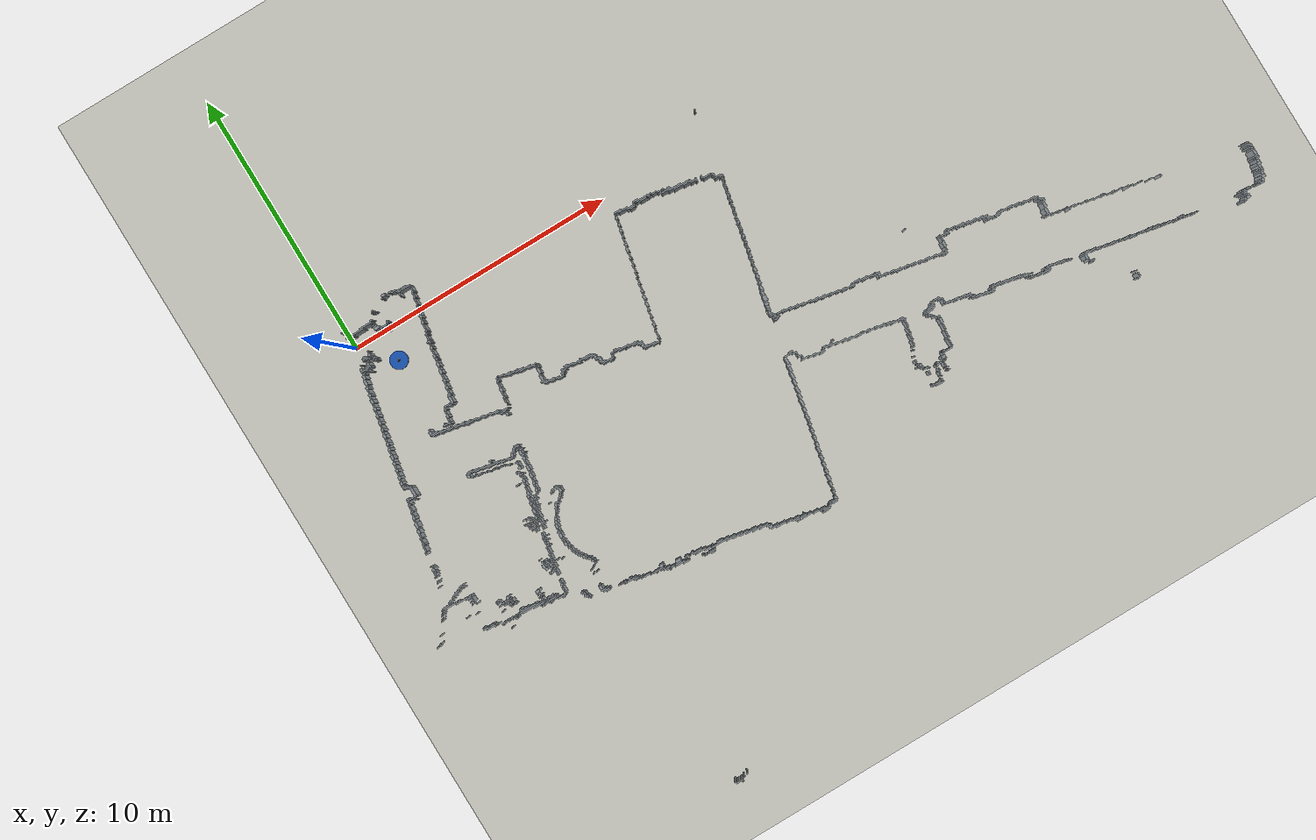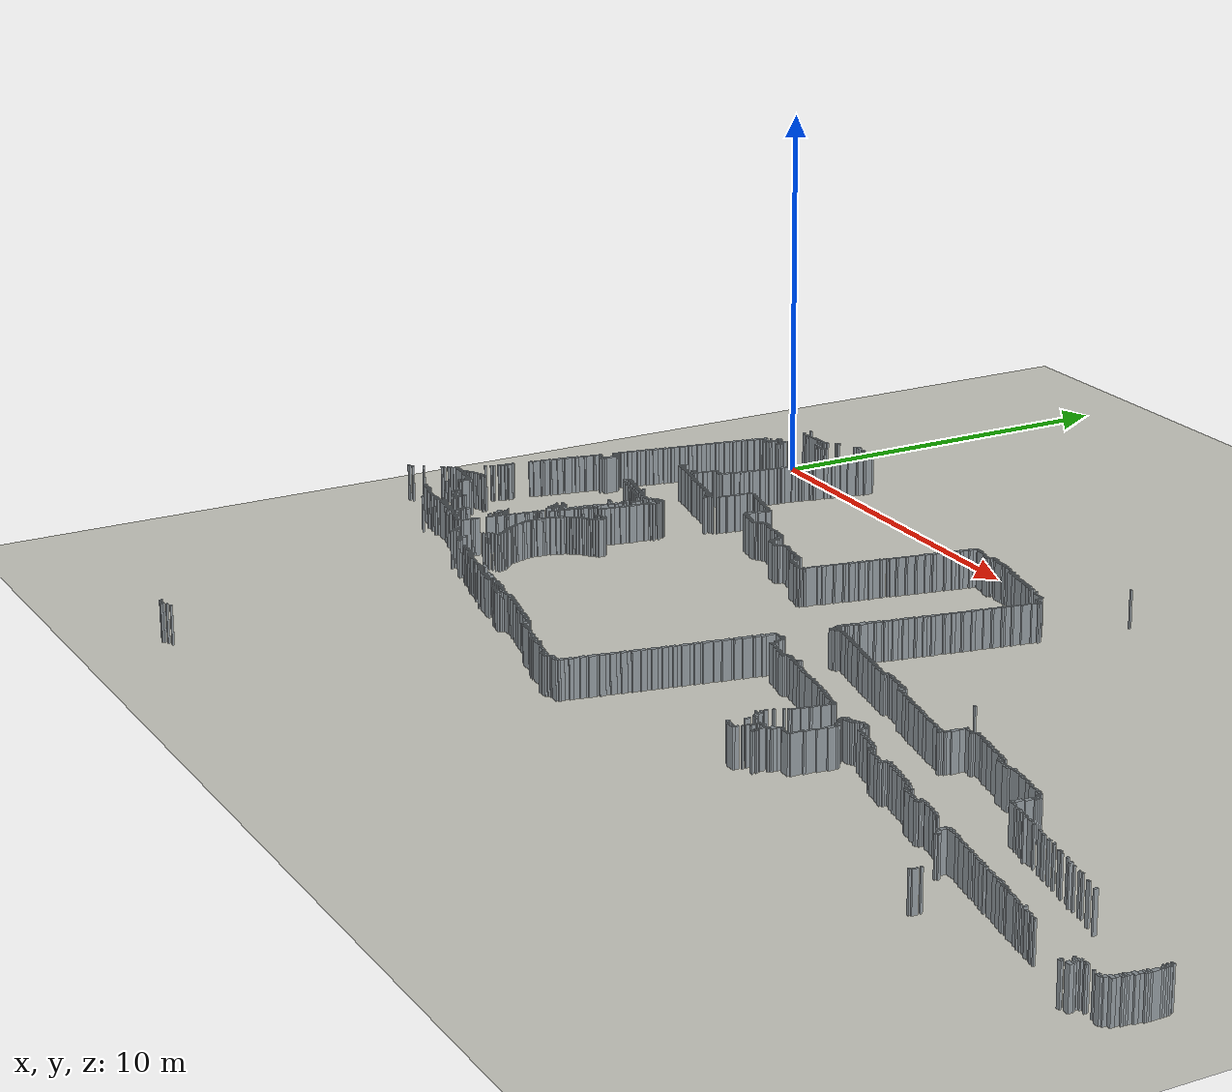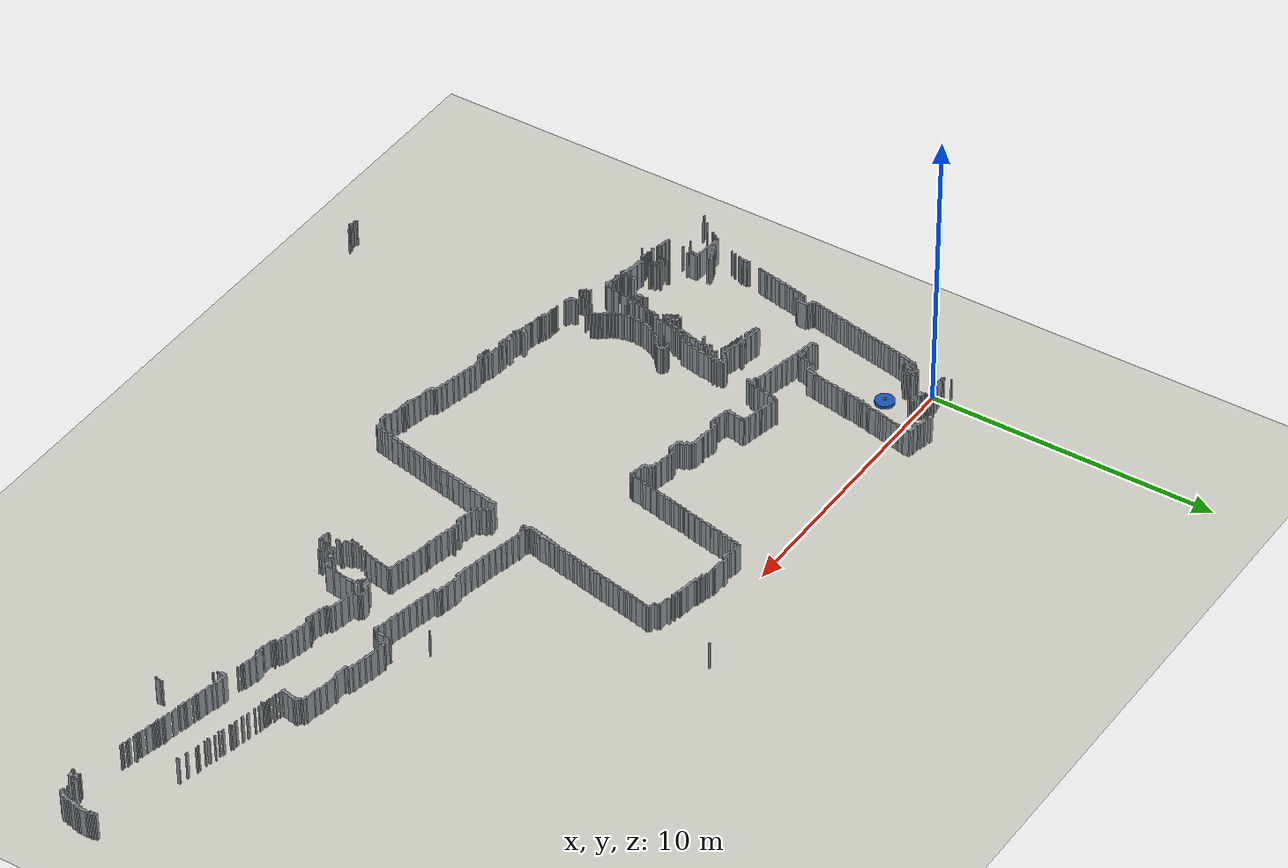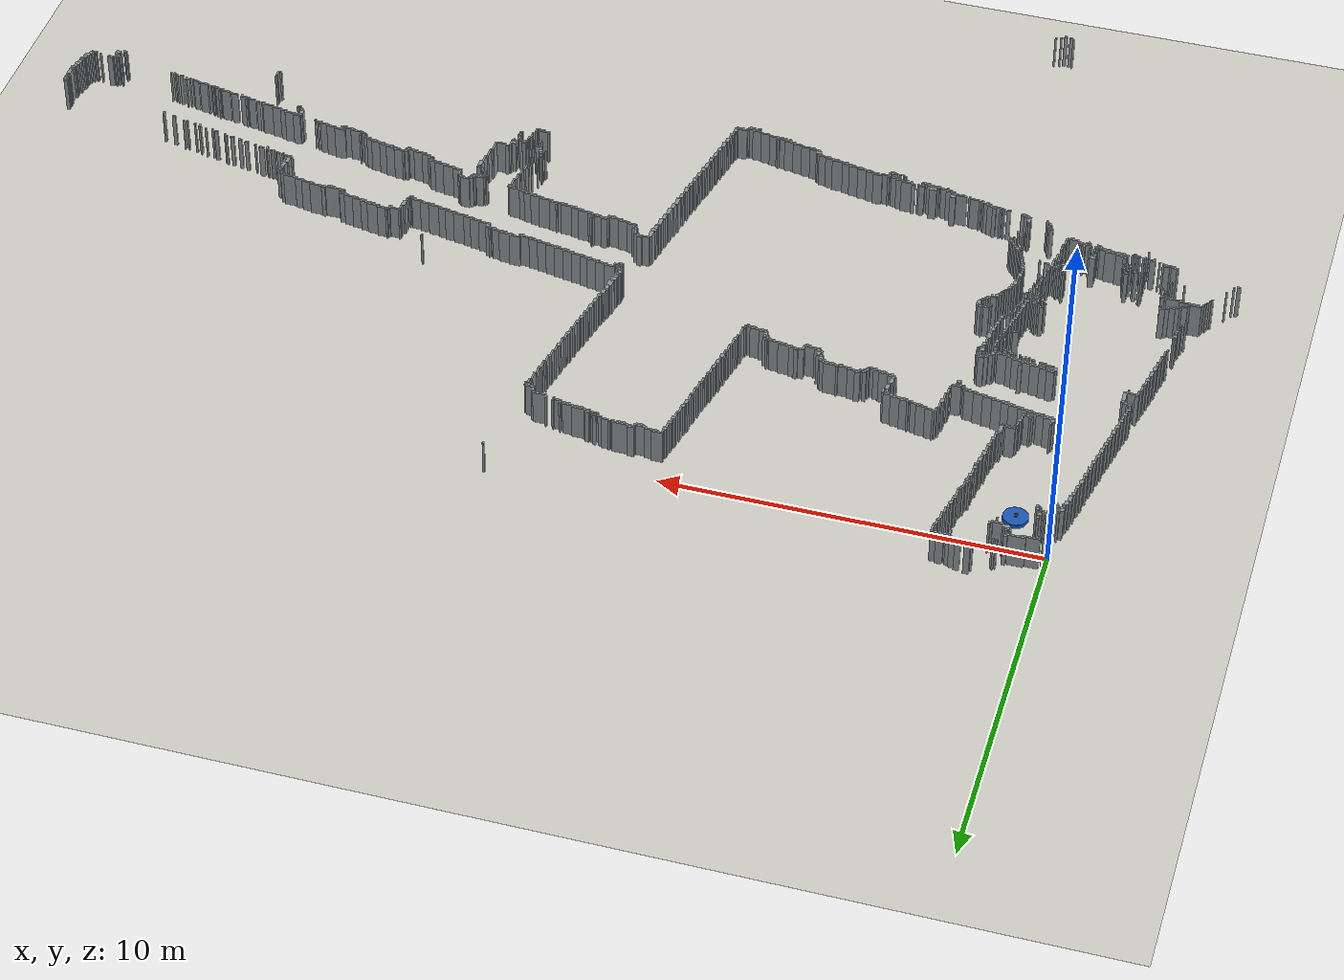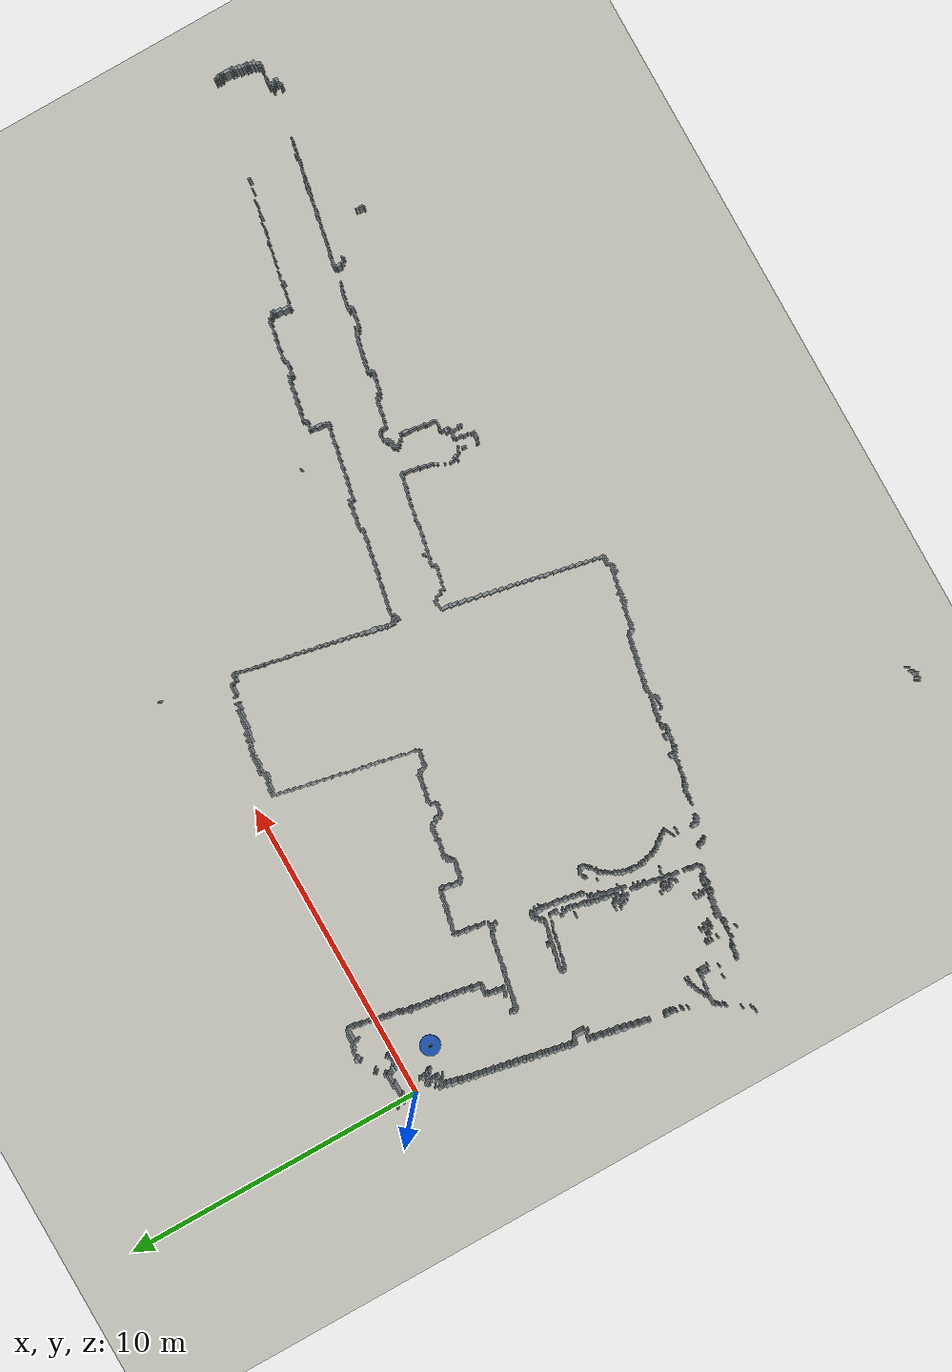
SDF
<?xml version="1.0"?>
<sdf version="1.9">
  <world name="my_map_1">
    <physics name="1ms" type="ode">
      <max_step_size>0.02</max_step_size>
      <real_time_factor>1.0</real_time_factor>
      <real_time_update_rate>50.0</real_time_update_rate>
    </physics>
    <plugin filename="gz-sim-physics-system" name="gz::sim::systems::Physics">
    </plugin>
    <plugin filename="gz-sim-user-commands-system" name="gz::sim::systems::UserCommands">
    </plugin>
    <plugin filename="gz-sim-scene-broadcaster-system" name="gz::sim::systems::SceneBroadcaster">
    </plugin>
    <plugin filename="gz-sim-sensors-system" name="gz::sim::systems::Sensors">
      <render_engine>ogre2</render_engine>
    </plugin>
    <scene>
      <ambient>0.45 0.45 0.45 1</ambient>
      <background>0.78 0.82 0.86 1</background>
      <shadows>false</shadows>
    </scene>
    <light name="sun" type="directional">
      <pose>0 0 10 0 0 0</pose>
      <diffuse>0.8 0.8 0.8 1</diffuse>
      <specular>0.2 0.2 0.2 1</specular>
      <direction>-0.5 0.2 -0.9</direction>
    </light>
    <model name="ground_plane">
      <pose>13.569 -3.931 0 0 0 0</pose>
      <static>true</static>
      <link name="link">
        <collision name="collision">
          <geometry>
            <plane>
              <normal>0 0 1</normal>
              <size>32.9 31.55</size>
            </plane>
          </geometry>
        </collision>
        <visual name="visual">
          <geometry>
            <plane>
              <normal>0 0 1</normal>
              <size>32.9 31.55</size>
            </plane>
          </geometry>
          <material>
            <ambient>0.82 0.82 0.78 1</ambient>
            <diffuse>0.82 0.82 0.78 1</diffuse>
          </material>
        </visual>
      </link>
    </model>
    <model name="real_environment">
      <static>true</static>
      <link name="obstacles">
        <collision name="obstacle_0000_collision">
          <pose>1.844 0.994 0.5 0 0 0</pose>
          <geometry>
            <box>
              <size>0.15 0.1 1.0</size>
            </box>
          </geometry>
        </collision>
        <visual name="obstacle_0000_visual">
          <pose>1.844 0.994 0.5 0 0 0</pose>
          <geometry>
            <box>
              <size>0.15 0.1 1.0</size>
            </box>
          </geometry>
          <material>
            <ambient>0.55 0.58 0.60 1</ambient>
            <diffuse>0.55 0.58 0.60 1</diffuse>
          </material>
        </visual>
        <collision name="obstacle_0001_collision">
          <pose>2.094 0.969 0.5 0 0 0</pose>
          <geometry>
            <box>
              <size>0.15 0.05 1.0</size>
            </box>
          </geometry>
        </collision>
        <visual name="obstacle_0001_visual">
          <pose>2.094 0.969 0.5 0 0 0</pose>
          <geometry>
            <box>
              <size>0.15 0.05 1.0</size>
            </box>
          </geometry>
          <material>
            <ambient>0.55 0.58 0.60 1</ambient>
            <diffuse>0.55 0.58 0.60 1</diffuse>
          </material>
        </visual>
        <collision name="obstacle_0002_collision">
          <pose>1.744 0.919 0.5 0 0 0</pose>
          <geometry>
            <box>
              <size>0.05 0.05 1.0</size>
            </box>
          </geometry>
        </collision>
        <visual name="obstacle_0002_visual">
          <pose>1.744 0.919 0.5 0 0 0</pose>
          <geometry>
            <box>
              <size>0.05 0.05 1.0</size>
            </box>
          </geometry>
          <material>
            <ambient>0.55 0.58 0.60 1</ambient>
            <diffuse>0.55 0.58 0.60 1</diffuse>
          </material>
        </visual>
        <collision name="obstacle_0003_collision">
          <pose>2.219 0.919 0.5 0 0 0</pose>
          <geometry>
            <box>
              <size>0.2 0.05 1.0</size>
            </box>
          </geometry>
        </collision>
        <visual name="obstacle_0003_visual">
          <pose>2.219 0.919 0.5 0 0 0</pose>
          <geometry>
            <box>
              <size>0.2 0.05 1.0</size>
            </box>
          </geometry>
          <material>
            <ambient>0.55 0.58 0.60 1</ambient>
            <diffuse>0.55 0.58 0.60 1</diffuse>
          </material>
        </visual>
        <collision name="obstacle_0004_collision">
          <pose>2.344 0.869 0.5 0 0 0</pose>
          <geometry>
            <box>
              <size>0.15 0.05 1.0</size>
            </box>
          </geometry>
        </collision>
        <visual name="obstacle_0004_visual">
          <pose>2.344 0.869 0.5 0 0 0</pose>
          <geometry>
            <box>
              <size>0.15 0.05 1.0</size>
            </box>
          </geometry>
          <material>
            <ambient>0.55 0.58 0.60 1</ambient>
            <diffuse>0.55 0.58 0.60 1</diffuse>
          </material>
        </visual>
        <collision name="obstacle_0005_collision">
          <pose>2.569 0.869 0.5 0 0 0</pose>
          <geometry>
            <box>
              <size>0.2 0.05 1.0</size>
            </box>
          </geometry>
        </collision>
        <visual name="obstacle_0005_visual">
          <pose>2.569 0.869 0.5 0 0 0</pose>
          <geometry>
            <box>
              <size>0.2 0.05 1.0</size>
            </box>
          </geometry>
          <material>
            <ambient>0.55 0.58 0.60 1</ambient>
            <diffuse>0.55 0.58 0.60 1</diffuse>
          </material>
        </visual>
        <collision name="obstacle_0006_collision">
          <pose>14.294 0.869 0.5 0 0 0</pose>
          <geometry>
            <box>
              <size>0.05 0.05 1.0</size>
            </box>
          </geometry>
        </collision>
        <visual name="obstacle_0006_visual">
          <pose>14.294 0.869 0.5 0 0 0</pose>
          <geometry>
            <box>
              <size>0.05 0.05 1.0</size>
            </box>
          </geometry>
          <material>
            <ambient>0.55 0.58 0.60 1</ambient>
            <diffuse>0.55 0.58 0.60 1</diffuse>
          </material>
        </visual>
        <collision name="obstacle_0007_collision">
          <pose>2.569 0.819 0.5 0 0 0</pose>
          <geometry>
            <box>
              <size>0.5 0.05 1.0</size>
            </box>
          </geometry>
        </collision>
        <visual name="obstacle_0007_visual">
          <pose>2.569 0.819 0.5 0 0 0</pose>
          <geometry>
            <box>
              <size>0.5 0.05 1.0</size>
            </box>
          </geometry>
          <material>
            <ambient>0.55 0.58 0.60 1</ambient>
            <diffuse>0.55 0.58 0.60 1</diffuse>
          </material>
        </visual>
        <collision name="obstacle_0008_collision">
          <pose>1.244 0.719 0.5 0 0 0</pose>
          <geometry>
            <box>
              <size>0.05 0.05 1.0</size>
            </box>
          </geometry>
        </collision>
        <visual name="obstacle_0008_visual">
          <pose>1.244 0.719 0.5 0 0 0</pose>
          <geometry>
            <box>
              <size>0.05 0.05 1.0</size>
            </box>
          </geometry>
          <material>
            <ambient>0.55 0.58 0.60 1</ambient>
            <diffuse>0.55 0.58 0.60 1</diffuse>
          </material>
        </visual>
        <collision name="obstacle_0009_collision">
          <pose>1.194 0.669 0.5 0 0 0</pose>
          <geometry>
            <box>
              <size>0.05 0.05 1.0</size>
            </box>
          </geometry>
        </collision>
        <visual name="obstacle_0009_visual">
          <pose>1.194 0.669 0.5 0 0 0</pose>
          <geometry>
            <box>
              <size>0.05 0.05 1.0</size>
            </box>
          </geometry>
          <material>
            <ambient>0.55 0.58 0.60 1</ambient>
            <diffuse>0.55 0.58 0.60 1</diffuse>
          </material>
        </visual>
        <collision name="obstacle_0010_collision">
          <pose>1.294 0.669 0.5 0 0 0</pose>
          <geometry>
            <box>
              <size>0.05 0.05 1.0</size>
            </box>
          </geometry>
        </collision>
        <visual name="obstacle_0010_visual">
          <pose>1.294 0.669 0.5 0 0 0</pose>
          <geometry>
            <box>
              <size>0.05 0.05 1.0</size>
            </box>
          </geometry>
          <material>
            <ambient>0.55 0.58 0.60 1</ambient>
            <diffuse>0.55 0.58 0.60 1</diffuse>
          </material>
        </visual>
        <collision name="obstacle_0011_collision">
          <pose>2.344 0.719 0.5 0 0 0</pose>
          <geometry>
            <box>
              <size>0.05 0.15 1.0</size>
            </box>
          </geometry>
        </collision>
        <visual name="obstacle_0011_visual">
          <pose>2.344 0.719 0.5 0 0 0</pose>
          <geometry>
            <box>
              <size>0.05 0.15 1.0</size>
            </box>
          </geometry>
          <material>
            <ambient>0.55 0.58 0.60 1</ambient>
            <diffuse>0.55 0.58 0.60 1</diffuse>
          </material>
        </visual>
        <collision name="obstacle_0012_collision">
          <pose>-0.056 0.619 0.5 0 0 0</pose>
          <geometry>
            <box>
              <size>0.05 0.05 1.0</size>
            </box>
          </geometry>
        </collision>
        <visual name="obstacle_0012_visual">
          <pose>-0.056 0.619 0.5 0 0 0</pose>
          <geometry>
            <box>
              <size>0.05 0.05 1.0</size>
            </box>
          </geometry>
          <material>
            <ambient>0.55 0.58 0.60 1</ambient>
            <diffuse>0.55 0.58 0.60 1</diffuse>
          </material>
        </visual>
        <collision name="obstacle_0013_collision">
          <pose>2.794 0.694 0.5 0 0 0</pose>
          <geometry>
            <box>
              <size>0.05 0.2 1.0</size>
            </box>
          </geometry>
        </collision>
        <visual name="obstacle_0013_visual">
          <pose>2.794 0.694 0.5 0 0 0</pose>
          <geometry>
            <box>
              <size>0.05 0.2 1.0</size>
            </box>
          </geometry>
          <material>
            <ambient>0.55 0.58 0.60 1</ambient>
            <diffuse>0.55 0.58 0.60 1</diffuse>
          </material>
        </visual>
        <collision name="obstacle_0014_collision">
          <pose>2.769 0.569 0.5 0 0 0</pose>
          <geometry>
            <box>
              <size>0.1 0.05 1.0</size>
            </box>
          </geometry>
        </collision>
        <visual name="obstacle_0014_visual">
          <pose>2.769 0.569 0.5 0 0 0</pose>
          <geometry>
            <box>
              <size>0.1 0.05 1.0</size>
            </box>
          </geometry>
          <material>
            <ambient>0.55 0.58 0.60 1</ambient>
            <diffuse>0.55 0.58 0.60 1</diffuse>
          </material>
        </visual>
        <collision name="obstacle_0015_collision">
          <pose>1.019 0.469 0.5 0 0 0</pose>
          <geometry>
            <box>
              <size>0.1 0.05 1.0</size>
            </box>
          </geometry>
        </collision>
        <visual name="obstacle_0015_visual">
          <pose>1.019 0.469 0.5 0 0 0</pose>
          <geometry>
            <box>
              <size>0.1 0.05 1.0</size>
            </box>
          </geometry>
          <material>
            <ambient>0.55 0.58 0.60 1</ambient>
            <diffuse>0.55 0.58 0.60 1</diffuse>
          </material>
        </visual>
        <collision name="obstacle_0016_collision">
          <pose>0.769 0.419 0.5 0 0 0</pose>
          <geometry>
            <box>
              <size>0.5 0.05 1.0</size>
            </box>
          </geometry>
        </collision>
        <visual name="obstacle_0016_visual">
          <pose>0.769 0.419 0.5 0 0 0</pose>
          <geometry>
            <box>
              <size>0.5 0.05 1.0</size>
            </box>
          </geometry>
          <material>
            <ambient>0.55 0.58 0.60 1</ambient>
            <diffuse>0.55 0.58 0.60 1</diffuse>
          </material>
        </visual>
        <collision name="obstacle_0017_collision">
          <pose>2.744 0.469 0.5 0 0 0</pose>
          <geometry>
            <box>
              <size>0.05 0.15 1.0</size>
            </box>
          </geometry>
        </collision>
        <visual name="obstacle_0017_visual">
          <pose>2.744 0.469 0.5 0 0 0</pose>
          <geometry>
            <box>
              <size>0.05 0.15 1.0</size>
            </box>
          </geometry>
          <material>
            <ambient>0.55 0.58 0.60 1</ambient>
            <diffuse>0.55 0.58 0.60 1</diffuse>
          </material>
        </visual>
        <collision name="obstacle_0018_collision">
          <pose>-0.006 0.369 0.5 0 0 0</pose>
          <geometry>
            <box>
              <size>0.05 0.05 1.0</size>
            </box>
          </geometry>
        </collision>
        <visual name="obstacle_0018_visual">
          <pose>-0.006 0.369 0.5 0 0 0</pose>
          <geometry>
            <box>
              <size>0.05 0.05 1.0</size>
            </box>
          </geometry>
          <material>
            <ambient>0.55 0.58 0.60 1</ambient>
            <diffuse>0.55 0.58 0.60 1</diffuse>
          </material>
        </visual>
        <collision name="obstacle_0019_collision">
          <pose>0.419 0.369 0.5 0 0 0</pose>
          <geometry>
            <box>
              <size>0.5 0.05 1.0</size>
            </box>
          </geometry>
        </collision>
        <visual name="obstacle_0019_visual">
          <pose>0.419 0.369 0.5 0 0 0</pose>
          <geometry>
            <box>
              <size>0.5 0.05 1.0</size>
            </box>
          </geometry>
          <material>
            <ambient>0.55 0.58 0.60 1</ambient>
            <diffuse>0.55 0.58 0.60 1</diffuse>
          </material>
        </visual>
        <collision name="obstacle_0020_collision">
          <pose>0.994 0.369 0.5 0 0 0</pose>
          <geometry>
            <box>
              <size>0.05 0.05 1.0</size>
            </box>
          </geometry>
        </collision>
        <visual name="obstacle_0020_visual">
          <pose>0.994 0.369 0.5 0 0 0</pose>
          <geometry>
            <box>
              <size>0.05 0.05 1.0</size>
            </box>
          </geometry>
          <material>
            <ambient>0.55 0.58 0.60 1</ambient>
            <diffuse>0.55 0.58 0.60 1</diffuse>
          </material>
        </visual>
        <collision name="obstacle_0021_collision">
          <pose>2.719 0.369 0.5 0 0 0</pose>
          <geometry>
            <box>
              <size>0.1 0.05 1.0</size>
            </box>
          </geometry>
        </collision>
        <visual name="obstacle_0021_visual">
          <pose>2.719 0.369 0.5 0 0 0</pose>
          <geometry>
            <box>
              <size>0.1 0.05 1.0</size>
            </box>
          </geometry>
          <material>
            <ambient>0.55 0.58 0.60 1</ambient>
            <diffuse>0.55 0.58 0.60 1</diffuse>
          </material>
        </visual>
        <collision name="obstacle_0022_collision">
          <pose>0.069 0.319 0.5 0 0 0</pose>
          <geometry>
            <box>
              <size>0.1 0.05 1.0</size>
            </box>
          </geometry>
        </collision>
        <visual name="obstacle_0022_visual">
          <pose>0.069 0.319 0.5 0 0 0</pose>
          <geometry>
            <box>
              <size>0.1 0.05 1.0</size>
            </box>
          </geometry>
          <material>
            <ambient>0.55 0.58 0.60 1</ambient>
            <diffuse>0.55 0.58 0.60 1</diffuse>
          </material>
        </visual>
        <collision name="obstacle_0023_collision">
          <pose>0.219 0.319 0.5 0 0 0</pose>
          <geometry>
            <box>
              <size>0.1 0.05 1.0</size>
            </box>
          </geometry>
        </collision>
        <visual name="obstacle_0023_visual">
          <pose>0.219 0.319 0.5 0 0 0</pose>
          <geometry>
            <box>
              <size>0.1 0.05 1.0</size>
            </box>
          </geometry>
          <material>
            <ambient>0.55 0.58 0.60 1</ambient>
            <diffuse>0.55 0.58 0.60 1</diffuse>
          </material>
        </visual>
        <collision name="obstacle_0024_collision">
          <pose>0.944 0.269 0.5 0 0 0</pose>
          <geometry>
            <box>
              <size>0.05 0.05 1.0</size>
            </box>
          </geometry>
        </collision>
        <visual name="obstacle_0024_visual">
          <pose>0.944 0.269 0.5 0 0 0</pose>
          <geometry>
            <box>
              <size>0.05 0.05 1.0</size>
            </box>
          </geometry>
          <material>
            <ambient>0.55 0.58 0.60 1</ambient>
            <diffuse>0.55 0.58 0.60 1</diffuse>
          </material>
        </visual>
        <collision name="obstacle_0025_collision">
          <pose>1.044 0.269 0.5 0 0 0</pose>
          <geometry>
            <box>
              <size>0.05 0.05 1.0</size>
            </box>
          </geometry>
        </collision>
        <visual name="obstacle_0025_visual">
          <pose>1.044 0.269 0.5 0 0 0</pose>
          <geometry>
            <box>
              <size>0.05 0.05 1.0</size>
            </box>
          </geometry>
          <material>
            <ambient>0.55 0.58 0.60 1</ambient>
            <diffuse>0.55 0.58 0.60 1</diffuse>
          </material>
        </visual>
        <collision name="obstacle_0026_collision">
          <pose>1.044 0.219 0.5 0 0 0</pose>
          <geometry>
            <box>
              <size>0.15 0.05 1.0</size>
            </box>
          </geometry>
        </collision>
        <visual name="obstacle_0026_visual">
          <pose>1.044 0.219 0.5 0 0 0</pose>
          <geometry>
            <box>
              <size>0.15 0.05 1.0</size>
            </box>
          </geometry>
          <material>
            <ambient>0.55 0.58 0.60 1</ambient>
            <diffuse>0.55 0.58 0.60 1</diffuse>
          </material>
        </visual>
        <collision name="obstacle_0027_collision">
          <pose>1.494 0.169 0.5 0 0 0</pose>
          <geometry>
            <box>
              <size>0.05 0.05 1.0</size>
            </box>
          </geometry>
        </collision>
        <visual name="obstacle_0027_visual">
          <pose>1.494 0.169 0.5 0 0 0</pose>
          <geometry>
            <box>
              <size>0.05 0.05 1.0</size>
            </box>
          </geometry>
          <material>
            <ambient>0.55 0.58 0.60 1</ambient>
            <diffuse>0.55 0.58 0.60 1</diffuse>
          </material>
        </visual>
        <collision name="obstacle_0028_collision">
          <pose>1.069 0.144 0.5 0 0 0</pose>
          <geometry>
            <box>
              <size>0.2 0.1 1.0</size>
            </box>
          </geometry>
        </collision>
        <visual name="obstacle_0028_visual">
          <pose>1.069 0.144 0.5 0 0 0</pose>
          <geometry>
            <box>
              <size>0.2 0.1 1.0</size>
            </box>
          </geometry>
          <material>
            <ambient>0.55 0.58 0.60 1</ambient>
            <diffuse>0.55 0.58 0.60 1</diffuse>
          </material>
        </visual>
        <collision name="obstacle_0029_collision">
          <pose>1.469 0.119 0.5 0 0 0</pose>
          <geometry>
            <box>
              <size>0.1 0.05 1.0</size>
            </box>
          </geometry>
        </collision>
        <visual name="obstacle_0029_visual">
          <pose>1.469 0.119 0.5 0 0 0</pose>
          <geometry>
            <box>
              <size>0.1 0.05 1.0</size>
            </box>
          </geometry>
          <material>
            <ambient>0.55 0.58 0.60 1</ambient>
            <diffuse>0.55 0.58 0.60 1</diffuse>
          </material>
        </visual>
        <collision name="obstacle_0030_collision">
          <pose>2.694 0.219 0.5 0 0 0</pose>
          <geometry>
            <box>
              <size>0.05 0.25 1.0</size>
            </box>
          </geometry>
        </collision>
        <visual name="obstacle_0030_visual">
          <pose>2.694 0.219 0.5 0 0 0</pose>
          <geometry>
            <box>
              <size>0.05 0.25 1.0</size>
            </box>
          </geometry>
          <material>
            <ambient>0.55 0.58 0.60 1</ambient>
            <diffuse>0.55 0.58 0.60 1</diffuse>
          </material>
        </visual>
        <collision name="obstacle_0031_collision">
          <pose>1.319 0.069 0.5 0 0 0</pose>
          <geometry>
            <box>
              <size>0.3 0.05 1.0</size>
            </box>
          </geometry>
        </collision>
        <visual name="obstacle_0031_visual">
          <pose>1.319 0.069 0.5 0 0 0</pose>
          <geometry>
            <box>
              <size>0.3 0.05 1.0</size>
            </box>
          </geometry>
          <material>
            <ambient>0.55 0.58 0.60 1</ambient>
            <diffuse>0.55 0.58 0.60 1</diffuse>
          </material>
        </visual>
        <collision name="obstacle_0032_collision">
          <pose>1.344 0.019 0.5 0 0 0</pose>
          <geometry>
            <box>
              <size>0.05 0.05 1.0</size>
            </box>
          </geometry>
        </collision>
        <visual name="obstacle_0032_visual">
          <pose>1.344 0.019 0.5 0 0 0</pose>
          <geometry>
            <box>
              <size>0.05 0.05 1.0</size>
            </box>
          </geometry>
          <material>
            <ambient>0.55 0.58 0.60 1</ambient>
            <diffuse>0.55 0.58 0.60 1</diffuse>
          </material>
        </visual>
        <collision name="obstacle_0033_collision">
          <pose>1.344 -0.081 0.5 0 0 0</pose>
          <geometry>
            <box>
              <size>0.05 0.05 1.0</size>
            </box>
          </geometry>
        </collision>
        <visual name="obstacle_0033_visual">
          <pose>1.344 -0.081 0.5 0 0 0</pose>
          <geometry>
            <box>
              <size>0.05 0.05 1.0</size>
            </box>
          </geometry>
          <material>
            <ambient>0.55 0.58 0.60 1</ambient>
            <diffuse>0.55 0.58 0.60 1</diffuse>
          </material>
        </visual>
        <collision name="obstacle_0034_collision">
          <pose>2.644 -0.006 0.5 0 0 0</pose>
          <geometry>
            <box>
              <size>0.05 0.2 1.0</size>
            </box>
          </geometry>
        </collision>
        <visual name="obstacle_0034_visual">
          <pose>2.644 -0.006 0.5 0 0 0</pose>
          <geometry>
            <box>
              <size>0.05 0.2 1.0</size>
            </box>
          </geometry>
          <material>
            <ambient>0.55 0.58 0.60 1</ambient>
            <diffuse>0.55 0.58 0.60 1</diffuse>
          </material>
        </visual>
        <collision name="obstacle_0035_collision">
          <pose>2.594 -0.181 0.5 0 0 0</pose>
          <geometry>
            <box>
              <size>0.05 0.15 1.0</size>
            </box>
          </geometry>
        </collision>
        <visual name="obstacle_0035_visual">
          <pose>2.594 -0.181 0.5 0 0 0</pose>
          <geometry>
            <box>
              <size>0.05 0.15 1.0</size>
            </box>
          </geometry>
          <material>
            <ambient>0.55 0.58 0.60 1</ambient>
            <diffuse>0.55 0.58 0.60 1</diffuse>
          </material>
        </visual>
        <collision name="obstacle_0036_collision">
          <pose>2.569 -0.306 0.5 0 0 0</pose>
          <geometry>
            <box>
              <size>0.1 0.1 1.0</size>
            </box>
          </geometry>
        </collision>
        <visual name="obstacle_0036_visual">
          <pose>2.569 -0.306 0.5 0 0 0</pose>
          <geometry>
            <box>
              <size>0.1 0.1 1.0</size>
            </box>
          </geometry>
          <material>
            <ambient>0.55 0.58 0.60 1</ambient>
            <diffuse>0.55 0.58 0.60 1</diffuse>
          </material>
        </visual>
        <collision name="obstacle_0037_collision">
          <pose>0.394 -0.381 0.5 0 0 0</pose>
          <geometry>
            <box>
              <size>0.05 0.05 1.0</size>
            </box>
          </geometry>
        </collision>
        <visual name="obstacle_0037_visual">
          <pose>0.394 -0.381 0.5 0 0 0</pose>
          <geometry>
            <box>
              <size>0.05 0.05 1.0</size>
            </box>
          </geometry>
          <material>
            <ambient>0.55 0.58 0.60 1</ambient>
            <diffuse>0.55 0.58 0.60 1</diffuse>
          </material>
        </visual>
        <collision name="obstacle_0038_collision">
          <pose>2.544 -0.406 0.5 0 0 0</pose>
          <geometry>
            <box>
              <size>0.05 0.1 1.0</size>
            </box>
          </geometry>
        </collision>
        <visual name="obstacle_0038_visual">
          <pose>2.544 -0.406 0.5 0 0 0</pose>
          <geometry>
            <box>
              <size>0.05 0.1 1.0</size>
            </box>
          </geometry>
          <material>
            <ambient>0.55 0.58 0.60 1</ambient>
            <diffuse>0.55 0.58 0.60 1</diffuse>
          </material>
        </visual>
        <collision name="obstacle_0039_collision">
          <pose>0.169 -0.481 0.5 0 0 0</pose>
          <geometry>
            <box>
              <size>0.1 0.05 1.0</size>
            </box>
          </geometry>
        </collision>
        <visual name="obstacle_0039_visual">
          <pose>0.169 -0.481 0.5 0 0 0</pose>
          <geometry>
            <box>
              <size>0.1 0.05 1.0</size>
            </box>
          </geometry>
          <material>
            <ambient>0.55 0.58 0.60 1</ambient>
            <diffuse>0.55 0.58 0.60 1</diffuse>
          </material>
        </visual>
        <collision name="obstacle_0040_collision">
          <pose>0.169 -0.531 0.5 0 0 0</pose>
          <geometry>
            <box>
              <size>0.2 0.05 1.0</size>
            </box>
          </geometry>
        </collision>
        <visual name="obstacle_0040_visual">
          <pose>0.169 -0.531 0.5 0 0 0</pose>
          <geometry>
            <box>
              <size>0.2 0.05 1.0</size>
            </box>
          </geometry>
          <material>
            <ambient>0.55 0.58 0.60 1</ambient>
            <diffuse>0.55 0.58 0.60 1</diffuse>
          </material>
        </visual>
        <collision name="obstacle_0041_collision">
          <pose>0.369 -0.506 0.5 0 0 0</pose>
          <geometry>
            <box>
              <size>0.1 0.1 1.0</size>
            </box>
          </geometry>
        </collision>
        <visual name="obstacle_0041_visual">
          <pose>0.369 -0.506 0.5 0 0 0</pose>
          <geometry>
            <box>
              <size>0.1 0.1 1.0</size>
            </box>
          </geometry>
          <material>
            <ambient>0.55 0.58 0.60 1</ambient>
            <diffuse>0.55 0.58 0.60 1</diffuse>
          </material>
        </visual>
        <collision name="obstacle_0042_collision">
          <pose>2.519 -0.506 0.5 0 0 0</pose>
          <geometry>
            <box>
              <size>0.1 0.1 1.0</size>
            </box>
          </geometry>
        </collision>
        <visual name="obstacle_0042_visual">
          <pose>2.519 -0.506 0.5 0 0 0</pose>
          <geometry>
            <box>
              <size>0.1 0.1 1.0</size>
            </box>
          </geometry>
          <material>
            <ambient>0.55 0.58 0.60 1</ambient>
            <diffuse>0.55 0.58 0.60 1</diffuse>
          </material>
        </visual>
        <collision name="obstacle_0043_collision">
          <pose>0.094 -0.581 0.5 0 0 0</pose>
          <geometry>
            <box>
              <size>0.05 0.05 1.0</size>
            </box>
          </geometry>
        </collision>
        <visual name="obstacle_0043_visual">
          <pose>0.094 -0.581 0.5 0 0 0</pose>
          <geometry>
            <box>
              <size>0.05 0.05 1.0</size>
            </box>
          </geometry>
          <material>
            <ambient>0.55 0.58 0.60 1</ambient>
            <diffuse>0.55 0.58 0.60 1</diffuse>
          </material>
        </visual>
        <collision name="obstacle_0044_collision">
          <pose>0.244 -0.581 0.5 0 0 0</pose>
          <geometry>
            <box>
              <size>0.15 0.05 1.0</size>
            </box>
          </geometry>
        </collision>
        <visual name="obstacle_0044_visual">
          <pose>0.244 -0.581 0.5 0 0 0</pose>
          <geometry>
            <box>
              <size>0.15 0.05 1.0</size>
            </box>
          </geometry>
          <material>
            <ambient>0.55 0.58 0.60 1</ambient>
            <diffuse>0.55 0.58 0.60 1</diffuse>
          </material>
        </visual>
        <collision name="obstacle_0045_collision">
          <pose>0.394 -0.581 0.5 0 0 0</pose>
          <geometry>
            <box>
              <size>0.05 0.05 1.0</size>
            </box>
          </geometry>
        </collision>
        <visual name="obstacle_0045_visual">
          <pose>0.394 -0.581 0.5 0 0 0</pose>
          <geometry>
            <box>
              <size>0.05 0.05 1.0</size>
            </box>
          </geometry>
          <material>
            <ambient>0.55 0.58 0.60 1</ambient>
            <diffuse>0.55 0.58 0.60 1</diffuse>
          </material>
        </visual>
        <collision name="obstacle_0046_collision">
          <pose>0.319 -0.631 0.5 0 0 0</pose>
          <geometry>
            <box>
              <size>0.1 0.05 1.0</size>
            </box>
          </geometry>
        </collision>
        <visual name="obstacle_0046_visual">
          <pose>0.319 -0.631 0.5 0 0 0</pose>
          <geometry>
            <box>
              <size>0.1 0.05 1.0</size>
            </box>
          </geometry>
          <material>
            <ambient>0.55 0.58 0.60 1</ambient>
            <diffuse>0.55 0.58 0.60 1</diffuse>
          </material>
        </visual>
        <collision name="obstacle_0047_collision">
          <pose>0.444 -0.631 0.5 0 0 0</pose>
          <geometry>
            <box>
              <size>0.05 0.05 1.0</size>
            </box>
          </geometry>
        </collision>
        <visual name="obstacle_0047_visual">
          <pose>0.444 -0.631 0.5 0 0 0</pose>
          <geometry>
            <box>
              <size>0.05 0.05 1.0</size>
            </box>
          </geometry>
          <material>
            <ambient>0.55 0.58 0.60 1</ambient>
            <diffuse>0.55 0.58 0.60 1</diffuse>
          </material>
        </visual>
        <collision name="obstacle_0048_collision">
          <pose>-0.056 -0.681 0.5 0 0 0</pose>
          <geometry>
            <box>
              <size>0.05 0.05 1.0</size>
            </box>
          </geometry>
        </collision>
        <visual name="obstacle_0048_visual">
          <pose>-0.056 -0.681 0.5 0 0 0</pose>
          <geometry>
            <box>
              <size>0.05 0.05 1.0</size>
            </box>
          </geometry>
          <material>
            <ambient>0.55 0.58 0.60 1</ambient>
            <diffuse>0.55 0.58 0.60 1</diffuse>
          </material>
        </visual>
        <collision name="obstacle_0049_collision">
          <pose>0.194 -0.681 0.5 0 0 0</pose>
          <geometry>
            <box>
              <size>0.05 0.05 1.0</size>
            </box>
          </geometry>
        </collision>
        <visual name="obstacle_0049_visual">
          <pose>0.194 -0.681 0.5 0 0 0</pose>
          <geometry>
            <box>
              <size>0.05 0.05 1.0</size>
            </box>
          </geometry>
          <material>
            <ambient>0.55 0.58 0.60 1</ambient>
            <diffuse>0.55 0.58 0.60 1</diffuse>
          </material>
        </visual>
        <collision name="obstacle_0050_collision">
          <pose>0.469 -0.681 0.5 0 0 0</pose>
          <geometry>
            <box>
              <size>0.1 0.05 1.0</size>
            </box>
          </geometry>
        </collision>
        <visual name="obstacle_0050_visual">
          <pose>0.469 -0.681 0.5 0 0 0</pose>
          <geometry>
            <box>
              <size>0.1 0.05 1.0</size>
            </box>
          </geometry>
          <material>
            <ambient>0.55 0.58 0.60 1</ambient>
            <diffuse>0.55 0.58 0.60 1</diffuse>
          </material>
        </visual>
        <collision name="obstacle_0051_collision">
          <pose>0.394 -0.731 0.5 0 0 0</pose>
          <geometry>
            <box>
              <size>0.05 0.05 1.0</size>
            </box>
          </geometry>
        </collision>
        <visual name="obstacle_0051_visual">
          <pose>0.394 -0.731 0.5 0 0 0</pose>
          <geometry>
            <box>
              <size>0.05 0.05 1.0</size>
            </box>
          </geometry>
          <material>
            <ambient>0.55 0.58 0.60 1</ambient>
            <diffuse>0.55 0.58 0.60 1</diffuse>
          </material>
        </visual>
        <collision name="obstacle_0052_collision">
          <pose>0.494 -0.731 0.5 0 0 0</pose>
          <geometry>
            <box>
              <size>0.05 0.05 1.0</size>
            </box>
          </geometry>
        </collision>
        <visual name="obstacle_0052_visual">
          <pose>0.494 -0.731 0.5 0 0 0</pose>
          <geometry>
            <box>
              <size>0.05 0.05 1.0</size>
            </box>
          </geometry>
          <material>
            <ambient>0.55 0.58 0.60 1</ambient>
            <diffuse>0.55 0.58 0.60 1</diffuse>
          </material>
        </visual>
        <collision name="obstacle_0053_collision">
          <pose>10.219 -0.731 0.5 0 0 0</pose>
          <geometry>
            <box>
              <size>0.3 0.05 1.0</size>
            </box>
          </geometry>
        </collision>
        <visual name="obstacle_0053_visual">
          <pose>10.219 -0.731 0.5 0 0 0</pose>
          <geometry>
            <box>
              <size>0.3 0.05 1.0</size>
            </box>
          </geometry>
          <material>
            <ambient>0.55 0.58 0.60 1</ambient>
            <diffuse>0.55 0.58 0.60 1</diffuse>
          </material>
        </visual>
        <collision name="obstacle_0054_collision">
          <pose>10.919 -0.731 0.5 0 0 0</pose>
          <geometry>
            <box>
              <size>0.2 0.05 1.0</size>
            </box>
          </geometry>
        </collision>
        <visual name="obstacle_0054_visual">
          <pose>10.919 -0.731 0.5 0 0 0</pose>
          <geometry>
            <box>
              <size>0.2 0.05 1.0</size>
            </box>
          </geometry>
          <material>
            <ambient>0.55 0.58 0.60 1</ambient>
            <diffuse>0.55 0.58 0.60 1</diffuse>
          </material>
        </visual>
        <collision name="obstacle_0055_collision">
          <pose>0.169 -0.756 0.5 0 0 0</pose>
          <geometry>
            <box>
              <size>0.1 0.1 1.0</size>
            </box>
          </geometry>
        </collision>
        <visual name="obstacle_0055_visual">
          <pose>0.169 -0.756 0.5 0 0 0</pose>
          <geometry>
            <box>
              <size>0.1 0.1 1.0</size>
            </box>
          </geometry>
          <material>
            <ambient>0.55 0.58 0.60 1</ambient>
            <diffuse>0.55 0.58 0.60 1</diffuse>
          </material>
        </visual>
        <collision name="obstacle_0056_collision">
          <pose>0.469 -0.781 0.5 0 0 0</pose>
          <geometry>
            <box>
              <size>0.1 0.05 1.0</size>
            </box>
          </geometry>
        </collision>
        <visual name="obstacle_0056_visual">
          <pose>0.469 -0.781 0.5 0 0 0</pose>
          <geometry>
            <box>
              <size>0.1 0.05 1.0</size>
            </box>
          </geometry>
          <material>
            <ambient>0.55 0.58 0.60 1</ambient>
            <diffuse>0.55 0.58 0.60 1</diffuse>
          </material>
        </visual>
        <collision name="obstacle_0057_collision">
          <pose>2.494 -0.681 0.5 0 0 0</pose>
          <geometry>
            <box>
              <size>0.05 0.25 1.0</size>
            </box>
          </geometry>
        </collision>
        <visual name="obstacle_0057_visual">
          <pose>2.494 -0.681 0.5 0 0 0</pose>
          <geometry>
            <box>
              <size>0.05 0.25 1.0</size>
            </box>
          </geometry>
          <material>
            <ambient>0.55 0.58 0.60 1</ambient>
            <diffuse>0.55 0.58 0.60 1</diffuse>
          </material>
        </visual>
        <collision name="obstacle_0058_collision">
          <pose>10.394 -0.781 0.5 0 0 0</pose>
          <geometry>
            <box>
              <size>0.35 0.05 1.0</size>
            </box>
          </geometry>
        </collision>
        <visual name="obstacle_0058_visual">
          <pose>10.394 -0.781 0.5 0 0 0</pose>
          <geometry>
            <box>
              <size>0.35 0.05 1.0</size>
            </box>
          </geometry>
          <material>
            <ambient>0.55 0.58 0.60 1</ambient>
            <diffuse>0.55 0.58 0.60 1</diffuse>
          </material>
        </visual>
        <collision name="obstacle_0059_collision">
          <pose>10.844 -0.781 0.5 0 0 0</pose>
          <geometry>
            <box>
              <size>0.05 0.05 1.0</size>
            </box>
          </geometry>
        </collision>
        <visual name="obstacle_0059_visual">
          <pose>10.844 -0.781 0.5 0 0 0</pose>
          <geometry>
            <box>
              <size>0.05 0.05 1.0</size>
            </box>
          </geometry>
          <material>
            <ambient>0.55 0.58 0.60 1</ambient>
            <diffuse>0.55 0.58 0.60 1</diffuse>
          </material>
        </visual>
        <collision name="obstacle_0060_collision">
          <pose>11.169 -0.781 0.5 0 0 0</pose>
          <geometry>
            <box>
              <size>0.5 0.05 1.0</size>
            </box>
          </geometry>
        </collision>
        <visual name="obstacle_0060_visual">
          <pose>11.169 -0.781 0.5 0 0 0</pose>
          <geometry>
            <box>
              <size>0.5 0.05 1.0</size>
            </box>
          </geometry>
          <material>
            <ambient>0.55 0.58 0.60 1</ambient>
            <diffuse>0.55 0.58 0.60 1</diffuse>
          </material>
        </visual>
        <collision name="obstacle_0061_collision">
          <pose>11.494 -0.781 0.5 0 0 0</pose>
          <geometry>
            <box>
              <size>0.05 0.05 1.0</size>
            </box>
          </geometry>
        </collision>
        <visual name="obstacle_0061_visual">
          <pose>11.494 -0.781 0.5 0 0 0</pose>
          <geometry>
            <box>
              <size>0.05 0.05 1.0</size>
            </box>
          </geometry>
          <material>
            <ambient>0.55 0.58 0.60 1</ambient>
            <diffuse>0.55 0.58 0.60 1</diffuse>
          </material>
        </visual>
        <collision name="obstacle_0062_collision">
          <pose>-0.131 -0.806 0.5 0 0 0</pose>
          <geometry>
            <box>
              <size>0.1 0.1 1.0</size>
            </box>
          </geometry>
        </collision>
        <visual name="obstacle_0062_visual">
          <pose>-0.131 -0.806 0.5 0 0 0</pose>
          <geometry>
            <box>
              <size>0.1 0.1 1.0</size>
            </box>
          </geometry>
          <material>
            <ambient>0.55 0.58 0.60 1</ambient>
            <diffuse>0.55 0.58 0.60 1</diffuse>
          </material>
        </visual>
        <collision name="obstacle_0063_collision">
          <pose>0.144 -0.831 0.5 0 0 0</pose>
          <geometry>
            <box>
              <size>0.15 0.05 1.0</size>
            </box>
          </geometry>
        </collision>
        <visual name="obstacle_0063_visual">
          <pose>0.144 -0.831 0.5 0 0 0</pose>
          <geometry>
            <box>
              <size>0.15 0.05 1.0</size>
            </box>
          </geometry>
          <material>
            <ambient>0.55 0.58 0.60 1</ambient>
            <diffuse>0.55 0.58 0.60 1</diffuse>
          </material>
        </visual>
        <collision name="obstacle_0064_collision">
          <pose>2.469 -0.831 0.5 0 0 0</pose>
          <geometry>
            <box>
              <size>0.1 0.05 1.0</size>
            </box>
          </geometry>
        </collision>
        <visual name="obstacle_0064_visual">
          <pose>2.469 -0.831 0.5 0 0 0</pose>
          <geometry>
            <box>
              <size>0.1 0.05 1.0</size>
            </box>
          </geometry>
          <material>
            <ambient>0.55 0.58 0.60 1</ambient>
            <diffuse>0.55 0.58 0.60 1</diffuse>
          </material>
        </visual>
        <collision name="obstacle_0065_collision">
          <pose>10.094 -0.806 0.5 0 0 0</pose>
          <geometry>
            <box>
              <size>0.05 0.1 1.0</size>
            </box>
          </geometry>
        </collision>
        <visual name="obstacle_0065_visual">
          <pose>10.094 -0.806 0.5 0 0 0</pose>
          <geometry>
            <box>
              <size>0.05 0.1 1.0</size>
            </box>
          </geometry>
          <material>
            <ambient>0.55 0.58 0.60 1</ambient>
            <diffuse>0.55 0.58 0.60 1</diffuse>
          </material>
        </visual>
        <collision name="obstacle_0066_collision">
          <pose>10.694 -0.831 0.5 0 0 0</pose>
          <geometry>
            <box>
              <size>0.35 0.05 1.0</size>
            </box>
          </geometry>
        </collision>
        <visual name="obstacle_0066_visual">
          <pose>10.694 -0.831 0.5 0 0 0</pose>
          <geometry>
            <box>
              <size>0.35 0.05 1.0</size>
            </box>
          </geometry>
          <material>
            <ambient>0.55 0.58 0.60 1</ambient>
            <diffuse>0.55 0.58 0.60 1</diffuse>
          </material>
        </visual>
        <collision name="obstacle_0067_collision">
          <pose>11.194 -0.831 0.5 0 0 0</pose>
          <geometry>
            <box>
              <size>0.25 0.05 1.0</size>
            </box>
          </geometry>
        </collision>
        <visual name="obstacle_0067_visual">
          <pose>11.194 -0.831 0.5 0 0 0</pose>
          <geometry>
            <box>
              <size>0.25 0.05 1.0</size>
            </box>
          </geometry>
          <material>
            <ambient>0.55 0.58 0.60 1</ambient>
            <diffuse>0.55 0.58 0.60 1</diffuse>
          </material>
        </visual>
        <collision name="obstacle_0068_collision">
          <pose>11.419 -0.831 0.5 0 0 0</pose>
          <geometry>
            <box>
              <size>0.1 0.05 1.0</size>
            </box>
          </geometry>
        </collision>
        <visual name="obstacle_0068_visual">
          <pose>11.419 -0.831 0.5 0 0 0</pose>
          <geometry>
            <box>
              <size>0.1 0.05 1.0</size>
            </box>
          </geometry>
          <material>
            <ambient>0.55 0.58 0.60 1</ambient>
            <diffuse>0.55 0.58 0.60 1</diffuse>
          </material>
        </visual>
        <collision name="obstacle_0069_collision">
          <pose>11.619 -0.831 0.5 0 0 0</pose>
          <geometry>
            <box>
              <size>0.2 0.05 1.0</size>
            </box>
          </geometry>
        </collision>
        <visual name="obstacle_0069_visual">
          <pose>11.619 -0.831 0.5 0 0 0</pose>
          <geometry>
            <box>
              <size>0.2 0.05 1.0</size>
            </box>
          </geometry>
          <material>
            <ambient>0.55 0.58 0.60 1</ambient>
            <diffuse>0.55 0.58 0.60 1</diffuse>
          </material>
        </visual>
        <collision name="obstacle_0070_collision">
          <pose>0.019 -0.881 0.5 0 0 0</pose>
          <geometry>
            <box>
              <size>0.4 0.05 1.0</size>
            </box>
          </geometry>
        </collision>
        <visual name="obstacle_0070_visual">
          <pose>0.019 -0.881 0.5 0 0 0</pose>
          <geometry>
            <box>
              <size>0.4 0.05 1.0</size>
            </box>
          </geometry>
          <material>
            <ambient>0.55 0.58 0.60 1</ambient>
            <diffuse>0.55 0.58 0.60 1</diffuse>
          </material>
        </visual>
        <collision name="obstacle_0071_collision">
          <pose>2.444 -0.881 0.5 0 0 0</pose>
          <geometry>
            <box>
              <size>0.05 0.05 1.0</size>
            </box>
          </geometry>
        </collision>
        <visual name="obstacle_0071_visual">
          <pose>2.444 -0.881 0.5 0 0 0</pose>
          <geometry>
            <box>
              <size>0.05 0.05 1.0</size>
            </box>
          </geometry>
          <material>
            <ambient>0.55 0.58 0.60 1</ambient>
            <diffuse>0.55 0.58 0.60 1</diffuse>
          </material>
        </visual>
        <collision name="obstacle_0072_collision">
          <pose>10.719 -0.881 0.5 0 0 0</pose>
          <geometry>
            <box>
              <size>0.2 0.05 1.0</size>
            </box>
          </geometry>
        </collision>
        <visual name="obstacle_0072_visual">
          <pose>10.719 -0.881 0.5 0 0 0</pose>
          <geometry>
            <box>
              <size>0.2 0.05 1.0</size>
            </box>
          </geometry>
          <material>
            <ambient>0.55 0.58 0.60 1</ambient>
            <diffuse>0.55 0.58 0.60 1</diffuse>
          </material>
        </visual>
        <collision name="obstacle_0073_collision">
          <pose>11.769 -0.881 0.5 0 0 0</pose>
          <geometry>
            <box>
              <size>0.1 0.05 1.0</size>
            </box>
          </geometry>
        </collision>
        <visual name="obstacle_0073_visual">
          <pose>11.769 -0.881 0.5 0 0 0</pose>
          <geometry>
            <box>
              <size>0.1 0.05 1.0</size>
            </box>
          </geometry>
          <material>
            <ambient>0.55 0.58 0.60 1</ambient>
            <diffuse>0.55 0.58 0.60 1</diffuse>
          </material>
        </visual>
        <collision name="obstacle_0074_collision">
          <pose>11.919 -0.881 0.5 0 0 0</pose>
          <geometry>
            <box>
              <size>0.1 0.05 1.0</size>
            </box>
          </geometry>
        </collision>
        <visual name="obstacle_0074_visual">
          <pose>11.919 -0.881 0.5 0 0 0</pose>
          <geometry>
            <box>
              <size>0.1 0.05 1.0</size>
            </box>
          </geometry>
          <material>
            <ambient>0.55 0.58 0.60 1</ambient>
            <diffuse>0.55 0.58 0.60 1</diffuse>
          </material>
        </visual>
        <collision name="obstacle_0075_collision">
          <pose>-0.156 -0.931 0.5 0 0 0</pose>
          <geometry>
            <box>
              <size>0.05 0.05 1.0</size>
            </box>
          </geometry>
        </collision>
        <visual name="obstacle_0075_visual">
          <pose>-0.156 -0.931 0.5 0 0 0</pose>
          <geometry>
            <box>
              <size>0.05 0.05 1.0</size>
            </box>
          </geometry>
          <material>
            <ambient>0.55 0.58 0.60 1</ambient>
            <diffuse>0.55 0.58 0.60 1</diffuse>
          </material>
        </visual>
        <collision name="obstacle_0076_collision">
          <pose>0.019 -0.931 0.5 0 0 0</pose>
          <geometry>
            <box>
              <size>0.1 0.05 1.0</size>
            </box>
          </geometry>
        </collision>
        <visual name="obstacle_0076_visual">
          <pose>0.019 -0.931 0.5 0 0 0</pose>
          <geometry>
            <box>
              <size>0.1 0.05 1.0</size>
            </box>
          </geometry>
          <material>
            <ambient>0.55 0.58 0.60 1</ambient>
            <diffuse>0.55 0.58 0.60 1</diffuse>
          </material>
        </visual>
        <collision name="obstacle_0077_collision">
          <pose>2.419 -0.931 0.5 0 0 0</pose>
          <geometry>
            <box>
              <size>0.1 0.05 1.0</size>
            </box>
          </geometry>
        </collision>
        <visual name="obstacle_0077_visual">
          <pose>2.419 -0.931 0.5 0 0 0</pose>
          <geometry>
            <box>
              <size>0.1 0.05 1.0</size>
            </box>
          </geometry>
          <material>
            <ambient>0.55 0.58 0.60 1</ambient>
            <diffuse>0.55 0.58 0.60 1</diffuse>
          </material>
        </visual>
        <collision name="obstacle_0078_collision">
          <pose>10.069 -0.906 0.5 0 0 0</pose>
          <geometry>
            <box>
              <size>0.1 0.1 1.0</size>
            </box>
          </geometry>
        </collision>
        <visual name="obstacle_0078_visual">
          <pose>10.069 -0.906 0.5 0 0 0</pose>
          <geometry>
            <box>
              <size>0.1 0.1 1.0</size>
            </box>
          </geometry>
          <material>
            <ambient>0.55 0.58 0.60 1</ambient>
            <diffuse>0.55 0.58 0.60 1</diffuse>
          </material>
        </visual>
        <collision name="obstacle_0079_collision">
          <pose>11.994 -0.931 0.5 0 0 0</pose>
          <geometry>
            <box>
              <size>0.05 0.05 1.0</size>
            </box>
          </geometry>
        </collision>
        <visual name="obstacle_0079_visual">
          <pose>11.994 -0.931 0.5 0 0 0</pose>
          <geometry>
            <box>
              <size>0.05 0.05 1.0</size>
            </box>
          </geometry>
          <material>
            <ambient>0.55 0.58 0.60 1</ambient>
            <diffuse>0.55 0.58 0.60 1</diffuse>
          </material>
        </visual>
        <collision name="obstacle_0080_collision">
          <pose>12.119 -0.931 0.5 0 0 0</pose>
          <geometry>
            <box>
              <size>0.1 0.05 1.0</size>
            </box>
          </geometry>
        </collision>
        <visual name="obstacle_0080_visual">
          <pose>12.119 -0.931 0.5 0 0 0</pose>
          <geometry>
            <box>
              <size>0.1 0.05 1.0</size>
            </box>
          </geometry>
          <material>
            <ambient>0.55 0.58 0.60 1</ambient>
            <diffuse>0.55 0.58 0.60 1</diffuse>
          </material>
        </visual>
        <collision name="obstacle_0081_collision">
          <pose>-0.131 -0.981 0.5 0 0 0</pose>
          <geometry>
            <box>
              <size>0.1 0.05 1.0</size>
            </box>
          </geometry>
        </collision>
        <visual name="obstacle_0081_visual">
          <pose>-0.131 -0.981 0.5 0 0 0</pose>
          <geometry>
            <box>
              <size>0.1 0.05 1.0</size>
            </box>
          </geometry>
          <material>
            <ambient>0.55 0.58 0.60 1</ambient>
            <diffuse>0.55 0.58 0.60 1</diffuse>
          </material>
        </visual>
        <collision name="obstacle_0082_collision">
          <pose>0.044 -0.981 0.5 0 0 0</pose>
          <geometry>
            <box>
              <size>0.05 0.05 1.0</size>
            </box>
          </geometry>
        </collision>
        <visual name="obstacle_0082_visual">
          <pose>0.044 -0.981 0.5 0 0 0</pose>
          <geometry>
            <box>
              <size>0.05 0.05 1.0</size>
            </box>
          </geometry>
          <material>
            <ambient>0.55 0.58 0.60 1</ambient>
            <diffuse>0.55 0.58 0.60 1</diffuse>
          </material>
        </visual>
        <collision name="obstacle_0083_collision">
          <pose>12.019 -0.981 0.5 0 0 0</pose>
          <geometry>
            <box>
              <size>0.4 0.05 1.0</size>
            </box>
          </geometry>
        </collision>
        <visual name="obstacle_0083_visual">
          <pose>12.019 -0.981 0.5 0 0 0</pose>
          <geometry>
            <box>
              <size>0.4 0.05 1.0</size>
            </box>
          </geometry>
          <material>
            <ambient>0.55 0.58 0.60 1</ambient>
            <diffuse>0.55 0.58 0.60 1</diffuse>
          </material>
        </visual>
        <collision name="obstacle_0084_collision">
          <pose>0.144 -1.031 0.5 0 0 0</pose>
          <geometry>
            <box>
              <size>0.05 0.05 1.0</size>
            </box>
          </geometry>
        </collision>
        <visual name="obstacle_0084_visual">
          <pose>0.144 -1.031 0.5 0 0 0</pose>
          <geometry>
            <box>
              <size>0.05 0.05 1.0</size>
            </box>
          </geometry>
          <material>
            <ambient>0.55 0.58 0.60 1</ambient>
            <diffuse>0.55 0.58 0.60 1</diffuse>
          </material>
        </visual>
        <collision name="obstacle_0085_collision">
          <pose>12.319 -1.031 0.5 0 0 0</pose>
          <geometry>
            <box>
              <size>0.5 0.05 1.0</size>
            </box>
          </geometry>
        </collision>
        <visual name="obstacle_0085_visual">
          <pose>12.319 -1.031 0.5 0 0 0</pose>
          <geometry>
            <box>
              <size>0.5 0.05 1.0</size>
            </box>
          </geometry>
          <material>
            <ambient>0.55 0.58 0.60 1</ambient>
            <diffuse>0.55 0.58 0.60 1</diffuse>
          </material>
        </visual>
        <collision name="obstacle_0086_collision">
          <pose>2.394 -1.031 0.5 0 0 0</pose>
          <geometry>
            <box>
              <size>0.05 0.15 1.0</size>
            </box>
          </geometry>
        </collision>
        <visual name="obstacle_0086_visual">
          <pose>2.394 -1.031 0.5 0 0 0</pose>
          <geometry>
            <box>
              <size>0.05 0.15 1.0</size>
            </box>
          </geometry>
          <material>
            <ambient>0.55 0.58 0.60 1</ambient>
            <diffuse>0.55 0.58 0.60 1</diffuse>
          </material>
        </visual>
        <collision name="obstacle_0087_collision">
          <pose>10.044 -1.031 0.5 0 0 0</pose>
          <geometry>
            <box>
              <size>0.05 0.15 1.0</size>
            </box>
          </geometry>
        </collision>
        <visual name="obstacle_0087_visual">
          <pose>10.044 -1.031 0.5 0 0 0</pose>
          <geometry>
            <box>
              <size>0.05 0.15 1.0</size>
            </box>
          </geometry>
          <material>
            <ambient>0.55 0.58 0.60 1</ambient>
            <diffuse>0.55 0.58 0.60 1</diffuse>
          </material>
        </visual>
        <collision name="obstacle_0088_collision">
          <pose>12.544 -1.081 0.5 0 0 0</pose>
          <geometry>
            <box>
              <size>0.55 0.05 1.0</size>
            </box>
          </geometry>
        </collision>
        <visual name="obstacle_0088_visual">
          <pose>12.544 -1.081 0.5 0 0 0</pose>
          <geometry>
            <box>
              <size>0.55 0.05 1.0</size>
            </box>
          </geometry>
          <material>
            <ambient>0.55 0.58 0.60 1</ambient>
            <diffuse>0.55 0.58 0.60 1</diffuse>
          </material>
        </visual>
        <collision name="obstacle_0089_collision">
          <pose>12.894 -1.081 0.5 0 0 0</pose>
          <geometry>
            <box>
              <size>0.05 0.05 1.0</size>
            </box>
          </geometry>
        </collision>
        <visual name="obstacle_0089_visual">
          <pose>12.894 -1.081 0.5 0 0 0</pose>
          <geometry>
            <box>
              <size>0.05 0.05 1.0</size>
            </box>
          </geometry>
          <material>
            <ambient>0.55 0.58 0.60 1</ambient>
            <diffuse>0.55 0.58 0.60 1</diffuse>
          </material>
        </visual>
        <collision name="obstacle_0090_collision">
          <pose>-0.181 -1.081 0.5 0 0 0</pose>
          <geometry>
            <box>
              <size>0.1 0.15 1.0</size>
            </box>
          </geometry>
        </collision>
        <visual name="obstacle_0090_visual">
          <pose>-0.181 -1.081 0.5 0 0 0</pose>
          <geometry>
            <box>
              <size>0.1 0.15 1.0</size>
            </box>
          </geometry>
          <material>
            <ambient>0.55 0.58 0.60 1</ambient>
            <diffuse>0.55 0.58 0.60 1</diffuse>
          </material>
        </visual>
        <collision name="obstacle_0091_collision">
          <pose>2.369 -1.131 0.5 0 0 0</pose>
          <geometry>
            <box>
              <size>0.1 0.05 1.0</size>
            </box>
          </geometry>
        </collision>
        <visual name="obstacle_0091_visual">
          <pose>2.369 -1.131 0.5 0 0 0</pose>
          <geometry>
            <box>
              <size>0.1 0.05 1.0</size>
            </box>
          </geometry>
          <material>
            <ambient>0.55 0.58 0.60 1</ambient>
            <diffuse>0.55 0.58 0.60 1</diffuse>
          </material>
        </visual>
        <collision name="obstacle_0092_collision">
          <pose>12.769 -1.131 0.5 0 0 0</pose>
          <geometry>
            <box>
              <size>0.3 0.05 1.0</size>
            </box>
          </geometry>
        </collision>
        <visual name="obstacle_0092_visual">
          <pose>12.769 -1.131 0.5 0 0 0</pose>
          <geometry>
            <box>
              <size>0.3 0.05 1.0</size>
            </box>
          </geometry>
          <material>
            <ambient>0.55 0.58 0.60 1</ambient>
            <diffuse>0.55 0.58 0.60 1</diffuse>
          </material>
        </visual>
        <collision name="obstacle_0093_collision">
          <pose>13.094 -1.131 0.5 0 0 0</pose>
          <geometry>
            <box>
              <size>0.05 0.05 1.0</size>
            </box>
          </geometry>
        </collision>
        <visual name="obstacle_0093_visual">
          <pose>13.094 -1.131 0.5 0 0 0</pose>
          <geometry>
            <box>
              <size>0.05 0.05 1.0</size>
            </box>
          </geometry>
          <material>
            <ambient>0.55 0.58 0.60 1</ambient>
            <diffuse>0.55 0.58 0.60 1</diffuse>
          </material>
        </visual>
        <collision name="obstacle_0094_collision">
          <pose>2.344 -1.181 0.5 0 0 0</pose>
          <geometry>
            <box>
              <size>0.15 0.05 1.0</size>
            </box>
          </geometry>
        </collision>
        <visual name="obstacle_0094_visual">
          <pose>2.344 -1.181 0.5 0 0 0</pose>
          <geometry>
            <box>
              <size>0.15 0.05 1.0</size>
            </box>
          </geometry>
          <material>
            <ambient>0.55 0.58 0.60 1</ambient>
            <diffuse>0.55 0.58 0.60 1</diffuse>
          </material>
        </visual>
        <collision name="obstacle_0095_collision">
          <pose>10.019 -1.156 0.5 0 0 0</pose>
          <geometry>
            <box>
              <size>0.1 0.1 1.0</size>
            </box>
          </geometry>
        </collision>
        <visual name="obstacle_0095_visual">
          <pose>10.019 -1.156 0.5 0 0 0</pose>
          <geometry>
            <box>
              <size>0.1 0.1 1.0</size>
            </box>
          </geometry>
          <material>
            <ambient>0.55 0.58 0.60 1</ambient>
            <diffuse>0.55 0.58 0.60 1</diffuse>
          </material>
        </visual>
        <collision name="obstacle_0096_collision">
          <pose>12.994 -1.181 0.5 0 0 0</pose>
          <geometry>
            <box>
              <size>0.25 0.05 1.0</size>
            </box>
          </geometry>
        </collision>
        <visual name="obstacle_0096_visual">
          <pose>12.994 -1.181 0.5 0 0 0</pose>
          <geometry>
            <box>
              <size>0.25 0.05 1.0</size>
            </box>
          </geometry>
          <material>
            <ambient>0.55 0.58 0.60 1</ambient>
            <diffuse>0.55 0.58 0.60 1</diffuse>
          </material>
        </visual>
        <collision name="obstacle_0097_collision">
          <pose>2.369 -1.231 0.5 0 0 0</pose>
          <geometry>
            <box>
              <size>0.1 0.05 1.0</size>
            </box>
          </geometry>
        </collision>
        <visual name="obstacle_0097_visual">
          <pose>2.369 -1.231 0.5 0 0 0</pose>
          <geometry>
            <box>
              <size>0.1 0.05 1.0</size>
            </box>
          </geometry>
          <material>
            <ambient>0.55 0.58 0.60 1</ambient>
            <diffuse>0.55 0.58 0.60 1</diffuse>
          </material>
        </visual>
        <collision name="obstacle_0098_collision">
          <pose>13.094 -1.231 0.5 0 0 0</pose>
          <geometry>
            <box>
              <size>0.05 0.05 1.0</size>
            </box>
          </geometry>
        </collision>
        <visual name="obstacle_0098_visual">
          <pose>13.094 -1.231 0.5 0 0 0</pose>
          <geometry>
            <box>
              <size>0.05 0.05 1.0</size>
            </box>
          </geometry>
          <material>
            <ambient>0.55 0.58 0.60 1</ambient>
            <diffuse>0.55 0.58 0.60 1</diffuse>
          </material>
        </visual>
        <collision name="obstacle_0099_collision">
          <pose>13.294 -1.206 0.5 0 0 0</pose>
          <geometry>
            <box>
              <size>0.05 0.1 1.0</size>
            </box>
          </geometry>
        </collision>
        <visual name="obstacle_0099_visual">
          <pose>13.294 -1.206 0.5 0 0 0</pose>
          <geometry>
            <box>
              <size>0.05 0.1 1.0</size>
            </box>
          </geometry>
          <material>
            <ambient>0.55 0.58 0.60 1</ambient>
            <diffuse>0.55 0.58 0.60 1</diffuse>
          </material>
        </visual>
        <collision name="obstacle_0100_collision">
          <pose>9.994 -1.256 0.5 0 0 0</pose>
          <geometry>
            <box>
              <size>0.05 0.1 1.0</size>
            </box>
          </geometry>
        </collision>
        <visual name="obstacle_0100_visual">
          <pose>9.994 -1.256 0.5 0 0 0</pose>
          <geometry>
            <box>
              <size>0.05 0.1 1.0</size>
            </box>
          </geometry>
          <material>
            <ambient>0.55 0.58 0.60 1</ambient>
            <diffuse>0.55 0.58 0.60 1</diffuse>
          </material>
        </visual>
        <collision name="obstacle_0101_collision">
          <pose>13.494 -1.281 0.5 0 0 0</pose>
          <geometry>
            <box>
              <size>0.35 0.05 1.0</size>
            </box>
          </geometry>
        </collision>
        <visual name="obstacle_0101_visual">
          <pose>13.494 -1.281 0.5 0 0 0</pose>
          <geometry>
            <box>
              <size>0.35 0.05 1.0</size>
            </box>
          </geometry>
          <material>
            <ambient>0.55 0.58 0.60 1</ambient>
            <diffuse>0.55 0.58 0.60 1</diffuse>
          </material>
        </visual>
        <collision name="obstacle_0102_collision">
          <pose>-0.231 -1.256 0.5 0 0 0</pose>
          <geometry>
            <box>
              <size>0.1 0.2 1.0</size>
            </box>
          </geometry>
        </collision>
        <visual name="obstacle_0102_visual">
          <pose>-0.231 -1.256 0.5 0 0 0</pose>
          <geometry>
            <box>
              <size>0.1 0.2 1.0</size>
            </box>
          </geometry>
          <material>
            <ambient>0.55 0.58 0.60 1</ambient>
            <diffuse>0.55 0.58 0.60 1</diffuse>
          </material>
        </visual>
        <collision name="obstacle_0103_collision">
          <pose>2.344 -1.306 0.5 0 0 0</pose>
          <geometry>
            <box>
              <size>0.05 0.1 1.0</size>
            </box>
          </geometry>
        </collision>
        <visual name="obstacle_0103_visual">
          <pose>2.344 -1.306 0.5 0 0 0</pose>
          <geometry>
            <box>
              <size>0.05 0.1 1.0</size>
            </box>
          </geometry>
          <material>
            <ambient>0.55 0.58 0.60 1</ambient>
            <diffuse>0.55 0.58 0.60 1</diffuse>
          </material>
        </visual>
        <collision name="obstacle_0104_collision">
          <pose>13.669 -1.331 0.5 0 0 0</pose>
          <geometry>
            <box>
              <size>0.1 0.05 1.0</size>
            </box>
          </geometry>
        </collision>
        <visual name="obstacle_0104_visual">
          <pose>13.669 -1.331 0.5 0 0 0</pose>
          <geometry>
            <box>
              <size>0.1 0.05 1.0</size>
            </box>
          </geometry>
          <material>
            <ambient>0.55 0.58 0.60 1</ambient>
            <diffuse>0.55 0.58 0.60 1</diffuse>
          </material>
        </visual>
        <collision name="obstacle_0105_collision">
          <pose>-0.256 -1.381 0.5 0 0 0</pose>
          <geometry>
            <box>
              <size>0.05 0.05 1.0</size>
            </box>
          </geometry>
        </collision>
        <visual name="obstacle_0105_visual">
          <pose>-0.256 -1.381 0.5 0 0 0</pose>
          <geometry>
            <box>
              <size>0.05 0.05 1.0</size>
            </box>
          </geometry>
          <material>
            <ambient>0.55 0.58 0.60 1</ambient>
            <diffuse>0.55 0.58 0.60 1</diffuse>
          </material>
        </visual>
        <collision name="obstacle_0106_collision">
          <pose>9.969 -1.356 0.5 0 0 0</pose>
          <geometry>
            <box>
              <size>0.1 0.1 1.0</size>
            </box>
          </geometry>
        </collision>
        <visual name="obstacle_0106_visual">
          <pose>9.969 -1.356 0.5 0 0 0</pose>
          <geometry>
            <box>
              <size>0.1 0.1 1.0</size>
            </box>
          </geometry>
          <material>
            <ambient>0.55 0.58 0.60 1</ambient>
            <diffuse>0.55 0.58 0.60 1</diffuse>
          </material>
        </visual>
        <collision name="obstacle_0107_collision">
          <pose>2.319 -1.406 0.5 0 0 0</pose>
          <geometry>
            <box>
              <size>0.1 0.1 1.0</size>
            </box>
          </geometry>
        </collision>
        <visual name="obstacle_0107_visual">
          <pose>2.319 -1.406 0.5 0 0 0</pose>
          <geometry>
            <box>
              <size>0.1 0.1 1.0</size>
            </box>
          </geometry>
          <material>
            <ambient>0.55 0.58 0.60 1</ambient>
            <diffuse>0.55 0.58 0.60 1</diffuse>
          </material>
        </visual>
        <collision name="obstacle_0108_collision">
          <pose>13.694 -1.406 0.5 0 0 0</pose>
          <geometry>
            <box>
              <size>0.05 0.1 1.0</size>
            </box>
          </geometry>
        </collision>
        <visual name="obstacle_0108_visual">
          <pose>13.694 -1.406 0.5 0 0 0</pose>
          <geometry>
            <box>
              <size>0.05 0.1 1.0</size>
            </box>
          </geometry>
          <material>
            <ambient>0.55 0.58 0.60 1</ambient>
            <diffuse>0.55 0.58 0.60 1</diffuse>
          </material>
        </visual>
        <collision name="obstacle_0109_collision">
          <pose>-0.281 -1.456 0.5 0 0 0</pose>
          <geometry>
            <box>
              <size>0.1 0.1 1.0</size>
            </box>
          </geometry>
        </collision>
        <visual name="obstacle_0109_visual">
          <pose>-0.281 -1.456 0.5 0 0 0</pose>
          <geometry>
            <box>
              <size>0.1 0.1 1.0</size>
            </box>
          </geometry>
          <material>
            <ambient>0.55 0.58 0.60 1</ambient>
            <diffuse>0.55 0.58 0.60 1</diffuse>
          </material>
        </visual>
        <collision name="obstacle_0110_collision">
          <pose>13.794 -1.481 0.5 0 0 0</pose>
          <geometry>
            <box>
              <size>0.25 0.05 1.0</size>
            </box>
          </geometry>
        </collision>
        <visual name="obstacle_0110_visual">
          <pose>13.794 -1.481 0.5 0 0 0</pose>
          <geometry>
            <box>
              <size>0.25 0.05 1.0</size>
            </box>
          </geometry>
          <material>
            <ambient>0.55 0.58 0.60 1</ambient>
            <diffuse>0.55 0.58 0.60 1</diffuse>
          </material>
        </visual>
        <collision name="obstacle_0111_collision">
          <pose>9.944 -1.481 0.5 0 0 0</pose>
          <geometry>
            <box>
              <size>0.05 0.15 1.0</size>
            </box>
          </geometry>
        </collision>
        <visual name="obstacle_0111_visual">
          <pose>9.944 -1.481 0.5 0 0 0</pose>
          <geometry>
            <box>
              <size>0.05 0.15 1.0</size>
            </box>
          </geometry>
          <material>
            <ambient>0.55 0.58 0.60 1</ambient>
            <diffuse>0.55 0.58 0.60 1</diffuse>
          </material>
        </visual>
        <collision name="obstacle_0112_collision">
          <pose>13.894 -1.531 0.5 0 0 0</pose>
          <geometry>
            <box>
              <size>0.15 0.05 1.0</size>
            </box>
          </geometry>
        </collision>
        <visual name="obstacle_0112_visual">
          <pose>13.894 -1.531 0.5 0 0 0</pose>
          <geometry>
            <box>
              <size>0.15 0.05 1.0</size>
            </box>
          </geometry>
          <material>
            <ambient>0.55 0.58 0.60 1</ambient>
            <diffuse>0.55 0.58 0.60 1</diffuse>
          </material>
        </visual>
        <collision name="obstacle_0113_collision">
          <pose>9.919 -1.581 0.5 0 0 0</pose>
          <geometry>
            <box>
              <size>0.1 0.05 1.0</size>
            </box>
          </geometry>
        </collision>
        <visual name="obstacle_0113_visual">
          <pose>9.919 -1.581 0.5 0 0 0</pose>
          <geometry>
            <box>
              <size>0.1 0.05 1.0</size>
            </box>
          </geometry>
          <material>
            <ambient>0.55 0.58 0.60 1</ambient>
            <diffuse>0.55 0.58 0.60 1</diffuse>
          </material>
        </visual>
        <collision name="obstacle_0114_collision">
          <pose>13.944 -1.581 0.5 0 0 0</pose>
          <geometry>
            <box>
              <size>0.05 0.05 1.0</size>
            </box>
          </geometry>
        </collision>
        <visual name="obstacle_0114_visual">
          <pose>13.944 -1.581 0.5 0 0 0</pose>
          <geometry>
            <box>
              <size>0.05 0.05 1.0</size>
            </box>
          </geometry>
          <material>
            <ambient>0.55 0.58 0.60 1</ambient>
            <diffuse>0.55 0.58 0.60 1</diffuse>
          </material>
        </visual>
        <collision name="obstacle_0115_collision">
          <pose>-0.306 -1.581 0.5 0 0 0</pose>
          <geometry>
            <box>
              <size>0.05 0.15 1.0</size>
            </box>
          </geometry>
        </collision>
        <visual name="obstacle_0115_visual">
          <pose>-0.306 -1.581 0.5 0 0 0</pose>
          <geometry>
            <box>
              <size>0.05 0.15 1.0</size>
            </box>
          </geometry>
          <material>
            <ambient>0.55 0.58 0.60 1</ambient>
            <diffuse>0.55 0.58 0.60 1</diffuse>
          </material>
        </visual>
        <collision name="obstacle_0116_collision">
          <pose>2.294 -1.556 0.5 0 0 0</pose>
          <geometry>
            <box>
              <size>0.05 0.2 1.0</size>
            </box>
          </geometry>
        </collision>
        <visual name="obstacle_0116_visual">
          <pose>2.294 -1.556 0.5 0 0 0</pose>
          <geometry>
            <box>
              <size>0.05 0.2 1.0</size>
            </box>
          </geometry>
          <material>
            <ambient>0.55 0.58 0.60 1</ambient>
            <diffuse>0.55 0.58 0.60 1</diffuse>
          </material>
        </visual>
        <collision name="obstacle_0117_collision">
          <pose>-0.331 -1.706 0.5 0 0 0</pose>
          <geometry>
            <box>
              <size>0.1 0.1 1.0</size>
            </box>
          </geometry>
        </collision>
        <visual name="obstacle_0117_visual">
          <pose>-0.331 -1.706 0.5 0 0 0</pose>
          <geometry>
            <box>
              <size>0.1 0.1 1.0</size>
            </box>
          </geometry>
          <material>
            <ambient>0.55 0.58 0.60 1</ambient>
            <diffuse>0.55 0.58 0.60 1</diffuse>
          </material>
        </visual>
        <collision name="obstacle_0118_collision">
          <pose>2.269 -1.706 0.5 0 0 0</pose>
          <geometry>
            <box>
              <size>0.1 0.1 1.0</size>
            </box>
          </geometry>
        </collision>
        <visual name="obstacle_0118_visual">
          <pose>2.269 -1.706 0.5 0 0 0</pose>
          <geometry>
            <box>
              <size>0.1 0.1 1.0</size>
            </box>
          </geometry>
          <material>
            <ambient>0.55 0.58 0.60 1</ambient>
            <diffuse>0.55 0.58 0.60 1</diffuse>
          </material>
        </visual>
        <collision name="obstacle_0119_collision">
          <pose>13.894 -1.681 0.5 0 0 0</pose>
          <geometry>
            <box>
              <size>0.05 0.15 1.0</size>
            </box>
          </geometry>
        </collision>
        <visual name="obstacle_0119_visual">
          <pose>13.894 -1.681 0.5 0 0 0</pose>
          <geometry>
            <box>
              <size>0.05 0.15 1.0</size>
            </box>
          </geometry>
          <material>
            <ambient>0.55 0.58 0.60 1</ambient>
            <diffuse>0.55 0.58 0.60 1</diffuse>
          </material>
        </visual>
        <collision name="obstacle_0120_collision">
          <pose>2.244 -1.781 0.5 0 0 0</pose>
          <geometry>
            <box>
              <size>0.05 0.05 1.0</size>
            </box>
          </geometry>
        </collision>
        <visual name="obstacle_0120_visual">
          <pose>2.244 -1.781 0.5 0 0 0</pose>
          <geometry>
            <box>
              <size>0.05 0.05 1.0</size>
            </box>
          </geometry>
          <material>
            <ambient>0.55 0.58 0.60 1</ambient>
            <diffuse>0.55 0.58 0.60 1</diffuse>
          </material>
        </visual>
        <collision name="obstacle_0121_collision">
          <pose>9.894 -1.706 0.5 0 0 0</pose>
          <geometry>
            <box>
              <size>0.05 0.2 1.0</size>
            </box>
          </geometry>
        </collision>
        <visual name="obstacle_0121_visual">
          <pose>9.894 -1.706 0.5 0 0 0</pose>
          <geometry>
            <box>
              <size>0.05 0.2 1.0</size>
            </box>
          </geometry>
          <material>
            <ambient>0.55 0.58 0.60 1</ambient>
            <diffuse>0.55 0.58 0.60 1</diffuse>
          </material>
        </visual>
        <collision name="obstacle_0122_collision">
          <pose>-0.356 -1.806 0.5 0 0 0</pose>
          <geometry>
            <box>
              <size>0.05 0.1 1.0</size>
            </box>
          </geometry>
        </collision>
        <visual name="obstacle_0122_visual">
          <pose>-0.356 -1.806 0.5 0 0 0</pose>
          <geometry>
            <box>
              <size>0.05 0.1 1.0</size>
            </box>
          </geometry>
          <material>
            <ambient>0.55 0.58 0.60 1</ambient>
            <diffuse>0.55 0.58 0.60 1</diffuse>
          </material>
        </visual>
        <collision name="obstacle_0123_collision">
          <pose>2.269 -1.831 0.5 0 0 0</pose>
          <geometry>
            <box>
              <size>0.1 0.05 1.0</size>
            </box>
          </geometry>
        </collision>
        <visual name="obstacle_0123_visual">
          <pose>2.269 -1.831 0.5 0 0 0</pose>
          <geometry>
            <box>
              <size>0.1 0.05 1.0</size>
            </box>
          </geometry>
          <material>
            <ambient>0.55 0.58 0.60 1</ambient>
            <diffuse>0.55 0.58 0.60 1</diffuse>
          </material>
        </visual>
        <collision name="obstacle_0124_collision">
          <pose>9.869 -1.856 0.5 0 0 0</pose>
          <geometry>
            <box>
              <size>0.1 0.1 1.0</size>
            </box>
          </geometry>
        </collision>
        <visual name="obstacle_0124_visual">
          <pose>9.869 -1.856 0.5 0 0 0</pose>
          <geometry>
            <box>
              <size>0.1 0.1 1.0</size>
            </box>
          </geometry>
          <material>
            <ambient>0.55 0.58 0.60 1</ambient>
            <diffuse>0.55 0.58 0.60 1</diffuse>
          </material>
        </visual>
        <collision name="obstacle_0125_collision">
          <pose>2.244 -1.906 0.5 0 0 0</pose>
          <geometry>
            <box>
              <size>0.05 0.1 1.0</size>
            </box>
          </geometry>
        </collision>
        <visual name="obstacle_0125_visual">
          <pose>2.244 -1.906 0.5 0 0 0</pose>
          <geometry>
            <box>
              <size>0.05 0.1 1.0</size>
            </box>
          </geometry>
          <material>
            <ambient>0.55 0.58 0.60 1</ambient>
            <diffuse>0.55 0.58 0.60 1</diffuse>
          </material>
        </visual>
        <collision name="obstacle_0126_collision">
          <pose>9.844 -1.931 0.5 0 0 0</pose>
          <geometry>
            <box>
              <size>0.05 0.05 1.0</size>
            </box>
          </geometry>
        </collision>
        <visual name="obstacle_0126_visual">
          <pose>9.844 -1.931 0.5 0 0 0</pose>
          <geometry>
            <box>
              <size>0.05 0.05 1.0</size>
            </box>
          </geometry>
          <material>
            <ambient>0.55 0.58 0.60 1</ambient>
            <diffuse>0.55 0.58 0.60 1</diffuse>
          </material>
        </visual>
        <collision name="obstacle_0127_collision">
          <pose>-0.381 -1.931 0.5 0 0 0</pose>
          <geometry>
            <box>
              <size>0.1 0.15 1.0</size>
            </box>
          </geometry>
        </collision>
        <visual name="obstacle_0127_visual">
          <pose>-0.381 -1.931 0.5 0 0 0</pose>
          <geometry>
            <box>
              <size>0.1 0.15 1.0</size>
            </box>
          </geometry>
          <material>
            <ambient>0.55 0.58 0.60 1</ambient>
            <diffuse>0.55 0.58 0.60 1</diffuse>
          </material>
        </visual>
        <collision name="obstacle_0128_collision">
          <pose>13.844 -1.881 0.5 0 0 0</pose>
          <geometry>
            <box>
              <size>0.05 0.25 1.0</size>
            </box>
          </geometry>
        </collision>
        <visual name="obstacle_0128_visual">
          <pose>13.844 -1.881 0.5 0 0 0</pose>
          <geometry>
            <box>
              <size>0.05 0.25 1.0</size>
            </box>
          </geometry>
          <material>
            <ambient>0.55 0.58 0.60 1</ambient>
            <diffuse>0.55 0.58 0.60 1</diffuse>
          </material>
        </visual>
        <collision name="obstacle_0129_collision">
          <pose>2.219 -2.031 0.5 0 0 0</pose>
          <geometry>
            <box>
              <size>0.1 0.15 1.0</size>
            </box>
          </geometry>
        </collision>
        <visual name="obstacle_0129_visual">
          <pose>2.219 -2.031 0.5 0 0 0</pose>
          <geometry>
            <box>
              <size>0.1 0.15 1.0</size>
            </box>
          </geometry>
          <material>
            <ambient>0.55 0.58 0.60 1</ambient>
            <diffuse>0.55 0.58 0.60 1</diffuse>
          </material>
        </visual>
        <collision name="obstacle_0130_collision">
          <pose>9.819 -2.031 0.5 0 0 0</pose>
          <geometry>
            <box>
              <size>0.1 0.15 1.0</size>
            </box>
          </geometry>
        </collision>
        <visual name="obstacle_0130_visual">
          <pose>9.819 -2.031 0.5 0 0 0</pose>
          <geometry>
            <box>
              <size>0.1 0.15 1.0</size>
            </box>
          </geometry>
          <material>
            <ambient>0.55 0.58 0.60 1</ambient>
            <diffuse>0.55 0.58 0.60 1</diffuse>
          </material>
        </visual>
        <collision name="obstacle_0131_collision">
          <pose>-0.406 -2.081 0.5 0 0 0</pose>
          <geometry>
            <box>
              <size>0.05 0.15 1.0</size>
            </box>
          </geometry>
        </collision>
        <visual name="obstacle_0131_visual">
          <pose>-0.406 -2.081 0.5 0 0 0</pose>
          <geometry>
            <box>
              <size>0.05 0.15 1.0</size>
            </box>
          </geometry>
          <material>
            <ambient>0.55 0.58 0.60 1</ambient>
            <diffuse>0.55 0.58 0.60 1</diffuse>
          </material>
        </visual>
        <collision name="obstacle_0132_collision">
          <pose>2.194 -2.156 0.5 0 0 0</pose>
          <geometry>
            <box>
              <size>0.05 0.1 1.0</size>
            </box>
          </geometry>
        </collision>
        <visual name="obstacle_0132_visual">
          <pose>2.194 -2.156 0.5 0 0 0</pose>
          <geometry>
            <box>
              <size>0.05 0.1 1.0</size>
            </box>
          </geometry>
          <material>
            <ambient>0.55 0.58 0.60 1</ambient>
            <diffuse>0.55 0.58 0.60 1</diffuse>
          </material>
        </visual>
        <collision name="obstacle_0133_collision">
          <pose>13.794 -2.106 0.5 0 0 0</pose>
          <geometry>
            <box>
              <size>0.05 0.2 1.0</size>
            </box>
          </geometry>
        </collision>
        <visual name="obstacle_0133_visual">
          <pose>13.794 -2.106 0.5 0 0 0</pose>
          <geometry>
            <box>
              <size>0.05 0.2 1.0</size>
            </box>
          </geometry>
          <material>
            <ambient>0.55 0.58 0.60 1</ambient>
            <diffuse>0.55 0.58 0.60 1</diffuse>
          </material>
        </visual>
        <collision name="obstacle_0134_collision">
          <pose>-0.431 -2.206 0.5 0 0 0</pose>
          <geometry>
            <box>
              <size>0.1 0.1 1.0</size>
            </box>
          </geometry>
        </collision>
        <visual name="obstacle_0134_visual">
          <pose>-0.431 -2.206 0.5 0 0 0</pose>
          <geometry>
            <box>
              <size>0.1 0.1 1.0</size>
            </box>
          </geometry>
          <material>
            <ambient>0.55 0.58 0.60 1</ambient>
            <diffuse>0.55 0.58 0.60 1</diffuse>
          </material>
        </visual>
        <collision name="obstacle_0135_collision">
          <pose>13.769 -2.231 0.5 0 0 0</pose>
          <geometry>
            <box>
              <size>0.1 0.05 1.0</size>
            </box>
          </geometry>
        </collision>
        <visual name="obstacle_0135_visual">
          <pose>13.769 -2.231 0.5 0 0 0</pose>
          <geometry>
            <box>
              <size>0.1 0.05 1.0</size>
            </box>
          </geometry>
          <material>
            <ambient>0.55 0.58 0.60 1</ambient>
            <diffuse>0.55 0.58 0.60 1</diffuse>
          </material>
        </visual>
        <collision name="obstacle_0136_collision">
          <pose>9.794 -2.206 0.5 0 0 0</pose>
          <geometry>
            <box>
              <size>0.05 0.2 1.0</size>
            </box>
          </geometry>
        </collision>
        <visual name="obstacle_0136_visual">
          <pose>9.794 -2.206 0.5 0 0 0</pose>
          <geometry>
            <box>
              <size>0.05 0.2 1.0</size>
            </box>
          </geometry>
          <material>
            <ambient>0.55 0.58 0.60 1</ambient>
            <diffuse>0.55 0.58 0.60 1</diffuse>
          </material>
        </visual>
        <collision name="obstacle_0137_collision">
          <pose>2.169 -2.281 0.5 0 0 0</pose>
          <geometry>
            <box>
              <size>0.1 0.15 1.0</size>
            </box>
          </geometry>
        </collision>
        <visual name="obstacle_0137_visual">
          <pose>2.169 -2.281 0.5 0 0 0</pose>
          <geometry>
            <box>
              <size>0.1 0.15 1.0</size>
            </box>
          </geometry>
          <material>
            <ambient>0.55 0.58 0.60 1</ambient>
            <diffuse>0.55 0.58 0.60 1</diffuse>
          </material>
        </visual>
        <collision name="obstacle_0138_collision">
          <pose>9.769 -2.331 0.5 0 0 0</pose>
          <geometry>
            <box>
              <size>0.1 0.05 1.0</size>
            </box>
          </geometry>
        </collision>
        <visual name="obstacle_0138_visual">
          <pose>9.769 -2.331 0.5 0 0 0</pose>
          <geometry>
            <box>
              <size>0.1 0.05 1.0</size>
            </box>
          </geometry>
          <material>
            <ambient>0.55 0.58 0.60 1</ambient>
            <diffuse>0.55 0.58 0.60 1</diffuse>
          </material>
        </visual>
        <collision name="obstacle_0139_collision">
          <pose>-0.456 -2.331 0.5 0 0 0</pose>
          <geometry>
            <box>
              <size>0.05 0.15 1.0</size>
            </box>
          </geometry>
        </collision>
        <visual name="obstacle_0139_visual">
          <pose>-0.456 -2.331 0.5 0 0 0</pose>
          <geometry>
            <box>
              <size>0.05 0.15 1.0</size>
            </box>
          </geometry>
          <material>
            <ambient>0.55 0.58 0.60 1</ambient>
            <diffuse>0.55 0.58 0.60 1</diffuse>
          </material>
        </visual>
        <collision name="obstacle_0140_collision">
          <pose>13.744 -2.331 0.5 0 0 0</pose>
          <geometry>
            <box>
              <size>0.05 0.15 1.0</size>
            </box>
          </geometry>
        </collision>
        <visual name="obstacle_0140_visual">
          <pose>13.744 -2.331 0.5 0 0 0</pose>
          <geometry>
            <box>
              <size>0.05 0.15 1.0</size>
            </box>
          </geometry>
          <material>
            <ambient>0.55 0.58 0.60 1</ambient>
            <diffuse>0.55 0.58 0.60 1</diffuse>
          </material>
        </visual>
        <collision name="obstacle_0141_collision">
          <pose>13.719 -2.431 0.5 0 0 0</pose>
          <geometry>
            <box>
              <size>0.1 0.05 1.0</size>
            </box>
          </geometry>
        </collision>
        <visual name="obstacle_0141_visual">
          <pose>13.719 -2.431 0.5 0 0 0</pose>
          <geometry>
            <box>
              <size>0.1 0.05 1.0</size>
            </box>
          </geometry>
          <material>
            <ambient>0.55 0.58 0.60 1</ambient>
            <diffuse>0.55 0.58 0.60 1</diffuse>
          </material>
        </visual>
        <collision name="obstacle_0142_collision">
          <pose>-0.481 -2.456 0.5 0 0 0</pose>
          <geometry>
            <box>
              <size>0.1 0.1 1.0</size>
            </box>
          </geometry>
        </collision>
        <visual name="obstacle_0142_visual">
          <pose>-0.481 -2.456 0.5 0 0 0</pose>
          <geometry>
            <box>
              <size>0.1 0.1 1.0</size>
            </box>
          </geometry>
          <material>
            <ambient>0.55 0.58 0.60 1</ambient>
            <diffuse>0.55 0.58 0.60 1</diffuse>
          </material>
        </visual>
        <collision name="obstacle_0143_collision">
          <pose>13.744 -2.481 0.5 0 0 0</pose>
          <geometry>
            <box>
              <size>0.05 0.05 1.0</size>
            </box>
          </geometry>
        </collision>
        <visual name="obstacle_0143_visual">
          <pose>13.744 -2.481 0.5 0 0 0</pose>
          <geometry>
            <box>
              <size>0.05 0.05 1.0</size>
            </box>
          </geometry>
          <material>
            <ambient>0.55 0.58 0.60 1</ambient>
            <diffuse>0.55 0.58 0.60 1</diffuse>
          </material>
        </visual>
        <collision name="obstacle_0144_collision">
          <pose>2.144 -2.456 0.5 0 0 0</pose>
          <geometry>
            <box>
              <size>0.05 0.2 1.0</size>
            </box>
          </geometry>
        </collision>
        <visual name="obstacle_0144_visual">
          <pose>2.144 -2.456 0.5 0 0 0</pose>
          <geometry>
            <box>
              <size>0.05 0.2 1.0</size>
            </box>
          </geometry>
          <material>
            <ambient>0.55 0.58 0.60 1</ambient>
            <diffuse>0.55 0.58 0.60 1</diffuse>
          </material>
        </visual>
        <collision name="obstacle_0145_collision">
          <pose>9.744 -2.456 0.5 0 0 0</pose>
          <geometry>
            <box>
              <size>0.05 0.2 1.0</size>
            </box>
          </geometry>
        </collision>
        <visual name="obstacle_0145_visual">
          <pose>9.744 -2.456 0.5 0 0 0</pose>
          <geometry>
            <box>
              <size>0.05 0.2 1.0</size>
            </box>
          </geometry>
          <material>
            <ambient>0.55 0.58 0.60 1</ambient>
            <diffuse>0.55 0.58 0.60 1</diffuse>
          </material>
        </visual>
        <collision name="obstacle_0146_collision">
          <pose>9.719 -2.581 0.5 0 0 0</pose>
          <geometry>
            <box>
              <size>0.1 0.05 1.0</size>
            </box>
          </geometry>
        </collision>
        <visual name="obstacle_0146_visual">
          <pose>9.719 -2.581 0.5 0 0 0</pose>
          <geometry>
            <box>
              <size>0.1 0.05 1.0</size>
            </box>
          </geometry>
          <material>
            <ambient>0.55 0.58 0.60 1</ambient>
            <diffuse>0.55 0.58 0.60 1</diffuse>
          </material>
        </visual>
        <collision name="obstacle_0147_collision">
          <pose>-0.506 -2.581 0.5 0 0 0</pose>
          <geometry>
            <box>
              <size>0.05 0.15 1.0</size>
            </box>
          </geometry>
        </collision>
        <visual name="obstacle_0147_visual">
          <pose>-0.506 -2.581 0.5 0 0 0</pose>
          <geometry>
            <box>
              <size>0.05 0.15 1.0</size>
            </box>
          </geometry>
          <material>
            <ambient>0.55 0.58 0.60 1</ambient>
            <diffuse>0.55 0.58 0.60 1</diffuse>
          </material>
        </visual>
        <collision name="obstacle_0148_collision">
          <pose>2.119 -2.606 0.5 0 0 0</pose>
          <geometry>
            <box>
              <size>0.1 0.1 1.0</size>
            </box>
          </geometry>
        </collision>
        <visual name="obstacle_0148_visual">
          <pose>2.119 -2.606 0.5 0 0 0</pose>
          <geometry>
            <box>
              <size>0.1 0.1 1.0</size>
            </box>
          </geometry>
          <material>
            <ambient>0.55 0.58 0.60 1</ambient>
            <diffuse>0.55 0.58 0.60 1</diffuse>
          </material>
        </visual>
        <collision name="obstacle_0149_collision">
          <pose>13.694 -2.606 0.5 0 0 0</pose>
          <geometry>
            <box>
              <size>0.05 0.2 1.0</size>
            </box>
          </geometry>
        </collision>
        <visual name="obstacle_0149_visual">
          <pose>13.694 -2.606 0.5 0 0 0</pose>
          <geometry>
            <box>
              <size>0.05 0.2 1.0</size>
            </box>
          </geometry>
          <material>
            <ambient>0.55 0.58 0.60 1</ambient>
            <diffuse>0.55 0.58 0.60 1</diffuse>
          </material>
        </visual>
        <collision name="obstacle_0150_collision">
          <pose>-0.531 -2.706 0.5 0 0 0</pose>
          <geometry>
            <box>
              <size>0.1 0.1 1.0</size>
            </box>
          </geometry>
        </collision>
        <visual name="obstacle_0150_visual">
          <pose>-0.531 -2.706 0.5 0 0 0</pose>
          <geometry>
            <box>
              <size>0.1 0.1 1.0</size>
            </box>
          </geometry>
          <material>
            <ambient>0.55 0.58 0.60 1</ambient>
            <diffuse>0.55 0.58 0.60 1</diffuse>
          </material>
        </visual>
        <collision name="obstacle_0151_collision">
          <pose>13.669 -2.731 0.5 0 0 0</pose>
          <geometry>
            <box>
              <size>0.1 0.05 1.0</size>
            </box>
          </geometry>
        </collision>
        <visual name="obstacle_0151_visual">
          <pose>13.669 -2.731 0.5 0 0 0</pose>
          <geometry>
            <box>
              <size>0.1 0.05 1.0</size>
            </box>
          </geometry>
          <material>
            <ambient>0.55 0.58 0.60 1</ambient>
            <diffuse>0.55 0.58 0.60 1</diffuse>
          </material>
        </visual>
        <collision name="obstacle_0152_collision">
          <pose>2.094 -2.731 0.5 0 0 0</pose>
          <geometry>
            <box>
              <size>0.05 0.15 1.0</size>
            </box>
          </geometry>
        </collision>
        <visual name="obstacle_0152_visual">
          <pose>2.094 -2.731 0.5 0 0 0</pose>
          <geometry>
            <box>
              <size>0.05 0.15 1.0</size>
            </box>
          </geometry>
          <material>
            <ambient>0.55 0.58 0.60 1</ambient>
            <diffuse>0.55 0.58 0.60 1</diffuse>
          </material>
        </visual>
        <collision name="obstacle_0153_collision">
          <pose>9.694 -2.706 0.5 0 0 0</pose>
          <geometry>
            <box>
              <size>0.05 0.2 1.0</size>
            </box>
          </geometry>
        </collision>
        <visual name="obstacle_0153_visual">
          <pose>9.694 -2.706 0.5 0 0 0</pose>
          <geometry>
            <box>
              <size>0.05 0.2 1.0</size>
            </box>
          </geometry>
          <material>
            <ambient>0.55 0.58 0.60 1</ambient>
            <diffuse>0.55 0.58 0.60 1</diffuse>
          </material>
        </visual>
        <collision name="obstacle_0154_collision">
          <pose>9.669 -2.831 0.5 0 0 0</pose>
          <geometry>
            <box>
              <size>0.1 0.05 1.0</size>
            </box>
          </geometry>
        </collision>
        <visual name="obstacle_0154_visual">
          <pose>9.669 -2.831 0.5 0 0 0</pose>
          <geometry>
            <box>
              <size>0.1 0.05 1.0</size>
            </box>
          </geometry>
          <material>
            <ambient>0.55 0.58 0.60 1</ambient>
            <diffuse>0.55 0.58 0.60 1</diffuse>
          </material>
        </visual>
        <collision name="obstacle_0155_collision">
          <pose>-0.556 -2.831 0.5 0 0 0</pose>
          <geometry>
            <box>
              <size>0.05 0.15 1.0</size>
            </box>
          </geometry>
        </collision>
        <visual name="obstacle_0155_visual">
          <pose>-0.556 -2.831 0.5 0 0 0</pose>
          <geometry>
            <box>
              <size>0.05 0.15 1.0</size>
            </box>
          </geometry>
          <material>
            <ambient>0.55 0.58 0.60 1</ambient>
            <diffuse>0.55 0.58 0.60 1</diffuse>
          </material>
        </visual>
        <collision name="obstacle_0156_collision">
          <pose>2.069 -2.856 0.5 0 0 0</pose>
          <geometry>
            <box>
              <size>0.1 0.1 1.0</size>
            </box>
          </geometry>
        </collision>
        <visual name="obstacle_0156_visual">
          <pose>2.069 -2.856 0.5 0 0 0</pose>
          <geometry>
            <box>
              <size>0.1 0.1 1.0</size>
            </box>
          </geometry>
          <material>
            <ambient>0.55 0.58 0.60 1</ambient>
            <diffuse>0.55 0.58 0.60 1</diffuse>
          </material>
        </visual>
        <collision name="obstacle_0157_collision">
          <pose>13.644 -2.856 0.5 0 0 0</pose>
          <geometry>
            <box>
              <size>0.05 0.2 1.0</size>
            </box>
          </geometry>
        </collision>
        <visual name="obstacle_0157_visual">
          <pose>13.644 -2.856 0.5 0 0 0</pose>
          <geometry>
            <box>
              <size>0.05 0.2 1.0</size>
            </box>
          </geometry>
          <material>
            <ambient>0.55 0.58 0.60 1</ambient>
            <diffuse>0.55 0.58 0.60 1</diffuse>
          </material>
        </visual>
        <collision name="obstacle_0158_collision">
          <pose>-0.581 -2.956 0.5 0 0 0</pose>
          <geometry>
            <box>
              <size>0.1 0.1 1.0</size>
            </box>
          </geometry>
        </collision>
        <visual name="obstacle_0158_visual">
          <pose>-0.581 -2.956 0.5 0 0 0</pose>
          <geometry>
            <box>
              <size>0.1 0.1 1.0</size>
            </box>
          </geometry>
          <material>
            <ambient>0.55 0.58 0.60 1</ambient>
            <diffuse>0.55 0.58 0.60 1</diffuse>
          </material>
        </visual>
        <collision name="obstacle_0159_collision">
          <pose>9.644 -2.931 0.5 0 0 0</pose>
          <geometry>
            <box>
              <size>0.05 0.15 1.0</size>
            </box>
          </geometry>
        </collision>
        <visual name="obstacle_0159_visual">
          <pose>9.644 -2.931 0.5 0 0 0</pose>
          <geometry>
            <box>
              <size>0.05 0.15 1.0</size>
            </box>
          </geometry>
          <material>
            <ambient>0.55 0.58 0.60 1</ambient>
            <diffuse>0.55 0.58 0.60 1</diffuse>
          </material>
        </visual>
        <collision name="obstacle_0160_collision">
          <pose>2.044 -2.981 0.5 0 0 0</pose>
          <geometry>
            <box>
              <size>0.05 0.15 1.0</size>
            </box>
          </geometry>
        </collision>
        <visual name="obstacle_0160_visual">
          <pose>2.044 -2.981 0.5 0 0 0</pose>
          <geometry>
            <box>
              <size>0.05 0.15 1.0</size>
            </box>
          </geometry>
          <material>
            <ambient>0.55 0.58 0.60 1</ambient>
            <diffuse>0.55 0.58 0.60 1</diffuse>
          </material>
        </visual>
        <collision name="obstacle_0161_collision">
          <pose>9.594 -3.031 0.5 0 0 0</pose>
          <geometry>
            <box>
              <size>0.05 0.05 1.0</size>
            </box>
          </geometry>
        </collision>
        <visual name="obstacle_0161_visual">
          <pose>9.594 -3.031 0.5 0 0 0</pose>
          <geometry>
            <box>
              <size>0.05 0.05 1.0</size>
            </box>
          </geometry>
          <material>
            <ambient>0.55 0.58 0.60 1</ambient>
            <diffuse>0.55 0.58 0.60 1</diffuse>
          </material>
        </visual>
        <collision name="obstacle_0162_collision">
          <pose>-0.606 -3.056 0.5 0 0 0</pose>
          <geometry>
            <box>
              <size>0.05 0.1 1.0</size>
            </box>
          </geometry>
        </collision>
        <visual name="obstacle_0162_visual">
          <pose>-0.606 -3.056 0.5 0 0 0</pose>
          <geometry>
            <box>
              <size>0.05 0.1 1.0</size>
            </box>
          </geometry>
          <material>
            <ambient>0.55 0.58 0.60 1</ambient>
            <diffuse>0.55 0.58 0.60 1</diffuse>
          </material>
        </visual>
        <collision name="obstacle_0163_collision">
          <pose>2.019 -3.081 0.5 0 0 0</pose>
          <geometry>
            <box>
              <size>0.1 0.05 1.0</size>
            </box>
          </geometry>
        </collision>
        <visual name="obstacle_0163_visual">
          <pose>2.019 -3.081 0.5 0 0 0</pose>
          <geometry>
            <box>
              <size>0.1 0.05 1.0</size>
            </box>
          </geometry>
          <material>
            <ambient>0.55 0.58 0.60 1</ambient>
            <diffuse>0.55 0.58 0.60 1</diffuse>
          </material>
        </visual>
        <collision name="obstacle_0164_collision">
          <pose>1.994 -3.131 0.5 0 0 0</pose>
          <geometry>
            <box>
              <size>0.15 0.05 1.0</size>
            </box>
          </geometry>
        </collision>
        <visual name="obstacle_0164_visual">
          <pose>1.994 -3.131 0.5 0 0 0</pose>
          <geometry>
            <box>
              <size>0.15 0.05 1.0</size>
            </box>
          </geometry>
          <material>
            <ambient>0.55 0.58 0.60 1</ambient>
            <diffuse>0.55 0.58 0.60 1</diffuse>
          </material>
        </visual>
        <collision name="obstacle_0165_collision">
          <pose>13.594 -3.056 0.5 0 0 0</pose>
          <geometry>
            <box>
              <size>0.05 0.2 1.0</size>
            </box>
          </geometry>
        </collision>
        <visual name="obstacle_0165_visual">
          <pose>13.594 -3.056 0.5 0 0 0</pose>
          <geometry>
            <box>
              <size>0.05 0.2 1.0</size>
            </box>
          </geometry>
          <material>
            <ambient>0.55 0.58 0.60 1</ambient>
            <diffuse>0.55 0.58 0.60 1</diffuse>
          </material>
        </visual>
        <collision name="obstacle_0166_collision">
          <pose>9.594 -3.156 0.5 0 0 0</pose>
          <geometry>
            <box>
              <size>0.05 0.1 1.0</size>
            </box>
          </geometry>
        </collision>
        <visual name="obstacle_0166_visual">
          <pose>9.594 -3.156 0.5 0 0 0</pose>
          <geometry>
            <box>
              <size>0.05 0.1 1.0</size>
            </box>
          </geometry>
          <material>
            <ambient>0.55 0.58 0.60 1</ambient>
            <diffuse>0.55 0.58 0.60 1</diffuse>
          </material>
        </visual>
        <collision name="obstacle_0167_collision">
          <pose>-0.631 -3.181 0.5 0 0 0</pose>
          <geometry>
            <box>
              <size>0.1 0.15 1.0</size>
            </box>
          </geometry>
        </collision>
        <visual name="obstacle_0167_visual">
          <pose>-0.631 -3.181 0.5 0 0 0</pose>
          <geometry>
            <box>
              <size>0.1 0.15 1.0</size>
            </box>
          </geometry>
          <material>
            <ambient>0.55 0.58 0.60 1</ambient>
            <diffuse>0.55 0.58 0.60 1</diffuse>
          </material>
        </visual>
        <collision name="obstacle_0168_collision">
          <pose>9.569 -3.231 0.5 0 0 0</pose>
          <geometry>
            <box>
              <size>0.1 0.05 1.0</size>
            </box>
          </geometry>
        </collision>
        <visual name="obstacle_0168_visual">
          <pose>9.569 -3.231 0.5 0 0 0</pose>
          <geometry>
            <box>
              <size>0.1 0.05 1.0</size>
            </box>
          </geometry>
          <material>
            <ambient>0.55 0.58 0.60 1</ambient>
            <diffuse>0.55 0.58 0.60 1</diffuse>
          </material>
        </visual>
        <collision name="obstacle_0169_collision">
          <pose>13.569 -3.206 0.5 0 0 0</pose>
          <geometry>
            <box>
              <size>0.1 0.1 1.0</size>
            </box>
          </geometry>
        </collision>
        <visual name="obstacle_0169_visual">
          <pose>13.569 -3.206 0.5 0 0 0</pose>
          <geometry>
            <box>
              <size>0.1 0.1 1.0</size>
            </box>
          </geometry>
          <material>
            <ambient>0.55 0.58 0.60 1</ambient>
            <diffuse>0.55 0.58 0.60 1</diffuse>
          </material>
        </visual>
        <collision name="obstacle_0170_collision">
          <pose>-0.656 -3.331 0.5 0 0 0</pose>
          <geometry>
            <box>
              <size>0.05 0.15 1.0</size>
            </box>
          </geometry>
        </collision>
        <visual name="obstacle_0170_visual">
          <pose>-0.656 -3.331 0.5 0 0 0</pose>
          <geometry>
            <box>
              <size>0.05 0.15 1.0</size>
            </box>
          </geometry>
          <material>
            <ambient>0.55 0.58 0.60 1</ambient>
            <diffuse>0.55 0.58 0.60 1</diffuse>
          </material>
        </visual>
        <collision name="obstacle_0171_collision">
          <pose>1.744 -3.381 0.5 0 0 0</pose>
          <geometry>
            <box>
              <size>0.25 0.05 1.0</size>
            </box>
          </geometry>
        </collision>
        <visual name="obstacle_0171_visual">
          <pose>1.744 -3.381 0.5 0 0 0</pose>
          <geometry>
            <box>
              <size>0.25 0.05 1.0</size>
            </box>
          </geometry>
          <material>
            <ambient>0.55 0.58 0.60 1</ambient>
            <diffuse>0.55 0.58 0.60 1</diffuse>
          </material>
        </visual>
        <collision name="obstacle_0172_collision">
          <pose>1.969 -3.281 0.5 0 0 0</pose>
          <geometry>
            <box>
              <size>0.1 0.25 1.0</size>
            </box>
          </geometry>
        </collision>
        <visual name="obstacle_0172_visual">
          <pose>1.969 -3.281 0.5 0 0 0</pose>
          <geometry>
            <box>
              <size>0.1 0.25 1.0</size>
            </box>
          </geometry>
          <material>
            <ambient>0.55 0.58 0.60 1</ambient>
            <diffuse>0.55 0.58 0.60 1</diffuse>
          </material>
        </visual>
        <collision name="obstacle_0173_collision">
          <pose>1.644 -3.431 0.5 0 0 0</pose>
          <geometry>
            <box>
              <size>0.05 0.05 1.0</size>
            </box>
          </geometry>
        </collision>
        <visual name="obstacle_0173_visual">
          <pose>1.644 -3.431 0.5 0 0 0</pose>
          <geometry>
            <box>
              <size>0.05 0.05 1.0</size>
            </box>
          </geometry>
          <material>
            <ambient>0.55 0.58 0.60 1</ambient>
            <diffuse>0.55 0.58 0.60 1</diffuse>
          </material>
        </visual>
        <collision name="obstacle_0174_collision">
          <pose>1.869 -3.431 0.5 0 0 0</pose>
          <geometry>
            <box>
              <size>0.2 0.05 1.0</size>
            </box>
          </geometry>
        </collision>
        <visual name="obstacle_0174_visual">
          <pose>1.869 -3.431 0.5 0 0 0</pose>
          <geometry>
            <box>
              <size>0.2 0.05 1.0</size>
            </box>
          </geometry>
          <material>
            <ambient>0.55 0.58 0.60 1</ambient>
            <diffuse>0.55 0.58 0.60 1</diffuse>
          </material>
        </visual>
        <collision name="obstacle_0175_collision">
          <pose>3.744 -3.431 0.5 0 0 0</pose>
          <geometry>
            <box>
              <size>0.05 0.05 1.0</size>
            </box>
          </geometry>
        </collision>
        <visual name="obstacle_0175_visual">
          <pose>3.744 -3.431 0.5 0 0 0</pose>
          <geometry>
            <box>
              <size>0.05 0.05 1.0</size>
            </box>
          </geometry>
          <material>
            <ambient>0.55 0.58 0.60 1</ambient>
            <diffuse>0.55 0.58 0.60 1</diffuse>
          </material>
        </visual>
        <collision name="obstacle_0176_collision">
          <pose>9.544 -3.356 0.5 0 0 0</pose>
          <geometry>
            <box>
              <size>0.05 0.2 1.0</size>
            </box>
          </geometry>
        </collision>
        <visual name="obstacle_0176_visual">
          <pose>9.544 -3.356 0.5 0 0 0</pose>
          <geometry>
            <box>
              <size>0.05 0.2 1.0</size>
            </box>
          </geometry>
          <material>
            <ambient>0.55 0.58 0.60 1</ambient>
            <diffuse>0.55 0.58 0.60 1</diffuse>
          </material>
        </visual>
        <collision name="obstacle_0177_collision">
          <pose>13.544 -3.356 0.5 0 0 0</pose>
          <geometry>
            <box>
              <size>0.05 0.2 1.0</size>
            </box>
          </geometry>
        </collision>
        <visual name="obstacle_0177_visual">
          <pose>13.544 -3.356 0.5 0 0 0</pose>
          <geometry>
            <box>
              <size>0.05 0.2 1.0</size>
            </box>
          </geometry>
          <material>
            <ambient>0.55 0.58 0.60 1</ambient>
            <diffuse>0.55 0.58 0.60 1</diffuse>
          </material>
        </visual>
        <collision name="obstacle_0178_collision">
          <pose>-0.681 -3.456 0.5 0 0 0</pose>
          <geometry>
            <box>
              <size>0.1 0.1 1.0</size>
            </box>
          </geometry>
        </collision>
        <visual name="obstacle_0178_visual">
          <pose>-0.681 -3.456 0.5 0 0 0</pose>
          <geometry>
            <box>
              <size>0.1 0.1 1.0</size>
            </box>
          </geometry>
          <material>
            <ambient>0.55 0.58 0.60 1</ambient>
            <diffuse>0.55 0.58 0.60 1</diffuse>
          </material>
        </visual>
        <collision name="obstacle_0179_collision">
          <pose>1.619 -3.481 0.5 0 0 0</pose>
          <geometry>
            <box>
              <size>0.1 0.05 1.0</size>
            </box>
          </geometry>
        </collision>
        <visual name="obstacle_0179_visual">
          <pose>1.619 -3.481 0.5 0 0 0</pose>
          <geometry>
            <box>
              <size>0.1 0.05 1.0</size>
            </box>
          </geometry>
          <material>
            <ambient>0.55 0.58 0.60 1</ambient>
            <diffuse>0.55 0.58 0.60 1</diffuse>
          </material>
        </visual>
        <collision name="obstacle_0180_collision">
          <pose>3.869 -3.481 0.5 0 0 0</pose>
          <geometry>
            <box>
              <size>0.2 0.05 1.0</size>
            </box>
          </geometry>
        </collision>
        <visual name="obstacle_0180_visual">
          <pose>3.869 -3.481 0.5 0 0 0</pose>
          <geometry>
            <box>
              <size>0.2 0.05 1.0</size>
            </box>
          </geometry>
          <material>
            <ambient>0.55 0.58 0.60 1</ambient>
            <diffuse>0.55 0.58 0.60 1</diffuse>
          </material>
        </visual>
        <collision name="obstacle_0181_collision">
          <pose>13.519 -3.481 0.5 0 0 0</pose>
          <geometry>
            <box>
              <size>0.1 0.05 1.0</size>
            </box>
          </geometry>
        </collision>
        <visual name="obstacle_0181_visual">
          <pose>13.519 -3.481 0.5 0 0 0</pose>
          <geometry>
            <box>
              <size>0.1 0.05 1.0</size>
            </box>
          </geometry>
          <material>
            <ambient>0.55 0.58 0.60 1</ambient>
            <diffuse>0.55 0.58 0.60 1</diffuse>
          </material>
        </visual>
        <collision name="obstacle_0182_collision">
          <pose>3.694 -3.506 0.5 0 0 0</pose>
          <geometry>
            <box>
              <size>0.05 0.1 1.0</size>
            </box>
          </geometry>
        </collision>
        <visual name="obstacle_0182_visual">
          <pose>3.694 -3.506 0.5 0 0 0</pose>
          <geometry>
            <box>
              <size>0.05 0.1 1.0</size>
            </box>
          </geometry>
          <material>
            <ambient>0.55 0.58 0.60 1</ambient>
            <diffuse>0.55 0.58 0.60 1</diffuse>
          </material>
        </visual>
        <collision name="obstacle_0183_collision">
          <pose>4.069 -3.531 0.5 0 0 0</pose>
          <geometry>
            <box>
              <size>0.3 0.05 1.0</size>
            </box>
          </geometry>
        </collision>
        <visual name="obstacle_0183_visual">
          <pose>4.069 -3.531 0.5 0 0 0</pose>
          <geometry>
            <box>
              <size>0.3 0.05 1.0</size>
            </box>
          </geometry>
          <material>
            <ambient>0.55 0.58 0.60 1</ambient>
            <diffuse>0.55 0.58 0.60 1</diffuse>
          </material>
        </visual>
        <collision name="obstacle_0184_collision">
          <pose>9.519 -3.506 0.5 0 0 0</pose>
          <geometry>
            <box>
              <size>0.1 0.1 1.0</size>
            </box>
          </geometry>
        </collision>
        <visual name="obstacle_0184_visual">
          <pose>9.519 -3.506 0.5 0 0 0</pose>
          <geometry>
            <box>
              <size>0.1 0.1 1.0</size>
            </box>
          </geometry>
          <material>
            <ambient>0.55 0.58 0.60 1</ambient>
            <diffuse>0.55 0.58 0.60 1</diffuse>
          </material>
        </visual>
        <collision name="obstacle_0185_collision">
          <pose>-0.706 -3.556 0.5 0 0 0</pose>
          <geometry>
            <box>
              <size>0.05 0.1 1.0</size>
            </box>
          </geometry>
        </collision>
        <visual name="obstacle_0185_visual">
          <pose>-0.706 -3.556 0.5 0 0 0</pose>
          <geometry>
            <box>
              <size>0.05 0.1 1.0</size>
            </box>
          </geometry>
          <material>
            <ambient>0.55 0.58 0.60 1</ambient>
            <diffuse>0.55 0.58 0.60 1</diffuse>
          </material>
        </visual>
        <collision name="obstacle_0186_collision">
          <pose>3.669 -3.581 0.5 0 0 0</pose>
          <geometry>
            <box>
              <size>0.1 0.05 1.0</size>
            </box>
          </geometry>
        </collision>
        <visual name="obstacle_0186_visual">
          <pose>3.669 -3.581 0.5 0 0 0</pose>
          <geometry>
            <box>
              <size>0.1 0.05 1.0</size>
            </box>
          </geometry>
          <material>
            <ambient>0.55 0.58 0.60 1</ambient>
            <diffuse>0.55 0.58 0.60 1</diffuse>
          </material>
        </visual>
        <collision name="obstacle_0187_collision">
          <pose>4.219 -3.581 0.5 0 0 0</pose>
          <geometry>
            <box>
              <size>0.3 0.05 1.0</size>
            </box>
          </geometry>
        </collision>
        <visual name="obstacle_0187_visual">
          <pose>4.219 -3.581 0.5 0 0 0</pose>
          <geometry>
            <box>
              <size>0.3 0.05 1.0</size>
            </box>
          </geometry>
          <material>
            <ambient>0.55 0.58 0.60 1</ambient>
            <diffuse>0.55 0.58 0.60 1</diffuse>
          </material>
        </visual>
        <collision name="obstacle_0188_collision">
          <pose>4.444 -3.581 0.5 0 0 0</pose>
          <geometry>
            <box>
              <size>0.05 0.05 1.0</size>
            </box>
          </geometry>
        </collision>
        <visual name="obstacle_0188_visual">
          <pose>4.444 -3.581 0.5 0 0 0</pose>
          <geometry>
            <box>
              <size>0.05 0.05 1.0</size>
            </box>
          </geometry>
          <material>
            <ambient>0.55 0.58 0.60 1</ambient>
            <diffuse>0.55 0.58 0.60 1</diffuse>
          </material>
        </visual>
        <collision name="obstacle_0189_collision">
          <pose>1.594 -3.581 0.5 0 0 0</pose>
          <geometry>
            <box>
              <size>0.05 0.15 1.0</size>
            </box>
          </geometry>
        </collision>
        <visual name="obstacle_0189_visual">
          <pose>1.594 -3.581 0.5 0 0 0</pose>
          <geometry>
            <box>
              <size>0.05 0.15 1.0</size>
            </box>
          </geometry>
          <material>
            <ambient>0.55 0.58 0.60 1</ambient>
            <diffuse>0.55 0.58 0.60 1</diffuse>
          </material>
        </visual>
        <collision name="obstacle_0190_collision">
          <pose>4.494 -3.631 0.5 0 0 0</pose>
          <geometry>
            <box>
              <size>0.35 0.05 1.0</size>
            </box>
          </geometry>
        </collision>
        <visual name="obstacle_0190_visual">
          <pose>4.494 -3.631 0.5 0 0 0</pose>
          <geometry>
            <box>
              <size>0.35 0.05 1.0</size>
            </box>
          </geometry>
          <material>
            <ambient>0.55 0.58 0.60 1</ambient>
            <diffuse>0.55 0.58 0.60 1</diffuse>
          </material>
        </visual>
        <collision name="obstacle_0191_collision">
          <pose>9.494 -3.606 0.5 0 0 0</pose>
          <geometry>
            <box>
              <size>0.05 0.1 1.0</size>
            </box>
          </geometry>
        </collision>
        <visual name="obstacle_0191_visual">
          <pose>9.494 -3.606 0.5 0 0 0</pose>
          <geometry>
            <box>
              <size>0.05 0.1 1.0</size>
            </box>
          </geometry>
          <material>
            <ambient>0.55 0.58 0.60 1</ambient>
            <diffuse>0.55 0.58 0.60 1</diffuse>
          </material>
        </visual>
        <collision name="obstacle_0192_collision">
          <pose>13.494 -3.581 0.5 0 0 0</pose>
          <geometry>
            <box>
              <size>0.05 0.15 1.0</size>
            </box>
          </geometry>
        </collision>
        <visual name="obstacle_0192_visual">
          <pose>13.494 -3.581 0.5 0 0 0</pose>
          <geometry>
            <box>
              <size>0.05 0.15 1.0</size>
            </box>
          </geometry>
          <material>
            <ambient>0.55 0.58 0.60 1</ambient>
            <diffuse>0.55 0.58 0.60 1</diffuse>
          </material>
        </visual>
        <collision name="obstacle_0193_collision">
          <pose>-0.731 -3.656 0.5 0 0 0</pose>
          <geometry>
            <box>
              <size>0.1 0.1 1.0</size>
            </box>
          </geometry>
        </collision>
        <visual name="obstacle_0193_visual">
          <pose>-0.731 -3.656 0.5 0 0 0</pose>
          <geometry>
            <box>
              <size>0.1 0.1 1.0</size>
            </box>
          </geometry>
          <material>
            <ambient>0.55 0.58 0.60 1</ambient>
            <diffuse>0.55 0.58 0.60 1</diffuse>
          </material>
        </visual>
        <collision name="obstacle_0194_collision">
          <pose>4.694 -3.681 0.5 0 0 0</pose>
          <geometry>
            <box>
              <size>0.45 0.05 1.0</size>
            </box>
          </geometry>
        </collision>
        <visual name="obstacle_0194_visual">
          <pose>4.694 -3.681 0.5 0 0 0</pose>
          <geometry>
            <box>
              <size>0.45 0.05 1.0</size>
            </box>
          </geometry>
          <material>
            <ambient>0.55 0.58 0.60 1</ambient>
            <diffuse>0.55 0.58 0.60 1</diffuse>
          </material>
        </visual>
        <collision name="obstacle_0195_collision">
          <pose>1.569 -3.706 0.5 0 0 0</pose>
          <geometry>
            <box>
              <size>0.1 0.1 1.0</size>
            </box>
          </geometry>
        </collision>
        <visual name="obstacle_0195_visual">
          <pose>1.569 -3.706 0.5 0 0 0</pose>
          <geometry>
            <box>
              <size>0.1 0.1 1.0</size>
            </box>
          </geometry>
          <material>
            <ambient>0.55 0.58 0.60 1</ambient>
            <diffuse>0.55 0.58 0.60 1</diffuse>
          </material>
        </visual>
        <collision name="obstacle_0196_collision">
          <pose>4.944 -3.731 0.5 0 0 0</pose>
          <geometry>
            <box>
              <size>0.35 0.05 1.0</size>
            </box>
          </geometry>
        </collision>
        <visual name="obstacle_0196_visual">
          <pose>4.944 -3.731 0.5 0 0 0</pose>
          <geometry>
            <box>
              <size>0.35 0.05 1.0</size>
            </box>
          </geometry>
          <material>
            <ambient>0.55 0.58 0.60 1</ambient>
            <diffuse>0.55 0.58 0.60 1</diffuse>
          </material>
        </visual>
        <collision name="obstacle_0197_collision">
          <pose>13.469 -3.706 0.5 0 0 0</pose>
          <geometry>
            <box>
              <size>0.1 0.1 1.0</size>
            </box>
          </geometry>
        </collision>
        <visual name="obstacle_0197_visual">
          <pose>13.469 -3.706 0.5 0 0 0</pose>
          <geometry>
            <box>
              <size>0.1 0.1 1.0</size>
            </box>
          </geometry>
          <material>
            <ambient>0.55 0.58 0.60 1</ambient>
            <diffuse>0.55 0.58 0.60 1</diffuse>
          </material>
        </visual>
        <collision name="obstacle_0198_collision">
          <pose>3.644 -3.706 0.5 0 0 0</pose>
          <geometry>
            <box>
              <size>0.05 0.2 1.0</size>
            </box>
          </geometry>
        </collision>
        <visual name="obstacle_0198_visual">
          <pose>3.644 -3.706 0.5 0 0 0</pose>
          <geometry>
            <box>
              <size>0.05 0.2 1.0</size>
            </box>
          </geometry>
          <material>
            <ambient>0.55 0.58 0.60 1</ambient>
            <diffuse>0.55 0.58 0.60 1</diffuse>
          </material>
        </visual>
        <collision name="obstacle_0199_collision">
          <pose>5.019 -3.781 0.5 0 0 0</pose>
          <geometry>
            <box>
              <size>0.1 0.05 1.0</size>
            </box>
          </geometry>
        </collision>
        <visual name="obstacle_0199_visual">
          <pose>5.019 -3.781 0.5 0 0 0</pose>
          <geometry>
            <box>
              <size>0.1 0.05 1.0</size>
            </box>
          </geometry>
          <material>
            <ambient>0.55 0.58 0.60 1</ambient>
            <diffuse>0.55 0.58 0.60 1</diffuse>
          </material>
        </visual>
        <collision name="obstacle_0200_collision">
          <pose>9.469 -3.731 0.5 0 0 0</pose>
          <geometry>
            <box>
              <size>0.1 0.15 1.0</size>
            </box>
          </geometry>
        </collision>
        <visual name="obstacle_0200_visual">
          <pose>9.469 -3.731 0.5 0 0 0</pose>
          <geometry>
            <box>
              <size>0.1 0.15 1.0</size>
            </box>
          </geometry>
          <material>
            <ambient>0.55 0.58 0.60 1</ambient>
            <diffuse>0.55 0.58 0.60 1</diffuse>
          </material>
        </visual>
        <collision name="obstacle_0201_collision">
          <pose>-0.756 -3.781 0.5 0 0 0</pose>
          <geometry>
            <box>
              <size>0.05 0.15 1.0</size>
            </box>
          </geometry>
        </collision>
        <visual name="obstacle_0201_visual">
          <pose>-0.756 -3.781 0.5 0 0 0</pose>
          <geometry>
            <box>
              <size>0.05 0.15 1.0</size>
            </box>
          </geometry>
          <material>
            <ambient>0.55 0.58 0.60 1</ambient>
            <diffuse>0.55 0.58 0.60 1</diffuse>
          </material>
        </visual>
        <collision name="obstacle_0202_collision">
          <pose>0.794 -3.806 0.5 0 0 0</pose>
          <geometry>
            <box>
              <size>0.05 0.1 1.0</size>
            </box>
          </geometry>
        </collision>
        <visual name="obstacle_0202_visual">
          <pose>0.794 -3.806 0.5 0 0 0</pose>
          <geometry>
            <box>
              <size>0.05 0.1 1.0</size>
            </box>
          </geometry>
          <material>
            <ambient>0.55 0.58 0.60 1</ambient>
            <diffuse>0.55 0.58 0.60 1</diffuse>
          </material>
        </visual>
        <collision name="obstacle_0203_collision">
          <pose>1.344 -3.881 0.5 0 0 0</pose>
          <geometry>
            <box>
              <size>0.05 0.05 1.0</size>
            </box>
          </geometry>
        </collision>
        <visual name="obstacle_0203_visual">
          <pose>1.344 -3.881 0.5 0 0 0</pose>
          <geometry>
            <box>
              <size>0.05 0.05 1.0</size>
            </box>
          </geometry>
          <material>
            <ambient>0.55 0.58 0.60 1</ambient>
            <diffuse>0.55 0.58 0.60 1</diffuse>
          </material>
        </visual>
        <collision name="obstacle_0204_collision">
          <pose>1.544 -3.831 0.5 0 0 0</pose>
          <geometry>
            <box>
              <size>0.05 0.15 1.0</size>
            </box>
          </geometry>
        </collision>
        <visual name="obstacle_0204_visual">
          <pose>1.544 -3.831 0.5 0 0 0</pose>
          <geometry>
            <box>
              <size>0.05 0.15 1.0</size>
            </box>
          </geometry>
          <material>
            <ambient>0.55 0.58 0.60 1</ambient>
            <diffuse>0.55 0.58 0.60 1</diffuse>
          </material>
        </visual>
        <collision name="obstacle_0205_collision">
          <pose>5.044 -3.856 0.5 0 0 0</pose>
          <geometry>
            <box>
              <size>0.05 0.1 1.0</size>
            </box>
          </geometry>
        </collision>
        <visual name="obstacle_0205_visual">
          <pose>5.044 -3.856 0.5 0 0 0</pose>
          <geometry>
            <box>
              <size>0.05 0.1 1.0</size>
            </box>
          </geometry>
          <material>
            <ambient>0.55 0.58 0.60 1</ambient>
            <diffuse>0.55 0.58 0.60 1</diffuse>
          </material>
        </visual>
        <collision name="obstacle_0206_collision">
          <pose>5.144 -3.831 0.5 0 0 0</pose>
          <geometry>
            <box>
              <size>0.05 0.15 1.0</size>
            </box>
          </geometry>
        </collision>
        <visual name="obstacle_0206_visual">
          <pose>5.144 -3.831 0.5 0 0 0</pose>
          <geometry>
            <box>
              <size>0.05 0.15 1.0</size>
            </box>
          </geometry>
          <material>
            <ambient>0.55 0.58 0.60 1</ambient>
            <diffuse>0.55 0.58 0.60 1</diffuse>
          </material>
        </visual>
        <collision name="obstacle_0207_collision">
          <pose>9.444 -3.856 0.5 0 0 0</pose>
          <geometry>
            <box>
              <size>0.05 0.1 1.0</size>
            </box>
          </geometry>
        </collision>
        <visual name="obstacle_0207_visual">
          <pose>9.444 -3.856 0.5 0 0 0</pose>
          <geometry>
            <box>
              <size>0.05 0.1 1.0</size>
            </box>
          </geometry>
          <material>
            <ambient>0.55 0.58 0.60 1</ambient>
            <diffuse>0.55 0.58 0.60 1</diffuse>
          </material>
        </visual>
        <collision name="obstacle_0208_collision">
          <pose>13.444 -3.831 0.5 0 0 0</pose>
          <geometry>
            <box>
              <size>0.05 0.15 1.0</size>
            </box>
          </geometry>
        </collision>
        <visual name="obstacle_0208_visual">
          <pose>13.444 -3.831 0.5 0 0 0</pose>
          <geometry>
            <box>
              <size>0.05 0.15 1.0</size>
            </box>
          </geometry>
          <material>
            <ambient>0.55 0.58 0.60 1</ambient>
            <diffuse>0.55 0.58 0.60 1</diffuse>
          </material>
        </visual>
        <collision name="obstacle_0209_collision">
          <pose>0.769 -3.906 0.5 0 0 0</pose>
          <geometry>
            <box>
              <size>0.1 0.1 1.0</size>
            </box>
          </geometry>
        </collision>
        <visual name="obstacle_0209_visual">
          <pose>0.769 -3.906 0.5 0 0 0</pose>
          <geometry>
            <box>
              <size>0.1 0.1 1.0</size>
            </box>
          </geometry>
          <material>
            <ambient>0.55 0.58 0.60 1</ambient>
            <diffuse>0.55 0.58 0.60 1</diffuse>
          </material>
        </visual>
        <collision name="obstacle_0210_collision">
          <pose>1.419 -3.931 0.5 0 0 0</pose>
          <geometry>
            <box>
              <size>0.3 0.05 1.0</size>
            </box>
          </geometry>
        </collision>
        <visual name="obstacle_0210_visual">
          <pose>1.419 -3.931 0.5 0 0 0</pose>
          <geometry>
            <box>
              <size>0.3 0.05 1.0</size>
            </box>
          </geometry>
          <material>
            <ambient>0.55 0.58 0.60 1</ambient>
            <diffuse>0.55 0.58 0.60 1</diffuse>
          </material>
        </visual>
        <collision name="obstacle_0211_collision">
          <pose>3.619 -3.881 0.5 0 0 0</pose>
          <geometry>
            <box>
              <size>0.1 0.15 1.0</size>
            </box>
          </geometry>
        </collision>
        <visual name="obstacle_0211_visual">
          <pose>3.619 -3.881 0.5 0 0 0</pose>
          <geometry>
            <box>
              <size>0.1 0.15 1.0</size>
            </box>
          </geometry>
          <material>
            <ambient>0.55 0.58 0.60 1</ambient>
            <diffuse>0.55 0.58 0.60 1</diffuse>
          </material>
        </visual>
        <collision name="obstacle_0212_collision">
          <pose>13.419 -3.931 0.5 0 0 0</pose>
          <geometry>
            <box>
              <size>0.1 0.05 1.0</size>
            </box>
          </geometry>
        </collision>
        <visual name="obstacle_0212_visual">
          <pose>13.419 -3.931 0.5 0 0 0</pose>
          <geometry>
            <box>
              <size>0.1 0.05 1.0</size>
            </box>
          </geometry>
          <material>
            <ambient>0.55 0.58 0.60 1</ambient>
            <diffuse>0.55 0.58 0.60 1</diffuse>
          </material>
        </visual>
        <collision name="obstacle_0213_collision">
          <pose>-0.781 -3.931 0.5 0 0 0</pose>
          <geometry>
            <box>
              <size>0.1 0.15 1.0</size>
            </box>
          </geometry>
        </collision>
        <visual name="obstacle_0213_visual">
          <pose>-0.781 -3.931 0.5 0 0 0</pose>
          <geometry>
            <box>
              <size>0.1 0.15 1.0</size>
            </box>
          </geometry>
          <material>
            <ambient>0.55 0.58 0.60 1</ambient>
            <diffuse>0.55 0.58 0.60 1</diffuse>
          </material>
        </visual>
        <collision name="obstacle_0214_collision">
          <pose>0.869 -3.981 0.5 0 0 0</pose>
          <geometry>
            <box>
              <size>0.3 0.05 1.0</size>
            </box>
          </geometry>
        </collision>
        <visual name="obstacle_0214_visual">
          <pose>0.869 -3.981 0.5 0 0 0</pose>
          <geometry>
            <box>
              <size>0.3 0.05 1.0</size>
            </box>
          </geometry>
          <material>
            <ambient>0.55 0.58 0.60 1</ambient>
            <diffuse>0.55 0.58 0.60 1</diffuse>
          </material>
        </visual>
        <collision name="obstacle_0215_collision">
          <pose>1.519 -3.981 0.5 0 0 0</pose>
          <geometry>
            <box>
              <size>0.1 0.05 1.0</size>
            </box>
          </geometry>
        </collision>
        <visual name="obstacle_0215_visual">
          <pose>1.519 -3.981 0.5 0 0 0</pose>
          <geometry>
            <box>
              <size>0.1 0.05 1.0</size>
            </box>
          </geometry>
          <material>
            <ambient>0.55 0.58 0.60 1</ambient>
            <diffuse>0.55 0.58 0.60 1</diffuse>
          </material>
        </visual>
        <collision name="obstacle_0216_collision">
          <pose>0.994 -4.031 0.5 0 0 0</pose>
          <geometry>
            <box>
              <size>0.45 0.05 1.0</size>
            </box>
          </geometry>
        </collision>
        <visual name="obstacle_0216_visual">
          <pose>0.994 -4.031 0.5 0 0 0</pose>
          <geometry>
            <box>
              <size>0.45 0.05 1.0</size>
            </box>
          </geometry>
          <material>
            <ambient>0.55 0.58 0.60 1</ambient>
            <diffuse>0.55 0.58 0.60 1</diffuse>
          </material>
        </visual>
        <collision name="obstacle_0217_collision">
          <pose>9.419 -3.981 0.5 0 0 0</pose>
          <geometry>
            <box>
              <size>0.1 0.15 1.0</size>
            </box>
          </geometry>
        </collision>
        <visual name="obstacle_0217_visual">
          <pose>9.419 -3.981 0.5 0 0 0</pose>
          <geometry>
            <box>
              <size>0.1 0.15 1.0</size>
            </box>
          </geometry>
          <material>
            <ambient>0.55 0.58 0.60 1</ambient>
            <diffuse>0.55 0.58 0.60 1</diffuse>
          </material>
        </visual>
        <collision name="obstacle_0218_collision">
          <pose>-0.806 -4.056 0.5 0 0 0</pose>
          <geometry>
            <box>
              <size>0.05 0.1 1.0</size>
            </box>
          </geometry>
        </collision>
        <visual name="obstacle_0218_visual">
          <pose>-0.806 -4.056 0.5 0 0 0</pose>
          <geometry>
            <box>
              <size>0.05 0.1 1.0</size>
            </box>
          </geometry>
          <material>
            <ambient>0.55 0.58 0.60 1</ambient>
            <diffuse>0.55 0.58 0.60 1</diffuse>
          </material>
        </visual>
        <collision name="obstacle_0219_collision">
          <pose>1.244 -4.081 0.5 0 0 0</pose>
          <geometry>
            <box>
              <size>0.45 0.05 1.0</size>
            </box>
          </geometry>
        </collision>
        <visual name="obstacle_0219_visual">
          <pose>1.244 -4.081 0.5 0 0 0</pose>
          <geometry>
            <box>
              <size>0.45 0.05 1.0</size>
            </box>
          </geometry>
          <material>
            <ambient>0.55 0.58 0.60 1</ambient>
            <diffuse>0.55 0.58 0.60 1</diffuse>
          </material>
        </visual>
        <collision name="obstacle_0220_collision">
          <pose>5.069 -4.006 0.5 0 0 0</pose>
          <geometry>
            <box>
              <size>0.1 0.2 1.0</size>
            </box>
          </geometry>
        </collision>
        <visual name="obstacle_0220_visual">
          <pose>5.069 -4.006 0.5 0 0 0</pose>
          <geometry>
            <box>
              <size>0.1 0.2 1.0</size>
            </box>
          </geometry>
          <material>
            <ambient>0.55 0.58 0.60 1</ambient>
            <diffuse>0.55 0.58 0.60 1</diffuse>
          </material>
        </visual>
        <collision name="obstacle_0221_collision">
          <pose>1.519 -4.131 0.5 0 0 0</pose>
          <geometry>
            <box>
              <size>0.4 0.05 1.0</size>
            </box>
          </geometry>
        </collision>
        <visual name="obstacle_0221_visual">
          <pose>1.519 -4.131 0.5 0 0 0</pose>
          <geometry>
            <box>
              <size>0.4 0.05 1.0</size>
            </box>
          </geometry>
          <material>
            <ambient>0.55 0.58 0.60 1</ambient>
            <diffuse>0.55 0.58 0.60 1</diffuse>
          </material>
        </visual>
        <collision name="obstacle_0222_collision">
          <pose>3.594 -4.056 0.5 0 0 0</pose>
          <geometry>
            <box>
              <size>0.05 0.2 1.0</size>
            </box>
          </geometry>
        </collision>
        <visual name="obstacle_0222_visual">
          <pose>3.594 -4.056 0.5 0 0 0</pose>
          <geometry>
            <box>
              <size>0.05 0.2 1.0</size>
            </box>
          </geometry>
          <material>
            <ambient>0.55 0.58 0.60 1</ambient>
            <diffuse>0.55 0.58 0.60 1</diffuse>
          </material>
        </visual>
        <collision name="obstacle_0223_collision">
          <pose>5.044 -4.131 0.5 0 0 0</pose>
          <geometry>
            <box>
              <size>0.05 0.05 1.0</size>
            </box>
          </geometry>
        </collision>
        <visual name="obstacle_0223_visual">
          <pose>5.044 -4.131 0.5 0 0 0</pose>
          <geometry>
            <box>
              <size>0.05 0.05 1.0</size>
            </box>
          </geometry>
          <material>
            <ambient>0.55 0.58 0.60 1</ambient>
            <diffuse>0.55 0.58 0.60 1</diffuse>
          </material>
        </visual>
        <collision name="obstacle_0224_collision">
          <pose>9.394 -4.106 0.5 0 0 0</pose>
          <geometry>
            <box>
              <size>0.05 0.1 1.0</size>
            </box>
          </geometry>
        </collision>
        <visual name="obstacle_0224_visual">
          <pose>9.394 -4.106 0.5 0 0 0</pose>
          <geometry>
            <box>
              <size>0.05 0.1 1.0</size>
            </box>
          </geometry>
          <material>
            <ambient>0.55 0.58 0.60 1</ambient>
            <diffuse>0.55 0.58 0.60 1</diffuse>
          </material>
        </visual>
        <collision name="obstacle_0225_collision">
          <pose>13.394 -4.056 0.5 0 0 0</pose>
          <geometry>
            <box>
              <size>0.05 0.2 1.0</size>
            </box>
          </geometry>
        </collision>
        <visual name="obstacle_0225_visual">
          <pose>13.394 -4.056 0.5 0 0 0</pose>
          <geometry>
            <box>
              <size>0.05 0.2 1.0</size>
            </box>
          </geometry>
          <material>
            <ambient>0.55 0.58 0.60 1</ambient>
            <diffuse>0.55 0.58 0.60 1</diffuse>
          </material>
        </visual>
        <collision name="obstacle_0226_collision">
          <pose>-0.831 -4.156 0.5 0 0 0</pose>
          <geometry>
            <box>
              <size>0.1 0.1 1.0</size>
            </box>
          </geometry>
        </collision>
        <visual name="obstacle_0226_visual">
          <pose>-0.831 -4.156 0.5 0 0 0</pose>
          <geometry>
            <box>
              <size>0.1 0.1 1.0</size>
            </box>
          </geometry>
          <material>
            <ambient>0.55 0.58 0.60 1</ambient>
            <diffuse>0.55 0.58 0.60 1</diffuse>
          </material>
        </visual>
        <collision name="obstacle_0227_collision">
          <pose>1.769 -4.181 0.5 0 0 0</pose>
          <geometry>
            <box>
              <size>0.4 0.05 1.0</size>
            </box>
          </geometry>
        </collision>
        <visual name="obstacle_0227_visual">
          <pose>1.769 -4.181 0.5 0 0 0</pose>
          <geometry>
            <box>
              <size>0.4 0.05 1.0</size>
            </box>
          </geometry>
          <material>
            <ambient>0.55 0.58 0.60 1</ambient>
            <diffuse>0.55 0.58 0.60 1</diffuse>
          </material>
        </visual>
        <collision name="obstacle_0228_collision">
          <pose>3.569 -4.181 0.5 0 0 0</pose>
          <geometry>
            <box>
              <size>0.1 0.05 1.0</size>
            </box>
          </geometry>
        </collision>
        <visual name="obstacle_0228_visual">
          <pose>3.569 -4.181 0.5 0 0 0</pose>
          <geometry>
            <box>
              <size>0.1 0.05 1.0</size>
            </box>
          </geometry>
          <material>
            <ambient>0.55 0.58 0.60 1</ambient>
            <diffuse>0.55 0.58 0.60 1</diffuse>
          </material>
        </visual>
        <collision name="obstacle_0229_collision">
          <pose>9.369 -4.181 0.5 0 0 0</pose>
          <geometry>
            <box>
              <size>0.1 0.05 1.0</size>
            </box>
          </geometry>
        </collision>
        <visual name="obstacle_0229_visual">
          <pose>9.369 -4.181 0.5 0 0 0</pose>
          <geometry>
            <box>
              <size>0.1 0.05 1.0</size>
            </box>
          </geometry>
          <material>
            <ambient>0.55 0.58 0.60 1</ambient>
            <diffuse>0.55 0.58 0.60 1</diffuse>
          </material>
        </visual>
        <collision name="obstacle_0230_collision">
          <pose>1.994 -4.231 0.5 0 0 0</pose>
          <geometry>
            <box>
              <size>0.35 0.05 1.0</size>
            </box>
          </geometry>
        </collision>
        <visual name="obstacle_0230_visual">
          <pose>1.994 -4.231 0.5 0 0 0</pose>
          <geometry>
            <box>
              <size>0.35 0.05 1.0</size>
            </box>
          </geometry>
          <material>
            <ambient>0.55 0.58 0.60 1</ambient>
            <diffuse>0.55 0.58 0.60 1</diffuse>
          </material>
        </visual>
        <collision name="obstacle_0231_collision">
          <pose>13.369 -4.206 0.5 0 0 0</pose>
          <geometry>
            <box>
              <size>0.1 0.1 1.0</size>
            </box>
          </geometry>
        </collision>
        <visual name="obstacle_0231_visual">
          <pose>13.369 -4.206 0.5 0 0 0</pose>
          <geometry>
            <box>
              <size>0.1 0.1 1.0</size>
            </box>
          </geometry>
          <material>
            <ambient>0.55 0.58 0.60 1</ambient>
            <diffuse>0.55 0.58 0.60 1</diffuse>
          </material>
        </visual>
        <collision name="obstacle_0232_collision">
          <pose>2.194 -4.281 0.5 0 0 0</pose>
          <geometry>
            <box>
              <size>0.45 0.05 1.0</size>
            </box>
          </geometry>
        </collision>
        <visual name="obstacle_0232_visual">
          <pose>2.194 -4.281 0.5 0 0 0</pose>
          <geometry>
            <box>
              <size>0.45 0.05 1.0</size>
            </box>
          </geometry>
          <material>
            <ambient>0.55 0.58 0.60 1</ambient>
            <diffuse>0.55 0.58 0.60 1</diffuse>
          </material>
        </visual>
        <collision name="obstacle_0233_collision">
          <pose>-0.856 -4.281 0.5 0 0 0</pose>
          <geometry>
            <box>
              <size>0.05 0.15 1.0</size>
            </box>
          </geometry>
        </collision>
        <visual name="obstacle_0233_visual">
          <pose>-0.856 -4.281 0.5 0 0 0</pose>
          <geometry>
            <box>
              <size>0.05 0.15 1.0</size>
            </box>
          </geometry>
          <material>
            <ambient>0.55 0.58 0.60 1</ambient>
            <diffuse>0.55 0.58 0.60 1</diffuse>
          </material>
        </visual>
        <collision name="obstacle_0234_collision">
          <pose>2.494 -4.331 0.5 0 0 0</pose>
          <geometry>
            <box>
              <size>0.35 0.05 1.0</size>
            </box>
          </geometry>
        </collision>
        <visual name="obstacle_0234_visual">
          <pose>2.494 -4.331 0.5 0 0 0</pose>
          <geometry>
            <box>
              <size>0.35 0.05 1.0</size>
            </box>
          </geometry>
          <material>
            <ambient>0.55 0.58 0.60 1</ambient>
            <diffuse>0.55 0.58 0.60 1</diffuse>
          </material>
        </visual>
        <collision name="obstacle_0235_collision">
          <pose>3.544 -4.281 0.5 0 0 0</pose>
          <geometry>
            <box>
              <size>0.05 0.15 1.0</size>
            </box>
          </geometry>
        </collision>
        <visual name="obstacle_0235_visual">
          <pose>3.544 -4.281 0.5 0 0 0</pose>
          <geometry>
            <box>
              <size>0.05 0.15 1.0</size>
            </box>
          </geometry>
          <material>
            <ambient>0.55 0.58 0.60 1</ambient>
            <diffuse>0.55 0.58 0.60 1</diffuse>
          </material>
        </visual>
        <collision name="obstacle_0236_collision">
          <pose>5.019 -4.256 0.5 0 0 0</pose>
          <geometry>
            <box>
              <size>0.1 0.2 1.0</size>
            </box>
          </geometry>
        </collision>
        <visual name="obstacle_0236_visual">
          <pose>5.019 -4.256 0.5 0 0 0</pose>
          <geometry>
            <box>
              <size>0.1 0.2 1.0</size>
            </box>
          </geometry>
          <material>
            <ambient>0.55 0.58 0.60 1</ambient>
            <diffuse>0.55 0.58 0.60 1</diffuse>
          </material>
        </visual>
        <collision name="obstacle_0237_collision">
          <pose>5.944 -4.331 0.5 0 0 0</pose>
          <geometry>
            <box>
              <size>0.15 0.05 1.0</size>
            </box>
          </geometry>
        </collision>
        <visual name="obstacle_0237_visual">
          <pose>5.944 -4.331 0.5 0 0 0</pose>
          <geometry>
            <box>
              <size>0.15 0.05 1.0</size>
            </box>
          </geometry>
          <material>
            <ambient>0.55 0.58 0.60 1</ambient>
            <diffuse>0.55 0.58 0.60 1</diffuse>
          </material>
        </visual>
        <collision name="obstacle_0238_collision">
          <pose>13.344 -4.306 0.5 0 0 0</pose>
          <geometry>
            <box>
              <size>0.05 0.1 1.0</size>
            </box>
          </geometry>
        </collision>
        <visual name="obstacle_0238_visual">
          <pose>13.344 -4.306 0.5 0 0 0</pose>
          <geometry>
            <box>
              <size>0.05 0.1 1.0</size>
            </box>
          </geometry>
          <material>
            <ambient>0.55 0.58 0.60 1</ambient>
            <diffuse>0.55 0.58 0.60 1</diffuse>
          </material>
        </visual>
        <collision name="obstacle_0239_collision">
          <pose>2.744 -4.381 0.5 0 0 0</pose>
          <geometry>
            <box>
              <size>0.35 0.05 1.0</size>
            </box>
          </geometry>
        </collision>
        <visual name="obstacle_0239_visual">
          <pose>2.744 -4.381 0.5 0 0 0</pose>
          <geometry>
            <box>
              <size>0.35 0.05 1.0</size>
            </box>
          </geometry>
          <material>
            <ambient>0.55 0.58 0.60 1</ambient>
            <diffuse>0.55 0.58 0.60 1</diffuse>
          </material>
        </visual>
        <collision name="obstacle_0240_collision">
          <pose>4.994 -4.381 0.5 0 0 0</pose>
          <geometry>
            <box>
              <size>0.15 0.05 1.0</size>
            </box>
          </geometry>
        </collision>
        <visual name="obstacle_0240_visual">
          <pose>4.994 -4.381 0.5 0 0 0</pose>
          <geometry>
            <box>
              <size>0.15 0.05 1.0</size>
            </box>
          </geometry>
          <material>
            <ambient>0.55 0.58 0.60 1</ambient>
            <diffuse>0.55 0.58 0.60 1</diffuse>
          </material>
        </visual>
        <collision name="obstacle_0241_collision">
          <pose>5.769 -4.381 0.5 0 0 0</pose>
          <geometry>
            <box>
              <size>0.1 0.05 1.0</size>
            </box>
          </geometry>
        </collision>
        <visual name="obstacle_0241_visual">
          <pose>5.769 -4.381 0.5 0 0 0</pose>
          <geometry>
            <box>
              <size>0.1 0.05 1.0</size>
            </box>
          </geometry>
          <material>
            <ambient>0.55 0.58 0.60 1</ambient>
            <diffuse>0.55 0.58 0.60 1</diffuse>
          </material>
        </visual>
        <collision name="obstacle_0242_collision">
          <pose>6.044 -4.381 0.5 0 0 0</pose>
          <geometry>
            <box>
              <size>0.35 0.05 1.0</size>
            </box>
          </geometry>
        </collision>
        <visual name="obstacle_0242_visual">
          <pose>6.044 -4.381 0.5 0 0 0</pose>
          <geometry>
            <box>
              <size>0.35 0.05 1.0</size>
            </box>
          </geometry>
          <material>
            <ambient>0.55 0.58 0.60 1</ambient>
            <diffuse>0.55 0.58 0.60 1</diffuse>
          </material>
        </visual>
        <collision name="obstacle_0243_collision">
          <pose>6.494 -4.381 0.5 0 0 0</pose>
          <geometry>
            <box>
              <size>0.05 0.05 1.0</size>
            </box>
          </geometry>
        </collision>
        <visual name="obstacle_0243_visual">
          <pose>6.494 -4.381 0.5 0 0 0</pose>
          <geometry>
            <box>
              <size>0.05 0.05 1.0</size>
            </box>
          </geometry>
          <material>
            <ambient>0.55 0.58 0.60 1</ambient>
            <diffuse>0.55 0.58 0.60 1</diffuse>
          </material>
        </visual>
        <collision name="obstacle_0244_collision">
          <pose>9.344 -4.306 0.5 0 0 0</pose>
          <geometry>
            <box>
              <size>0.05 0.2 1.0</size>
            </box>
          </geometry>
        </collision>
        <visual name="obstacle_0244_visual">
          <pose>9.344 -4.306 0.5 0 0 0</pose>
          <geometry>
            <box>
              <size>0.05 0.2 1.0</size>
            </box>
          </geometry>
          <material>
            <ambient>0.55 0.58 0.60 1</ambient>
            <diffuse>0.55 0.58 0.60 1</diffuse>
          </material>
        </visual>
        <collision name="obstacle_0245_collision">
          <pose>-0.881 -4.406 0.5 0 0 0</pose>
          <geometry>
            <box>
              <size>0.1 0.1 1.0</size>
            </box>
          </geometry>
        </collision>
        <visual name="obstacle_0245_visual">
          <pose>-0.881 -4.406 0.5 0 0 0</pose>
          <geometry>
            <box>
              <size>0.1 0.1 1.0</size>
            </box>
          </geometry>
          <material>
            <ambient>0.55 0.58 0.60 1</ambient>
            <diffuse>0.55 0.58 0.60 1</diffuse>
          </material>
        </visual>
        <collision name="obstacle_0246_collision">
          <pose>2.994 -4.431 0.5 0 0 0</pose>
          <geometry>
            <box>
              <size>0.35 0.05 1.0</size>
            </box>
          </geometry>
        </collision>
        <visual name="obstacle_0246_visual">
          <pose>2.994 -4.431 0.5 0 0 0</pose>
          <geometry>
            <box>
              <size>0.35 0.05 1.0</size>
            </box>
          </geometry>
          <material>
            <ambient>0.55 0.58 0.60 1</ambient>
            <diffuse>0.55 0.58 0.60 1</diffuse>
          </material>
        </visual>
        <collision name="obstacle_0247_collision">
          <pose>3.544 -4.431 0.5 0 0 0</pose>
          <geometry>
            <box>
              <size>0.05 0.05 1.0</size>
            </box>
          </geometry>
        </collision>
        <visual name="obstacle_0247_visual">
          <pose>3.544 -4.431 0.5 0 0 0</pose>
          <geometry>
            <box>
              <size>0.05 0.05 1.0</size>
            </box>
          </geometry>
          <material>
            <ambient>0.55 0.58 0.60 1</ambient>
            <diffuse>0.55 0.58 0.60 1</diffuse>
          </material>
        </visual>
        <collision name="obstacle_0248_collision">
          <pose>5.069 -4.431 0.5 0 0 0</pose>
          <geometry>
            <box>
              <size>0.2 0.05 1.0</size>
            </box>
          </geometry>
        </collision>
        <visual name="obstacle_0248_visual">
          <pose>5.069 -4.431 0.5 0 0 0</pose>
          <geometry>
            <box>
              <size>0.2 0.05 1.0</size>
            </box>
          </geometry>
          <material>
            <ambient>0.55 0.58 0.60 1</ambient>
            <diffuse>0.55 0.58 0.60 1</diffuse>
          </material>
        </visual>
        <collision name="obstacle_0249_collision">
          <pose>5.819 -4.431 0.5 0 0 0</pose>
          <geometry>
            <box>
              <size>0.2 0.05 1.0</size>
            </box>
          </geometry>
        </collision>
        <visual name="obstacle_0249_visual">
          <pose>5.819 -4.431 0.5 0 0 0</pose>
          <geometry>
            <box>
              <size>0.2 0.05 1.0</size>
            </box>
          </geometry>
          <material>
            <ambient>0.55 0.58 0.60 1</ambient>
            <diffuse>0.55 0.58 0.60 1</diffuse>
          </material>
        </visual>
        <collision name="obstacle_0250_collision">
          <pose>6.494 -4.431 0.5 0 0 0</pose>
          <geometry>
            <box>
              <size>0.75 0.05 1.0</size>
            </box>
          </geometry>
        </collision>
        <visual name="obstacle_0250_visual">
          <pose>6.494 -4.431 0.5 0 0 0</pose>
          <geometry>
            <box>
              <size>0.75 0.05 1.0</size>
            </box>
          </geometry>
          <material>
            <ambient>0.55 0.58 0.60 1</ambient>
            <diffuse>0.55 0.58 0.60 1</diffuse>
          </material>
        </visual>
        <collision name="obstacle_0251_collision">
          <pose>9.319 -4.431 0.5 0 0 0</pose>
          <geometry>
            <box>
              <size>0.1 0.05 1.0</size>
            </box>
          </geometry>
        </collision>
        <visual name="obstacle_0251_visual">
          <pose>9.319 -4.431 0.5 0 0 0</pose>
          <geometry>
            <box>
              <size>0.1 0.05 1.0</size>
            </box>
          </geometry>
          <material>
            <ambient>0.55 0.58 0.60 1</ambient>
            <diffuse>0.55 0.58 0.60 1</diffuse>
          </material>
        </visual>
        <collision name="obstacle_0252_collision">
          <pose>13.319 -4.406 0.5 0 0 0</pose>
          <geometry>
            <box>
              <size>0.1 0.1 1.0</size>
            </box>
          </geometry>
        </collision>
        <visual name="obstacle_0252_visual">
          <pose>13.319 -4.406 0.5 0 0 0</pose>
          <geometry>
            <box>
              <size>0.1 0.1 1.0</size>
            </box>
          </geometry>
          <material>
            <ambient>0.55 0.58 0.60 1</ambient>
            <diffuse>0.55 0.58 0.60 1</diffuse>
          </material>
        </visual>
        <collision name="obstacle_0253_collision">
          <pose>3.119 -4.481 0.5 0 0 0</pose>
          <geometry>
            <box>
              <size>0.2 0.05 1.0</size>
            </box>
          </geometry>
        </collision>
        <visual name="obstacle_0253_visual">
          <pose>3.119 -4.481 0.5 0 0 0</pose>
          <geometry>
            <box>
              <size>0.2 0.05 1.0</size>
            </box>
          </geometry>
          <material>
            <ambient>0.55 0.58 0.60 1</ambient>
            <diffuse>0.55 0.58 0.60 1</diffuse>
          </material>
        </visual>
        <collision name="obstacle_0254_collision">
          <pose>5.219 -4.481 0.5 0 0 0</pose>
          <geometry>
            <box>
              <size>0.4 0.05 1.0</size>
            </box>
          </geometry>
        </collision>
        <visual name="obstacle_0254_visual">
          <pose>5.219 -4.481 0.5 0 0 0</pose>
          <geometry>
            <box>
              <size>0.4 0.05 1.0</size>
            </box>
          </geometry>
          <material>
            <ambient>0.55 0.58 0.60 1</ambient>
            <diffuse>0.55 0.58 0.60 1</diffuse>
          </material>
        </visual>
        <collision name="obstacle_0255_collision">
          <pose>5.744 -4.481 0.5 0 0 0</pose>
          <geometry>
            <box>
              <size>0.15 0.05 1.0</size>
            </box>
          </geometry>
        </collision>
        <visual name="obstacle_0255_visual">
          <pose>5.744 -4.481 0.5 0 0 0</pose>
          <geometry>
            <box>
              <size>0.15 0.05 1.0</size>
            </box>
          </geometry>
          <material>
            <ambient>0.55 0.58 0.60 1</ambient>
            <diffuse>0.55 0.58 0.60 1</diffuse>
          </material>
        </visual>
        <collision name="obstacle_0256_collision">
          <pose>6.419 -4.481 0.5 0 0 0</pose>
          <geometry>
            <box>
              <size>0.1 0.05 1.0</size>
            </box>
          </geometry>
        </collision>
        <visual name="obstacle_0256_visual">
          <pose>6.419 -4.481 0.5 0 0 0</pose>
          <geometry>
            <box>
              <size>0.1 0.05 1.0</size>
            </box>
          </geometry>
          <material>
            <ambient>0.55 0.58 0.60 1</ambient>
            <diffuse>0.55 0.58 0.60 1</diffuse>
          </material>
        </visual>
        <collision name="obstacle_0257_collision">
          <pose>6.769 -4.481 0.5 0 0 0</pose>
          <geometry>
            <box>
              <size>0.4 0.05 1.0</size>
            </box>
          </geometry>
        </collision>
        <visual name="obstacle_0257_visual">
          <pose>6.769 -4.481 0.5 0 0 0</pose>
          <geometry>
            <box>
              <size>0.4 0.05 1.0</size>
            </box>
          </geometry>
          <material>
            <ambient>0.55 0.58 0.60 1</ambient>
            <diffuse>0.55 0.58 0.60 1</diffuse>
          </material>
        </visual>
        <collision name="obstacle_0258_collision">
          <pose>3.194 -4.531 0.5 0 0 0</pose>
          <geometry>
            <box>
              <size>0.05 0.05 1.0</size>
            </box>
          </geometry>
        </collision>
        <visual name="obstacle_0258_visual">
          <pose>3.194 -4.531 0.5 0 0 0</pose>
          <geometry>
            <box>
              <size>0.05 0.05 1.0</size>
            </box>
          </geometry>
          <material>
            <ambient>0.55 0.58 0.60 1</ambient>
            <diffuse>0.55 0.58 0.60 1</diffuse>
          </material>
        </visual>
        <collision name="obstacle_0259_collision">
          <pose>3.394 -4.531 0.5 0 0 0</pose>
          <geometry>
            <box>
              <size>0.25 0.05 1.0</size>
            </box>
          </geometry>
        </collision>
        <visual name="obstacle_0259_visual">
          <pose>3.394 -4.531 0.5 0 0 0</pose>
          <geometry>
            <box>
              <size>0.25 0.05 1.0</size>
            </box>
          </geometry>
          <material>
            <ambient>0.55 0.58 0.60 1</ambient>
            <diffuse>0.55 0.58 0.60 1</diffuse>
          </material>
        </visual>
        <collision name="obstacle_0260_collision">
          <pose>5.394 -4.531 0.5 0 0 0</pose>
          <geometry>
            <box>
              <size>0.35 0.05 1.0</size>
            </box>
          </geometry>
        </collision>
        <visual name="obstacle_0260_visual">
          <pose>5.394 -4.531 0.5 0 0 0</pose>
          <geometry>
            <box>
              <size>0.35 0.05 1.0</size>
            </box>
          </geometry>
          <material>
            <ambient>0.55 0.58 0.60 1</ambient>
            <diffuse>0.55 0.58 0.60 1</diffuse>
          </material>
        </visual>
        <collision name="obstacle_0261_collision">
          <pose>5.719 -4.531 0.5 0 0 0</pose>
          <geometry>
            <box>
              <size>0.1 0.05 1.0</size>
            </box>
          </geometry>
        </collision>
        <visual name="obstacle_0261_visual">
          <pose>5.719 -4.531 0.5 0 0 0</pose>
          <geometry>
            <box>
              <size>0.1 0.05 1.0</size>
            </box>
          </geometry>
          <material>
            <ambient>0.55 0.58 0.60 1</ambient>
            <diffuse>0.55 0.58 0.60 1</diffuse>
          </material>
        </visual>
        <collision name="obstacle_0262_collision">
          <pose>6.919 -4.531 0.5 0 0 0</pose>
          <geometry>
            <box>
              <size>0.2 0.05 1.0</size>
            </box>
          </geometry>
        </collision>
        <visual name="obstacle_0262_visual">
          <pose>6.919 -4.531 0.5 0 0 0</pose>
          <geometry>
            <box>
              <size>0.2 0.05 1.0</size>
            </box>
          </geometry>
          <material>
            <ambient>0.55 0.58 0.60 1</ambient>
            <diffuse>0.55 0.58 0.60 1</diffuse>
          </material>
        </visual>
        <collision name="obstacle_0263_collision">
          <pose>-0.906 -4.531 0.5 0 0 0</pose>
          <geometry>
            <box>
              <size>0.05 0.15 1.0</size>
            </box>
          </geometry>
        </collision>
        <visual name="obstacle_0263_visual">
          <pose>-0.906 -4.531 0.5 0 0 0</pose>
          <geometry>
            <box>
              <size>0.05 0.15 1.0</size>
            </box>
          </geometry>
          <material>
            <ambient>0.55 0.58 0.60 1</ambient>
            <diffuse>0.55 0.58 0.60 1</diffuse>
          </material>
        </visual>
        <collision name="obstacle_0264_collision">
          <pose>3.294 -4.581 0.5 0 0 0</pose>
          <geometry>
            <box>
              <size>0.25 0.05 1.0</size>
            </box>
          </geometry>
        </collision>
        <visual name="obstacle_0264_visual">
          <pose>3.294 -4.581 0.5 0 0 0</pose>
          <geometry>
            <box>
              <size>0.25 0.05 1.0</size>
            </box>
          </geometry>
          <material>
            <ambient>0.55 0.58 0.60 1</ambient>
            <diffuse>0.55 0.58 0.60 1</diffuse>
          </material>
        </visual>
        <collision name="obstacle_0265_collision">
          <pose>5.594 -4.581 0.5 0 0 0</pose>
          <geometry>
            <box>
              <size>0.25 0.05 1.0</size>
            </box>
          </geometry>
        </collision>
        <visual name="obstacle_0265_visual">
          <pose>5.594 -4.581 0.5 0 0 0</pose>
          <geometry>
            <box>
              <size>0.25 0.05 1.0</size>
            </box>
          </geometry>
          <material>
            <ambient>0.55 0.58 0.60 1</ambient>
            <diffuse>0.55 0.58 0.60 1</diffuse>
          </material>
        </visual>
        <collision name="obstacle_0266_collision">
          <pose>13.294 -4.531 0.5 0 0 0</pose>
          <geometry>
            <box>
              <size>0.05 0.15 1.0</size>
            </box>
          </geometry>
        </collision>
        <visual name="obstacle_0266_visual">
          <pose>13.294 -4.531 0.5 0 0 0</pose>
          <geometry>
            <box>
              <size>0.05 0.15 1.0</size>
            </box>
          </geometry>
          <material>
            <ambient>0.55 0.58 0.60 1</ambient>
            <diffuse>0.55 0.58 0.60 1</diffuse>
          </material>
        </visual>
        <collision name="obstacle_0267_collision">
          <pose>6.969 -4.606 0.5 0 0 0</pose>
          <geometry>
            <box>
              <size>0.1 0.1 1.0</size>
            </box>
          </geometry>
        </collision>
        <visual name="obstacle_0267_visual">
          <pose>6.969 -4.606 0.5 0 0 0</pose>
          <geometry>
            <box>
              <size>0.1 0.1 1.0</size>
            </box>
          </geometry>
          <material>
            <ambient>0.55 0.58 0.60 1</ambient>
            <diffuse>0.55 0.58 0.60 1</diffuse>
          </material>
        </visual>
        <collision name="obstacle_0268_collision">
          <pose>9.294 -4.556 0.5 0 0 0</pose>
          <geometry>
            <box>
              <size>0.05 0.2 1.0</size>
            </box>
          </geometry>
        </collision>
        <visual name="obstacle_0268_visual">
          <pose>9.294 -4.556 0.5 0 0 0</pose>
          <geometry>
            <box>
              <size>0.05 0.2 1.0</size>
            </box>
          </geometry>
          <material>
            <ambient>0.55 0.58 0.60 1</ambient>
            <diffuse>0.55 0.58 0.60 1</diffuse>
          </material>
        </visual>
        <collision name="obstacle_0269_collision">
          <pose>13.269 -4.631 0.5 0 0 0</pose>
          <geometry>
            <box>
              <size>0.1 0.05 1.0</size>
            </box>
          </geometry>
        </collision>
        <visual name="obstacle_0269_visual">
          <pose>13.269 -4.631 0.5 0 0 0</pose>
          <geometry>
            <box>
              <size>0.1 0.05 1.0</size>
            </box>
          </geometry>
          <material>
            <ambient>0.55 0.58 0.60 1</ambient>
            <diffuse>0.55 0.58 0.60 1</diffuse>
          </material>
        </visual>
        <collision name="obstacle_0270_collision">
          <pose>-0.931 -4.656 0.5 0 0 0</pose>
          <geometry>
            <box>
              <size>0.1 0.1 1.0</size>
            </box>
          </geometry>
        </collision>
        <visual name="obstacle_0270_visual">
          <pose>-0.931 -4.656 0.5 0 0 0</pose>
          <geometry>
            <box>
              <size>0.1 0.1 1.0</size>
            </box>
          </geometry>
          <material>
            <ambient>0.55 0.58 0.60 1</ambient>
            <diffuse>0.55 0.58 0.60 1</diffuse>
          </material>
        </visual>
        <collision name="obstacle_0271_collision">
          <pose>7.019 -4.681 0.5 0 0 0</pose>
          <geometry>
            <box>
              <size>0.2 0.05 1.0</size>
            </box>
          </geometry>
        </collision>
        <visual name="obstacle_0271_visual">
          <pose>7.019 -4.681 0.5 0 0 0</pose>
          <geometry>
            <box>
              <size>0.2 0.05 1.0</size>
            </box>
          </geometry>
          <material>
            <ambient>0.55 0.58 0.60 1</ambient>
            <diffuse>0.55 0.58 0.60 1</diffuse>
          </material>
        </visual>
        <collision name="obstacle_0272_collision">
          <pose>3.369 -4.706 0.5 0 0 0</pose>
          <geometry>
            <box>
              <size>0.1 0.1 1.0</size>
            </box>
          </geometry>
        </collision>
        <visual name="obstacle_0272_visual">
          <pose>3.369 -4.706 0.5 0 0 0</pose>
          <geometry>
            <box>
              <size>0.1 0.1 1.0</size>
            </box>
          </geometry>
          <material>
            <ambient>0.55 0.58 0.60 1</ambient>
            <diffuse>0.55 0.58 0.60 1</diffuse>
          </material>
        </visual>
        <collision name="obstacle_0273_collision">
          <pose>7.669 -4.731 0.5 0 0 0</pose>
          <geometry>
            <box>
              <size>0.1 0.05 1.0</size>
            </box>
          </geometry>
        </collision>
        <visual name="obstacle_0273_visual">
          <pose>7.669 -4.731 0.5 0 0 0</pose>
          <geometry>
            <box>
              <size>0.1 0.05 1.0</size>
            </box>
          </geometry>
          <material>
            <ambient>0.55 0.58 0.60 1</ambient>
            <diffuse>0.55 0.58 0.60 1</diffuse>
          </material>
        </visual>
        <collision name="obstacle_0274_collision">
          <pose>9.269 -4.706 0.5 0 0 0</pose>
          <geometry>
            <box>
              <size>0.1 0.1 1.0</size>
            </box>
          </geometry>
        </collision>
        <visual name="obstacle_0274_visual">
          <pose>9.269 -4.706 0.5 0 0 0</pose>
          <geometry>
            <box>
              <size>0.1 0.1 1.0</size>
            </box>
          </geometry>
          <material>
            <ambient>0.55 0.58 0.60 1</ambient>
            <diffuse>0.55 0.58 0.60 1</diffuse>
          </material>
        </visual>
        <collision name="obstacle_0275_collision">
          <pose>-0.956 -4.756 0.5 0 0 0</pose>
          <geometry>
            <box>
              <size>0.05 0.1 1.0</size>
            </box>
          </geometry>
        </collision>
        <visual name="obstacle_0275_visual">
          <pose>-0.956 -4.756 0.5 0 0 0</pose>
          <geometry>
            <box>
              <size>0.05 0.1 1.0</size>
            </box>
          </geometry>
          <material>
            <ambient>0.55 0.58 0.60 1</ambient>
            <diffuse>0.55 0.58 0.60 1</diffuse>
          </material>
        </visual>
        <collision name="obstacle_0276_collision">
          <pose>7.069 -4.756 0.5 0 0 0</pose>
          <geometry>
            <box>
              <size>0.1 0.1 1.0</size>
            </box>
          </geometry>
        </collision>
        <visual name="obstacle_0276_visual">
          <pose>7.069 -4.756 0.5 0 0 0</pose>
          <geometry>
            <box>
              <size>0.1 0.1 1.0</size>
            </box>
          </geometry>
          <material>
            <ambient>0.55 0.58 0.60 1</ambient>
            <diffuse>0.55 0.58 0.60 1</diffuse>
          </material>
        </visual>
        <collision name="obstacle_0277_collision">
          <pose>7.669 -4.781 0.5 0 0 0</pose>
          <geometry>
            <box>
              <size>0.4 0.05 1.0</size>
            </box>
          </geometry>
        </collision>
        <visual name="obstacle_0277_visual">
          <pose>7.669 -4.781 0.5 0 0 0</pose>
          <geometry>
            <box>
              <size>0.4 0.05 1.0</size>
            </box>
          </geometry>
          <material>
            <ambient>0.55 0.58 0.60 1</ambient>
            <diffuse>0.55 0.58 0.60 1</diffuse>
          </material>
        </visual>
        <collision name="obstacle_0278_collision">
          <pose>13.244 -4.731 0.5 0 0 0</pose>
          <geometry>
            <box>
              <size>0.05 0.15 1.0</size>
            </box>
          </geometry>
        </collision>
        <visual name="obstacle_0278_visual">
          <pose>13.244 -4.731 0.5 0 0 0</pose>
          <geometry>
            <box>
              <size>0.05 0.15 1.0</size>
            </box>
          </geometry>
          <material>
            <ambient>0.55 0.58 0.60 1</ambient>
            <diffuse>0.55 0.58 0.60 1</diffuse>
          </material>
        </visual>
        <collision name="obstacle_0279_collision">
          <pose>7.044 -4.831 0.5 0 0 0</pose>
          <geometry>
            <box>
              <size>0.15 0.05 1.0</size>
            </box>
          </geometry>
        </collision>
        <visual name="obstacle_0279_visual">
          <pose>7.044 -4.831 0.5 0 0 0</pose>
          <geometry>
            <box>
              <size>0.15 0.05 1.0</size>
            </box>
          </geometry>
          <material>
            <ambient>0.55 0.58 0.60 1</ambient>
            <diffuse>0.55 0.58 0.60 1</diffuse>
          </material>
        </visual>
        <collision name="obstacle_0280_collision">
          <pose>7.969 -4.831 0.5 0 0 0</pose>
          <geometry>
            <box>
              <size>0.4 0.05 1.0</size>
            </box>
          </geometry>
        </collision>
        <visual name="obstacle_0280_visual">
          <pose>7.969 -4.831 0.5 0 0 0</pose>
          <geometry>
            <box>
              <size>0.4 0.05 1.0</size>
            </box>
          </geometry>
          <material>
            <ambient>0.55 0.58 0.60 1</ambient>
            <diffuse>0.55 0.58 0.60 1</diffuse>
          </material>
        </visual>
        <collision name="obstacle_0281_collision">
          <pose>9.244 -4.806 0.5 0 0 0</pose>
          <geometry>
            <box>
              <size>0.05 0.1 1.0</size>
            </box>
          </geometry>
        </collision>
        <visual name="obstacle_0281_visual">
          <pose>9.244 -4.806 0.5 0 0 0</pose>
          <geometry>
            <box>
              <size>0.05 0.1 1.0</size>
            </box>
          </geometry>
          <material>
            <ambient>0.55 0.58 0.60 1</ambient>
            <diffuse>0.55 0.58 0.60 1</diffuse>
          </material>
        </visual>
        <collision name="obstacle_0282_collision">
          <pose>-0.981 -4.856 0.5 0 0 0</pose>
          <geometry>
            <box>
              <size>0.1 0.1 1.0</size>
            </box>
          </geometry>
        </collision>
        <visual name="obstacle_0282_visual">
          <pose>-0.981 -4.856 0.5 0 0 0</pose>
          <geometry>
            <box>
              <size>0.1 0.1 1.0</size>
            </box>
          </geometry>
          <material>
            <ambient>0.55 0.58 0.60 1</ambient>
            <diffuse>0.55 0.58 0.60 1</diffuse>
          </material>
        </visual>
        <collision name="obstacle_0283_collision">
          <pose>7.119 -4.881 0.5 0 0 0</pose>
          <geometry>
            <box>
              <size>0.2 0.05 1.0</size>
            </box>
          </geometry>
        </collision>
        <visual name="obstacle_0283_visual">
          <pose>7.119 -4.881 0.5 0 0 0</pose>
          <geometry>
            <box>
              <size>0.2 0.05 1.0</size>
            </box>
          </geometry>
          <material>
            <ambient>0.55 0.58 0.60 1</ambient>
            <diffuse>0.55 0.58 0.60 1</diffuse>
          </material>
        </visual>
        <collision name="obstacle_0284_collision">
          <pose>7.494 -4.856 0.5 0 0 0</pose>
          <geometry>
            <box>
              <size>0.05 0.1 1.0</size>
            </box>
          </geometry>
        </collision>
        <visual name="obstacle_0284_visual">
          <pose>7.494 -4.856 0.5 0 0 0</pose>
          <geometry>
            <box>
              <size>0.05 0.1 1.0</size>
            </box>
          </geometry>
          <material>
            <ambient>0.55 0.58 0.60 1</ambient>
            <diffuse>0.55 0.58 0.60 1</diffuse>
          </material>
        </visual>
        <collision name="obstacle_0285_collision">
          <pose>7.994 -4.881 0.5 0 0 0</pose>
          <geometry>
            <box>
              <size>0.05 0.05 1.0</size>
            </box>
          </geometry>
        </collision>
        <visual name="obstacle_0285_visual">
          <pose>7.994 -4.881 0.5 0 0 0</pose>
          <geometry>
            <box>
              <size>0.05 0.05 1.0</size>
            </box>
          </geometry>
          <material>
            <ambient>0.55 0.58 0.60 1</ambient>
            <diffuse>0.55 0.58 0.60 1</diffuse>
          </material>
        </visual>
        <collision name="obstacle_0286_collision">
          <pose>8.244 -4.881 0.5 0 0 0</pose>
          <geometry>
            <box>
              <size>0.35 0.05 1.0</size>
            </box>
          </geometry>
        </collision>
        <visual name="obstacle_0286_visual">
          <pose>8.244 -4.881 0.5 0 0 0</pose>
          <geometry>
            <box>
              <size>0.35 0.05 1.0</size>
            </box>
          </geometry>
          <material>
            <ambient>0.55 0.58 0.60 1</ambient>
            <diffuse>0.55 0.58 0.60 1</diffuse>
          </material>
        </visual>
        <collision name="obstacle_0287_collision">
          <pose>8.494 -4.881 0.5 0 0 0</pose>
          <geometry>
            <box>
              <size>0.05 0.05 1.0</size>
            </box>
          </geometry>
        </collision>
        <visual name="obstacle_0287_visual">
          <pose>8.494 -4.881 0.5 0 0 0</pose>
          <geometry>
            <box>
              <size>0.05 0.05 1.0</size>
            </box>
          </geometry>
          <material>
            <ambient>0.55 0.58 0.60 1</ambient>
            <diffuse>0.55 0.58 0.60 1</diffuse>
          </material>
        </visual>
        <collision name="obstacle_0288_collision">
          <pose>-1.006 -4.931 0.5 0 0 0</pose>
          <geometry>
            <box>
              <size>0.05 0.05 1.0</size>
            </box>
          </geometry>
        </collision>
        <visual name="obstacle_0288_visual">
          <pose>-1.006 -4.931 0.5 0 0 0</pose>
          <geometry>
            <box>
              <size>0.05 0.05 1.0</size>
            </box>
          </geometry>
          <material>
            <ambient>0.55 0.58 0.60 1</ambient>
            <diffuse>0.55 0.58 0.60 1</diffuse>
          </material>
        </visual>
        <collision name="obstacle_0289_collision">
          <pose>7.294 -4.931 0.5 0 0 0</pose>
          <geometry>
            <box>
              <size>0.45 0.05 1.0</size>
            </box>
          </geometry>
        </collision>
        <visual name="obstacle_0289_visual">
          <pose>7.294 -4.931 0.5 0 0 0</pose>
          <geometry>
            <box>
              <size>0.45 0.05 1.0</size>
            </box>
          </geometry>
          <material>
            <ambient>0.55 0.58 0.60 1</ambient>
            <diffuse>0.55 0.58 0.60 1</diffuse>
          </material>
        </visual>
        <collision name="obstacle_0290_collision">
          <pose>8.394 -4.931 0.5 0 0 0</pose>
          <geometry>
            <box>
              <size>0.25 0.05 1.0</size>
            </box>
          </geometry>
        </collision>
        <visual name="obstacle_0290_visual">
          <pose>8.394 -4.931 0.5 0 0 0</pose>
          <geometry>
            <box>
              <size>0.25 0.05 1.0</size>
            </box>
          </geometry>
          <material>
            <ambient>0.55 0.58 0.60 1</ambient>
            <diffuse>0.55 0.58 0.60 1</diffuse>
          </material>
        </visual>
        <collision name="obstacle_0291_collision">
          <pose>13.219 -4.881 0.5 0 0 0</pose>
          <geometry>
            <box>
              <size>0.1 0.15 1.0</size>
            </box>
          </geometry>
        </collision>
        <visual name="obstacle_0291_visual">
          <pose>13.219 -4.881 0.5 0 0 0</pose>
          <geometry>
            <box>
              <size>0.1 0.15 1.0</size>
            </box>
          </geometry>
          <material>
            <ambient>0.55 0.58 0.60 1</ambient>
            <diffuse>0.55 0.58 0.60 1</diffuse>
          </material>
        </visual>
        <collision name="obstacle_0292_collision">
          <pose>-0.981 -4.981 0.5 0 0 0</pose>
          <geometry>
            <box>
              <size>0.1 0.05 1.0</size>
            </box>
          </geometry>
        </collision>
        <visual name="obstacle_0292_visual">
          <pose>-0.981 -4.981 0.5 0 0 0</pose>
          <geometry>
            <box>
              <size>0.1 0.05 1.0</size>
            </box>
          </geometry>
          <material>
            <ambient>0.55 0.58 0.60 1</ambient>
            <diffuse>0.55 0.58 0.60 1</diffuse>
          </material>
        </visual>
        <collision name="obstacle_0293_collision">
          <pose>7.394 -4.981 0.5 0 0 0</pose>
          <geometry>
            <box>
              <size>0.15 0.05 1.0</size>
            </box>
          </geometry>
        </collision>
        <visual name="obstacle_0293_visual">
          <pose>7.394 -4.981 0.5 0 0 0</pose>
          <geometry>
            <box>
              <size>0.15 0.05 1.0</size>
            </box>
          </geometry>
          <material>
            <ambient>0.55 0.58 0.60 1</ambient>
            <diffuse>0.55 0.58 0.60 1</diffuse>
          </material>
        </visual>
        <collision name="obstacle_0294_collision">
          <pose>8.519 -4.981 0.5 0 0 0</pose>
          <geometry>
            <box>
              <size>0.2 0.05 1.0</size>
            </box>
          </geometry>
        </collision>
        <visual name="obstacle_0294_visual">
          <pose>8.519 -4.981 0.5 0 0 0</pose>
          <geometry>
            <box>
              <size>0.2 0.05 1.0</size>
            </box>
          </geometry>
          <material>
            <ambient>0.55 0.58 0.60 1</ambient>
            <diffuse>0.55 0.58 0.60 1</diffuse>
          </material>
        </visual>
        <collision name="obstacle_0295_collision">
          <pose>-0.956 -5.031 0.5 0 0 0</pose>
          <geometry>
            <box>
              <size>0.15 0.05 1.0</size>
            </box>
          </geometry>
        </collision>
        <visual name="obstacle_0295_visual">
          <pose>-0.956 -5.031 0.5 0 0 0</pose>
          <geometry>
            <box>
              <size>0.15 0.05 1.0</size>
            </box>
          </geometry>
          <material>
            <ambient>0.55 0.58 0.60 1</ambient>
            <diffuse>0.55 0.58 0.60 1</diffuse>
          </material>
        </visual>
        <collision name="obstacle_0296_collision">
          <pose>8.544 -5.031 0.5 0 0 0</pose>
          <geometry>
            <box>
              <size>0.15 0.05 1.0</size>
            </box>
          </geometry>
        </collision>
        <visual name="obstacle_0296_visual">
          <pose>8.544 -5.031 0.5 0 0 0</pose>
          <geometry>
            <box>
              <size>0.15 0.05 1.0</size>
            </box>
          </geometry>
          <material>
            <ambient>0.55 0.58 0.60 1</ambient>
            <diffuse>0.55 0.58 0.60 1</diffuse>
          </material>
        </visual>
        <collision name="obstacle_0297_collision">
          <pose>13.194 -5.006 0.5 0 0 0</pose>
          <geometry>
            <box>
              <size>0.05 0.1 1.0</size>
            </box>
          </geometry>
        </collision>
        <visual name="obstacle_0297_visual">
          <pose>13.194 -5.006 0.5 0 0 0</pose>
          <geometry>
            <box>
              <size>0.05 0.1 1.0</size>
            </box>
          </geometry>
          <material>
            <ambient>0.55 0.58 0.60 1</ambient>
            <diffuse>0.55 0.58 0.60 1</diffuse>
          </material>
        </visual>
        <collision name="obstacle_0298_collision">
          <pose>-0.906 -5.081 0.5 0 0 0</pose>
          <geometry>
            <box>
              <size>0.25 0.05 1.0</size>
            </box>
          </geometry>
        </collision>
        <visual name="obstacle_0298_visual">
          <pose>-0.906 -5.081 0.5 0 0 0</pose>
          <geometry>
            <box>
              <size>0.25 0.05 1.0</size>
            </box>
          </geometry>
          <material>
            <ambient>0.55 0.58 0.60 1</ambient>
            <diffuse>0.55 0.58 0.60 1</diffuse>
          </material>
        </visual>
        <collision name="obstacle_0299_collision">
          <pose>-0.806 -5.131 0.5 0 0 0</pose>
          <geometry>
            <box>
              <size>0.15 0.05 1.0</size>
            </box>
          </geometry>
        </collision>
        <visual name="obstacle_0299_visual">
          <pose>-0.806 -5.131 0.5 0 0 0</pose>
          <geometry>
            <box>
              <size>0.15 0.05 1.0</size>
            </box>
          </geometry>
          <material>
            <ambient>0.55 0.58 0.60 1</ambient>
            <diffuse>0.55 0.58 0.60 1</diffuse>
          </material>
        </visual>
        <collision name="obstacle_0300_collision">
          <pose>8.569 -5.106 0.5 0 0 0</pose>
          <geometry>
            <box>
              <size>0.1 0.1 1.0</size>
            </box>
          </geometry>
        </collision>
        <visual name="obstacle_0300_visual">
          <pose>8.569 -5.106 0.5 0 0 0</pose>
          <geometry>
            <box>
              <size>0.1 0.1 1.0</size>
            </box>
          </geometry>
          <material>
            <ambient>0.55 0.58 0.60 1</ambient>
            <diffuse>0.55 0.58 0.60 1</diffuse>
          </material>
        </visual>
        <collision name="obstacle_0301_collision">
          <pose>9.194 -5.006 0.5 0 0 0</pose>
          <geometry>
            <box>
              <size>0.05 0.3 1.0</size>
            </box>
          </geometry>
        </collision>
        <visual name="obstacle_0301_visual">
          <pose>9.194 -5.006 0.5 0 0 0</pose>
          <geometry>
            <box>
              <size>0.05 0.3 1.0</size>
            </box>
          </geometry>
          <material>
            <ambient>0.55 0.58 0.60 1</ambient>
            <diffuse>0.55 0.58 0.60 1</diffuse>
          </material>
        </visual>
        <collision name="obstacle_0302_collision">
          <pose>8.644 -5.181 0.5 0 0 0</pose>
          <geometry>
            <box>
              <size>0.25 0.05 1.0</size>
            </box>
          </geometry>
        </collision>
        <visual name="obstacle_0302_visual">
          <pose>8.644 -5.181 0.5 0 0 0</pose>
          <geometry>
            <box>
              <size>0.25 0.05 1.0</size>
            </box>
          </geometry>
          <material>
            <ambient>0.55 0.58 0.60 1</ambient>
            <diffuse>0.55 0.58 0.60 1</diffuse>
          </material>
        </visual>
        <collision name="obstacle_0303_collision">
          <pose>9.169 -5.181 0.5 0 0 0</pose>
          <geometry>
            <box>
              <size>0.1 0.05 1.0</size>
            </box>
          </geometry>
        </collision>
        <visual name="obstacle_0303_visual">
          <pose>9.169 -5.181 0.5 0 0 0</pose>
          <geometry>
            <box>
              <size>0.1 0.05 1.0</size>
            </box>
          </geometry>
          <material>
            <ambient>0.55 0.58 0.60 1</ambient>
            <diffuse>0.55 0.58 0.60 1</diffuse>
          </material>
        </visual>
        <collision name="obstacle_0304_collision">
          <pose>13.169 -5.131 0.5 0 0 0</pose>
          <geometry>
            <box>
              <size>0.1 0.15 1.0</size>
            </box>
          </geometry>
        </collision>
        <visual name="obstacle_0304_visual">
          <pose>13.169 -5.131 0.5 0 0 0</pose>
          <geometry>
            <box>
              <size>0.1 0.15 1.0</size>
            </box>
          </geometry>
          <material>
            <ambient>0.55 0.58 0.60 1</ambient>
            <diffuse>0.55 0.58 0.60 1</diffuse>
          </material>
        </visual>
        <collision name="obstacle_0305_collision">
          <pose>8.794 -5.231 0.5 0 0 0</pose>
          <geometry>
            <box>
              <size>0.45 0.05 1.0</size>
            </box>
          </geometry>
        </collision>
        <visual name="obstacle_0305_visual">
          <pose>8.794 -5.231 0.5 0 0 0</pose>
          <geometry>
            <box>
              <size>0.45 0.05 1.0</size>
            </box>
          </geometry>
          <material>
            <ambient>0.55 0.58 0.60 1</ambient>
            <diffuse>0.55 0.58 0.60 1</diffuse>
          </material>
        </visual>
        <collision name="obstacle_0306_collision">
          <pose>9.144 -5.231 0.5 0 0 0</pose>
          <geometry>
            <box>
              <size>0.05 0.05 1.0</size>
            </box>
          </geometry>
        </collision>
        <visual name="obstacle_0306_visual">
          <pose>9.144 -5.231 0.5 0 0 0</pose>
          <geometry>
            <box>
              <size>0.05 0.05 1.0</size>
            </box>
          </geometry>
          <material>
            <ambient>0.55 0.58 0.60 1</ambient>
            <diffuse>0.55 0.58 0.60 1</diffuse>
          </material>
        </visual>
        <collision name="obstacle_0307_collision">
          <pose>9.019 -5.281 0.5 0 0 0</pose>
          <geometry>
            <box>
              <size>0.3 0.05 1.0</size>
            </box>
          </geometry>
        </collision>
        <visual name="obstacle_0307_visual">
          <pose>9.019 -5.281 0.5 0 0 0</pose>
          <geometry>
            <box>
              <size>0.3 0.05 1.0</size>
            </box>
          </geometry>
          <material>
            <ambient>0.55 0.58 0.60 1</ambient>
            <diffuse>0.55 0.58 0.60 1</diffuse>
          </material>
        </visual>
        <collision name="obstacle_0308_collision">
          <pose>13.144 -5.256 0.5 0 0 0</pose>
          <geometry>
            <box>
              <size>0.05 0.1 1.0</size>
            </box>
          </geometry>
        </collision>
        <visual name="obstacle_0308_visual">
          <pose>13.144 -5.256 0.5 0 0 0</pose>
          <geometry>
            <box>
              <size>0.05 0.1 1.0</size>
            </box>
          </geometry>
          <material>
            <ambient>0.55 0.58 0.60 1</ambient>
            <diffuse>0.55 0.58 0.60 1</diffuse>
          </material>
        </visual>
        <collision name="obstacle_0309_collision">
          <pose>9.094 -5.331 0.5 0 0 0</pose>
          <geometry>
            <box>
              <size>0.05 0.05 1.0</size>
            </box>
          </geometry>
        </collision>
        <visual name="obstacle_0309_visual">
          <pose>9.094 -5.331 0.5 0 0 0</pose>
          <geometry>
            <box>
              <size>0.05 0.05 1.0</size>
            </box>
          </geometry>
          <material>
            <ambient>0.55 0.58 0.60 1</ambient>
            <diffuse>0.55 0.58 0.60 1</diffuse>
          </material>
        </visual>
        <collision name="obstacle_0310_collision">
          <pose>13.119 -5.356 0.5 0 0 0</pose>
          <geometry>
            <box>
              <size>0.1 0.1 1.0</size>
            </box>
          </geometry>
        </collision>
        <visual name="obstacle_0310_visual">
          <pose>13.119 -5.356 0.5 0 0 0</pose>
          <geometry>
            <box>
              <size>0.1 0.1 1.0</size>
            </box>
          </geometry>
          <material>
            <ambient>0.55 0.58 0.60 1</ambient>
            <diffuse>0.55 0.58 0.60 1</diffuse>
          </material>
        </visual>
        <collision name="obstacle_0311_collision">
          <pose>-1.081 -5.431 0.5 0 0 0</pose>
          <geometry>
            <box>
              <size>0.1 0.05 1.0</size>
            </box>
          </geometry>
        </collision>
        <visual name="obstacle_0311_visual">
          <pose>-1.081 -5.431 0.5 0 0 0</pose>
          <geometry>
            <box>
              <size>0.1 0.05 1.0</size>
            </box>
          </geometry>
          <material>
            <ambient>0.55 0.58 0.60 1</ambient>
            <diffuse>0.55 0.58 0.60 1</diffuse>
          </material>
        </visual>
        <collision name="obstacle_0312_collision">
          <pose>-0.781 -5.306 0.5 0 0 0</pose>
          <geometry>
            <box>
              <size>0.1 0.3 1.0</size>
            </box>
          </geometry>
        </collision>
        <visual name="obstacle_0312_visual">
          <pose>-0.781 -5.306 0.5 0 0 0</pose>
          <geometry>
            <box>
              <size>0.1 0.3 1.0</size>
            </box>
          </geometry>
          <material>
            <ambient>0.55 0.58 0.60 1</ambient>
            <diffuse>0.55 0.58 0.60 1</diffuse>
          </material>
        </visual>
        <collision name="obstacle_0313_collision">
          <pose>13.094 -5.431 0.5 0 0 0</pose>
          <geometry>
            <box>
              <size>0.05 0.05 1.0</size>
            </box>
          </geometry>
        </collision>
        <visual name="obstacle_0313_visual">
          <pose>13.094 -5.431 0.5 0 0 0</pose>
          <geometry>
            <box>
              <size>0.05 0.05 1.0</size>
            </box>
          </geometry>
          <material>
            <ambient>0.55 0.58 0.60 1</ambient>
            <diffuse>0.55 0.58 0.60 1</diffuse>
          </material>
        </visual>
        <collision name="obstacle_0314_collision">
          <pose>-0.931 -5.481 0.5 0 0 0</pose>
          <geometry>
            <box>
              <size>0.4 0.05 1.0</size>
            </box>
          </geometry>
        </collision>
        <visual name="obstacle_0314_visual">
          <pose>-0.931 -5.481 0.5 0 0 0</pose>
          <geometry>
            <box>
              <size>0.4 0.05 1.0</size>
            </box>
          </geometry>
          <material>
            <ambient>0.55 0.58 0.60 1</ambient>
            <diffuse>0.55 0.58 0.60 1</diffuse>
          </material>
        </visual>
        <collision name="obstacle_0315_collision">
          <pose>-1.106 -5.556 0.5 0 0 0</pose>
          <geometry>
            <box>
              <size>0.05 0.1 1.0</size>
            </box>
          </geometry>
        </collision>
        <visual name="obstacle_0315_visual">
          <pose>-1.106 -5.556 0.5 0 0 0</pose>
          <geometry>
            <box>
              <size>0.05 0.1 1.0</size>
            </box>
          </geometry>
          <material>
            <ambient>0.55 0.58 0.60 1</ambient>
            <diffuse>0.55 0.58 0.60 1</diffuse>
          </material>
        </visual>
        <collision name="obstacle_0316_collision">
          <pose>-0.856 -5.581 0.5 0 0 0</pose>
          <geometry>
            <box>
              <size>0.05 0.05 1.0</size>
            </box>
          </geometry>
        </collision>
        <visual name="obstacle_0316_visual">
          <pose>-0.856 -5.581 0.5 0 0 0</pose>
          <geometry>
            <box>
              <size>0.05 0.05 1.0</size>
            </box>
          </geometry>
          <material>
            <ambient>0.55 0.58 0.60 1</ambient>
            <diffuse>0.55 0.58 0.60 1</diffuse>
          </material>
        </visual>
        <collision name="obstacle_0317_collision">
          <pose>13.069 -5.531 0.5 0 0 0</pose>
          <geometry>
            <box>
              <size>0.1 0.15 1.0</size>
            </box>
          </geometry>
        </collision>
        <visual name="obstacle_0317_visual">
          <pose>13.069 -5.531 0.5 0 0 0</pose>
          <geometry>
            <box>
              <size>0.1 0.15 1.0</size>
            </box>
          </geometry>
          <material>
            <ambient>0.55 0.58 0.60 1</ambient>
            <diffuse>0.55 0.58 0.60 1</diffuse>
          </material>
        </visual>
        <collision name="obstacle_0318_collision">
          <pose>-1.131 -5.631 0.5 0 0 0</pose>
          <geometry>
            <box>
              <size>0.1 0.05 1.0</size>
            </box>
          </geometry>
        </collision>
        <visual name="obstacle_0318_visual">
          <pose>-1.131 -5.631 0.5 0 0 0</pose>
          <geometry>
            <box>
              <size>0.1 0.05 1.0</size>
            </box>
          </geometry>
          <material>
            <ambient>0.55 0.58 0.60 1</ambient>
            <diffuse>0.55 0.58 0.60 1</diffuse>
          </material>
        </visual>
        <collision name="obstacle_0319_collision">
          <pose>13.044 -5.631 0.5 0 0 0</pose>
          <geometry>
            <box>
              <size>0.15 0.05 1.0</size>
            </box>
          </geometry>
        </collision>
        <visual name="obstacle_0319_visual">
          <pose>13.044 -5.631 0.5 0 0 0</pose>
          <geometry>
            <box>
              <size>0.15 0.05 1.0</size>
            </box>
          </geometry>
          <material>
            <ambient>0.55 0.58 0.60 1</ambient>
            <diffuse>0.55 0.58 0.60 1</diffuse>
          </material>
        </visual>
        <collision name="obstacle_0320_collision">
          <pose>1.219 -5.731 0.5 0 0 0</pose>
          <geometry>
            <box>
              <size>0.2 0.05 1.0</size>
            </box>
          </geometry>
        </collision>
        <visual name="obstacle_0320_visual">
          <pose>1.219 -5.731 0.5 0 0 0</pose>
          <geometry>
            <box>
              <size>0.2 0.05 1.0</size>
            </box>
          </geometry>
          <material>
            <ambient>0.55 0.58 0.60 1</ambient>
            <diffuse>0.55 0.58 0.60 1</diffuse>
          </material>
        </visual>
        <collision name="obstacle_0321_collision">
          <pose>1.294 -5.781 0.5 0 0 0</pose>
          <geometry>
            <box>
              <size>0.45 0.05 1.0</size>
            </box>
          </geometry>
        </collision>
        <visual name="obstacle_0321_visual">
          <pose>1.294 -5.781 0.5 0 0 0</pose>
          <geometry>
            <box>
              <size>0.45 0.05 1.0</size>
            </box>
          </geometry>
          <material>
            <ambient>0.55 0.58 0.60 1</ambient>
            <diffuse>0.55 0.58 0.60 1</diffuse>
          </material>
        </visual>
        <collision name="obstacle_0322_collision">
          <pose>2.019 -5.781 0.5 0 0 0</pose>
          <geometry>
            <box>
              <size>0.1 0.05 1.0</size>
            </box>
          </geometry>
        </collision>
        <visual name="obstacle_0322_visual">
          <pose>2.019 -5.781 0.5 0 0 0</pose>
          <geometry>
            <box>
              <size>0.1 0.05 1.0</size>
            </box>
          </geometry>
          <material>
            <ambient>0.55 0.58 0.60 1</ambient>
            <diffuse>0.55 0.58 0.60 1</diffuse>
          </material>
        </visual>
        <collision name="obstacle_0323_collision">
          <pose>3.044 -5.781 0.5 0 0 0</pose>
          <geometry>
            <box>
              <size>0.15 0.05 1.0</size>
            </box>
          </geometry>
        </collision>
        <visual name="obstacle_0323_visual">
          <pose>3.044 -5.781 0.5 0 0 0</pose>
          <geometry>
            <box>
              <size>0.15 0.05 1.0</size>
            </box>
          </geometry>
          <material>
            <ambient>0.55 0.58 0.60 1</ambient>
            <diffuse>0.55 0.58 0.60 1</diffuse>
          </material>
        </visual>
        <collision name="obstacle_0324_collision">
          <pose>13.019 -5.731 0.5 0 0 0</pose>
          <geometry>
            <box>
              <size>0.1 0.15 1.0</size>
            </box>
          </geometry>
        </collision>
        <visual name="obstacle_0324_visual">
          <pose>13.019 -5.731 0.5 0 0 0</pose>
          <geometry>
            <box>
              <size>0.1 0.15 1.0</size>
            </box>
          </geometry>
          <material>
            <ambient>0.55 0.58 0.60 1</ambient>
            <diffuse>0.55 0.58 0.60 1</diffuse>
          </material>
        </visual>
        <collision name="obstacle_0325_collision">
          <pose>-1.156 -5.756 0.5 0 0 0</pose>
          <geometry>
            <box>
              <size>0.05 0.2 1.0</size>
            </box>
          </geometry>
        </collision>
        <visual name="obstacle_0325_visual">
          <pose>-1.156 -5.756 0.5 0 0 0</pose>
          <geometry>
            <box>
              <size>0.05 0.2 1.0</size>
            </box>
          </geometry>
          <material>
            <ambient>0.55 0.58 0.60 1</ambient>
            <diffuse>0.55 0.58 0.60 1</diffuse>
          </material>
        </visual>
        <collision name="obstacle_0326_collision">
          <pose>1.569 -5.831 0.5 0 0 0</pose>
          <geometry>
            <box>
              <size>0.4 0.05 1.0</size>
            </box>
          </geometry>
        </collision>
        <visual name="obstacle_0326_visual">
          <pose>1.569 -5.831 0.5 0 0 0</pose>
          <geometry>
            <box>
              <size>0.4 0.05 1.0</size>
            </box>
          </geometry>
          <material>
            <ambient>0.55 0.58 0.60 1</ambient>
            <diffuse>0.55 0.58 0.60 1</diffuse>
          </material>
        </visual>
        <collision name="obstacle_0327_collision">
          <pose>2.044 -5.831 0.5 0 0 0</pose>
          <geometry>
            <box>
              <size>0.05 0.05 1.0</size>
            </box>
          </geometry>
        </collision>
        <visual name="obstacle_0327_visual">
          <pose>2.044 -5.831 0.5 0 0 0</pose>
          <geometry>
            <box>
              <size>0.05 0.05 1.0</size>
            </box>
          </geometry>
          <material>
            <ambient>0.55 0.58 0.60 1</ambient>
            <diffuse>0.55 0.58 0.60 1</diffuse>
          </material>
        </visual>
        <collision name="obstacle_0328_collision">
          <pose>3.019 -5.831 0.5 0 0 0</pose>
          <geometry>
            <box>
              <size>0.3 0.05 1.0</size>
            </box>
          </geometry>
        </collision>
        <visual name="obstacle_0328_visual">
          <pose>3.019 -5.831 0.5 0 0 0</pose>
          <geometry>
            <box>
              <size>0.3 0.05 1.0</size>
            </box>
          </geometry>
          <material>
            <ambient>0.55 0.58 0.60 1</ambient>
            <diffuse>0.55 0.58 0.60 1</diffuse>
          </material>
        </visual>
        <collision name="obstacle_0329_collision">
          <pose>-1.181 -5.881 0.5 0 0 0</pose>
          <geometry>
            <box>
              <size>0.1 0.05 1.0</size>
            </box>
          </geometry>
        </collision>
        <visual name="obstacle_0329_visual">
          <pose>-1.181 -5.881 0.5 0 0 0</pose>
          <geometry>
            <box>
              <size>0.1 0.05 1.0</size>
            </box>
          </geometry>
          <material>
            <ambient>0.55 0.58 0.60 1</ambient>
            <diffuse>0.55 0.58 0.60 1</diffuse>
          </material>
        </visual>
        <collision name="obstacle_0330_collision">
          <pose>1.119 -5.856 0.5 0 0 0</pose>
          <geometry>
            <box>
              <size>0.1 0.1 1.0</size>
            </box>
          </geometry>
        </collision>
        <visual name="obstacle_0330_visual">
          <pose>1.119 -5.856 0.5 0 0 0</pose>
          <geometry>
            <box>
              <size>0.1 0.1 1.0</size>
            </box>
          </geometry>
          <material>
            <ambient>0.55 0.58 0.60 1</ambient>
            <diffuse>0.55 0.58 0.60 1</diffuse>
          </material>
        </visual>
        <collision name="obstacle_0331_collision">
          <pose>1.819 -5.881 0.5 0 0 0</pose>
          <geometry>
            <box>
              <size>0.4 0.05 1.0</size>
            </box>
          </geometry>
        </collision>
        <visual name="obstacle_0331_visual">
          <pose>1.819 -5.881 0.5 0 0 0</pose>
          <geometry>
            <box>
              <size>0.4 0.05 1.0</size>
            </box>
          </geometry>
          <material>
            <ambient>0.55 0.58 0.60 1</ambient>
            <diffuse>0.55 0.58 0.60 1</diffuse>
          </material>
        </visual>
        <collision name="obstacle_0332_collision">
          <pose>2.919 -5.881 0.5 0 0 0</pose>
          <geometry>
            <box>
              <size>0.1 0.05 1.0</size>
            </box>
          </geometry>
        </collision>
        <visual name="obstacle_0332_visual">
          <pose>2.919 -5.881 0.5 0 0 0</pose>
          <geometry>
            <box>
              <size>0.1 0.05 1.0</size>
            </box>
          </geometry>
          <material>
            <ambient>0.55 0.58 0.60 1</ambient>
            <diffuse>0.55 0.58 0.60 1</diffuse>
          </material>
        </visual>
        <collision name="obstacle_0333_collision">
          <pose>3.094 -5.881 0.5 0 0 0</pose>
          <geometry>
            <box>
              <size>0.05 0.05 1.0</size>
            </box>
          </geometry>
        </collision>
        <visual name="obstacle_0333_visual">
          <pose>3.094 -5.881 0.5 0 0 0</pose>
          <geometry>
            <box>
              <size>0.05 0.05 1.0</size>
            </box>
          </geometry>
          <material>
            <ambient>0.55 0.58 0.60 1</ambient>
            <diffuse>0.55 0.58 0.60 1</diffuse>
          </material>
        </visual>
        <collision name="obstacle_0334_collision">
          <pose>1.269 -5.931 0.5 0 0 0</pose>
          <geometry>
            <box>
              <size>0.2 0.05 1.0</size>
            </box>
          </geometry>
        </collision>
        <visual name="obstacle_0334_visual">
          <pose>1.269 -5.931 0.5 0 0 0</pose>
          <geometry>
            <box>
              <size>0.2 0.05 1.0</size>
            </box>
          </geometry>
          <material>
            <ambient>0.55 0.58 0.60 1</ambient>
            <diffuse>0.55 0.58 0.60 1</diffuse>
          </material>
        </visual>
        <collision name="obstacle_0335_collision">
          <pose>2.044 -5.931 0.5 0 0 0</pose>
          <geometry>
            <box>
              <size>0.45 0.05 1.0</size>
            </box>
          </geometry>
        </collision>
        <visual name="obstacle_0335_visual">
          <pose>2.044 -5.931 0.5 0 0 0</pose>
          <geometry>
            <box>
              <size>0.45 0.05 1.0</size>
            </box>
          </geometry>
          <material>
            <ambient>0.55 0.58 0.60 1</ambient>
            <diffuse>0.55 0.58 0.60 1</diffuse>
          </material>
        </visual>
        <collision name="obstacle_0336_collision">
          <pose>2.844 -5.931 0.5 0 0 0</pose>
          <geometry>
            <box>
              <size>0.15 0.05 1.0</size>
            </box>
          </geometry>
        </collision>
        <visual name="obstacle_0336_visual">
          <pose>2.844 -5.931 0.5 0 0 0</pose>
          <geometry>
            <box>
              <size>0.15 0.05 1.0</size>
            </box>
          </geometry>
          <material>
            <ambient>0.55 0.58 0.60 1</ambient>
            <diffuse>0.55 0.58 0.60 1</diffuse>
          </material>
        </visual>
        <collision name="obstacle_0337_collision">
          <pose>3.044 -5.931 0.5 0 0 0</pose>
          <geometry>
            <box>
              <size>0.15 0.05 1.0</size>
            </box>
          </geometry>
        </collision>
        <visual name="obstacle_0337_visual">
          <pose>3.044 -5.931 0.5 0 0 0</pose>
          <geometry>
            <box>
              <size>0.15 0.05 1.0</size>
            </box>
          </geometry>
          <material>
            <ambient>0.55 0.58 0.60 1</ambient>
            <diffuse>0.55 0.58 0.60 1</diffuse>
          </material>
        </visual>
        <collision name="obstacle_0338_collision">
          <pose>1.469 -5.981 0.5 0 0 0</pose>
          <geometry>
            <box>
              <size>0.2 0.05 1.0</size>
            </box>
          </geometry>
        </collision>
        <visual name="obstacle_0338_visual">
          <pose>1.469 -5.981 0.5 0 0 0</pose>
          <geometry>
            <box>
              <size>0.2 0.05 1.0</size>
            </box>
          </geometry>
          <material>
            <ambient>0.55 0.58 0.60 1</ambient>
            <diffuse>0.55 0.58 0.60 1</diffuse>
          </material>
        </visual>
        <collision name="obstacle_0339_collision">
          <pose>2.269 -5.981 0.5 0 0 0</pose>
          <geometry>
            <box>
              <size>0.3 0.05 1.0</size>
            </box>
          </geometry>
        </collision>
        <visual name="obstacle_0339_visual">
          <pose>2.269 -5.981 0.5 0 0 0</pose>
          <geometry>
            <box>
              <size>0.3 0.05 1.0</size>
            </box>
          </geometry>
          <material>
            <ambient>0.55 0.58 0.60 1</ambient>
            <diffuse>0.55 0.58 0.60 1</diffuse>
          </material>
        </visual>
        <collision name="obstacle_0340_collision">
          <pose>3.144 -5.981 0.5 0 0 0</pose>
          <geometry>
            <box>
              <size>0.15 0.05 1.0</size>
            </box>
          </geometry>
        </collision>
        <visual name="obstacle_0340_visual">
          <pose>3.144 -5.981 0.5 0 0 0</pose>
          <geometry>
            <box>
              <size>0.15 0.05 1.0</size>
            </box>
          </geometry>
          <material>
            <ambient>0.55 0.58 0.60 1</ambient>
            <diffuse>0.55 0.58 0.60 1</diffuse>
          </material>
        </visual>
        <collision name="obstacle_0341_collision">
          <pose>12.994 -5.906 0.5 0 0 0</pose>
          <geometry>
            <box>
              <size>0.15 0.2 1.0</size>
            </box>
          </geometry>
        </collision>
        <visual name="obstacle_0341_visual">
          <pose>12.994 -5.906 0.5 0 0 0</pose>
          <geometry>
            <box>
              <size>0.15 0.2 1.0</size>
            </box>
          </geometry>
          <material>
            <ambient>0.55 0.58 0.60 1</ambient>
            <diffuse>0.55 0.58 0.60 1</diffuse>
          </material>
        </visual>
        <collision name="obstacle_0342_collision">
          <pose>-1.206 -5.981 0.5 0 0 0</pose>
          <geometry>
            <box>
              <size>0.05 0.15 1.0</size>
            </box>
          </geometry>
        </collision>
        <visual name="obstacle_0342_visual">
          <pose>-1.206 -5.981 0.5 0 0 0</pose>
          <geometry>
            <box>
              <size>0.05 0.15 1.0</size>
            </box>
          </geometry>
          <material>
            <ambient>0.55 0.58 0.60 1</ambient>
            <diffuse>0.55 0.58 0.60 1</diffuse>
          </material>
        </visual>
        <collision name="obstacle_0343_collision">
          <pose>1.719 -6.031 0.5 0 0 0</pose>
          <geometry>
            <box>
              <size>0.1 0.05 1.0</size>
            </box>
          </geometry>
        </collision>
        <visual name="obstacle_0343_visual">
          <pose>1.719 -6.031 0.5 0 0 0</pose>
          <geometry>
            <box>
              <size>0.1 0.05 1.0</size>
            </box>
          </geometry>
          <material>
            <ambient>0.55 0.58 0.60 1</ambient>
            <diffuse>0.55 0.58 0.60 1</diffuse>
          </material>
        </visual>
        <collision name="obstacle_0344_collision">
          <pose>2.494 -6.031 0.5 0 0 0</pose>
          <geometry>
            <box>
              <size>0.35 0.05 1.0</size>
            </box>
          </geometry>
        </collision>
        <visual name="obstacle_0344_visual">
          <pose>2.494 -6.031 0.5 0 0 0</pose>
          <geometry>
            <box>
              <size>0.35 0.05 1.0</size>
            </box>
          </geometry>
          <material>
            <ambient>0.55 0.58 0.60 1</ambient>
            <diffuse>0.55 0.58 0.60 1</diffuse>
          </material>
        </visual>
        <collision name="obstacle_0345_collision">
          <pose>2.769 -6.006 0.5 0 0 0</pose>
          <geometry>
            <box>
              <size>0.1 0.1 1.0</size>
            </box>
          </geometry>
        </collision>
        <visual name="obstacle_0345_visual">
          <pose>2.769 -6.006 0.5 0 0 0</pose>
          <geometry>
            <box>
              <size>0.1 0.1 1.0</size>
            </box>
          </geometry>
          <material>
            <ambient>0.55 0.58 0.60 1</ambient>
            <diffuse>0.55 0.58 0.60 1</diffuse>
          </material>
        </visual>
        <collision name="obstacle_0346_collision">
          <pose>12.969 -6.031 0.5 0 0 0</pose>
          <geometry>
            <box>
              <size>0.1 0.05 1.0</size>
            </box>
          </geometry>
        </collision>
        <visual name="obstacle_0346_visual">
          <pose>12.969 -6.031 0.5 0 0 0</pose>
          <geometry>
            <box>
              <size>0.1 0.05 1.0</size>
            </box>
          </geometry>
          <material>
            <ambient>0.55 0.58 0.60 1</ambient>
            <diffuse>0.55 0.58 0.60 1</diffuse>
          </material>
        </visual>
        <collision name="obstacle_0347_collision">
          <pose>1.844 -6.081 0.5 0 0 0</pose>
          <geometry>
            <box>
              <size>0.05 0.05 1.0</size>
            </box>
          </geometry>
        </collision>
        <visual name="obstacle_0347_visual">
          <pose>1.844 -6.081 0.5 0 0 0</pose>
          <geometry>
            <box>
              <size>0.05 0.05 1.0</size>
            </box>
          </geometry>
          <material>
            <ambient>0.55 0.58 0.60 1</ambient>
            <diffuse>0.55 0.58 0.60 1</diffuse>
          </material>
        </visual>
        <collision name="obstacle_0348_collision">
          <pose>1.944 -6.081 0.5 0 0 0</pose>
          <geometry>
            <box>
              <size>0.05 0.05 1.0</size>
            </box>
          </geometry>
        </collision>
        <visual name="obstacle_0348_visual">
          <pose>1.944 -6.081 0.5 0 0 0</pose>
          <geometry>
            <box>
              <size>0.05 0.05 1.0</size>
            </box>
          </geometry>
          <material>
            <ambient>0.55 0.58 0.60 1</ambient>
            <diffuse>0.55 0.58 0.60 1</diffuse>
          </material>
        </visual>
        <collision name="obstacle_0349_collision">
          <pose>2.044 -6.081 0.5 0 0 0</pose>
          <geometry>
            <box>
              <size>0.05 0.05 1.0</size>
            </box>
          </geometry>
        </collision>
        <visual name="obstacle_0349_visual">
          <pose>2.044 -6.081 0.5 0 0 0</pose>
          <geometry>
            <box>
              <size>0.05 0.05 1.0</size>
            </box>
          </geometry>
          <material>
            <ambient>0.55 0.58 0.60 1</ambient>
            <diffuse>0.55 0.58 0.60 1</diffuse>
          </material>
        </visual>
        <collision name="obstacle_0350_collision">
          <pose>2.669 -6.081 0.5 0 0 0</pose>
          <geometry>
            <box>
              <size>0.2 0.05 1.0</size>
            </box>
          </geometry>
        </collision>
        <visual name="obstacle_0350_visual">
          <pose>2.669 -6.081 0.5 0 0 0</pose>
          <geometry>
            <box>
              <size>0.2 0.05 1.0</size>
            </box>
          </geometry>
          <material>
            <ambient>0.55 0.58 0.60 1</ambient>
            <diffuse>0.55 0.58 0.60 1</diffuse>
          </material>
        </visual>
        <collision name="obstacle_0351_collision">
          <pose>-1.231 -6.106 0.5 0 0 0</pose>
          <geometry>
            <box>
              <size>0.1 0.1 1.0</size>
            </box>
          </geometry>
        </collision>
        <visual name="obstacle_0351_visual">
          <pose>-1.231 -6.106 0.5 0 0 0</pose>
          <geometry>
            <box>
              <size>0.1 0.1 1.0</size>
            </box>
          </geometry>
          <material>
            <ambient>0.55 0.58 0.60 1</ambient>
            <diffuse>0.55 0.58 0.60 1</diffuse>
          </material>
        </visual>
        <collision name="obstacle_0352_collision">
          <pose>2.094 -6.131 0.5 0 0 0</pose>
          <geometry>
            <box>
              <size>0.05 0.05 1.0</size>
            </box>
          </geometry>
        </collision>
        <visual name="obstacle_0352_visual">
          <pose>2.094 -6.131 0.5 0 0 0</pose>
          <geometry>
            <box>
              <size>0.05 0.05 1.0</size>
            </box>
          </geometry>
          <material>
            <ambient>0.55 0.58 0.60 1</ambient>
            <diffuse>0.55 0.58 0.60 1</diffuse>
          </material>
        </visual>
        <collision name="obstacle_0353_collision">
          <pose>2.194 -6.131 0.5 0 0 0</pose>
          <geometry>
            <box>
              <size>0.05 0.05 1.0</size>
            </box>
          </geometry>
        </collision>
        <visual name="obstacle_0353_visual">
          <pose>2.194 -6.131 0.5 0 0 0</pose>
          <geometry>
            <box>
              <size>0.05 0.05 1.0</size>
            </box>
          </geometry>
          <material>
            <ambient>0.55 0.58 0.60 1</ambient>
            <diffuse>0.55 0.58 0.60 1</diffuse>
          </material>
        </visual>
        <collision name="obstacle_0354_collision">
          <pose>2.294 -6.131 0.5 0 0 0</pose>
          <geometry>
            <box>
              <size>0.05 0.05 1.0</size>
            </box>
          </geometry>
        </collision>
        <visual name="obstacle_0354_visual">
          <pose>2.294 -6.131 0.5 0 0 0</pose>
          <geometry>
            <box>
              <size>0.05 0.05 1.0</size>
            </box>
          </geometry>
          <material>
            <ambient>0.55 0.58 0.60 1</ambient>
            <diffuse>0.55 0.58 0.60 1</diffuse>
          </material>
        </visual>
        <collision name="obstacle_0355_collision">
          <pose>3.069 -6.081 0.5 0 0 0</pose>
          <geometry>
            <box>
              <size>0.1 0.15 1.0</size>
            </box>
          </geometry>
        </collision>
        <visual name="obstacle_0355_visual">
          <pose>3.069 -6.081 0.5 0 0 0</pose>
          <geometry>
            <box>
              <size>0.1 0.15 1.0</size>
            </box>
          </geometry>
          <material>
            <ambient>0.55 0.58 0.60 1</ambient>
            <diffuse>0.55 0.58 0.60 1</diffuse>
          </material>
        </visual>
        <collision name="obstacle_0356_collision">
          <pose>3.194 -6.131 0.5 0 0 0</pose>
          <geometry>
            <box>
              <size>0.05 0.05 1.0</size>
            </box>
          </geometry>
        </collision>
        <visual name="obstacle_0356_visual">
          <pose>3.194 -6.131 0.5 0 0 0</pose>
          <geometry>
            <box>
              <size>0.05 0.05 1.0</size>
            </box>
          </geometry>
          <material>
            <ambient>0.55 0.58 0.60 1</ambient>
            <diffuse>0.55 0.58 0.60 1</diffuse>
          </material>
        </visual>
        <collision name="obstacle_0357_collision">
          <pose>12.944 -6.106 0.5 0 0 0</pose>
          <geometry>
            <box>
              <size>0.15 0.1 1.0</size>
            </box>
          </geometry>
        </collision>
        <visual name="obstacle_0357_visual">
          <pose>12.944 -6.106 0.5 0 0 0</pose>
          <geometry>
            <box>
              <size>0.15 0.1 1.0</size>
            </box>
          </geometry>
          <material>
            <ambient>0.55 0.58 0.60 1</ambient>
            <diffuse>0.55 0.58 0.60 1</diffuse>
          </material>
        </visual>
        <collision name="obstacle_0358_collision">
          <pose>2.394 -6.181 0.5 0 0 0</pose>
          <geometry>
            <box>
              <size>0.05 0.05 1.0</size>
            </box>
          </geometry>
        </collision>
        <visual name="obstacle_0358_visual">
          <pose>2.394 -6.181 0.5 0 0 0</pose>
          <geometry>
            <box>
              <size>0.05 0.05 1.0</size>
            </box>
          </geometry>
          <material>
            <ambient>0.55 0.58 0.60 1</ambient>
            <diffuse>0.55 0.58 0.60 1</diffuse>
          </material>
        </visual>
        <collision name="obstacle_0359_collision">
          <pose>3.094 -6.181 0.5 0 0 0</pose>
          <geometry>
            <box>
              <size>0.15 0.05 1.0</size>
            </box>
          </geometry>
        </collision>
        <visual name="obstacle_0359_visual">
          <pose>3.094 -6.181 0.5 0 0 0</pose>
          <geometry>
            <box>
              <size>0.15 0.05 1.0</size>
            </box>
          </geometry>
          <material>
            <ambient>0.55 0.58 0.60 1</ambient>
            <diffuse>0.55 0.58 0.60 1</diffuse>
          </material>
        </visual>
        <collision name="obstacle_0360_collision">
          <pose>-1.256 -6.206 0.5 0 0 0</pose>
          <geometry>
            <box>
              <size>0.05 0.1 1.0</size>
            </box>
          </geometry>
        </collision>
        <visual name="obstacle_0360_visual">
          <pose>-1.256 -6.206 0.5 0 0 0</pose>
          <geometry>
            <box>
              <size>0.05 0.1 1.0</size>
            </box>
          </geometry>
          <material>
            <ambient>0.55 0.58 0.60 1</ambient>
            <diffuse>0.55 0.58 0.60 1</diffuse>
          </material>
        </visual>
        <collision name="obstacle_0361_collision">
          <pose>2.519 -6.231 0.5 0 0 0</pose>
          <geometry>
            <box>
              <size>0.1 0.05 1.0</size>
            </box>
          </geometry>
        </collision>
        <visual name="obstacle_0361_visual">
          <pose>2.519 -6.231 0.5 0 0 0</pose>
          <geometry>
            <box>
              <size>0.1 0.05 1.0</size>
            </box>
          </geometry>
          <material>
            <ambient>0.55 0.58 0.60 1</ambient>
            <diffuse>0.55 0.58 0.60 1</diffuse>
          </material>
        </visual>
        <collision name="obstacle_0362_collision">
          <pose>3.094 -6.231 0.5 0 0 0</pose>
          <geometry>
            <box>
              <size>0.05 0.05 1.0</size>
            </box>
          </geometry>
        </collision>
        <visual name="obstacle_0362_visual">
          <pose>3.094 -6.231 0.5 0 0 0</pose>
          <geometry>
            <box>
              <size>0.05 0.05 1.0</size>
            </box>
          </geometry>
          <material>
            <ambient>0.55 0.58 0.60 1</ambient>
            <diffuse>0.55 0.58 0.60 1</diffuse>
          </material>
        </visual>
        <collision name="obstacle_0363_collision">
          <pose>12.919 -6.206 0.5 0 0 0</pose>
          <geometry>
            <box>
              <size>0.1 0.1 1.0</size>
            </box>
          </geometry>
        </collision>
        <visual name="obstacle_0363_visual">
          <pose>12.919 -6.206 0.5 0 0 0</pose>
          <geometry>
            <box>
              <size>0.1 0.1 1.0</size>
            </box>
          </geometry>
          <material>
            <ambient>0.55 0.58 0.60 1</ambient>
            <diffuse>0.55 0.58 0.60 1</diffuse>
          </material>
        </visual>
        <collision name="obstacle_0364_collision">
          <pose>2.769 -6.281 0.5 0 0 0</pose>
          <geometry>
            <box>
              <size>0.1 0.05 1.0</size>
            </box>
          </geometry>
        </collision>
        <visual name="obstacle_0364_visual">
          <pose>2.769 -6.281 0.5 0 0 0</pose>
          <geometry>
            <box>
              <size>0.1 0.05 1.0</size>
            </box>
          </geometry>
          <material>
            <ambient>0.55 0.58 0.60 1</ambient>
            <diffuse>0.55 0.58 0.60 1</diffuse>
          </material>
        </visual>
        <collision name="obstacle_0365_collision">
          <pose>12.894 -6.281 0.5 0 0 0</pose>
          <geometry>
            <box>
              <size>0.15 0.05 1.0</size>
            </box>
          </geometry>
        </collision>
        <visual name="obstacle_0365_visual">
          <pose>12.894 -6.281 0.5 0 0 0</pose>
          <geometry>
            <box>
              <size>0.15 0.05 1.0</size>
            </box>
          </geometry>
          <material>
            <ambient>0.55 0.58 0.60 1</ambient>
            <diffuse>0.55 0.58 0.60 1</diffuse>
          </material>
        </visual>
        <collision name="obstacle_0366_collision">
          <pose>3.069 -6.306 0.5 0 0 0</pose>
          <geometry>
            <box>
              <size>0.1 0.1 1.0</size>
            </box>
          </geometry>
        </collision>
        <visual name="obstacle_0366_visual">
          <pose>3.069 -6.306 0.5 0 0 0</pose>
          <geometry>
            <box>
              <size>0.1 0.1 1.0</size>
            </box>
          </geometry>
          <material>
            <ambient>0.55 0.58 0.60 1</ambient>
            <diffuse>0.55 0.58 0.60 1</diffuse>
          </material>
        </visual>
        <collision name="obstacle_0367_collision">
          <pose>12.919 -6.331 0.5 0 0 0</pose>
          <geometry>
            <box>
              <size>0.1 0.05 1.0</size>
            </box>
          </geometry>
        </collision>
        <visual name="obstacle_0367_visual">
          <pose>12.919 -6.331 0.5 0 0 0</pose>
          <geometry>
            <box>
              <size>0.1 0.05 1.0</size>
            </box>
          </geometry>
          <material>
            <ambient>0.55 0.58 0.60 1</ambient>
            <diffuse>0.55 0.58 0.60 1</diffuse>
          </material>
        </visual>
        <collision name="obstacle_0368_collision">
          <pose>18.344 -6.381 0.5 0 0 0</pose>
          <geometry>
            <box>
              <size>0.05 0.05 1.0</size>
            </box>
          </geometry>
        </collision>
        <visual name="obstacle_0368_visual">
          <pose>18.344 -6.381 0.5 0 0 0</pose>
          <geometry>
            <box>
              <size>0.05 0.05 1.0</size>
            </box>
          </geometry>
          <material>
            <ambient>0.55 0.58 0.60 1</ambient>
            <diffuse>0.55 0.58 0.60 1</diffuse>
          </material>
        </visual>
        <collision name="obstacle_0369_collision">
          <pose>-1.281 -6.356 0.5 0 0 0</pose>
          <geometry>
            <box>
              <size>0.1 0.2 1.0</size>
            </box>
          </geometry>
        </collision>
        <visual name="obstacle_0369_visual">
          <pose>-1.281 -6.356 0.5 0 0 0</pose>
          <geometry>
            <box>
              <size>0.1 0.2 1.0</size>
            </box>
          </geometry>
          <material>
            <ambient>0.55 0.58 0.60 1</ambient>
            <diffuse>0.55 0.58 0.60 1</diffuse>
          </material>
        </visual>
        <collision name="obstacle_0370_collision">
          <pose>2.794 -6.381 0.5 0 0 0</pose>
          <geometry>
            <box>
              <size>0.05 0.15 1.0</size>
            </box>
          </geometry>
        </collision>
        <visual name="obstacle_0370_visual">
          <pose>2.794 -6.381 0.5 0 0 0</pose>
          <geometry>
            <box>
              <size>0.05 0.15 1.0</size>
            </box>
          </geometry>
          <material>
            <ambient>0.55 0.58 0.60 1</ambient>
            <diffuse>0.55 0.58 0.60 1</diffuse>
          </material>
        </visual>
        <collision name="obstacle_0371_collision">
          <pose>12.869 -6.406 0.5 0 0 0</pose>
          <geometry>
            <box>
              <size>0.1 0.1 1.0</size>
            </box>
          </geometry>
        </collision>
        <visual name="obstacle_0371_visual">
          <pose>12.869 -6.406 0.5 0 0 0</pose>
          <geometry>
            <box>
              <size>0.1 0.1 1.0</size>
            </box>
          </geometry>
          <material>
            <ambient>0.55 0.58 0.60 1</ambient>
            <diffuse>0.55 0.58 0.60 1</diffuse>
          </material>
        </visual>
        <collision name="obstacle_0372_collision">
          <pose>-1.306 -6.481 0.5 0 0 0</pose>
          <geometry>
            <box>
              <size>0.05 0.05 1.0</size>
            </box>
          </geometry>
        </collision>
        <visual name="obstacle_0372_visual">
          <pose>-1.306 -6.481 0.5 0 0 0</pose>
          <geometry>
            <box>
              <size>0.05 0.05 1.0</size>
            </box>
          </geometry>
          <material>
            <ambient>0.55 0.58 0.60 1</ambient>
            <diffuse>0.55 0.58 0.60 1</diffuse>
          </material>
        </visual>
        <collision name="obstacle_0373_collision">
          <pose>12.894 -6.481 0.5 0 0 0</pose>
          <geometry>
            <box>
              <size>0.15 0.05 1.0</size>
            </box>
          </geometry>
        </collision>
        <visual name="obstacle_0373_visual">
          <pose>12.894 -6.481 0.5 0 0 0</pose>
          <geometry>
            <box>
              <size>0.15 0.05 1.0</size>
            </box>
          </geometry>
          <material>
            <ambient>0.55 0.58 0.60 1</ambient>
            <diffuse>0.55 0.58 0.60 1</diffuse>
          </material>
        </visual>
        <collision name="obstacle_0374_collision">
          <pose>2.769 -6.506 0.5 0 0 0</pose>
          <geometry>
            <box>
              <size>0.1 0.1 1.0</size>
            </box>
          </geometry>
        </collision>
        <visual name="obstacle_0374_visual">
          <pose>2.769 -6.506 0.5 0 0 0</pose>
          <geometry>
            <box>
              <size>0.1 0.1 1.0</size>
            </box>
          </geometry>
          <material>
            <ambient>0.55 0.58 0.60 1</ambient>
            <diffuse>0.55 0.58 0.60 1</diffuse>
          </material>
        </visual>
        <collision name="obstacle_0375_collision">
          <pose>3.044 -6.456 0.5 0 0 0</pose>
          <geometry>
            <box>
              <size>0.05 0.2 1.0</size>
            </box>
          </geometry>
        </collision>
        <visual name="obstacle_0375_visual">
          <pose>3.044 -6.456 0.5 0 0 0</pose>
          <geometry>
            <box>
              <size>0.05 0.2 1.0</size>
            </box>
          </geometry>
          <material>
            <ambient>0.55 0.58 0.60 1</ambient>
            <diffuse>0.55 0.58 0.60 1</diffuse>
          </material>
        </visual>
        <collision name="obstacle_0376_collision">
          <pose>12.919 -6.531 0.5 0 0 0</pose>
          <geometry>
            <box>
              <size>0.2 0.05 1.0</size>
            </box>
          </geometry>
        </collision>
        <visual name="obstacle_0376_visual">
          <pose>12.919 -6.531 0.5 0 0 0</pose>
          <geometry>
            <box>
              <size>0.2 0.05 1.0</size>
            </box>
          </geometry>
          <material>
            <ambient>0.55 0.58 0.60 1</ambient>
            <diffuse>0.55 0.58 0.60 1</diffuse>
          </material>
        </visual>
        <collision name="obstacle_0377_collision">
          <pose>12.969 -6.581 0.5 0 0 0</pose>
          <geometry>
            <box>
              <size>0.1 0.05 1.0</size>
            </box>
          </geometry>
        </collision>
        <visual name="obstacle_0377_visual">
          <pose>12.969 -6.581 0.5 0 0 0</pose>
          <geometry>
            <box>
              <size>0.1 0.05 1.0</size>
            </box>
          </geometry>
          <material>
            <ambient>0.55 0.58 0.60 1</ambient>
            <diffuse>0.55 0.58 0.60 1</diffuse>
          </material>
        </visual>
        <collision name="obstacle_0378_collision">
          <pose>13.219 -6.581 0.5 0 0 0</pose>
          <geometry>
            <box>
              <size>0.3 0.05 1.0</size>
            </box>
          </geometry>
        </collision>
        <visual name="obstacle_0378_visual">
          <pose>13.219 -6.581 0.5 0 0 0</pose>
          <geometry>
            <box>
              <size>0.3 0.05 1.0</size>
            </box>
          </geometry>
          <material>
            <ambient>0.55 0.58 0.60 1</ambient>
            <diffuse>0.55 0.58 0.60 1</diffuse>
          </material>
        </visual>
        <collision name="obstacle_0379_collision">
          <pose>-1.331 -6.581 0.5 0 0 0</pose>
          <geometry>
            <box>
              <size>0.1 0.15 1.0</size>
            </box>
          </geometry>
        </collision>
        <visual name="obstacle_0379_visual">
          <pose>-1.331 -6.581 0.5 0 0 0</pose>
          <geometry>
            <box>
              <size>0.1 0.15 1.0</size>
            </box>
          </geometry>
          <material>
            <ambient>0.55 0.58 0.60 1</ambient>
            <diffuse>0.55 0.58 0.60 1</diffuse>
          </material>
        </visual>
        <collision name="obstacle_0380_collision">
          <pose>2.594 -6.606 0.5 0 0 0</pose>
          <geometry>
            <box>
              <size>0.05 0.1 1.0</size>
            </box>
          </geometry>
        </collision>
        <visual name="obstacle_0380_visual">
          <pose>2.594 -6.606 0.5 0 0 0</pose>
          <geometry>
            <box>
              <size>0.05 0.1 1.0</size>
            </box>
          </geometry>
          <material>
            <ambient>0.55 0.58 0.60 1</ambient>
            <diffuse>0.55 0.58 0.60 1</diffuse>
          </material>
        </visual>
        <collision name="obstacle_0381_collision">
          <pose>12.919 -6.631 0.5 0 0 0</pose>
          <geometry>
            <box>
              <size>0.1 0.05 1.0</size>
            </box>
          </geometry>
        </collision>
        <visual name="obstacle_0381_visual">
          <pose>12.919 -6.631 0.5 0 0 0</pose>
          <geometry>
            <box>
              <size>0.1 0.05 1.0</size>
            </box>
          </geometry>
          <material>
            <ambient>0.55 0.58 0.60 1</ambient>
            <diffuse>0.55 0.58 0.60 1</diffuse>
          </material>
        </visual>
        <collision name="obstacle_0382_collision">
          <pose>13.094 -6.631 0.5 0 0 0</pose>
          <geometry>
            <box>
              <size>0.05 0.05 1.0</size>
            </box>
          </geometry>
        </collision>
        <visual name="obstacle_0382_visual">
          <pose>13.094 -6.631 0.5 0 0 0</pose>
          <geometry>
            <box>
              <size>0.05 0.05 1.0</size>
            </box>
          </geometry>
          <material>
            <ambient>0.55 0.58 0.60 1</ambient>
            <diffuse>0.55 0.58 0.60 1</diffuse>
          </material>
        </visual>
        <collision name="obstacle_0383_collision">
          <pose>13.444 -6.631 0.5 0 0 0</pose>
          <geometry>
            <box>
              <size>0.35 0.05 1.0</size>
            </box>
          </geometry>
        </collision>
        <visual name="obstacle_0383_visual">
          <pose>13.444 -6.631 0.5 0 0 0</pose>
          <geometry>
            <box>
              <size>0.35 0.05 1.0</size>
            </box>
          </geometry>
          <material>
            <ambient>0.55 0.58 0.60 1</ambient>
            <diffuse>0.55 0.58 0.60 1</diffuse>
          </material>
        </visual>
        <collision name="obstacle_0384_collision">
          <pose>2.694 -6.681 0.5 0 0 0</pose>
          <geometry>
            <box>
              <size>0.05 0.05 1.0</size>
            </box>
          </geometry>
        </collision>
        <visual name="obstacle_0384_visual">
          <pose>2.694 -6.681 0.5 0 0 0</pose>
          <geometry>
            <box>
              <size>0.05 0.05 1.0</size>
            </box>
          </geometry>
          <material>
            <ambient>0.55 0.58 0.60 1</ambient>
            <diffuse>0.55 0.58 0.60 1</diffuse>
          </material>
        </visual>
        <collision name="obstacle_0385_collision">
          <pose>12.894 -6.681 0.5 0 0 0</pose>
          <geometry>
            <box>
              <size>0.05 0.05 1.0</size>
            </box>
          </geometry>
        </collision>
        <visual name="obstacle_0385_visual">
          <pose>12.894 -6.681 0.5 0 0 0</pose>
          <geometry>
            <box>
              <size>0.05 0.05 1.0</size>
            </box>
          </geometry>
          <material>
            <ambient>0.55 0.58 0.60 1</ambient>
            <diffuse>0.55 0.58 0.60 1</diffuse>
          </material>
        </visual>
        <collision name="obstacle_0386_collision">
          <pose>13.044 -6.681 0.5 0 0 0</pose>
          <geometry>
            <box>
              <size>0.15 0.05 1.0</size>
            </box>
          </geometry>
        </collision>
        <visual name="obstacle_0386_visual">
          <pose>13.044 -6.681 0.5 0 0 0</pose>
          <geometry>
            <box>
              <size>0.15 0.05 1.0</size>
            </box>
          </geometry>
          <material>
            <ambient>0.55 0.58 0.60 1</ambient>
            <diffuse>0.55 0.58 0.60 1</diffuse>
          </material>
        </visual>
        <collision name="obstacle_0387_collision">
          <pose>13.694 -6.681 0.5 0 0 0</pose>
          <geometry>
            <box>
              <size>0.35 0.05 1.0</size>
            </box>
          </geometry>
        </collision>
        <visual name="obstacle_0387_visual">
          <pose>13.694 -6.681 0.5 0 0 0</pose>
          <geometry>
            <box>
              <size>0.35 0.05 1.0</size>
            </box>
          </geometry>
          <material>
            <ambient>0.55 0.58 0.60 1</ambient>
            <diffuse>0.55 0.58 0.60 1</diffuse>
          </material>
        </visual>
        <collision name="obstacle_0388_collision">
          <pose>2.694 -6.731 0.5 0 0 0</pose>
          <geometry>
            <box>
              <size>0.15 0.05 1.0</size>
            </box>
          </geometry>
        </collision>
        <visual name="obstacle_0388_visual">
          <pose>2.694 -6.731 0.5 0 0 0</pose>
          <geometry>
            <box>
              <size>0.15 0.05 1.0</size>
            </box>
          </geometry>
          <material>
            <ambient>0.55 0.58 0.60 1</ambient>
            <diffuse>0.55 0.58 0.60 1</diffuse>
          </material>
        </visual>
        <collision name="obstacle_0389_collision">
          <pose>3.019 -6.656 0.5 0 0 0</pose>
          <geometry>
            <box>
              <size>0.1 0.2 1.0</size>
            </box>
          </geometry>
        </collision>
        <visual name="obstacle_0389_visual">
          <pose>3.019 -6.656 0.5 0 0 0</pose>
          <geometry>
            <box>
              <size>0.1 0.2 1.0</size>
            </box>
          </geometry>
          <material>
            <ambient>0.55 0.58 0.60 1</ambient>
            <diffuse>0.55 0.58 0.60 1</diffuse>
          </material>
        </visual>
        <collision name="obstacle_0390_collision">
          <pose>12.944 -6.731 0.5 0 0 0</pose>
          <geometry>
            <box>
              <size>0.15 0.05 1.0</size>
            </box>
          </geometry>
        </collision>
        <visual name="obstacle_0390_visual">
          <pose>12.944 -6.731 0.5 0 0 0</pose>
          <geometry>
            <box>
              <size>0.15 0.05 1.0</size>
            </box>
          </geometry>
          <material>
            <ambient>0.55 0.58 0.60 1</ambient>
            <diffuse>0.55 0.58 0.60 1</diffuse>
          </material>
        </visual>
        <collision name="obstacle_0391_collision">
          <pose>13.894 -6.731 0.5 0 0 0</pose>
          <geometry>
            <box>
              <size>0.35 0.05 1.0</size>
            </box>
          </geometry>
        </collision>
        <visual name="obstacle_0391_visual">
          <pose>13.894 -6.731 0.5 0 0 0</pose>
          <geometry>
            <box>
              <size>0.35 0.05 1.0</size>
            </box>
          </geometry>
          <material>
            <ambient>0.55 0.58 0.60 1</ambient>
            <diffuse>0.55 0.58 0.60 1</diffuse>
          </material>
        </visual>
        <collision name="obstacle_0392_collision">
          <pose>-1.356 -6.731 0.5 0 0 0</pose>
          <geometry>
            <box>
              <size>0.05 0.15 1.0</size>
            </box>
          </geometry>
        </collision>
        <visual name="obstacle_0392_visual">
          <pose>-1.356 -6.731 0.5 0 0 0</pose>
          <geometry>
            <box>
              <size>0.05 0.15 1.0</size>
            </box>
          </geometry>
          <material>
            <ambient>0.55 0.58 0.60 1</ambient>
            <diffuse>0.55 0.58 0.60 1</diffuse>
          </material>
        </visual>
        <collision name="obstacle_0393_collision">
          <pose>2.644 -6.781 0.5 0 0 0</pose>
          <geometry>
            <box>
              <size>0.05 0.05 1.0</size>
            </box>
          </geometry>
        </collision>
        <visual name="obstacle_0393_visual">
          <pose>2.644 -6.781 0.5 0 0 0</pose>
          <geometry>
            <box>
              <size>0.05 0.05 1.0</size>
            </box>
          </geometry>
          <material>
            <ambient>0.55 0.58 0.60 1</ambient>
            <diffuse>0.55 0.58 0.60 1</diffuse>
          </material>
        </visual>
        <collision name="obstacle_0394_collision">
          <pose>14.144 -6.781 0.5 0 0 0</pose>
          <geometry>
            <box>
              <size>0.35 0.05 1.0</size>
            </box>
          </geometry>
        </collision>
        <visual name="obstacle_0394_visual">
          <pose>14.144 -6.781 0.5 0 0 0</pose>
          <geometry>
            <box>
              <size>0.35 0.05 1.0</size>
            </box>
          </geometry>
          <material>
            <ambient>0.55 0.58 0.60 1</ambient>
            <diffuse>0.55 0.58 0.60 1</diffuse>
          </material>
        </visual>
        <collision name="obstacle_0395_collision">
          <pose>-1.381 -6.831 0.5 0 0 0</pose>
          <geometry>
            <box>
              <size>0.1 0.05 1.0</size>
            </box>
          </geometry>
        </collision>
        <visual name="obstacle_0395_visual">
          <pose>-1.381 -6.831 0.5 0 0 0</pose>
          <geometry>
            <box>
              <size>0.1 0.05 1.0</size>
            </box>
          </geometry>
          <material>
            <ambient>0.55 0.58 0.60 1</ambient>
            <diffuse>0.55 0.58 0.60 1</diffuse>
          </material>
        </visual>
        <collision name="obstacle_0396_collision">
          <pose>2.994 -6.806 0.5 0 0 0</pose>
          <geometry>
            <box>
              <size>0.05 0.1 1.0</size>
            </box>
          </geometry>
        </collision>
        <visual name="obstacle_0396_visual">
          <pose>2.994 -6.806 0.5 0 0 0</pose>
          <geometry>
            <box>
              <size>0.05 0.1 1.0</size>
            </box>
          </geometry>
          <material>
            <ambient>0.55 0.58 0.60 1</ambient>
            <diffuse>0.55 0.58 0.60 1</diffuse>
          </material>
        </visual>
        <collision name="obstacle_0397_collision">
          <pose>14.419 -6.831 0.5 0 0 0</pose>
          <geometry>
            <box>
              <size>0.3 0.05 1.0</size>
            </box>
          </geometry>
        </collision>
        <visual name="obstacle_0397_visual">
          <pose>14.419 -6.831 0.5 0 0 0</pose>
          <geometry>
            <box>
              <size>0.3 0.05 1.0</size>
            </box>
          </geometry>
          <material>
            <ambient>0.55 0.58 0.60 1</ambient>
            <diffuse>0.55 0.58 0.60 1</diffuse>
          </material>
        </visual>
        <collision name="obstacle_0398_collision">
          <pose>2.694 -6.856 0.5 0 0 0</pose>
          <geometry>
            <box>
              <size>0.05 0.1 1.0</size>
            </box>
          </geometry>
        </collision>
        <visual name="obstacle_0398_visual">
          <pose>2.694 -6.856 0.5 0 0 0</pose>
          <geometry>
            <box>
              <size>0.05 0.1 1.0</size>
            </box>
          </geometry>
          <material>
            <ambient>0.55 0.58 0.60 1</ambient>
            <diffuse>0.55 0.58 0.60 1</diffuse>
          </material>
        </visual>
        <collision name="obstacle_0399_collision">
          <pose>14.619 -6.881 0.5 0 0 0</pose>
          <geometry>
            <box>
              <size>0.4 0.05 1.0</size>
            </box>
          </geometry>
        </collision>
        <visual name="obstacle_0399_visual">
          <pose>14.619 -6.881 0.5 0 0 0</pose>
          <geometry>
            <box>
              <size>0.4 0.05 1.0</size>
            </box>
          </geometry>
          <material>
            <ambient>0.55 0.58 0.60 1</ambient>
            <diffuse>0.55 0.58 0.60 1</diffuse>
          </material>
        </visual>
        <collision name="obstacle_0400_collision">
          <pose>14.869 -6.931 0.5 0 0 0</pose>
          <geometry>
            <box>
              <size>0.4 0.05 1.0</size>
            </box>
          </geometry>
        </collision>
        <visual name="obstacle_0400_visual">
          <pose>14.869 -6.931 0.5 0 0 0</pose>
          <geometry>
            <box>
              <size>0.4 0.05 1.0</size>
            </box>
          </geometry>
          <material>
            <ambient>0.55 0.58 0.60 1</ambient>
            <diffuse>0.55 0.58 0.60 1</diffuse>
          </material>
        </visual>
        <collision name="obstacle_0401_collision">
          <pose>-1.406 -6.931 0.5 0 0 0</pose>
          <geometry>
            <box>
              <size>0.05 0.15 1.0</size>
            </box>
          </geometry>
        </collision>
        <visual name="obstacle_0401_visual">
          <pose>-1.406 -6.931 0.5 0 0 0</pose>
          <geometry>
            <box>
              <size>0.05 0.15 1.0</size>
            </box>
          </geometry>
          <material>
            <ambient>0.55 0.58 0.60 1</ambient>
            <diffuse>0.55 0.58 0.60 1</diffuse>
          </material>
        </visual>
        <collision name="obstacle_0402_collision">
          <pose>2.394 -6.981 0.5 0 0 0</pose>
          <geometry>
            <box>
              <size>0.15 0.05 1.0</size>
            </box>
          </geometry>
        </collision>
        <visual name="obstacle_0402_visual">
          <pose>2.394 -6.981 0.5 0 0 0</pose>
          <geometry>
            <box>
              <size>0.15 0.05 1.0</size>
            </box>
          </geometry>
          <material>
            <ambient>0.55 0.58 0.60 1</ambient>
            <diffuse>0.55 0.58 0.60 1</diffuse>
          </material>
        </visual>
        <collision name="obstacle_0403_collision">
          <pose>2.669 -6.956 0.5 0 0 0</pose>
          <geometry>
            <box>
              <size>0.1 0.1 1.0</size>
            </box>
          </geometry>
        </collision>
        <visual name="obstacle_0403_visual">
          <pose>2.669 -6.956 0.5 0 0 0</pose>
          <geometry>
            <box>
              <size>0.1 0.1 1.0</size>
            </box>
          </geometry>
          <material>
            <ambient>0.55 0.58 0.60 1</ambient>
            <diffuse>0.55 0.58 0.60 1</diffuse>
          </material>
        </visual>
        <collision name="obstacle_0404_collision">
          <pose>2.969 -6.931 0.5 0 0 0</pose>
          <geometry>
            <box>
              <size>0.1 0.15 1.0</size>
            </box>
          </geometry>
        </collision>
        <visual name="obstacle_0404_visual">
          <pose>2.969 -6.931 0.5 0 0 0</pose>
          <geometry>
            <box>
              <size>0.1 0.15 1.0</size>
            </box>
          </geometry>
          <material>
            <ambient>0.55 0.58 0.60 1</ambient>
            <diffuse>0.55 0.58 0.60 1</diffuse>
          </material>
        </visual>
        <collision name="obstacle_0405_collision">
          <pose>15.144 -6.981 0.5 0 0 0</pose>
          <geometry>
            <box>
              <size>0.35 0.05 1.0</size>
            </box>
          </geometry>
        </collision>
        <visual name="obstacle_0405_visual">
          <pose>15.144 -6.981 0.5 0 0 0</pose>
          <geometry>
            <box>
              <size>0.35 0.05 1.0</size>
            </box>
          </geometry>
          <material>
            <ambient>0.55 0.58 0.60 1</ambient>
            <diffuse>0.55 0.58 0.60 1</diffuse>
          </material>
        </visual>
        <collision name="obstacle_0406_collision">
          <pose>-1.431 -7.031 0.5 0 0 0</pose>
          <geometry>
            <box>
              <size>0.1 0.05 1.0</size>
            </box>
          </geometry>
        </collision>
        <visual name="obstacle_0406_visual">
          <pose>-1.431 -7.031 0.5 0 0 0</pose>
          <geometry>
            <box>
              <size>0.1 0.05 1.0</size>
            </box>
          </geometry>
          <material>
            <ambient>0.55 0.58 0.60 1</ambient>
            <diffuse>0.55 0.58 0.60 1</diffuse>
          </material>
        </visual>
        <collision name="obstacle_0407_collision">
          <pose>15.394 -7.031 0.5 0 0 0</pose>
          <geometry>
            <box>
              <size>0.35 0.05 1.0</size>
            </box>
          </geometry>
        </collision>
        <visual name="obstacle_0407_visual">
          <pose>15.394 -7.031 0.5 0 0 0</pose>
          <geometry>
            <box>
              <size>0.35 0.05 1.0</size>
            </box>
          </geometry>
          <material>
            <ambient>0.55 0.58 0.60 1</ambient>
            <diffuse>0.55 0.58 0.60 1</diffuse>
          </material>
        </visual>
        <collision name="obstacle_0408_collision">
          <pose>15.969 -7.031 0.5 0 0 0</pose>
          <geometry>
            <box>
              <size>0.3 0.05 1.0</size>
            </box>
          </geometry>
        </collision>
        <visual name="obstacle_0408_visual">
          <pose>15.969 -7.031 0.5 0 0 0</pose>
          <geometry>
            <box>
              <size>0.3 0.05 1.0</size>
            </box>
          </geometry>
          <material>
            <ambient>0.55 0.58 0.60 1</ambient>
            <diffuse>0.55 0.58 0.60 1</diffuse>
          </material>
        </visual>
        <collision name="obstacle_0409_collision">
          <pose>-1.406 -7.081 0.5 0 0 0</pose>
          <geometry>
            <box>
              <size>0.05 0.05 1.0</size>
            </box>
          </geometry>
        </collision>
        <visual name="obstacle_0409_visual">
          <pose>-1.406 -7.081 0.5 0 0 0</pose>
          <geometry>
            <box>
              <size>0.05 0.05 1.0</size>
            </box>
          </geometry>
          <material>
            <ambient>0.55 0.58 0.60 1</ambient>
            <diffuse>0.55 0.58 0.60 1</diffuse>
          </material>
        </visual>
        <collision name="obstacle_0410_collision">
          <pose>15.644 -7.081 0.5 0 0 0</pose>
          <geometry>
            <box>
              <size>0.45 0.05 1.0</size>
            </box>
          </geometry>
        </collision>
        <visual name="obstacle_0410_visual">
          <pose>15.644 -7.081 0.5 0 0 0</pose>
          <geometry>
            <box>
              <size>0.45 0.05 1.0</size>
            </box>
          </geometry>
          <material>
            <ambient>0.55 0.58 0.60 1</ambient>
            <diffuse>0.55 0.58 0.60 1</diffuse>
          </material>
        </visual>
        <collision name="obstacle_0411_collision">
          <pose>16.219 -7.081 0.5 0 0 0</pose>
          <geometry>
            <box>
              <size>0.4 0.05 1.0</size>
            </box>
          </geometry>
        </collision>
        <visual name="obstacle_0411_visual">
          <pose>16.219 -7.081 0.5 0 0 0</pose>
          <geometry>
            <box>
              <size>0.4 0.05 1.0</size>
            </box>
          </geometry>
          <material>
            <ambient>0.55 0.58 0.60 1</ambient>
            <diffuse>0.55 0.58 0.60 1</diffuse>
          </material>
        </visual>
        <collision name="obstacle_0412_collision">
          <pose>2.644 -7.081 0.5 0 0 0</pose>
          <geometry>
            <box>
              <size>0.05 0.15 1.0</size>
            </box>
          </geometry>
        </collision>
        <visual name="obstacle_0412_visual">
          <pose>2.644 -7.081 0.5 0 0 0</pose>
          <geometry>
            <box>
              <size>0.05 0.15 1.0</size>
            </box>
          </geometry>
          <material>
            <ambient>0.55 0.58 0.60 1</ambient>
            <diffuse>0.55 0.58 0.60 1</diffuse>
          </material>
        </visual>
        <collision name="obstacle_0413_collision">
          <pose>2.944 -7.081 0.5 0 0 0</pose>
          <geometry>
            <box>
              <size>0.05 0.15 1.0</size>
            </box>
          </geometry>
        </collision>
        <visual name="obstacle_0413_visual">
          <pose>2.944 -7.081 0.5 0 0 0</pose>
          <geometry>
            <box>
              <size>0.05 0.15 1.0</size>
            </box>
          </geometry>
          <material>
            <ambient>0.55 0.58 0.60 1</ambient>
            <diffuse>0.55 0.58 0.60 1</diffuse>
          </material>
        </visual>
        <collision name="obstacle_0414_collision">
          <pose>15.794 -7.131 0.5 0 0 0</pose>
          <geometry>
            <box>
              <size>0.15 0.05 1.0</size>
            </box>
          </geometry>
        </collision>
        <visual name="obstacle_0414_visual">
          <pose>15.794 -7.131 0.5 0 0 0</pose>
          <geometry>
            <box>
              <size>0.15 0.05 1.0</size>
            </box>
          </geometry>
          <material>
            <ambient>0.55 0.58 0.60 1</ambient>
            <diffuse>0.55 0.58 0.60 1</diffuse>
          </material>
        </visual>
        <collision name="obstacle_0415_collision">
          <pose>16.419 -7.131 0.5 0 0 0</pose>
          <geometry>
            <box>
              <size>0.4 0.05 1.0</size>
            </box>
          </geometry>
        </collision>
        <visual name="obstacle_0415_visual">
          <pose>16.419 -7.131 0.5 0 0 0</pose>
          <geometry>
            <box>
              <size>0.4 0.05 1.0</size>
            </box>
          </geometry>
          <material>
            <ambient>0.55 0.58 0.60 1</ambient>
            <diffuse>0.55 0.58 0.60 1</diffuse>
          </material>
        </visual>
        <collision name="obstacle_0416_collision">
          <pose>16.694 -7.131 0.5 0 0 0</pose>
          <geometry>
            <box>
              <size>0.05 0.05 1.0</size>
            </box>
          </geometry>
        </collision>
        <visual name="obstacle_0416_visual">
          <pose>16.694 -7.131 0.5 0 0 0</pose>
          <geometry>
            <box>
              <size>0.05 0.05 1.0</size>
            </box>
          </geometry>
          <material>
            <ambient>0.55 0.58 0.60 1</ambient>
            <diffuse>0.55 0.58 0.60 1</diffuse>
          </material>
        </visual>
        <collision name="obstacle_0417_collision">
          <pose>19.594 -7.131 0.5 0 0 0</pose>
          <geometry>
            <box>
              <size>0.05 0.05 1.0</size>
            </box>
          </geometry>
        </collision>
        <visual name="obstacle_0417_visual">
          <pose>19.594 -7.131 0.5 0 0 0</pose>
          <geometry>
            <box>
              <size>0.05 0.05 1.0</size>
            </box>
          </geometry>
          <material>
            <ambient>0.55 0.58 0.60 1</ambient>
            <diffuse>0.55 0.58 0.60 1</diffuse>
          </material>
        </visual>
        <collision name="obstacle_0418_collision">
          <pose>16.669 -7.181 0.5 0 0 0</pose>
          <geometry>
            <box>
              <size>0.3 0.05 1.0</size>
            </box>
          </geometry>
        </collision>
        <visual name="obstacle_0418_visual">
          <pose>16.669 -7.181 0.5 0 0 0</pose>
          <geometry>
            <box>
              <size>0.3 0.05 1.0</size>
            </box>
          </geometry>
          <material>
            <ambient>0.55 0.58 0.60 1</ambient>
            <diffuse>0.55 0.58 0.60 1</diffuse>
          </material>
        </visual>
        <collision name="obstacle_0419_collision">
          <pose>19.244 -7.181 0.5 0 0 0</pose>
          <geometry>
            <box>
              <size>0.05 0.05 1.0</size>
            </box>
          </geometry>
        </collision>
        <visual name="obstacle_0419_visual">
          <pose>19.244 -7.181 0.5 0 0 0</pose>
          <geometry>
            <box>
              <size>0.05 0.05 1.0</size>
            </box>
          </geometry>
          <material>
            <ambient>0.55 0.58 0.60 1</ambient>
            <diffuse>0.55 0.58 0.60 1</diffuse>
          </material>
        </visual>
        <collision name="obstacle_0420_collision">
          <pose>19.694 -7.181 0.5 0 0 0</pose>
          <geometry>
            <box>
              <size>0.35 0.05 1.0</size>
            </box>
          </geometry>
        </collision>
        <visual name="obstacle_0420_visual">
          <pose>19.694 -7.181 0.5 0 0 0</pose>
          <geometry>
            <box>
              <size>0.35 0.05 1.0</size>
            </box>
          </geometry>
          <material>
            <ambient>0.55 0.58 0.60 1</ambient>
            <diffuse>0.55 0.58 0.60 1</diffuse>
          </material>
        </visual>
        <collision name="obstacle_0421_collision">
          <pose>2.919 -7.206 0.5 0 0 0</pose>
          <geometry>
            <box>
              <size>0.1 0.1 1.0</size>
            </box>
          </geometry>
        </collision>
        <visual name="obstacle_0421_visual">
          <pose>2.919 -7.206 0.5 0 0 0</pose>
          <geometry>
            <box>
              <size>0.1 0.1 1.0</size>
            </box>
          </geometry>
          <material>
            <ambient>0.55 0.58 0.60 1</ambient>
            <diffuse>0.55 0.58 0.60 1</diffuse>
          </material>
        </visual>
        <collision name="obstacle_0422_collision">
          <pose>19.394 -7.231 0.5 0 0 0</pose>
          <geometry>
            <box>
              <size>0.35 0.05 1.0</size>
            </box>
          </geometry>
        </collision>
        <visual name="obstacle_0422_visual">
          <pose>19.394 -7.231 0.5 0 0 0</pose>
          <geometry>
            <box>
              <size>0.35 0.05 1.0</size>
            </box>
          </geometry>
          <material>
            <ambient>0.55 0.58 0.60 1</ambient>
            <diffuse>0.55 0.58 0.60 1</diffuse>
          </material>
        </visual>
        <collision name="obstacle_0423_collision">
          <pose>19.994 -7.231 0.5 0 0 0</pose>
          <geometry>
            <box>
              <size>0.35 0.05 1.0</size>
            </box>
          </geometry>
        </collision>
        <visual name="obstacle_0423_visual">
          <pose>19.994 -7.231 0.5 0 0 0</pose>
          <geometry>
            <box>
              <size>0.35 0.05 1.0</size>
            </box>
          </geometry>
          <material>
            <ambient>0.55 0.58 0.60 1</ambient>
            <diffuse>0.55 0.58 0.60 1</diffuse>
          </material>
        </visual>
        <collision name="obstacle_0424_collision">
          <pose>-1.456 -7.206 0.5 0 0 0</pose>
          <geometry>
            <box>
              <size>0.05 0.2 1.0</size>
            </box>
          </geometry>
        </collision>
        <visual name="obstacle_0424_visual">
          <pose>-1.456 -7.206 0.5 0 0 0</pose>
          <geometry>
            <box>
              <size>0.05 0.2 1.0</size>
            </box>
          </geometry>
          <material>
            <ambient>0.55 0.58 0.60 1</ambient>
            <diffuse>0.55 0.58 0.60 1</diffuse>
          </material>
        </visual>
        <collision name="obstacle_0425_collision">
          <pose>16.769 -7.256 0.5 0 0 0</pose>
          <geometry>
            <box>
              <size>0.1 0.1 1.0</size>
            </box>
          </geometry>
        </collision>
        <visual name="obstacle_0425_visual">
          <pose>16.769 -7.256 0.5 0 0 0</pose>
          <geometry>
            <box>
              <size>0.1 0.1 1.0</size>
            </box>
          </geometry>
          <material>
            <ambient>0.55 0.58 0.60 1</ambient>
            <diffuse>0.55 0.58 0.60 1</diffuse>
          </material>
        </visual>
        <collision name="obstacle_0426_collision">
          <pose>19.519 -7.281 0.5 0 0 0</pose>
          <geometry>
            <box>
              <size>0.1 0.05 1.0</size>
            </box>
          </geometry>
        </collision>
        <visual name="obstacle_0426_visual">
          <pose>19.519 -7.281 0.5 0 0 0</pose>
          <geometry>
            <box>
              <size>0.1 0.05 1.0</size>
            </box>
          </geometry>
          <material>
            <ambient>0.55 0.58 0.60 1</ambient>
            <diffuse>0.55 0.58 0.60 1</diffuse>
          </material>
        </visual>
        <collision name="obstacle_0427_collision">
          <pose>20.169 -7.281 0.5 0 0 0</pose>
          <geometry>
            <box>
              <size>0.4 0.05 1.0</size>
            </box>
          </geometry>
        </collision>
        <visual name="obstacle_0427_visual">
          <pose>20.169 -7.281 0.5 0 0 0</pose>
          <geometry>
            <box>
              <size>0.4 0.05 1.0</size>
            </box>
          </geometry>
          <material>
            <ambient>0.55 0.58 0.60 1</ambient>
            <diffuse>0.55 0.58 0.60 1</diffuse>
          </material>
        </visual>
        <collision name="obstacle_0428_collision">
          <pose>2.594 -7.256 0.5 0 0 0</pose>
          <geometry>
            <box>
              <size>0.05 0.2 1.0</size>
            </box>
          </geometry>
        </collision>
        <visual name="obstacle_0428_visual">
          <pose>2.594 -7.256 0.5 0 0 0</pose>
          <geometry>
            <box>
              <size>0.05 0.2 1.0</size>
            </box>
          </geometry>
          <material>
            <ambient>0.55 0.58 0.60 1</ambient>
            <diffuse>0.55 0.58 0.60 1</diffuse>
          </material>
        </visual>
        <collision name="obstacle_0429_collision">
          <pose>16.894 -7.331 0.5 0 0 0</pose>
          <geometry>
            <box>
              <size>0.35 0.05 1.0</size>
            </box>
          </geometry>
        </collision>
        <visual name="obstacle_0429_visual">
          <pose>16.894 -7.331 0.5 0 0 0</pose>
          <geometry>
            <box>
              <size>0.35 0.05 1.0</size>
            </box>
          </geometry>
          <material>
            <ambient>0.55 0.58 0.60 1</ambient>
            <diffuse>0.55 0.58 0.60 1</diffuse>
          </material>
        </visual>
        <collision name="obstacle_0430_collision">
          <pose>20.419 -7.331 0.5 0 0 0</pose>
          <geometry>
            <box>
              <size>0.4 0.05 1.0</size>
            </box>
          </geometry>
        </collision>
        <visual name="obstacle_0430_visual">
          <pose>20.419 -7.331 0.5 0 0 0</pose>
          <geometry>
            <box>
              <size>0.4 0.05 1.0</size>
            </box>
          </geometry>
          <material>
            <ambient>0.55 0.58 0.60 1</ambient>
            <diffuse>0.55 0.58 0.60 1</diffuse>
          </material>
        </visual>
        <collision name="obstacle_0431_collision">
          <pose>-1.506 -7.356 0.5 0 0 0</pose>
          <geometry>
            <box>
              <size>0.05 0.1 1.0</size>
            </box>
          </geometry>
        </collision>
        <visual name="obstacle_0431_visual">
          <pose>-1.506 -7.356 0.5 0 0 0</pose>
          <geometry>
            <box>
              <size>0.05 0.1 1.0</size>
            </box>
          </geometry>
          <material>
            <ambient>0.55 0.58 0.60 1</ambient>
            <diffuse>0.55 0.58 0.60 1</diffuse>
          </material>
        </visual>
        <collision name="obstacle_0432_collision">
          <pose>2.894 -7.331 0.5 0 0 0</pose>
          <geometry>
            <box>
              <size>0.05 0.15 1.0</size>
            </box>
          </geometry>
        </collision>
        <visual name="obstacle_0432_visual">
          <pose>2.894 -7.331 0.5 0 0 0</pose>
          <geometry>
            <box>
              <size>0.05 0.15 1.0</size>
            </box>
          </geometry>
          <material>
            <ambient>0.55 0.58 0.60 1</ambient>
            <diffuse>0.55 0.58 0.60 1</diffuse>
          </material>
        </visual>
        <collision name="obstacle_0433_collision">
          <pose>17.169 -7.381 0.5 0 0 0</pose>
          <geometry>
            <box>
              <size>0.3 0.05 1.0</size>
            </box>
          </geometry>
        </collision>
        <visual name="obstacle_0433_visual">
          <pose>17.169 -7.381 0.5 0 0 0</pose>
          <geometry>
            <box>
              <size>0.3 0.05 1.0</size>
            </box>
          </geometry>
          <material>
            <ambient>0.55 0.58 0.60 1</ambient>
            <diffuse>0.55 0.58 0.60 1</diffuse>
          </material>
        </visual>
        <collision name="obstacle_0434_collision">
          <pose>19.244 -7.331 0.5 0 0 0</pose>
          <geometry>
            <box>
              <size>0.05 0.15 1.0</size>
            </box>
          </geometry>
        </collision>
        <visual name="obstacle_0434_visual">
          <pose>19.244 -7.331 0.5 0 0 0</pose>
          <geometry>
            <box>
              <size>0.05 0.15 1.0</size>
            </box>
          </geometry>
          <material>
            <ambient>0.55 0.58 0.60 1</ambient>
            <diffuse>0.55 0.58 0.60 1</diffuse>
          </material>
        </visual>
        <collision name="obstacle_0435_collision">
          <pose>20.669 -7.381 0.5 0 0 0</pose>
          <geometry>
            <box>
              <size>0.4 0.05 1.0</size>
            </box>
          </geometry>
        </collision>
        <visual name="obstacle_0435_visual">
          <pose>20.669 -7.381 0.5 0 0 0</pose>
          <geometry>
            <box>
              <size>0.4 0.05 1.0</size>
            </box>
          </geometry>
          <material>
            <ambient>0.55 0.58 0.60 1</ambient>
            <diffuse>0.55 0.58 0.60 1</diffuse>
          </material>
        </visual>
        <collision name="obstacle_0436_collision">
          <pose>2.569 -7.406 0.5 0 0 0</pose>
          <geometry>
            <box>
              <size>0.1 0.1 1.0</size>
            </box>
          </geometry>
        </collision>
        <visual name="obstacle_0436_visual">
          <pose>2.569 -7.406 0.5 0 0 0</pose>
          <geometry>
            <box>
              <size>0.1 0.1 1.0</size>
            </box>
          </geometry>
          <material>
            <ambient>0.55 0.58 0.60 1</ambient>
            <diffuse>0.55 0.58 0.60 1</diffuse>
          </material>
        </visual>
        <collision name="obstacle_0437_collision">
          <pose>17.369 -7.431 0.5 0 0 0</pose>
          <geometry>
            <box>
              <size>0.3 0.05 1.0</size>
            </box>
          </geometry>
        </collision>
        <visual name="obstacle_0437_visual">
          <pose>17.369 -7.431 0.5 0 0 0</pose>
          <geometry>
            <box>
              <size>0.3 0.05 1.0</size>
            </box>
          </geometry>
          <material>
            <ambient>0.55 0.58 0.60 1</ambient>
            <diffuse>0.55 0.58 0.60 1</diffuse>
          </material>
        </visual>
        <collision name="obstacle_0438_collision">
          <pose>20.894 -7.431 0.5 0 0 0</pose>
          <geometry>
            <box>
              <size>0.25 0.05 1.0</size>
            </box>
          </geometry>
        </collision>
        <visual name="obstacle_0438_visual">
          <pose>20.894 -7.431 0.5 0 0 0</pose>
          <geometry>
            <box>
              <size>0.25 0.05 1.0</size>
            </box>
          </geometry>
          <material>
            <ambient>0.55 0.58 0.60 1</ambient>
            <diffuse>0.55 0.58 0.60 1</diffuse>
          </material>
        </visual>
        <collision name="obstacle_0439_collision">
          <pose>2.869 -7.456 0.5 0 0 0</pose>
          <geometry>
            <box>
              <size>0.1 0.1 1.0</size>
            </box>
          </geometry>
        </collision>
        <visual name="obstacle_0439_visual">
          <pose>2.869 -7.456 0.5 0 0 0</pose>
          <geometry>
            <box>
              <size>0.1 0.1 1.0</size>
            </box>
          </geometry>
          <material>
            <ambient>0.55 0.58 0.60 1</ambient>
            <diffuse>0.55 0.58 0.60 1</diffuse>
          </material>
        </visual>
        <collision name="obstacle_0440_collision">
          <pose>17.619 -7.481 0.5 0 0 0</pose>
          <geometry>
            <box>
              <size>0.4 0.05 1.0</size>
            </box>
          </geometry>
        </collision>
        <visual name="obstacle_0440_visual">
          <pose>17.619 -7.481 0.5 0 0 0</pose>
          <geometry>
            <box>
              <size>0.4 0.05 1.0</size>
            </box>
          </geometry>
          <material>
            <ambient>0.55 0.58 0.60 1</ambient>
            <diffuse>0.55 0.58 0.60 1</diffuse>
          </material>
        </visual>
        <collision name="obstacle_0441_collision">
          <pose>20.944 -7.481 0.5 0 0 0</pose>
          <geometry>
            <box>
              <size>0.05 0.05 1.0</size>
            </box>
          </geometry>
        </collision>
        <visual name="obstacle_0441_visual">
          <pose>20.944 -7.481 0.5 0 0 0</pose>
          <geometry>
            <box>
              <size>0.05 0.05 1.0</size>
            </box>
          </geometry>
          <material>
            <ambient>0.55 0.58 0.60 1</ambient>
            <diffuse>0.55 0.58 0.60 1</diffuse>
          </material>
        </visual>
        <collision name="obstacle_0442_collision">
          <pose>2.519 -7.506 0.5 0 0 0</pose>
          <geometry>
            <box>
              <size>0.1 0.1 1.0</size>
            </box>
          </geometry>
        </collision>
        <visual name="obstacle_0442_visual">
          <pose>2.519 -7.506 0.5 0 0 0</pose>
          <geometry>
            <box>
              <size>0.1 0.1 1.0</size>
            </box>
          </geometry>
          <material>
            <ambient>0.55 0.58 0.60 1</ambient>
            <diffuse>0.55 0.58 0.60 1</diffuse>
          </material>
        </visual>
        <collision name="obstacle_0443_collision">
          <pose>2.844 -7.531 0.5 0 0 0</pose>
          <geometry>
            <box>
              <size>0.05 0.05 1.0</size>
            </box>
          </geometry>
        </collision>
        <visual name="obstacle_0443_visual">
          <pose>2.844 -7.531 0.5 0 0 0</pose>
          <geometry>
            <box>
              <size>0.05 0.05 1.0</size>
            </box>
          </geometry>
          <material>
            <ambient>0.55 0.58 0.60 1</ambient>
            <diffuse>0.55 0.58 0.60 1</diffuse>
          </material>
        </visual>
        <collision name="obstacle_0444_collision">
          <pose>17.894 -7.531 0.5 0 0 0</pose>
          <geometry>
            <box>
              <size>0.35 0.05 1.0</size>
            </box>
          </geometry>
        </collision>
        <visual name="obstacle_0444_visual">
          <pose>17.894 -7.531 0.5 0 0 0</pose>
          <geometry>
            <box>
              <size>0.35 0.05 1.0</size>
            </box>
          </geometry>
          <material>
            <ambient>0.55 0.58 0.60 1</ambient>
            <diffuse>0.55 0.58 0.60 1</diffuse>
          </material>
        </visual>
        <collision name="obstacle_0445_collision">
          <pose>20.994 -7.531 0.5 0 0 0</pose>
          <geometry>
            <box>
              <size>0.15 0.05 1.0</size>
            </box>
          </geometry>
        </collision>
        <visual name="obstacle_0445_visual">
          <pose>20.994 -7.531 0.5 0 0 0</pose>
          <geometry>
            <box>
              <size>0.15 0.05 1.0</size>
            </box>
          </geometry>
          <material>
            <ambient>0.55 0.58 0.60 1</ambient>
            <diffuse>0.55 0.58 0.60 1</diffuse>
          </material>
        </visual>
        <collision name="obstacle_0446_collision">
          <pose>21.519 -7.531 0.5 0 0 0</pose>
          <geometry>
            <box>
              <size>0.1 0.05 1.0</size>
            </box>
          </geometry>
        </collision>
        <visual name="obstacle_0446_visual">
          <pose>21.519 -7.531 0.5 0 0 0</pose>
          <geometry>
            <box>
              <size>0.1 0.05 1.0</size>
            </box>
          </geometry>
          <material>
            <ambient>0.55 0.58 0.60 1</ambient>
            <diffuse>0.55 0.58 0.60 1</diffuse>
          </material>
        </visual>
        <collision name="obstacle_0447_collision">
          <pose>2.719 -7.581 0.5 0 0 0</pose>
          <geometry>
            <box>
              <size>0.1 0.05 1.0</size>
            </box>
          </geometry>
        </collision>
        <visual name="obstacle_0447_visual">
          <pose>2.719 -7.581 0.5 0 0 0</pose>
          <geometry>
            <box>
              <size>0.1 0.05 1.0</size>
            </box>
          </geometry>
          <material>
            <ambient>0.55 0.58 0.60 1</ambient>
            <diffuse>0.55 0.58 0.60 1</diffuse>
          </material>
        </visual>
        <collision name="obstacle_0448_collision">
          <pose>18.119 -7.581 0.5 0 0 0</pose>
          <geometry>
            <box>
              <size>0.3 0.05 1.0</size>
            </box>
          </geometry>
        </collision>
        <visual name="obstacle_0448_visual">
          <pose>18.119 -7.581 0.5 0 0 0</pose>
          <geometry>
            <box>
              <size>0.3 0.05 1.0</size>
            </box>
          </geometry>
          <material>
            <ambient>0.55 0.58 0.60 1</ambient>
            <diffuse>0.55 0.58 0.60 1</diffuse>
          </material>
        </visual>
        <collision name="obstacle_0449_collision">
          <pose>19.219 -7.506 0.5 0 0 0</pose>
          <geometry>
            <box>
              <size>0.1 0.2 1.0</size>
            </box>
          </geometry>
        </collision>
        <visual name="obstacle_0449_visual">
          <pose>19.219 -7.506 0.5 0 0 0</pose>
          <geometry>
            <box>
              <size>0.1 0.2 1.0</size>
            </box>
          </geometry>
          <material>
            <ambient>0.55 0.58 0.60 1</ambient>
            <diffuse>0.55 0.58 0.60 1</diffuse>
          </material>
        </visual>
        <collision name="obstacle_0450_collision">
          <pose>21.419 -7.581 0.5 0 0 0</pose>
          <geometry>
            <box>
              <size>1 0.05 1.0</size>
            </box>
          </geometry>
        </collision>
        <visual name="obstacle_0450_visual">
          <pose>21.419 -7.581 0.5 0 0 0</pose>
          <geometry>
            <box>
              <size>1 0.05 1.0</size>
            </box>
          </geometry>
          <material>
            <ambient>0.55 0.58 0.60 1</ambient>
            <diffuse>0.55 0.58 0.60 1</diffuse>
          </material>
        </visual>
        <collision name="obstacle_0451_collision">
          <pose>2.644 -7.631 0.5 0 0 0</pose>
          <geometry>
            <box>
              <size>0.05 0.05 1.0</size>
            </box>
          </geometry>
        </collision>
        <visual name="obstacle_0451_visual">
          <pose>2.644 -7.631 0.5 0 0 0</pose>
          <geometry>
            <box>
              <size>0.05 0.05 1.0</size>
            </box>
          </geometry>
          <material>
            <ambient>0.55 0.58 0.60 1</ambient>
            <diffuse>0.55 0.58 0.60 1</diffuse>
          </material>
        </visual>
        <collision name="obstacle_0452_collision">
          <pose>18.394 -7.631 0.5 0 0 0</pose>
          <geometry>
            <box>
              <size>0.35 0.05 1.0</size>
            </box>
          </geometry>
        </collision>
        <visual name="obstacle_0452_visual">
          <pose>18.394 -7.631 0.5 0 0 0</pose>
          <geometry>
            <box>
              <size>0.35 0.05 1.0</size>
            </box>
          </geometry>
          <material>
            <ambient>0.55 0.58 0.60 1</ambient>
            <diffuse>0.55 0.58 0.60 1</diffuse>
          </material>
        </visual>
        <collision name="obstacle_0453_collision">
          <pose>21.319 -7.631 0.5 0 0 0</pose>
          <geometry>
            <box>
              <size>0.2 0.05 1.0</size>
            </box>
          </geometry>
        </collision>
        <visual name="obstacle_0453_visual">
          <pose>21.319 -7.631 0.5 0 0 0</pose>
          <geometry>
            <box>
              <size>0.2 0.05 1.0</size>
            </box>
          </geometry>
          <material>
            <ambient>0.55 0.58 0.60 1</ambient>
            <diffuse>0.55 0.58 0.60 1</diffuse>
          </material>
        </visual>
        <collision name="obstacle_0454_collision">
          <pose>21.994 -7.631 0.5 0 0 0</pose>
          <geometry>
            <box>
              <size>0.35 0.05 1.0</size>
            </box>
          </geometry>
        </collision>
        <visual name="obstacle_0454_visual">
          <pose>21.994 -7.631 0.5 0 0 0</pose>
          <geometry>
            <box>
              <size>0.35 0.05 1.0</size>
            </box>
          </geometry>
          <material>
            <ambient>0.55 0.58 0.60 1</ambient>
            <diffuse>0.55 0.58 0.60 1</diffuse>
          </material>
        </visual>
        <collision name="obstacle_0455_collision">
          <pose>2.494 -7.631 0.5 0 0 0</pose>
          <geometry>
            <box>
              <size>0.05 0.15 1.0</size>
            </box>
          </geometry>
        </collision>
        <visual name="obstacle_0455_visual">
          <pose>2.494 -7.631 0.5 0 0 0</pose>
          <geometry>
            <box>
              <size>0.05 0.15 1.0</size>
            </box>
          </geometry>
          <material>
            <ambient>0.55 0.58 0.60 1</ambient>
            <diffuse>0.55 0.58 0.60 1</diffuse>
          </material>
        </visual>
        <collision name="obstacle_0456_collision">
          <pose>2.669 -7.681 0.5 0 0 0</pose>
          <geometry>
            <box>
              <size>0.1 0.05 1.0</size>
            </box>
          </geometry>
        </collision>
        <visual name="obstacle_0456_visual">
          <pose>2.669 -7.681 0.5 0 0 0</pose>
          <geometry>
            <box>
              <size>0.1 0.05 1.0</size>
            </box>
          </geometry>
          <material>
            <ambient>0.55 0.58 0.60 1</ambient>
            <diffuse>0.55 0.58 0.60 1</diffuse>
          </material>
        </visual>
        <collision name="obstacle_0457_collision">
          <pose>3.444 -7.681 0.5 0 0 0</pose>
          <geometry>
            <box>
              <size>0.05 0.05 1.0</size>
            </box>
          </geometry>
        </collision>
        <visual name="obstacle_0457_visual">
          <pose>3.444 -7.681 0.5 0 0 0</pose>
          <geometry>
            <box>
              <size>0.05 0.05 1.0</size>
            </box>
          </geometry>
          <material>
            <ambient>0.55 0.58 0.60 1</ambient>
            <diffuse>0.55 0.58 0.60 1</diffuse>
          </material>
        </visual>
        <collision name="obstacle_0458_collision">
          <pose>18.619 -7.681 0.5 0 0 0</pose>
          <geometry>
            <box>
              <size>0.4 0.05 1.0</size>
            </box>
          </geometry>
        </collision>
        <visual name="obstacle_0458_visual">
          <pose>18.619 -7.681 0.5 0 0 0</pose>
          <geometry>
            <box>
              <size>0.4 0.05 1.0</size>
            </box>
          </geometry>
          <material>
            <ambient>0.55 0.58 0.60 1</ambient>
            <diffuse>0.55 0.58 0.60 1</diffuse>
          </material>
        </visual>
        <collision name="obstacle_0459_collision">
          <pose>19.194 -7.656 0.5 0 0 0</pose>
          <geometry>
            <box>
              <size>0.05 0.1 1.0</size>
            </box>
          </geometry>
        </collision>
        <visual name="obstacle_0459_visual">
          <pose>19.194 -7.656 0.5 0 0 0</pose>
          <geometry>
            <box>
              <size>0.05 0.1 1.0</size>
            </box>
          </geometry>
          <material>
            <ambient>0.55 0.58 0.60 1</ambient>
            <diffuse>0.55 0.58 0.60 1</diffuse>
          </material>
        </visual>
        <collision name="obstacle_0460_collision">
          <pose>22.244 -7.681 0.5 0 0 0</pose>
          <geometry>
            <box>
              <size>0.25 0.05 1.0</size>
            </box>
          </geometry>
        </collision>
        <visual name="obstacle_0460_visual">
          <pose>22.244 -7.681 0.5 0 0 0</pose>
          <geometry>
            <box>
              <size>0.25 0.05 1.0</size>
            </box>
          </geometry>
          <material>
            <ambient>0.55 0.58 0.60 1</ambient>
            <diffuse>0.55 0.58 0.60 1</diffuse>
          </material>
        </visual>
        <collision name="obstacle_0461_collision">
          <pose>2.694 -7.731 0.5 0 0 0</pose>
          <geometry>
            <box>
              <size>0.05 0.05 1.0</size>
            </box>
          </geometry>
        </collision>
        <visual name="obstacle_0461_visual">
          <pose>2.694 -7.731 0.5 0 0 0</pose>
          <geometry>
            <box>
              <size>0.05 0.05 1.0</size>
            </box>
          </geometry>
          <material>
            <ambient>0.55 0.58 0.60 1</ambient>
            <diffuse>0.55 0.58 0.60 1</diffuse>
          </material>
        </visual>
        <collision name="obstacle_0462_collision">
          <pose>3.419 -7.731 0.5 0 0 0</pose>
          <geometry>
            <box>
              <size>0.3 0.05 1.0</size>
            </box>
          </geometry>
        </collision>
        <visual name="obstacle_0462_visual">
          <pose>3.419 -7.731 0.5 0 0 0</pose>
          <geometry>
            <box>
              <size>0.3 0.05 1.0</size>
            </box>
          </geometry>
          <material>
            <ambient>0.55 0.58 0.60 1</ambient>
            <diffuse>0.55 0.58 0.60 1</diffuse>
          </material>
        </visual>
        <collision name="obstacle_0463_collision">
          <pose>18.919 -7.731 0.5 0 0 0</pose>
          <geometry>
            <box>
              <size>0.3 0.05 1.0</size>
            </box>
          </geometry>
        </collision>
        <visual name="obstacle_0463_visual">
          <pose>18.919 -7.731 0.5 0 0 0</pose>
          <geometry>
            <box>
              <size>0.3 0.05 1.0</size>
            </box>
          </geometry>
          <material>
            <ambient>0.55 0.58 0.60 1</ambient>
            <diffuse>0.55 0.58 0.60 1</diffuse>
          </material>
        </visual>
        <collision name="obstacle_0464_collision">
          <pose>19.169 -7.731 0.5 0 0 0</pose>
          <geometry>
            <box>
              <size>0.1 0.05 1.0</size>
            </box>
          </geometry>
        </collision>
        <visual name="obstacle_0464_visual">
          <pose>19.169 -7.731 0.5 0 0 0</pose>
          <geometry>
            <box>
              <size>0.1 0.05 1.0</size>
            </box>
          </geometry>
          <material>
            <ambient>0.55 0.58 0.60 1</ambient>
            <diffuse>0.55 0.58 0.60 1</diffuse>
          </material>
        </visual>
        <collision name="obstacle_0465_collision">
          <pose>22.519 -7.731 0.5 0 0 0</pose>
          <geometry>
            <box>
              <size>0.4 0.05 1.0</size>
            </box>
          </geometry>
        </collision>
        <visual name="obstacle_0465_visual">
          <pose>22.519 -7.731 0.5 0 0 0</pose>
          <geometry>
            <box>
              <size>0.4 0.05 1.0</size>
            </box>
          </geometry>
          <material>
            <ambient>0.55 0.58 0.60 1</ambient>
            <diffuse>0.55 0.58 0.60 1</diffuse>
          </material>
        </visual>
        <collision name="obstacle_0466_collision">
          <pose>2.469 -7.756 0.5 0 0 0</pose>
          <geometry>
            <box>
              <size>0.1 0.1 1.0</size>
            </box>
          </geometry>
        </collision>
        <visual name="obstacle_0466_visual">
          <pose>2.469 -7.756 0.5 0 0 0</pose>
          <geometry>
            <box>
              <size>0.1 0.1 1.0</size>
            </box>
          </geometry>
          <material>
            <ambient>0.55 0.58 0.60 1</ambient>
            <diffuse>0.55 0.58 0.60 1</diffuse>
          </material>
        </visual>
        <collision name="obstacle_0467_collision">
          <pose>3.269 -7.781 0.5 0 0 0</pose>
          <geometry>
            <box>
              <size>0.1 0.05 1.0</size>
            </box>
          </geometry>
        </collision>
        <visual name="obstacle_0467_visual">
          <pose>3.269 -7.781 0.5 0 0 0</pose>
          <geometry>
            <box>
              <size>0.1 0.05 1.0</size>
            </box>
          </geometry>
          <material>
            <ambient>0.55 0.58 0.60 1</ambient>
            <diffuse>0.55 0.58 0.60 1</diffuse>
          </material>
        </visual>
        <collision name="obstacle_0468_collision">
          <pose>3.544 -7.781 0.5 0 0 0</pose>
          <geometry>
            <box>
              <size>0.15 0.05 1.0</size>
            </box>
          </geometry>
        </collision>
        <visual name="obstacle_0468_visual">
          <pose>3.544 -7.781 0.5 0 0 0</pose>
          <geometry>
            <box>
              <size>0.15 0.05 1.0</size>
            </box>
          </geometry>
          <material>
            <ambient>0.55 0.58 0.60 1</ambient>
            <diffuse>0.55 0.58 0.60 1</diffuse>
          </material>
        </visual>
        <collision name="obstacle_0469_collision">
          <pose>19.069 -7.781 0.5 0 0 0</pose>
          <geometry>
            <box>
              <size>0.2 0.05 1.0</size>
            </box>
          </geometry>
        </collision>
        <visual name="obstacle_0469_visual">
          <pose>19.069 -7.781 0.5 0 0 0</pose>
          <geometry>
            <box>
              <size>0.2 0.05 1.0</size>
            </box>
          </geometry>
          <material>
            <ambient>0.55 0.58 0.60 1</ambient>
            <diffuse>0.55 0.58 0.60 1</diffuse>
          </material>
        </visual>
        <collision name="obstacle_0470_collision">
          <pose>22.719 -7.781 0.5 0 0 0</pose>
          <geometry>
            <box>
              <size>0.2 0.05 1.0</size>
            </box>
          </geometry>
        </collision>
        <visual name="obstacle_0470_visual">
          <pose>22.719 -7.781 0.5 0 0 0</pose>
          <geometry>
            <box>
              <size>0.2 0.05 1.0</size>
            </box>
          </geometry>
          <material>
            <ambient>0.55 0.58 0.60 1</ambient>
            <diffuse>0.55 0.58 0.60 1</diffuse>
          </material>
        </visual>
        <collision name="obstacle_0471_collision">
          <pose>-1.606 -7.831 0.5 0 0 0</pose>
          <geometry>
            <box>
              <size>0.05 0.05 1.0</size>
            </box>
          </geometry>
        </collision>
        <visual name="obstacle_0471_visual">
          <pose>-1.606 -7.831 0.5 0 0 0</pose>
          <geometry>
            <box>
              <size>0.05 0.05 1.0</size>
            </box>
          </geometry>
          <material>
            <ambient>0.55 0.58 0.60 1</ambient>
            <diffuse>0.55 0.58 0.60 1</diffuse>
          </material>
        </visual>
        <collision name="obstacle_0472_collision">
          <pose>3.244 -7.831 0.5 0 0 0</pose>
          <geometry>
            <box>
              <size>0.05 0.05 1.0</size>
            </box>
          </geometry>
        </collision>
        <visual name="obstacle_0472_visual">
          <pose>3.244 -7.831 0.5 0 0 0</pose>
          <geometry>
            <box>
              <size>0.05 0.05 1.0</size>
            </box>
          </geometry>
          <material>
            <ambient>0.55 0.58 0.60 1</ambient>
            <diffuse>0.55 0.58 0.60 1</diffuse>
          </material>
        </visual>
        <collision name="obstacle_0473_collision">
          <pose>19.119 -7.831 0.5 0 0 0</pose>
          <geometry>
            <box>
              <size>0.1 0.05 1.0</size>
            </box>
          </geometry>
        </collision>
        <visual name="obstacle_0473_visual">
          <pose>19.119 -7.831 0.5 0 0 0</pose>
          <geometry>
            <box>
              <size>0.1 0.05 1.0</size>
            </box>
          </geometry>
          <material>
            <ambient>0.55 0.58 0.60 1</ambient>
            <diffuse>0.55 0.58 0.60 1</diffuse>
          </material>
        </visual>
        <collision name="obstacle_0474_collision">
          <pose>22.794 -7.831 0.5 0 0 0</pose>
          <geometry>
            <box>
              <size>0.05 0.05 1.0</size>
            </box>
          </geometry>
        </collision>
        <visual name="obstacle_0474_visual">
          <pose>22.794 -7.831 0.5 0 0 0</pose>
          <geometry>
            <box>
              <size>0.05 0.05 1.0</size>
            </box>
          </geometry>
          <material>
            <ambient>0.55 0.58 0.60 1</ambient>
            <diffuse>0.55 0.58 0.60 1</diffuse>
          </material>
        </visual>
        <collision name="obstacle_0475_collision">
          <pose>-1.556 -7.881 0.5 0 0 0</pose>
          <geometry>
            <box>
              <size>0.05 0.05 1.0</size>
            </box>
          </geometry>
        </collision>
        <visual name="obstacle_0475_visual">
          <pose>-1.556 -7.881 0.5 0 0 0</pose>
          <geometry>
            <box>
              <size>0.05 0.05 1.0</size>
            </box>
          </geometry>
          <material>
            <ambient>0.55 0.58 0.60 1</ambient>
            <diffuse>0.55 0.58 0.60 1</diffuse>
          </material>
        </visual>
        <collision name="obstacle_0476_collision">
          <pose>2.594 -7.806 0.5 0 0 0</pose>
          <geometry>
            <box>
              <size>0.05 0.2 1.0</size>
            </box>
          </geometry>
        </collision>
        <visual name="obstacle_0476_visual">
          <pose>2.594 -7.806 0.5 0 0 0</pose>
          <geometry>
            <box>
              <size>0.05 0.2 1.0</size>
            </box>
          </geometry>
          <material>
            <ambient>0.55 0.58 0.60 1</ambient>
            <diffuse>0.55 0.58 0.60 1</diffuse>
          </material>
        </visual>
        <collision name="obstacle_0477_collision">
          <pose>22.819 -7.881 0.5 0 0 0</pose>
          <geometry>
            <box>
              <size>0.1 0.05 1.0</size>
            </box>
          </geometry>
        </collision>
        <visual name="obstacle_0477_visual">
          <pose>22.819 -7.881 0.5 0 0 0</pose>
          <geometry>
            <box>
              <size>0.1 0.05 1.0</size>
            </box>
          </geometry>
          <material>
            <ambient>0.55 0.58 0.60 1</ambient>
            <diffuse>0.55 0.58 0.60 1</diffuse>
          </material>
        </visual>
        <collision name="obstacle_0478_collision">
          <pose>2.444 -7.881 0.5 0 0 0</pose>
          <geometry>
            <box>
              <size>0.05 0.15 1.0</size>
            </box>
          </geometry>
        </collision>
        <visual name="obstacle_0478_visual">
          <pose>2.444 -7.881 0.5 0 0 0</pose>
          <geometry>
            <box>
              <size>0.05 0.15 1.0</size>
            </box>
          </geometry>
          <material>
            <ambient>0.55 0.58 0.60 1</ambient>
            <diffuse>0.55 0.58 0.60 1</diffuse>
          </material>
        </visual>
        <collision name="obstacle_0479_collision">
          <pose>2.619 -7.931 0.5 0 0 0</pose>
          <geometry>
            <box>
              <size>0.1 0.05 1.0</size>
            </box>
          </geometry>
        </collision>
        <visual name="obstacle_0479_visual">
          <pose>2.619 -7.931 0.5 0 0 0</pose>
          <geometry>
            <box>
              <size>0.1 0.05 1.0</size>
            </box>
          </geometry>
          <material>
            <ambient>0.55 0.58 0.60 1</ambient>
            <diffuse>0.55 0.58 0.60 1</diffuse>
          </material>
        </visual>
        <collision name="obstacle_0480_collision">
          <pose>3.569 -7.881 0.5 0 0 0</pose>
          <geometry>
            <box>
              <size>0.1 0.15 1.0</size>
            </box>
          </geometry>
        </collision>
        <visual name="obstacle_0480_visual">
          <pose>3.569 -7.881 0.5 0 0 0</pose>
          <geometry>
            <box>
              <size>0.1 0.15 1.0</size>
            </box>
          </geometry>
          <material>
            <ambient>0.55 0.58 0.60 1</ambient>
            <diffuse>0.55 0.58 0.60 1</diffuse>
          </material>
        </visual>
        <collision name="obstacle_0481_collision">
          <pose>12.794 -7.931 0.5 0 0 0</pose>
          <geometry>
            <box>
              <size>0.15 0.05 1.0</size>
            </box>
          </geometry>
        </collision>
        <visual name="obstacle_0481_visual">
          <pose>12.794 -7.931 0.5 0 0 0</pose>
          <geometry>
            <box>
              <size>0.15 0.05 1.0</size>
            </box>
          </geometry>
          <material>
            <ambient>0.55 0.58 0.60 1</ambient>
            <diffuse>0.55 0.58 0.60 1</diffuse>
          </material>
        </visual>
        <collision name="obstacle_0482_collision">
          <pose>22.894 -7.931 0.5 0 0 0</pose>
          <geometry>
            <box>
              <size>0.15 0.05 1.0</size>
            </box>
          </geometry>
        </collision>
        <visual name="obstacle_0482_visual">
          <pose>22.894 -7.931 0.5 0 0 0</pose>
          <geometry>
            <box>
              <size>0.15 0.05 1.0</size>
            </box>
          </geometry>
          <material>
            <ambient>0.55 0.58 0.60 1</ambient>
            <diffuse>0.55 0.58 0.60 1</diffuse>
          </material>
        </visual>
        <collision name="obstacle_0483_collision">
          <pose>-1.581 -7.956 0.5 0 0 0</pose>
          <geometry>
            <box>
              <size>0.1 0.1 1.0</size>
            </box>
          </geometry>
        </collision>
        <visual name="obstacle_0483_visual">
          <pose>-1.581 -7.956 0.5 0 0 0</pose>
          <geometry>
            <box>
              <size>0.1 0.1 1.0</size>
            </box>
          </geometry>
          <material>
            <ambient>0.55 0.58 0.60 1</ambient>
            <diffuse>0.55 0.58 0.60 1</diffuse>
          </material>
        </visual>
        <collision name="obstacle_0484_collision">
          <pose>2.569 -7.981 0.5 0 0 0</pose>
          <geometry>
            <box>
              <size>0.1 0.05 1.0</size>
            </box>
          </geometry>
        </collision>
        <visual name="obstacle_0484_visual">
          <pose>2.569 -7.981 0.5 0 0 0</pose>
          <geometry>
            <box>
              <size>0.1 0.05 1.0</size>
            </box>
          </geometry>
          <material>
            <ambient>0.55 0.58 0.60 1</ambient>
            <diffuse>0.55 0.58 0.60 1</diffuse>
          </material>
        </visual>
        <collision name="obstacle_0485_collision">
          <pose>3.519 -7.981 0.5 0 0 0</pose>
          <geometry>
            <box>
              <size>0.1 0.05 1.0</size>
            </box>
          </geometry>
        </collision>
        <visual name="obstacle_0485_visual">
          <pose>3.519 -7.981 0.5 0 0 0</pose>
          <geometry>
            <box>
              <size>0.1 0.05 1.0</size>
            </box>
          </geometry>
          <material>
            <ambient>0.55 0.58 0.60 1</ambient>
            <diffuse>0.55 0.58 0.60 1</diffuse>
          </material>
        </visual>
        <collision name="obstacle_0486_collision">
          <pose>12.694 -7.981 0.5 0 0 0</pose>
          <geometry>
            <box>
              <size>0.35 0.05 1.0</size>
            </box>
          </geometry>
        </collision>
        <visual name="obstacle_0486_visual">
          <pose>12.694 -7.981 0.5 0 0 0</pose>
          <geometry>
            <box>
              <size>0.35 0.05 1.0</size>
            </box>
          </geometry>
          <material>
            <ambient>0.55 0.58 0.60 1</ambient>
            <diffuse>0.55 0.58 0.60 1</diffuse>
          </material>
        </visual>
        <collision name="obstacle_0487_collision">
          <pose>22.919 -7.981 0.5 0 0 0</pose>
          <geometry>
            <box>
              <size>0.1 0.05 1.0</size>
            </box>
          </geometry>
        </collision>
        <visual name="obstacle_0487_visual">
          <pose>22.919 -7.981 0.5 0 0 0</pose>
          <geometry>
            <box>
              <size>0.1 0.05 1.0</size>
            </box>
          </geometry>
          <material>
            <ambient>0.55 0.58 0.60 1</ambient>
            <diffuse>0.55 0.58 0.60 1</diffuse>
          </material>
        </visual>
        <collision name="obstacle_0488_collision">
          <pose>-1.606 -8.031 0.5 0 0 0</pose>
          <geometry>
            <box>
              <size>0.05 0.05 1.0</size>
            </box>
          </geometry>
        </collision>
        <visual name="obstacle_0488_visual">
          <pose>-1.606 -8.031 0.5 0 0 0</pose>
          <geometry>
            <box>
              <size>0.05 0.05 1.0</size>
            </box>
          </geometry>
          <material>
            <ambient>0.55 0.58 0.60 1</ambient>
            <diffuse>0.55 0.58 0.60 1</diffuse>
          </material>
        </visual>
        <collision name="obstacle_0489_collision">
          <pose>3.469 -8.031 0.5 0 0 0</pose>
          <geometry>
            <box>
              <size>0.1 0.05 1.0</size>
            </box>
          </geometry>
        </collision>
        <visual name="obstacle_0489_visual">
          <pose>3.469 -8.031 0.5 0 0 0</pose>
          <geometry>
            <box>
              <size>0.1 0.05 1.0</size>
            </box>
          </geometry>
          <material>
            <ambient>0.55 0.58 0.60 1</ambient>
            <diffuse>0.55 0.58 0.60 1</diffuse>
          </material>
        </visual>
        <collision name="obstacle_0490_collision">
          <pose>12.894 -8.031 0.5 0 0 0</pose>
          <geometry>
            <box>
              <size>0.15 0.05 1.0</size>
            </box>
          </geometry>
        </collision>
        <visual name="obstacle_0490_visual">
          <pose>12.894 -8.031 0.5 0 0 0</pose>
          <geometry>
            <box>
              <size>0.15 0.05 1.0</size>
            </box>
          </geometry>
          <material>
            <ambient>0.55 0.58 0.60 1</ambient>
            <diffuse>0.55 0.58 0.60 1</diffuse>
          </material>
        </visual>
        <collision name="obstacle_0491_collision">
          <pose>22.894 -8.031 0.5 0 0 0</pose>
          <geometry>
            <box>
              <size>0.15 0.05 1.0</size>
            </box>
          </geometry>
        </collision>
        <visual name="obstacle_0491_visual">
          <pose>22.894 -8.031 0.5 0 0 0</pose>
          <geometry>
            <box>
              <size>0.15 0.05 1.0</size>
            </box>
          </geometry>
          <material>
            <ambient>0.55 0.58 0.60 1</ambient>
            <diffuse>0.55 0.58 0.60 1</diffuse>
          </material>
        </visual>
        <collision name="obstacle_0492_collision">
          <pose>-1.581 -8.081 0.5 0 0 0</pose>
          <geometry>
            <box>
              <size>0.1 0.05 1.0</size>
            </box>
          </geometry>
        </collision>
        <visual name="obstacle_0492_visual">
          <pose>-1.581 -8.081 0.5 0 0 0</pose>
          <geometry>
            <box>
              <size>0.1 0.05 1.0</size>
            </box>
          </geometry>
          <material>
            <ambient>0.55 0.58 0.60 1</ambient>
            <diffuse>0.55 0.58 0.60 1</diffuse>
          </material>
        </visual>
        <collision name="obstacle_0493_collision">
          <pose>2.419 -8.031 0.5 0 0 0</pose>
          <geometry>
            <box>
              <size>0.1 0.15 1.0</size>
            </box>
          </geometry>
        </collision>
        <visual name="obstacle_0493_visual">
          <pose>2.419 -8.031 0.5 0 0 0</pose>
          <geometry>
            <box>
              <size>0.1 0.15 1.0</size>
            </box>
          </geometry>
          <material>
            <ambient>0.55 0.58 0.60 1</ambient>
            <diffuse>0.55 0.58 0.60 1</diffuse>
          </material>
        </visual>
        <collision name="obstacle_0494_collision">
          <pose>2.544 -8.056 0.5 0 0 0</pose>
          <geometry>
            <box>
              <size>0.05 0.1 1.0</size>
            </box>
          </geometry>
        </collision>
        <visual name="obstacle_0494_visual">
          <pose>2.544 -8.056 0.5 0 0 0</pose>
          <geometry>
            <box>
              <size>0.05 0.1 1.0</size>
            </box>
          </geometry>
          <material>
            <ambient>0.55 0.58 0.60 1</ambient>
            <diffuse>0.55 0.58 0.60 1</diffuse>
          </material>
        </visual>
        <collision name="obstacle_0495_collision">
          <pose>2.994 -8.081 0.5 0 0 0</pose>
          <geometry>
            <box>
              <size>0.05 0.05 1.0</size>
            </box>
          </geometry>
        </collision>
        <visual name="obstacle_0495_visual">
          <pose>2.994 -8.081 0.5 0 0 0</pose>
          <geometry>
            <box>
              <size>0.05 0.05 1.0</size>
            </box>
          </geometry>
          <material>
            <ambient>0.55 0.58 0.60 1</ambient>
            <diffuse>0.55 0.58 0.60 1</diffuse>
          </material>
        </visual>
        <collision name="obstacle_0496_collision">
          <pose>3.419 -8.081 0.5 0 0 0</pose>
          <geometry>
            <box>
              <size>0.1 0.05 1.0</size>
            </box>
          </geometry>
        </collision>
        <visual name="obstacle_0496_visual">
          <pose>3.419 -8.081 0.5 0 0 0</pose>
          <geometry>
            <box>
              <size>0.1 0.05 1.0</size>
            </box>
          </geometry>
          <material>
            <ambient>0.55 0.58 0.60 1</ambient>
            <diffuse>0.55 0.58 0.60 1</diffuse>
          </material>
        </visual>
        <collision name="obstacle_0497_collision">
          <pose>1.969 -8.131 0.5 0 0 0</pose>
          <geometry>
            <box>
              <size>0.1 0.05 1.0</size>
            </box>
          </geometry>
        </collision>
        <visual name="obstacle_0497_visual">
          <pose>1.969 -8.131 0.5 0 0 0</pose>
          <geometry>
            <box>
              <size>0.1 0.05 1.0</size>
            </box>
          </geometry>
          <material>
            <ambient>0.55 0.58 0.60 1</ambient>
            <diffuse>0.55 0.58 0.60 1</diffuse>
          </material>
        </visual>
        <collision name="obstacle_0498_collision">
          <pose>2.094 -8.131 0.5 0 0 0</pose>
          <geometry>
            <box>
              <size>0.05 0.05 1.0</size>
            </box>
          </geometry>
        </collision>
        <visual name="obstacle_0498_visual">
          <pose>2.094 -8.131 0.5 0 0 0</pose>
          <geometry>
            <box>
              <size>0.05 0.05 1.0</size>
            </box>
          </geometry>
          <material>
            <ambient>0.55 0.58 0.60 1</ambient>
            <diffuse>0.55 0.58 0.60 1</diffuse>
          </material>
        </visual>
        <collision name="obstacle_0499_collision">
          <pose>3.369 -8.131 0.5 0 0 0</pose>
          <geometry>
            <box>
              <size>0.1 0.05 1.0</size>
            </box>
          </geometry>
        </collision>
        <visual name="obstacle_0499_visual">
          <pose>3.369 -8.131 0.5 0 0 0</pose>
          <geometry>
            <box>
              <size>0.1 0.05 1.0</size>
            </box>
          </geometry>
          <material>
            <ambient>0.55 0.58 0.60 1</ambient>
            <diffuse>0.55 0.58 0.60 1</diffuse>
          </material>
        </visual>
        <collision name="obstacle_0500_collision">
          <pose>-1.606 -8.156 0.5 0 0 0</pose>
          <geometry>
            <box>
              <size>0.05 0.1 1.0</size>
            </box>
          </geometry>
        </collision>
        <visual name="obstacle_0500_visual">
          <pose>-1.606 -8.156 0.5 0 0 0</pose>
          <geometry>
            <box>
              <size>0.05 0.1 1.0</size>
            </box>
          </geometry>
          <material>
            <ambient>0.55 0.58 0.60 1</ambient>
            <diffuse>0.55 0.58 0.60 1</diffuse>
          </material>
        </visual>
        <collision name="obstacle_0501_collision">
          <pose>2.094 -8.181 0.5 0 0 0</pose>
          <geometry>
            <box>
              <size>0.15 0.05 1.0</size>
            </box>
          </geometry>
        </collision>
        <visual name="obstacle_0501_visual">
          <pose>2.094 -8.181 0.5 0 0 0</pose>
          <geometry>
            <box>
              <size>0.15 0.05 1.0</size>
            </box>
          </geometry>
          <material>
            <ambient>0.55 0.58 0.60 1</ambient>
            <diffuse>0.55 0.58 0.60 1</diffuse>
          </material>
        </visual>
        <collision name="obstacle_0502_collision">
          <pose>2.394 -8.156 0.5 0 0 0</pose>
          <geometry>
            <box>
              <size>0.05 0.1 1.0</size>
            </box>
          </geometry>
        </collision>
        <visual name="obstacle_0502_visual">
          <pose>2.394 -8.156 0.5 0 0 0</pose>
          <geometry>
            <box>
              <size>0.05 0.1 1.0</size>
            </box>
          </geometry>
          <material>
            <ambient>0.55 0.58 0.60 1</ambient>
            <diffuse>0.55 0.58 0.60 1</diffuse>
          </material>
        </visual>
        <collision name="obstacle_0503_collision">
          <pose>3.244 -8.181 0.5 0 0 0</pose>
          <geometry>
            <box>
              <size>0.15 0.05 1.0</size>
            </box>
          </geometry>
        </collision>
        <visual name="obstacle_0503_visual">
          <pose>3.244 -8.181 0.5 0 0 0</pose>
          <geometry>
            <box>
              <size>0.15 0.05 1.0</size>
            </box>
          </geometry>
          <material>
            <ambient>0.55 0.58 0.60 1</ambient>
            <diffuse>0.55 0.58 0.60 1</diffuse>
          </material>
        </visual>
        <collision name="obstacle_0504_collision">
          <pose>12.944 -8.131 0.5 0 0 0</pose>
          <geometry>
            <box>
              <size>0.05 0.15 1.0</size>
            </box>
          </geometry>
        </collision>
        <visual name="obstacle_0504_visual">
          <pose>12.944 -8.131 0.5 0 0 0</pose>
          <geometry>
            <box>
              <size>0.05 0.15 1.0</size>
            </box>
          </geometry>
          <material>
            <ambient>0.55 0.58 0.60 1</ambient>
            <diffuse>0.55 0.58 0.60 1</diffuse>
          </material>
        </visual>
        <collision name="obstacle_0505_collision">
          <pose>-1.656 -8.231 0.5 0 0 0</pose>
          <geometry>
            <box>
              <size>0.05 0.05 1.0</size>
            </box>
          </geometry>
        </collision>
        <visual name="obstacle_0505_visual">
          <pose>-1.656 -8.231 0.5 0 0 0</pose>
          <geometry>
            <box>
              <size>0.05 0.05 1.0</size>
            </box>
          </geometry>
          <material>
            <ambient>0.55 0.58 0.60 1</ambient>
            <diffuse>0.55 0.58 0.60 1</diffuse>
          </material>
        </visual>
        <collision name="obstacle_0506_collision">
          <pose>2.169 -8.231 0.5 0 0 0</pose>
          <geometry>
            <box>
              <size>0.1 0.05 1.0</size>
            </box>
          </geometry>
        </collision>
        <visual name="obstacle_0506_visual">
          <pose>2.169 -8.231 0.5 0 0 0</pose>
          <geometry>
            <box>
              <size>0.1 0.05 1.0</size>
            </box>
          </geometry>
          <material>
            <ambient>0.55 0.58 0.60 1</ambient>
            <diffuse>0.55 0.58 0.60 1</diffuse>
          </material>
        </visual>
        <collision name="obstacle_0507_collision">
          <pose>3.294 -8.231 0.5 0 0 0</pose>
          <geometry>
            <box>
              <size>0.05 0.05 1.0</size>
            </box>
          </geometry>
        </collision>
        <visual name="obstacle_0507_visual">
          <pose>3.294 -8.231 0.5 0 0 0</pose>
          <geometry>
            <box>
              <size>0.05 0.05 1.0</size>
            </box>
          </geometry>
          <material>
            <ambient>0.55 0.58 0.60 1</ambient>
            <diffuse>0.55 0.58 0.60 1</diffuse>
          </material>
        </visual>
        <collision name="obstacle_0508_collision">
          <pose>12.519 -8.131 0.5 0 0 0</pose>
          <geometry>
            <box>
              <size>0.1 0.25 1.0</size>
            </box>
          </geometry>
        </collision>
        <visual name="obstacle_0508_visual">
          <pose>12.519 -8.131 0.5 0 0 0</pose>
          <geometry>
            <box>
              <size>0.1 0.25 1.0</size>
            </box>
          </geometry>
          <material>
            <ambient>0.55 0.58 0.60 1</ambient>
            <diffuse>0.55 0.58 0.60 1</diffuse>
          </material>
        </visual>
        <collision name="obstacle_0509_collision">
          <pose>12.994 -8.231 0.5 0 0 0</pose>
          <geometry>
            <box>
              <size>0.15 0.05 1.0</size>
            </box>
          </geometry>
        </collision>
        <visual name="obstacle_0509_visual">
          <pose>12.994 -8.231 0.5 0 0 0</pose>
          <geometry>
            <box>
              <size>0.15 0.05 1.0</size>
            </box>
          </geometry>
          <material>
            <ambient>0.55 0.58 0.60 1</ambient>
            <diffuse>0.55 0.58 0.60 1</diffuse>
          </material>
        </visual>
        <collision name="obstacle_0510_collision">
          <pose>22.869 -8.156 0.5 0 0 0</pose>
          <geometry>
            <box>
              <size>0.1 0.2 1.0</size>
            </box>
          </geometry>
        </collision>
        <visual name="obstacle_0510_visual">
          <pose>22.869 -8.156 0.5 0 0 0</pose>
          <geometry>
            <box>
              <size>0.1 0.2 1.0</size>
            </box>
          </geometry>
          <material>
            <ambient>0.55 0.58 0.60 1</ambient>
            <diffuse>0.55 0.58 0.60 1</diffuse>
          </material>
        </visual>
        <collision name="obstacle_0511_collision">
          <pose>1.894 -8.281 0.5 0 0 0</pose>
          <geometry>
            <box>
              <size>0.05 0.05 1.0</size>
            </box>
          </geometry>
        </collision>
        <visual name="obstacle_0511_visual">
          <pose>1.894 -8.281 0.5 0 0 0</pose>
          <geometry>
            <box>
              <size>0.05 0.05 1.0</size>
            </box>
          </geometry>
          <material>
            <ambient>0.55 0.58 0.60 1</ambient>
            <diffuse>0.55 0.58 0.60 1</diffuse>
          </material>
        </visual>
        <collision name="obstacle_0512_collision">
          <pose>2.144 -8.281 0.5 0 0 0</pose>
          <geometry>
            <box>
              <size>0.15 0.05 1.0</size>
            </box>
          </geometry>
        </collision>
        <visual name="obstacle_0512_visual">
          <pose>2.144 -8.281 0.5 0 0 0</pose>
          <geometry>
            <box>
              <size>0.15 0.05 1.0</size>
            </box>
          </geometry>
          <material>
            <ambient>0.55 0.58 0.60 1</ambient>
            <diffuse>0.55 0.58 0.60 1</diffuse>
          </material>
        </visual>
        <collision name="obstacle_0513_collision">
          <pose>2.369 -8.256 0.5 0 0 0</pose>
          <geometry>
            <box>
              <size>0.1 0.1 1.0</size>
            </box>
          </geometry>
        </collision>
        <visual name="obstacle_0513_visual">
          <pose>2.369 -8.256 0.5 0 0 0</pose>
          <geometry>
            <box>
              <size>0.1 0.1 1.0</size>
            </box>
          </geometry>
          <material>
            <ambient>0.55 0.58 0.60 1</ambient>
            <diffuse>0.55 0.58 0.60 1</diffuse>
          </material>
        </visual>
        <collision name="obstacle_0514_collision">
          <pose>3.169 -8.256 0.5 0 0 0</pose>
          <geometry>
            <box>
              <size>0.1 0.1 1.0</size>
            </box>
          </geometry>
        </collision>
        <visual name="obstacle_0514_visual">
          <pose>3.169 -8.256 0.5 0 0 0</pose>
          <geometry>
            <box>
              <size>0.1 0.1 1.0</size>
            </box>
          </geometry>
          <material>
            <ambient>0.55 0.58 0.60 1</ambient>
            <diffuse>0.55 0.58 0.60 1</diffuse>
          </material>
        </visual>
        <collision name="obstacle_0515_collision">
          <pose>1.944 -8.331 0.5 0 0 0</pose>
          <geometry>
            <box>
              <size>0.05 0.05 1.0</size>
            </box>
          </geometry>
        </collision>
        <visual name="obstacle_0515_visual">
          <pose>1.944 -8.331 0.5 0 0 0</pose>
          <geometry>
            <box>
              <size>0.05 0.05 1.0</size>
            </box>
          </geometry>
          <material>
            <ambient>0.55 0.58 0.60 1</ambient>
            <diffuse>0.55 0.58 0.60 1</diffuse>
          </material>
        </visual>
        <collision name="obstacle_0516_collision">
          <pose>2.219 -8.331 0.5 0 0 0</pose>
          <geometry>
            <box>
              <size>0.1 0.05 1.0</size>
            </box>
          </geometry>
        </collision>
        <visual name="obstacle_0516_visual">
          <pose>2.219 -8.331 0.5 0 0 0</pose>
          <geometry>
            <box>
              <size>0.1 0.05 1.0</size>
            </box>
          </geometry>
          <material>
            <ambient>0.55 0.58 0.60 1</ambient>
            <diffuse>0.55 0.58 0.60 1</diffuse>
          </material>
        </visual>
        <collision name="obstacle_0517_collision">
          <pose>2.344 -8.331 0.5 0 0 0</pose>
          <geometry>
            <box>
              <size>0.05 0.05 1.0</size>
            </box>
          </geometry>
        </collision>
        <visual name="obstacle_0517_visual">
          <pose>2.344 -8.331 0.5 0 0 0</pose>
          <geometry>
            <box>
              <size>0.05 0.05 1.0</size>
            </box>
          </geometry>
          <material>
            <ambient>0.55 0.58 0.60 1</ambient>
            <diffuse>0.55 0.58 0.60 1</diffuse>
          </material>
        </visual>
        <collision name="obstacle_0518_collision">
          <pose>2.494 -8.231 0.5 0 0 0</pose>
          <geometry>
            <box>
              <size>0.05 0.25 1.0</size>
            </box>
          </geometry>
        </collision>
        <visual name="obstacle_0518_visual">
          <pose>2.494 -8.231 0.5 0 0 0</pose>
          <geometry>
            <box>
              <size>0.05 0.25 1.0</size>
            </box>
          </geometry>
          <material>
            <ambient>0.55 0.58 0.60 1</ambient>
            <diffuse>0.55 0.58 0.60 1</diffuse>
          </material>
        </visual>
        <collision name="obstacle_0519_collision">
          <pose>3.119 -8.331 0.5 0 0 0</pose>
          <geometry>
            <box>
              <size>0.1 0.05 1.0</size>
            </box>
          </geometry>
        </collision>
        <visual name="obstacle_0519_visual">
          <pose>3.119 -8.331 0.5 0 0 0</pose>
          <geometry>
            <box>
              <size>0.1 0.05 1.0</size>
            </box>
          </geometry>
          <material>
            <ambient>0.55 0.58 0.60 1</ambient>
            <diffuse>0.55 0.58 0.60 1</diffuse>
          </material>
        </visual>
        <collision name="obstacle_0520_collision">
          <pose>12.494 -8.306 0.5 0 0 0</pose>
          <geometry>
            <box>
              <size>0.15 0.1 1.0</size>
            </box>
          </geometry>
        </collision>
        <visual name="obstacle_0520_visual">
          <pose>12.494 -8.306 0.5 0 0 0</pose>
          <geometry>
            <box>
              <size>0.15 0.1 1.0</size>
            </box>
          </geometry>
          <material>
            <ambient>0.55 0.58 0.60 1</ambient>
            <diffuse>0.55 0.58 0.60 1</diffuse>
          </material>
        </visual>
        <collision name="obstacle_0521_collision">
          <pose>13.044 -8.306 0.5 0 0 0</pose>
          <geometry>
            <box>
              <size>0.05 0.1 1.0</size>
            </box>
          </geometry>
        </collision>
        <visual name="obstacle_0521_visual">
          <pose>13.044 -8.306 0.5 0 0 0</pose>
          <geometry>
            <box>
              <size>0.05 0.1 1.0</size>
            </box>
          </geometry>
          <material>
            <ambient>0.55 0.58 0.60 1</ambient>
            <diffuse>0.55 0.58 0.60 1</diffuse>
          </material>
        </visual>
        <collision name="obstacle_0522_collision">
          <pose>14.244 -8.331 0.5 0 0 0</pose>
          <geometry>
            <box>
              <size>0.05 0.05 1.0</size>
            </box>
          </geometry>
        </collision>
        <visual name="obstacle_0522_visual">
          <pose>14.244 -8.331 0.5 0 0 0</pose>
          <geometry>
            <box>
              <size>0.05 0.05 1.0</size>
            </box>
          </geometry>
          <material>
            <ambient>0.55 0.58 0.60 1</ambient>
            <diffuse>0.55 0.58 0.60 1</diffuse>
          </material>
        </visual>
        <collision name="obstacle_0523_collision">
          <pose>-1.656 -8.381 0.5 0 0 0</pose>
          <geometry>
            <box>
              <size>0.05 0.05 1.0</size>
            </box>
          </geometry>
        </collision>
        <visual name="obstacle_0523_visual">
          <pose>-1.656 -8.381 0.5 0 0 0</pose>
          <geometry>
            <box>
              <size>0.05 0.05 1.0</size>
            </box>
          </geometry>
          <material>
            <ambient>0.55 0.58 0.60 1</ambient>
            <diffuse>0.55 0.58 0.60 1</diffuse>
          </material>
        </visual>
        <collision name="obstacle_0524_collision">
          <pose>2.094 -8.356 0.5 0 0 0</pose>
          <geometry>
            <box>
              <size>0.05 0.1 1.0</size>
            </box>
          </geometry>
        </collision>
        <visual name="obstacle_0524_visual">
          <pose>2.094 -8.356 0.5 0 0 0</pose>
          <geometry>
            <box>
              <size>0.05 0.1 1.0</size>
            </box>
          </geometry>
          <material>
            <ambient>0.55 0.58 0.60 1</ambient>
            <diffuse>0.55 0.58 0.60 1</diffuse>
          </material>
        </visual>
        <collision name="obstacle_0525_collision">
          <pose>2.319 -8.381 0.5 0 0 0</pose>
          <geometry>
            <box>
              <size>0.1 0.05 1.0</size>
            </box>
          </geometry>
        </collision>
        <visual name="obstacle_0525_visual">
          <pose>2.319 -8.381 0.5 0 0 0</pose>
          <geometry>
            <box>
              <size>0.1 0.05 1.0</size>
            </box>
          </geometry>
          <material>
            <ambient>0.55 0.58 0.60 1</ambient>
            <diffuse>0.55 0.58 0.60 1</diffuse>
          </material>
        </visual>
        <collision name="obstacle_0526_collision">
          <pose>3.094 -8.381 0.5 0 0 0</pose>
          <geometry>
            <box>
              <size>0.05 0.05 1.0</size>
            </box>
          </geometry>
        </collision>
        <visual name="obstacle_0526_visual">
          <pose>3.094 -8.381 0.5 0 0 0</pose>
          <geometry>
            <box>
              <size>0.05 0.05 1.0</size>
            </box>
          </geometry>
          <material>
            <ambient>0.55 0.58 0.60 1</ambient>
            <diffuse>0.55 0.58 0.60 1</diffuse>
          </material>
        </visual>
        <collision name="obstacle_0527_collision">
          <pose>13.119 -8.381 0.5 0 0 0</pose>
          <geometry>
            <box>
              <size>0.3 0.05 1.0</size>
            </box>
          </geometry>
        </collision>
        <visual name="obstacle_0527_visual">
          <pose>13.119 -8.381 0.5 0 0 0</pose>
          <geometry>
            <box>
              <size>0.3 0.05 1.0</size>
            </box>
          </geometry>
          <material>
            <ambient>0.55 0.58 0.60 1</ambient>
            <diffuse>0.55 0.58 0.60 1</diffuse>
          </material>
        </visual>
        <collision name="obstacle_0528_collision">
          <pose>13.894 -8.381 0.5 0 0 0</pose>
          <geometry>
            <box>
              <size>0.15 0.05 1.0</size>
            </box>
          </geometry>
        </collision>
        <visual name="obstacle_0528_visual">
          <pose>13.894 -8.381 0.5 0 0 0</pose>
          <geometry>
            <box>
              <size>0.15 0.05 1.0</size>
            </box>
          </geometry>
          <material>
            <ambient>0.55 0.58 0.60 1</ambient>
            <diffuse>0.55 0.58 0.60 1</diffuse>
          </material>
        </visual>
        <collision name="obstacle_0529_collision">
          <pose>14.219 -8.381 0.5 0 0 0</pose>
          <geometry>
            <box>
              <size>0.1 0.05 1.0</size>
            </box>
          </geometry>
        </collision>
        <visual name="obstacle_0529_visual">
          <pose>14.219 -8.381 0.5 0 0 0</pose>
          <geometry>
            <box>
              <size>0.1 0.05 1.0</size>
            </box>
          </geometry>
          <material>
            <ambient>0.55 0.58 0.60 1</ambient>
            <diffuse>0.55 0.58 0.60 1</diffuse>
          </material>
        </visual>
        <collision name="obstacle_0530_collision">
          <pose>-1.706 -8.431 0.5 0 0 0</pose>
          <geometry>
            <box>
              <size>0.05 0.05 1.0</size>
            </box>
          </geometry>
        </collision>
        <visual name="obstacle_0530_visual">
          <pose>-1.706 -8.431 0.5 0 0 0</pose>
          <geometry>
            <box>
              <size>0.05 0.05 1.0</size>
            </box>
          </geometry>
          <material>
            <ambient>0.55 0.58 0.60 1</ambient>
            <diffuse>0.55 0.58 0.60 1</diffuse>
          </material>
        </visual>
        <collision name="obstacle_0531_collision">
          <pose>2.144 -8.431 0.5 0 0 0</pose>
          <geometry>
            <box>
              <size>0.15 0.05 1.0</size>
            </box>
          </geometry>
        </collision>
        <visual name="obstacle_0531_visual">
          <pose>2.144 -8.431 0.5 0 0 0</pose>
          <geometry>
            <box>
              <size>0.15 0.05 1.0</size>
            </box>
          </geometry>
          <material>
            <ambient>0.55 0.58 0.60 1</ambient>
            <diffuse>0.55 0.58 0.60 1</diffuse>
          </material>
        </visual>
        <collision name="obstacle_0532_collision">
          <pose>2.344 -8.431 0.5 0 0 0</pose>
          <geometry>
            <box>
              <size>0.05 0.05 1.0</size>
            </box>
          </geometry>
        </collision>
        <visual name="obstacle_0532_visual">
          <pose>2.344 -8.431 0.5 0 0 0</pose>
          <geometry>
            <box>
              <size>0.05 0.05 1.0</size>
            </box>
          </geometry>
          <material>
            <ambient>0.55 0.58 0.60 1</ambient>
            <diffuse>0.55 0.58 0.60 1</diffuse>
          </material>
        </visual>
        <collision name="obstacle_0533_collision">
          <pose>3.069 -8.431 0.5 0 0 0</pose>
          <geometry>
            <box>
              <size>0.1 0.05 1.0</size>
            </box>
          </geometry>
        </collision>
        <visual name="obstacle_0533_visual">
          <pose>3.069 -8.431 0.5 0 0 0</pose>
          <geometry>
            <box>
              <size>0.1 0.05 1.0</size>
            </box>
          </geometry>
          <material>
            <ambient>0.55 0.58 0.60 1</ambient>
            <diffuse>0.55 0.58 0.60 1</diffuse>
          </material>
        </visual>
        <collision name="obstacle_0534_collision">
          <pose>13.369 -8.431 0.5 0 0 0</pose>
          <geometry>
            <box>
              <size>0.3 0.05 1.0</size>
            </box>
          </geometry>
        </collision>
        <visual name="obstacle_0534_visual">
          <pose>13.369 -8.431 0.5 0 0 0</pose>
          <geometry>
            <box>
              <size>0.3 0.05 1.0</size>
            </box>
          </geometry>
          <material>
            <ambient>0.55 0.58 0.60 1</ambient>
            <diffuse>0.55 0.58 0.60 1</diffuse>
          </material>
        </visual>
        <collision name="obstacle_0535_collision">
          <pose>13.969 -8.431 0.5 0 0 0</pose>
          <geometry>
            <box>
              <size>0.4 0.05 1.0</size>
            </box>
          </geometry>
        </collision>
        <visual name="obstacle_0535_visual">
          <pose>13.969 -8.431 0.5 0 0 0</pose>
          <geometry>
            <box>
              <size>0.4 0.05 1.0</size>
            </box>
          </geometry>
          <material>
            <ambient>0.55 0.58 0.60 1</ambient>
            <diffuse>0.55 0.58 0.60 1</diffuse>
          </material>
        </visual>
        <collision name="obstacle_0536_collision">
          <pose>22.819 -8.356 0.5 0 0 0</pose>
          <geometry>
            <box>
              <size>0.1 0.2 1.0</size>
            </box>
          </geometry>
        </collision>
        <visual name="obstacle_0536_visual">
          <pose>22.819 -8.356 0.5 0 0 0</pose>
          <geometry>
            <box>
              <size>0.1 0.2 1.0</size>
            </box>
          </geometry>
          <material>
            <ambient>0.55 0.58 0.60 1</ambient>
            <diffuse>0.55 0.58 0.60 1</diffuse>
          </material>
        </visual>
        <collision name="obstacle_0537_collision">
          <pose>1.994 -8.431 0.5 0 0 0</pose>
          <geometry>
            <box>
              <size>0.05 0.15 1.0</size>
            </box>
          </geometry>
        </collision>
        <visual name="obstacle_0537_visual">
          <pose>1.994 -8.431 0.5 0 0 0</pose>
          <geometry>
            <box>
              <size>0.05 0.15 1.0</size>
            </box>
          </geometry>
          <material>
            <ambient>0.55 0.58 0.60 1</ambient>
            <diffuse>0.55 0.58 0.60 1</diffuse>
          </material>
        </visual>
        <collision name="obstacle_0538_collision">
          <pose>2.169 -8.481 0.5 0 0 0</pose>
          <geometry>
            <box>
              <size>0.1 0.05 1.0</size>
            </box>
          </geometry>
        </collision>
        <visual name="obstacle_0538_visual">
          <pose>2.169 -8.481 0.5 0 0 0</pose>
          <geometry>
            <box>
              <size>0.1 0.05 1.0</size>
            </box>
          </geometry>
          <material>
            <ambient>0.55 0.58 0.60 1</ambient>
            <diffuse>0.55 0.58 0.60 1</diffuse>
          </material>
        </visual>
        <collision name="obstacle_0539_collision">
          <pose>2.444 -8.431 0.5 0 0 0</pose>
          <geometry>
            <box>
              <size>0.05 0.15 1.0</size>
            </box>
          </geometry>
        </collision>
        <visual name="obstacle_0539_visual">
          <pose>2.444 -8.431 0.5 0 0 0</pose>
          <geometry>
            <box>
              <size>0.05 0.15 1.0</size>
            </box>
          </geometry>
          <material>
            <ambient>0.55 0.58 0.60 1</ambient>
            <diffuse>0.55 0.58 0.60 1</diffuse>
          </material>
        </visual>
        <collision name="obstacle_0540_collision">
          <pose>3.044 -8.481 0.5 0 0 0</pose>
          <geometry>
            <box>
              <size>0.05 0.05 1.0</size>
            </box>
          </geometry>
        </collision>
        <visual name="obstacle_0540_visual">
          <pose>3.044 -8.481 0.5 0 0 0</pose>
          <geometry>
            <box>
              <size>0.05 0.05 1.0</size>
            </box>
          </geometry>
          <material>
            <ambient>0.55 0.58 0.60 1</ambient>
            <diffuse>0.55 0.58 0.60 1</diffuse>
          </material>
        </visual>
        <collision name="obstacle_0541_collision">
          <pose>12.469 -8.431 0.5 0 0 0</pose>
          <geometry>
            <box>
              <size>0.1 0.15 1.0</size>
            </box>
          </geometry>
        </collision>
        <visual name="obstacle_0541_visual">
          <pose>12.469 -8.431 0.5 0 0 0</pose>
          <geometry>
            <box>
              <size>0.1 0.15 1.0</size>
            </box>
          </geometry>
          <material>
            <ambient>0.55 0.58 0.60 1</ambient>
            <diffuse>0.55 0.58 0.60 1</diffuse>
          </material>
        </visual>
        <collision name="obstacle_0542_collision">
          <pose>13.619 -8.481 0.5 0 0 0</pose>
          <geometry>
            <box>
              <size>0.4 0.05 1.0</size>
            </box>
          </geometry>
        </collision>
        <visual name="obstacle_0542_visual">
          <pose>13.619 -8.481 0.5 0 0 0</pose>
          <geometry>
            <box>
              <size>0.4 0.05 1.0</size>
            </box>
          </geometry>
          <material>
            <ambient>0.55 0.58 0.60 1</ambient>
            <diffuse>0.55 0.58 0.60 1</diffuse>
          </material>
        </visual>
        <collision name="obstacle_0543_collision">
          <pose>14.194 -8.481 0.5 0 0 0</pose>
          <geometry>
            <box>
              <size>0.35 0.05 1.0</size>
            </box>
          </geometry>
        </collision>
        <visual name="obstacle_0543_visual">
          <pose>14.194 -8.481 0.5 0 0 0</pose>
          <geometry>
            <box>
              <size>0.35 0.05 1.0</size>
            </box>
          </geometry>
          <material>
            <ambient>0.55 0.58 0.60 1</ambient>
            <diffuse>0.55 0.58 0.60 1</diffuse>
          </material>
        </visual>
        <collision name="obstacle_0544_collision">
          <pose>22.794 -8.481 0.5 0 0 0</pose>
          <geometry>
            <box>
              <size>0.15 0.05 1.0</size>
            </box>
          </geometry>
        </collision>
        <visual name="obstacle_0544_visual">
          <pose>22.794 -8.481 0.5 0 0 0</pose>
          <geometry>
            <box>
              <size>0.15 0.05 1.0</size>
            </box>
          </geometry>
          <material>
            <ambient>0.55 0.58 0.60 1</ambient>
            <diffuse>0.55 0.58 0.60 1</diffuse>
          </material>
        </visual>
        <collision name="obstacle_0545_collision">
          <pose>2.144 -8.531 0.5 0 0 0</pose>
          <geometry>
            <box>
              <size>0.15 0.05 1.0</size>
            </box>
          </geometry>
        </collision>
        <visual name="obstacle_0545_visual">
          <pose>2.144 -8.531 0.5 0 0 0</pose>
          <geometry>
            <box>
              <size>0.15 0.05 1.0</size>
            </box>
          </geometry>
          <material>
            <ambient>0.55 0.58 0.60 1</ambient>
            <diffuse>0.55 0.58 0.60 1</diffuse>
          </material>
        </visual>
        <collision name="obstacle_0546_collision">
          <pose>2.494 -8.531 0.5 0 0 0</pose>
          <geometry>
            <box>
              <size>0.15 0.05 1.0</size>
            </box>
          </geometry>
        </collision>
        <visual name="obstacle_0546_visual">
          <pose>2.494 -8.531 0.5 0 0 0</pose>
          <geometry>
            <box>
              <size>0.15 0.05 1.0</size>
            </box>
          </geometry>
          <material>
            <ambient>0.55 0.58 0.60 1</ambient>
            <diffuse>0.55 0.58 0.60 1</diffuse>
          </material>
        </visual>
        <collision name="obstacle_0547_collision">
          <pose>2.994 -8.531 0.5 0 0 0</pose>
          <geometry>
            <box>
              <size>0.05 0.05 1.0</size>
            </box>
          </geometry>
        </collision>
        <visual name="obstacle_0547_visual">
          <pose>2.994 -8.531 0.5 0 0 0</pose>
          <geometry>
            <box>
              <size>0.05 0.05 1.0</size>
            </box>
          </geometry>
          <material>
            <ambient>0.55 0.58 0.60 1</ambient>
            <diffuse>0.55 0.58 0.60 1</diffuse>
          </material>
        </visual>
        <collision name="obstacle_0548_collision">
          <pose>12.444 -8.531 0.5 0 0 0</pose>
          <geometry>
            <box>
              <size>0.15 0.05 1.0</size>
            </box>
          </geometry>
        </collision>
        <visual name="obstacle_0548_visual">
          <pose>12.444 -8.531 0.5 0 0 0</pose>
          <geometry>
            <box>
              <size>0.15 0.05 1.0</size>
            </box>
          </geometry>
          <material>
            <ambient>0.55 0.58 0.60 1</ambient>
            <diffuse>0.55 0.58 0.60 1</diffuse>
          </material>
        </visual>
        <collision name="obstacle_0549_collision">
          <pose>13.719 -8.531 0.5 0 0 0</pose>
          <geometry>
            <box>
              <size>0.2 0.05 1.0</size>
            </box>
          </geometry>
        </collision>
        <visual name="obstacle_0549_visual">
          <pose>13.719 -8.531 0.5 0 0 0</pose>
          <geometry>
            <box>
              <size>0.2 0.05 1.0</size>
            </box>
          </geometry>
          <material>
            <ambient>0.55 0.58 0.60 1</ambient>
            <diffuse>0.55 0.58 0.60 1</diffuse>
          </material>
        </visual>
        <collision name="obstacle_0550_collision">
          <pose>14.469 -8.531 0.5 0 0 0</pose>
          <geometry>
            <box>
              <size>0.4 0.05 1.0</size>
            </box>
          </geometry>
        </collision>
        <visual name="obstacle_0550_visual">
          <pose>14.469 -8.531 0.5 0 0 0</pose>
          <geometry>
            <box>
              <size>0.4 0.05 1.0</size>
            </box>
          </geometry>
          <material>
            <ambient>0.55 0.58 0.60 1</ambient>
            <diffuse>0.55 0.58 0.60 1</diffuse>
          </material>
        </visual>
        <collision name="obstacle_0551_collision">
          <pose>22.869 -8.531 0.5 0 0 0</pose>
          <geometry>
            <box>
              <size>0.2 0.05 1.0</size>
            </box>
          </geometry>
        </collision>
        <visual name="obstacle_0551_visual">
          <pose>22.869 -8.531 0.5 0 0 0</pose>
          <geometry>
            <box>
              <size>0.2 0.05 1.0</size>
            </box>
          </geometry>
          <material>
            <ambient>0.55 0.58 0.60 1</ambient>
            <diffuse>0.55 0.58 0.60 1</diffuse>
          </material>
        </visual>
        <collision name="obstacle_0552_collision">
          <pose>-1.756 -8.581 0.5 0 0 0</pose>
          <geometry>
            <box>
              <size>0.05 0.05 1.0</size>
            </box>
          </geometry>
        </collision>
        <visual name="obstacle_0552_visual">
          <pose>-1.756 -8.581 0.5 0 0 0</pose>
          <geometry>
            <box>
              <size>0.05 0.05 1.0</size>
            </box>
          </geometry>
          <material>
            <ambient>0.55 0.58 0.60 1</ambient>
            <diffuse>0.55 0.58 0.60 1</diffuse>
          </material>
        </visual>
        <collision name="obstacle_0553_collision">
          <pose>2.044 -8.581 0.5 0 0 0</pose>
          <geometry>
            <box>
              <size>0.05 0.05 1.0</size>
            </box>
          </geometry>
        </collision>
        <visual name="obstacle_0553_visual">
          <pose>2.044 -8.581 0.5 0 0 0</pose>
          <geometry>
            <box>
              <size>0.05 0.05 1.0</size>
            </box>
          </geometry>
          <material>
            <ambient>0.55 0.58 0.60 1</ambient>
            <diffuse>0.55 0.58 0.60 1</diffuse>
          </material>
        </visual>
        <collision name="obstacle_0554_collision">
          <pose>2.294 -8.581 0.5 0 0 0</pose>
          <geometry>
            <box>
              <size>0.05 0.05 1.0</size>
            </box>
          </geometry>
        </collision>
        <visual name="obstacle_0554_visual">
          <pose>2.294 -8.581 0.5 0 0 0</pose>
          <geometry>
            <box>
              <size>0.05 0.05 1.0</size>
            </box>
          </geometry>
          <material>
            <ambient>0.55 0.58 0.60 1</ambient>
            <diffuse>0.55 0.58 0.60 1</diffuse>
          </material>
        </visual>
        <collision name="obstacle_0555_collision">
          <pose>2.444 -8.581 0.5 0 0 0</pose>
          <geometry>
            <box>
              <size>0.05 0.05 1.0</size>
            </box>
          </geometry>
        </collision>
        <visual name="obstacle_0555_visual">
          <pose>2.444 -8.581 0.5 0 0 0</pose>
          <geometry>
            <box>
              <size>0.05 0.05 1.0</size>
            </box>
          </geometry>
          <material>
            <ambient>0.55 0.58 0.60 1</ambient>
            <diffuse>0.55 0.58 0.60 1</diffuse>
          </material>
        </visual>
        <collision name="obstacle_0556_collision">
          <pose>2.944 -8.581 0.5 0 0 0</pose>
          <geometry>
            <box>
              <size>0.05 0.05 1.0</size>
            </box>
          </geometry>
        </collision>
        <visual name="obstacle_0556_visual">
          <pose>2.944 -8.581 0.5 0 0 0</pose>
          <geometry>
            <box>
              <size>0.05 0.05 1.0</size>
            </box>
          </geometry>
          <material>
            <ambient>0.55 0.58 0.60 1</ambient>
            <diffuse>0.55 0.58 0.60 1</diffuse>
          </material>
        </visual>
        <collision name="obstacle_0557_collision">
          <pose>14.694 -8.581 0.5 0 0 0</pose>
          <geometry>
            <box>
              <size>0.35 0.05 1.0</size>
            </box>
          </geometry>
        </collision>
        <visual name="obstacle_0557_visual">
          <pose>14.694 -8.581 0.5 0 0 0</pose>
          <geometry>
            <box>
              <size>0.35 0.05 1.0</size>
            </box>
          </geometry>
          <material>
            <ambient>0.55 0.58 0.60 1</ambient>
            <diffuse>0.55 0.58 0.60 1</diffuse>
          </material>
        </visual>
        <collision name="obstacle_0558_collision">
          <pose>23.044 -8.581 0.5 0 0 0</pose>
          <geometry>
            <box>
              <size>0.05 0.05 1.0</size>
            </box>
          </geometry>
        </collision>
        <visual name="obstacle_0558_visual">
          <pose>23.044 -8.581 0.5 0 0 0</pose>
          <geometry>
            <box>
              <size>0.05 0.05 1.0</size>
            </box>
          </geometry>
          <material>
            <ambient>0.55 0.58 0.60 1</ambient>
            <diffuse>0.55 0.58 0.60 1</diffuse>
          </material>
        </visual>
        <collision name="obstacle_0559_collision">
          <pose>23.169 -8.581 0.5 0 0 0</pose>
          <geometry>
            <box>
              <size>0.1 0.05 1.0</size>
            </box>
          </geometry>
        </collision>
        <visual name="obstacle_0559_visual">
          <pose>23.169 -8.581 0.5 0 0 0</pose>
          <geometry>
            <box>
              <size>0.1 0.05 1.0</size>
            </box>
          </geometry>
          <material>
            <ambient>0.55 0.58 0.60 1</ambient>
            <diffuse>0.55 0.58 0.60 1</diffuse>
          </material>
        </visual>
        <collision name="obstacle_0560_collision">
          <pose>14.944 -8.631 0.5 0 0 0</pose>
          <geometry>
            <box>
              <size>0.45 0.05 1.0</size>
            </box>
          </geometry>
        </collision>
        <visual name="obstacle_0560_visual">
          <pose>14.944 -8.631 0.5 0 0 0</pose>
          <geometry>
            <box>
              <size>0.45 0.05 1.0</size>
            </box>
          </geometry>
          <material>
            <ambient>0.55 0.58 0.60 1</ambient>
            <diffuse>0.55 0.58 0.60 1</diffuse>
          </material>
        </visual>
        <collision name="obstacle_0561_collision">
          <pose>15.294 -8.631 0.5 0 0 0</pose>
          <geometry>
            <box>
              <size>0.05 0.05 1.0</size>
            </box>
          </geometry>
        </collision>
        <visual name="obstacle_0561_visual">
          <pose>15.294 -8.631 0.5 0 0 0</pose>
          <geometry>
            <box>
              <size>0.05 0.05 1.0</size>
            </box>
          </geometry>
          <material>
            <ambient>0.55 0.58 0.60 1</ambient>
            <diffuse>0.55 0.58 0.60 1</diffuse>
          </material>
        </visual>
        <collision name="obstacle_0562_collision">
          <pose>23.294 -8.631 0.5 0 0 0</pose>
          <geometry>
            <box>
              <size>0.05 0.05 1.0</size>
            </box>
          </geometry>
        </collision>
        <visual name="obstacle_0562_visual">
          <pose>23.294 -8.631 0.5 0 0 0</pose>
          <geometry>
            <box>
              <size>0.05 0.05 1.0</size>
            </box>
          </geometry>
          <material>
            <ambient>0.55 0.58 0.60 1</ambient>
            <diffuse>0.55 0.58 0.60 1</diffuse>
          </material>
        </visual>
        <collision name="obstacle_0563_collision">
          <pose>23.394 -8.631 0.5 0 0 0</pose>
          <geometry>
            <box>
              <size>0.05 0.05 1.0</size>
            </box>
          </geometry>
        </collision>
        <visual name="obstacle_0563_visual">
          <pose>23.394 -8.631 0.5 0 0 0</pose>
          <geometry>
            <box>
              <size>0.05 0.05 1.0</size>
            </box>
          </geometry>
          <material>
            <ambient>0.55 0.58 0.60 1</ambient>
            <diffuse>0.55 0.58 0.60 1</diffuse>
          </material>
        </visual>
        <collision name="obstacle_0564_collision">
          <pose>23.494 -8.631 0.5 0 0 0</pose>
          <geometry>
            <box>
              <size>0.05 0.05 1.0</size>
            </box>
          </geometry>
        </collision>
        <visual name="obstacle_0564_visual">
          <pose>23.494 -8.631 0.5 0 0 0</pose>
          <geometry>
            <box>
              <size>0.05 0.05 1.0</size>
            </box>
          </geometry>
          <material>
            <ambient>0.55 0.58 0.60 1</ambient>
            <diffuse>0.55 0.58 0.60 1</diffuse>
          </material>
        </visual>
        <collision name="obstacle_0565_collision">
          <pose>2.144 -8.631 0.5 0 0 0</pose>
          <geometry>
            <box>
              <size>0.05 0.15 1.0</size>
            </box>
          </geometry>
        </collision>
        <visual name="obstacle_0565_visual">
          <pose>2.144 -8.631 0.5 0 0 0</pose>
          <geometry>
            <box>
              <size>0.05 0.15 1.0</size>
            </box>
          </geometry>
          <material>
            <ambient>0.55 0.58 0.60 1</ambient>
            <diffuse>0.55 0.58 0.60 1</diffuse>
          </material>
        </visual>
        <collision name="obstacle_0566_collision">
          <pose>2.919 -8.656 0.5 0 0 0</pose>
          <geometry>
            <box>
              <size>0.1 0.1 1.0</size>
            </box>
          </geometry>
        </collision>
        <visual name="obstacle_0566_visual">
          <pose>2.919 -8.656 0.5 0 0 0</pose>
          <geometry>
            <box>
              <size>0.1 0.1 1.0</size>
            </box>
          </geometry>
          <material>
            <ambient>0.55 0.58 0.60 1</ambient>
            <diffuse>0.55 0.58 0.60 1</diffuse>
          </material>
        </visual>
        <collision name="obstacle_0567_collision">
          <pose>15.269 -8.681 0.5 0 0 0</pose>
          <geometry>
            <box>
              <size>0.5 0.05 1.0</size>
            </box>
          </geometry>
        </collision>
        <visual name="obstacle_0567_visual">
          <pose>15.269 -8.681 0.5 0 0 0</pose>
          <geometry>
            <box>
              <size>0.5 0.05 1.0</size>
            </box>
          </geometry>
          <material>
            <ambient>0.55 0.58 0.60 1</ambient>
            <diffuse>0.55 0.58 0.60 1</diffuse>
          </material>
        </visual>
        <collision name="obstacle_0568_collision">
          <pose>23.694 -8.681 0.5 0 0 0</pose>
          <geometry>
            <box>
              <size>0.15 0.05 1.0</size>
            </box>
          </geometry>
        </collision>
        <visual name="obstacle_0568_visual">
          <pose>23.694 -8.681 0.5 0 0 0</pose>
          <geometry>
            <box>
              <size>0.15 0.05 1.0</size>
            </box>
          </geometry>
          <material>
            <ambient>0.55 0.58 0.60 1</ambient>
            <diffuse>0.55 0.58 0.60 1</diffuse>
          </material>
        </visual>
        <collision name="obstacle_0569_collision">
          <pose>2.394 -8.681 0.5 0 0 0</pose>
          <geometry>
            <box>
              <size>0.05 0.15 1.0</size>
            </box>
          </geometry>
        </collision>
        <visual name="obstacle_0569_visual">
          <pose>2.394 -8.681 0.5 0 0 0</pose>
          <geometry>
            <box>
              <size>0.05 0.15 1.0</size>
            </box>
          </geometry>
          <material>
            <ambient>0.55 0.58 0.60 1</ambient>
            <diffuse>0.55 0.58 0.60 1</diffuse>
          </material>
        </visual>
        <collision name="obstacle_0570_collision">
          <pose>15.619 -8.731 0.5 0 0 0</pose>
          <geometry>
            <box>
              <size>0.4 0.05 1.0</size>
            </box>
          </geometry>
        </collision>
        <visual name="obstacle_0570_visual">
          <pose>15.619 -8.731 0.5 0 0 0</pose>
          <geometry>
            <box>
              <size>0.4 0.05 1.0</size>
            </box>
          </geometry>
          <material>
            <ambient>0.55 0.58 0.60 1</ambient>
            <diffuse>0.55 0.58 0.60 1</diffuse>
          </material>
        </visual>
        <collision name="obstacle_0571_collision">
          <pose>23.544 -8.706 0.5 0 0 0</pose>
          <geometry>
            <box>
              <size>0.05 0.1 1.0</size>
            </box>
          </geometry>
        </collision>
        <visual name="obstacle_0571_visual">
          <pose>23.544 -8.706 0.5 0 0 0</pose>
          <geometry>
            <box>
              <size>0.05 0.1 1.0</size>
            </box>
          </geometry>
          <material>
            <ambient>0.55 0.58 0.60 1</ambient>
            <diffuse>0.55 0.58 0.60 1</diffuse>
          </material>
        </visual>
        <collision name="obstacle_0572_collision">
          <pose>23.894 -8.731 0.5 0 0 0</pose>
          <geometry>
            <box>
              <size>0.05 0.05 1.0</size>
            </box>
          </geometry>
        </collision>
        <visual name="obstacle_0572_visual">
          <pose>23.894 -8.731 0.5 0 0 0</pose>
          <geometry>
            <box>
              <size>0.05 0.05 1.0</size>
            </box>
          </geometry>
          <material>
            <ambient>0.55 0.58 0.60 1</ambient>
            <diffuse>0.55 0.58 0.60 1</diffuse>
          </material>
        </visual>
        <collision name="obstacle_0573_collision">
          <pose>2.869 -8.756 0.5 0 0 0</pose>
          <geometry>
            <box>
              <size>0.1 0.1 1.0</size>
            </box>
          </geometry>
        </collision>
        <visual name="obstacle_0573_visual">
          <pose>2.869 -8.756 0.5 0 0 0</pose>
          <geometry>
            <box>
              <size>0.1 0.1 1.0</size>
            </box>
          </geometry>
          <material>
            <ambient>0.55 0.58 0.60 1</ambient>
            <diffuse>0.55 0.58 0.60 1</diffuse>
          </material>
        </visual>
        <collision name="obstacle_0574_collision">
          <pose>12.419 -8.681 0.5 0 0 0</pose>
          <geometry>
            <box>
              <size>0.1 0.25 1.0</size>
            </box>
          </geometry>
        </collision>
        <visual name="obstacle_0574_visual">
          <pose>12.419 -8.681 0.5 0 0 0</pose>
          <geometry>
            <box>
              <size>0.1 0.25 1.0</size>
            </box>
          </geometry>
          <material>
            <ambient>0.55 0.58 0.60 1</ambient>
            <diffuse>0.55 0.58 0.60 1</diffuse>
          </material>
        </visual>
        <collision name="obstacle_0575_collision">
          <pose>15.894 -8.781 0.5 0 0 0</pose>
          <geometry>
            <box>
              <size>0.35 0.05 1.0</size>
            </box>
          </geometry>
        </collision>
        <visual name="obstacle_0575_visual">
          <pose>15.894 -8.781 0.5 0 0 0</pose>
          <geometry>
            <box>
              <size>0.35 0.05 1.0</size>
            </box>
          </geometry>
          <material>
            <ambient>0.55 0.58 0.60 1</ambient>
            <diffuse>0.55 0.58 0.60 1</diffuse>
          </material>
        </visual>
        <collision name="obstacle_0576_collision">
          <pose>24.169 -8.781 0.5 0 0 0</pose>
          <geometry>
            <box>
              <size>0.1 0.05 1.0</size>
            </box>
          </geometry>
        </collision>
        <visual name="obstacle_0576_visual">
          <pose>24.169 -8.781 0.5 0 0 0</pose>
          <geometry>
            <box>
              <size>0.1 0.05 1.0</size>
            </box>
          </geometry>
          <material>
            <ambient>0.55 0.58 0.60 1</ambient>
            <diffuse>0.55 0.58 0.60 1</diffuse>
          </material>
        </visual>
        <collision name="obstacle_0577_collision">
          <pose>16.094 -8.831 0.5 0 0 0</pose>
          <geometry>
            <box>
              <size>0.35 0.05 1.0</size>
            </box>
          </geometry>
        </collision>
        <visual name="obstacle_0577_visual">
          <pose>16.094 -8.831 0.5 0 0 0</pose>
          <geometry>
            <box>
              <size>0.35 0.05 1.0</size>
            </box>
          </geometry>
          <material>
            <ambient>0.55 0.58 0.60 1</ambient>
            <diffuse>0.55 0.58 0.60 1</diffuse>
          </material>
        </visual>
        <collision name="obstacle_0578_collision">
          <pose>24.369 -8.831 0.5 0 0 0</pose>
          <geometry>
            <box>
              <size>0.1 0.05 1.0</size>
            </box>
          </geometry>
        </collision>
        <visual name="obstacle_0578_visual">
          <pose>24.369 -8.831 0.5 0 0 0</pose>
          <geometry>
            <box>
              <size>0.1 0.05 1.0</size>
            </box>
          </geometry>
          <material>
            <ambient>0.55 0.58 0.60 1</ambient>
            <diffuse>0.55 0.58 0.60 1</diffuse>
          </material>
        </visual>
        <collision name="obstacle_0579_collision">
          <pose>16.269 -8.881 0.5 0 0 0</pose>
          <geometry>
            <box>
              <size>0.3 0.05 1.0</size>
            </box>
          </geometry>
        </collision>
        <visual name="obstacle_0579_visual">
          <pose>16.269 -8.881 0.5 0 0 0</pose>
          <geometry>
            <box>
              <size>0.3 0.05 1.0</size>
            </box>
          </geometry>
          <material>
            <ambient>0.55 0.58 0.60 1</ambient>
            <diffuse>0.55 0.58 0.60 1</diffuse>
          </material>
        </visual>
        <collision name="obstacle_0580_collision">
          <pose>24.619 -8.881 0.5 0 0 0</pose>
          <geometry>
            <box>
              <size>0.1 0.05 1.0</size>
            </box>
          </geometry>
        </collision>
        <visual name="obstacle_0580_visual">
          <pose>24.619 -8.881 0.5 0 0 0</pose>
          <geometry>
            <box>
              <size>0.1 0.05 1.0</size>
            </box>
          </geometry>
          <material>
            <ambient>0.55 0.58 0.60 1</ambient>
            <diffuse>0.55 0.58 0.60 1</diffuse>
          </material>
        </visual>
        <collision name="obstacle_0581_collision">
          <pose>24.794 -8.881 0.5 0 0 0</pose>
          <geometry>
            <box>
              <size>0.05 0.05 1.0</size>
            </box>
          </geometry>
        </collision>
        <visual name="obstacle_0581_visual">
          <pose>24.794 -8.881 0.5 0 0 0</pose>
          <geometry>
            <box>
              <size>0.05 0.05 1.0</size>
            </box>
          </geometry>
          <material>
            <ambient>0.55 0.58 0.60 1</ambient>
            <diffuse>0.55 0.58 0.60 1</diffuse>
          </material>
        </visual>
        <collision name="obstacle_0582_collision">
          <pose>-1.056 -8.931 0.5 0 0 0</pose>
          <geometry>
            <box>
              <size>0.15 0.05 1.0</size>
            </box>
          </geometry>
        </collision>
        <visual name="obstacle_0582_visual">
          <pose>-1.056 -8.931 0.5 0 0 0</pose>
          <geometry>
            <box>
              <size>0.15 0.05 1.0</size>
            </box>
          </geometry>
          <material>
            <ambient>0.55 0.58 0.60 1</ambient>
            <diffuse>0.55 0.58 0.60 1</diffuse>
          </material>
        </visual>
        <collision name="obstacle_0583_collision">
          <pose>2.244 -8.881 0.5 0 0 0</pose>
          <geometry>
            <box>
              <size>0.05 0.15 1.0</size>
            </box>
          </geometry>
        </collision>
        <visual name="obstacle_0583_visual">
          <pose>2.244 -8.881 0.5 0 0 0</pose>
          <geometry>
            <box>
              <size>0.05 0.15 1.0</size>
            </box>
          </geometry>
          <material>
            <ambient>0.55 0.58 0.60 1</ambient>
            <diffuse>0.55 0.58 0.60 1</diffuse>
          </material>
        </visual>
        <collision name="obstacle_0584_collision">
          <pose>2.819 -8.881 0.5 0 0 0</pose>
          <geometry>
            <box>
              <size>0.1 0.15 1.0</size>
            </box>
          </geometry>
        </collision>
        <visual name="obstacle_0584_visual">
          <pose>2.819 -8.881 0.5 0 0 0</pose>
          <geometry>
            <box>
              <size>0.1 0.15 1.0</size>
            </box>
          </geometry>
          <material>
            <ambient>0.55 0.58 0.60 1</ambient>
            <diffuse>0.55 0.58 0.60 1</diffuse>
          </material>
        </visual>
        <collision name="obstacle_0585_collision">
          <pose>16.494 -8.931 0.5 0 0 0</pose>
          <geometry>
            <box>
              <size>0.45 0.05 1.0</size>
            </box>
          </geometry>
        </collision>
        <visual name="obstacle_0585_visual">
          <pose>16.494 -8.931 0.5 0 0 0</pose>
          <geometry>
            <box>
              <size>0.45 0.05 1.0</size>
            </box>
          </geometry>
          <material>
            <ambient>0.55 0.58 0.60 1</ambient>
            <diffuse>0.55 0.58 0.60 1</diffuse>
          </material>
        </visual>
        <collision name="obstacle_0586_collision">
          <pose>24.844 -8.931 0.5 0 0 0</pose>
          <geometry>
            <box>
              <size>0.05 0.05 1.0</size>
            </box>
          </geometry>
        </collision>
        <visual name="obstacle_0586_visual">
          <pose>24.844 -8.931 0.5 0 0 0</pose>
          <geometry>
            <box>
              <size>0.05 0.05 1.0</size>
            </box>
          </geometry>
          <material>
            <ambient>0.55 0.58 0.60 1</ambient>
            <diffuse>0.55 0.58 0.60 1</diffuse>
          </material>
        </visual>
        <collision name="obstacle_0587_collision">
          <pose>-1.156 -8.981 0.5 0 0 0</pose>
          <geometry>
            <box>
              <size>0.15 0.05 1.0</size>
            </box>
          </geometry>
        </collision>
        <visual name="obstacle_0587_visual">
          <pose>-1.156 -8.981 0.5 0 0 0</pose>
          <geometry>
            <box>
              <size>0.15 0.05 1.0</size>
            </box>
          </geometry>
          <material>
            <ambient>0.55 0.58 0.60 1</ambient>
            <diffuse>0.55 0.58 0.60 1</diffuse>
          </material>
        </visual>
        <collision name="obstacle_0588_collision">
          <pose>2.219 -8.981 0.5 0 0 0</pose>
          <geometry>
            <box>
              <size>0.1 0.05 1.0</size>
            </box>
          </geometry>
        </collision>
        <visual name="obstacle_0588_visual">
          <pose>2.219 -8.981 0.5 0 0 0</pose>
          <geometry>
            <box>
              <size>0.1 0.05 1.0</size>
            </box>
          </geometry>
          <material>
            <ambient>0.55 0.58 0.60 1</ambient>
            <diffuse>0.55 0.58 0.60 1</diffuse>
          </material>
        </visual>
        <collision name="obstacle_0589_collision">
          <pose>2.344 -8.981 0.5 0 0 0</pose>
          <geometry>
            <box>
              <size>0.05 0.05 1.0</size>
            </box>
          </geometry>
        </collision>
        <visual name="obstacle_0589_visual">
          <pose>2.344 -8.981 0.5 0 0 0</pose>
          <geometry>
            <box>
              <size>0.05 0.05 1.0</size>
            </box>
          </geometry>
          <material>
            <ambient>0.55 0.58 0.60 1</ambient>
            <diffuse>0.55 0.58 0.60 1</diffuse>
          </material>
        </visual>
        <collision name="obstacle_0590_collision">
          <pose>12.369 -8.906 0.5 0 0 0</pose>
          <geometry>
            <box>
              <size>0.1 0.2 1.0</size>
            </box>
          </geometry>
        </collision>
        <visual name="obstacle_0590_visual">
          <pose>12.369 -8.906 0.5 0 0 0</pose>
          <geometry>
            <box>
              <size>0.1 0.2 1.0</size>
            </box>
          </geometry>
          <material>
            <ambient>0.55 0.58 0.60 1</ambient>
            <diffuse>0.55 0.58 0.60 1</diffuse>
          </material>
        </visual>
        <collision name="obstacle_0591_collision">
          <pose>16.669 -8.981 0.5 0 0 0</pose>
          <geometry>
            <box>
              <size>0.2 0.05 1.0</size>
            </box>
          </geometry>
        </collision>
        <visual name="obstacle_0591_visual">
          <pose>16.669 -8.981 0.5 0 0 0</pose>
          <geometry>
            <box>
              <size>0.2 0.05 1.0</size>
            </box>
          </geometry>
          <material>
            <ambient>0.55 0.58 0.60 1</ambient>
            <diffuse>0.55 0.58 0.60 1</diffuse>
          </material>
        </visual>
        <collision name="obstacle_0592_collision">
          <pose>17.994 -8.981 0.5 0 0 0</pose>
          <geometry>
            <box>
              <size>0.25 0.05 1.0</size>
            </box>
          </geometry>
        </collision>
        <visual name="obstacle_0592_visual">
          <pose>17.994 -8.981 0.5 0 0 0</pose>
          <geometry>
            <box>
              <size>0.25 0.05 1.0</size>
            </box>
          </geometry>
          <material>
            <ambient>0.55 0.58 0.60 1</ambient>
            <diffuse>0.55 0.58 0.60 1</diffuse>
          </material>
        </visual>
        <collision name="obstacle_0593_collision">
          <pose>25.119 -8.981 0.5 0 0 0</pose>
          <geometry>
            <box>
              <size>0.1 0.05 1.0</size>
            </box>
          </geometry>
        </collision>
        <visual name="obstacle_0593_visual">
          <pose>25.119 -8.981 0.5 0 0 0</pose>
          <geometry>
            <box>
              <size>0.1 0.05 1.0</size>
            </box>
          </geometry>
          <material>
            <ambient>0.55 0.58 0.60 1</ambient>
            <diffuse>0.55 0.58 0.60 1</diffuse>
          </material>
        </visual>
        <collision name="obstacle_0594_collision">
          <pose>-1.281 -9.031 0.5 0 0 0</pose>
          <geometry>
            <box>
              <size>0.2 0.05 1.0</size>
            </box>
          </geometry>
        </collision>
        <visual name="obstacle_0594_visual">
          <pose>-1.281 -9.031 0.5 0 0 0</pose>
          <geometry>
            <box>
              <size>0.2 0.05 1.0</size>
            </box>
          </geometry>
          <material>
            <ambient>0.55 0.58 0.60 1</ambient>
            <diffuse>0.55 0.58 0.60 1</diffuse>
          </material>
        </visual>
        <collision name="obstacle_0595_collision">
          <pose>-1.006 -9.031 0.5 0 0 0</pose>
          <geometry>
            <box>
              <size>0.05 0.05 1.0</size>
            </box>
          </geometry>
        </collision>
        <visual name="obstacle_0595_visual">
          <pose>-1.006 -9.031 0.5 0 0 0</pose>
          <geometry>
            <box>
              <size>0.05 0.05 1.0</size>
            </box>
          </geometry>
          <material>
            <ambient>0.55 0.58 0.60 1</ambient>
            <diffuse>0.55 0.58 0.60 1</diffuse>
          </material>
        </visual>
        <collision name="obstacle_0596_collision">
          <pose>2.194 -9.031 0.5 0 0 0</pose>
          <geometry>
            <box>
              <size>0.05 0.05 1.0</size>
            </box>
          </geometry>
        </collision>
        <visual name="obstacle_0596_visual">
          <pose>2.194 -9.031 0.5 0 0 0</pose>
          <geometry>
            <box>
              <size>0.05 0.05 1.0</size>
            </box>
          </geometry>
          <material>
            <ambient>0.55 0.58 0.60 1</ambient>
            <diffuse>0.55 0.58 0.60 1</diffuse>
          </material>
        </visual>
        <collision name="obstacle_0597_collision">
          <pose>2.794 -9.006 0.5 0 0 0</pose>
          <geometry>
            <box>
              <size>0.05 0.1 1.0</size>
            </box>
          </geometry>
        </collision>
        <visual name="obstacle_0597_visual">
          <pose>2.794 -9.006 0.5 0 0 0</pose>
          <geometry>
            <box>
              <size>0.05 0.1 1.0</size>
            </box>
          </geometry>
          <material>
            <ambient>0.55 0.58 0.60 1</ambient>
            <diffuse>0.55 0.58 0.60 1</diffuse>
          </material>
        </visual>
        <collision name="obstacle_0598_collision">
          <pose>12.344 -9.031 0.5 0 0 0</pose>
          <geometry>
            <box>
              <size>0.05 0.05 1.0</size>
            </box>
          </geometry>
        </collision>
        <visual name="obstacle_0598_visual">
          <pose>12.344 -9.031 0.5 0 0 0</pose>
          <geometry>
            <box>
              <size>0.05 0.05 1.0</size>
            </box>
          </geometry>
          <material>
            <ambient>0.55 0.58 0.60 1</ambient>
            <diffuse>0.55 0.58 0.60 1</diffuse>
          </material>
        </visual>
        <collision name="obstacle_0599_collision">
          <pose>16.719 -9.031 0.5 0 0 0</pose>
          <geometry>
            <box>
              <size>0.1 0.05 1.0</size>
            </box>
          </geometry>
        </collision>
        <visual name="obstacle_0599_visual">
          <pose>16.719 -9.031 0.5 0 0 0</pose>
          <geometry>
            <box>
              <size>0.1 0.05 1.0</size>
            </box>
          </geometry>
          <material>
            <ambient>0.55 0.58 0.60 1</ambient>
            <diffuse>0.55 0.58 0.60 1</diffuse>
          </material>
        </visual>
        <collision name="obstacle_0600_collision">
          <pose>17.844 -9.031 0.5 0 0 0</pose>
          <geometry>
            <box>
              <size>0.15 0.05 1.0</size>
            </box>
          </geometry>
        </collision>
        <visual name="obstacle_0600_visual">
          <pose>17.844 -9.031 0.5 0 0 0</pose>
          <geometry>
            <box>
              <size>0.15 0.05 1.0</size>
            </box>
          </geometry>
          <material>
            <ambient>0.55 0.58 0.60 1</ambient>
            <diffuse>0.55 0.58 0.60 1</diffuse>
          </material>
        </visual>
        <collision name="obstacle_0601_collision">
          <pose>18.094 -9.031 0.5 0 0 0</pose>
          <geometry>
            <box>
              <size>0.15 0.05 1.0</size>
            </box>
          </geometry>
        </collision>
        <visual name="obstacle_0601_visual">
          <pose>18.094 -9.031 0.5 0 0 0</pose>
          <geometry>
            <box>
              <size>0.15 0.05 1.0</size>
            </box>
          </geometry>
          <material>
            <ambient>0.55 0.58 0.60 1</ambient>
            <diffuse>0.55 0.58 0.60 1</diffuse>
          </material>
        </visual>
        <collision name="obstacle_0602_collision">
          <pose>25.244 -9.031 0.5 0 0 0</pose>
          <geometry>
            <box>
              <size>0.05 0.05 1.0</size>
            </box>
          </geometry>
        </collision>
        <visual name="obstacle_0602_visual">
          <pose>25.244 -9.031 0.5 0 0 0</pose>
          <geometry>
            <box>
              <size>0.05 0.05 1.0</size>
            </box>
          </geometry>
          <material>
            <ambient>0.55 0.58 0.60 1</ambient>
            <diffuse>0.55 0.58 0.60 1</diffuse>
          </material>
        </visual>
        <collision name="obstacle_0603_collision">
          <pose>25.444 -9.031 0.5 0 0 0</pose>
          <geometry>
            <box>
              <size>0.05 0.05 1.0</size>
            </box>
          </geometry>
        </collision>
        <visual name="obstacle_0603_visual">
          <pose>25.444 -9.031 0.5 0 0 0</pose>
          <geometry>
            <box>
              <size>0.05 0.05 1.0</size>
            </box>
          </geometry>
          <material>
            <ambient>0.55 0.58 0.60 1</ambient>
            <diffuse>0.55 0.58 0.60 1</diffuse>
          </material>
        </visual>
        <collision name="obstacle_0604_collision">
          <pose>-1.381 -9.081 0.5 0 0 0</pose>
          <geometry>
            <box>
              <size>0.2 0.05 1.0</size>
            </box>
          </geometry>
        </collision>
        <visual name="obstacle_0604_visual">
          <pose>-1.381 -9.081 0.5 0 0 0</pose>
          <geometry>
            <box>
              <size>0.2 0.05 1.0</size>
            </box>
          </geometry>
          <material>
            <ambient>0.55 0.58 0.60 1</ambient>
            <diffuse>0.55 0.58 0.60 1</diffuse>
          </material>
        </visual>
        <collision name="obstacle_0605_collision">
          <pose>2.219 -9.081 0.5 0 0 0</pose>
          <geometry>
            <box>
              <size>0.1 0.05 1.0</size>
            </box>
          </geometry>
        </collision>
        <visual name="obstacle_0605_visual">
          <pose>2.219 -9.081 0.5 0 0 0</pose>
          <geometry>
            <box>
              <size>0.1 0.05 1.0</size>
            </box>
          </geometry>
          <material>
            <ambient>0.55 0.58 0.60 1</ambient>
            <diffuse>0.55 0.58 0.60 1</diffuse>
          </material>
        </visual>
        <collision name="obstacle_0606_collision">
          <pose>2.769 -9.081 0.5 0 0 0</pose>
          <geometry>
            <box>
              <size>0.1 0.05 1.0</size>
            </box>
          </geometry>
        </collision>
        <visual name="obstacle_0606_visual">
          <pose>2.769 -9.081 0.5 0 0 0</pose>
          <geometry>
            <box>
              <size>0.1 0.05 1.0</size>
            </box>
          </geometry>
          <material>
            <ambient>0.55 0.58 0.60 1</ambient>
            <diffuse>0.55 0.58 0.60 1</diffuse>
          </material>
        </visual>
        <collision name="obstacle_0607_collision">
          <pose>17.794 -9.081 0.5 0 0 0</pose>
          <geometry>
            <box>
              <size>0.15 0.05 1.0</size>
            </box>
          </geometry>
        </collision>
        <visual name="obstacle_0607_visual">
          <pose>17.794 -9.081 0.5 0 0 0</pose>
          <geometry>
            <box>
              <size>0.15 0.05 1.0</size>
            </box>
          </geometry>
          <material>
            <ambient>0.55 0.58 0.60 1</ambient>
            <diffuse>0.55 0.58 0.60 1</diffuse>
          </material>
        </visual>
        <collision name="obstacle_0608_collision">
          <pose>18.169 -9.081 0.5 0 0 0</pose>
          <geometry>
            <box>
              <size>0.1 0.05 1.0</size>
            </box>
          </geometry>
        </collision>
        <visual name="obstacle_0608_visual">
          <pose>18.169 -9.081 0.5 0 0 0</pose>
          <geometry>
            <box>
              <size>0.1 0.05 1.0</size>
            </box>
          </geometry>
          <material>
            <ambient>0.55 0.58 0.60 1</ambient>
            <diffuse>0.55 0.58 0.60 1</diffuse>
          </material>
        </visual>
        <collision name="obstacle_0609_collision">
          <pose>-1.481 -9.131 0.5 0 0 0</pose>
          <geometry>
            <box>
              <size>0.1 0.05 1.0</size>
            </box>
          </geometry>
        </collision>
        <visual name="obstacle_0609_visual">
          <pose>-1.481 -9.131 0.5 0 0 0</pose>
          <geometry>
            <box>
              <size>0.1 0.05 1.0</size>
            </box>
          </geometry>
          <material>
            <ambient>0.55 0.58 0.60 1</ambient>
            <diffuse>0.55 0.58 0.60 1</diffuse>
          </material>
        </visual>
        <collision name="obstacle_0610_collision">
          <pose>2.294 -9.131 0.5 0 0 0</pose>
          <geometry>
            <box>
              <size>0.05 0.05 1.0</size>
            </box>
          </geometry>
        </collision>
        <visual name="obstacle_0610_visual">
          <pose>2.294 -9.131 0.5 0 0 0</pose>
          <geometry>
            <box>
              <size>0.05 0.05 1.0</size>
            </box>
          </geometry>
          <material>
            <ambient>0.55 0.58 0.60 1</ambient>
            <diffuse>0.55 0.58 0.60 1</diffuse>
          </material>
        </visual>
        <collision name="obstacle_0611_collision">
          <pose>2.794 -9.131 0.5 0 0 0</pose>
          <geometry>
            <box>
              <size>0.05 0.05 1.0</size>
            </box>
          </geometry>
        </collision>
        <visual name="obstacle_0611_visual">
          <pose>2.794 -9.131 0.5 0 0 0</pose>
          <geometry>
            <box>
              <size>0.05 0.05 1.0</size>
            </box>
          </geometry>
          <material>
            <ambient>0.55 0.58 0.60 1</ambient>
            <diffuse>0.55 0.58 0.60 1</diffuse>
          </material>
        </visual>
        <collision name="obstacle_0612_collision">
          <pose>17.694 -9.131 0.5 0 0 0</pose>
          <geometry>
            <box>
              <size>0.35 0.05 1.0</size>
            </box>
          </geometry>
        </collision>
        <visual name="obstacle_0612_visual">
          <pose>17.694 -9.131 0.5 0 0 0</pose>
          <geometry>
            <box>
              <size>0.35 0.05 1.0</size>
            </box>
          </geometry>
          <material>
            <ambient>0.55 0.58 0.60 1</ambient>
            <diffuse>0.55 0.58 0.60 1</diffuse>
          </material>
        </visual>
        <collision name="obstacle_0613_collision">
          <pose>25.644 -9.106 0.5 0 0 0</pose>
          <geometry>
            <box>
              <size>0.05 0.1 1.0</size>
            </box>
          </geometry>
        </collision>
        <visual name="obstacle_0613_visual">
          <pose>25.644 -9.106 0.5 0 0 0</pose>
          <geometry>
            <box>
              <size>0.05 0.1 1.0</size>
            </box>
          </geometry>
          <material>
            <ambient>0.55 0.58 0.60 1</ambient>
            <diffuse>0.55 0.58 0.60 1</diffuse>
          </material>
        </visual>
        <collision name="obstacle_0614_collision">
          <pose>25.794 -9.131 0.5 0 0 0</pose>
          <geometry>
            <box>
              <size>0.05 0.05 1.0</size>
            </box>
          </geometry>
        </collision>
        <visual name="obstacle_0614_visual">
          <pose>25.794 -9.131 0.5 0 0 0</pose>
          <geometry>
            <box>
              <size>0.05 0.05 1.0</size>
            </box>
          </geometry>
          <material>
            <ambient>0.55 0.58 0.60 1</ambient>
            <diffuse>0.55 0.58 0.60 1</diffuse>
          </material>
        </visual>
        <collision name="obstacle_0615_collision">
          <pose>-1.606 -9.181 0.5 0 0 0</pose>
          <geometry>
            <box>
              <size>0.15 0.05 1.0</size>
            </box>
          </geometry>
        </collision>
        <visual name="obstacle_0615_visual">
          <pose>-1.606 -9.181 0.5 0 0 0</pose>
          <geometry>
            <box>
              <size>0.15 0.05 1.0</size>
            </box>
          </geometry>
          <material>
            <ambient>0.55 0.58 0.60 1</ambient>
            <diffuse>0.55 0.58 0.60 1</diffuse>
          </material>
        </visual>
        <collision name="obstacle_0616_collision">
          <pose>17.644 -9.181 0.5 0 0 0</pose>
          <geometry>
            <box>
              <size>0.35 0.05 1.0</size>
            </box>
          </geometry>
        </collision>
        <visual name="obstacle_0616_visual">
          <pose>17.644 -9.181 0.5 0 0 0</pose>
          <geometry>
            <box>
              <size>0.35 0.05 1.0</size>
            </box>
          </geometry>
          <material>
            <ambient>0.55 0.58 0.60 1</ambient>
            <diffuse>0.55 0.58 0.60 1</diffuse>
          </material>
        </visual>
        <collision name="obstacle_0617_collision">
          <pose>26.044 -9.181 0.5 0 0 0</pose>
          <geometry>
            <box>
              <size>0.05 0.05 1.0</size>
            </box>
          </geometry>
        </collision>
        <visual name="obstacle_0617_visual">
          <pose>26.044 -9.181 0.5 0 0 0</pose>
          <geometry>
            <box>
              <size>0.05 0.05 1.0</size>
            </box>
          </geometry>
          <material>
            <ambient>0.55 0.58 0.60 1</ambient>
            <diffuse>0.55 0.58 0.60 1</diffuse>
          </material>
        </visual>
        <collision name="obstacle_0618_collision">
          <pose>26.144 -9.181 0.5 0 0 0</pose>
          <geometry>
            <box>
              <size>0.05 0.05 1.0</size>
            </box>
          </geometry>
        </collision>
        <visual name="obstacle_0618_visual">
          <pose>26.144 -9.181 0.5 0 0 0</pose>
          <geometry>
            <box>
              <size>0.05 0.05 1.0</size>
            </box>
          </geometry>
          <material>
            <ambient>0.55 0.58 0.60 1</ambient>
            <diffuse>0.55 0.58 0.60 1</diffuse>
          </material>
        </visual>
        <collision name="obstacle_0619_collision">
          <pose>-1.681 -9.231 0.5 0 0 0</pose>
          <geometry>
            <box>
              <size>0.1 0.05 1.0</size>
            </box>
          </geometry>
        </collision>
        <visual name="obstacle_0619_visual">
          <pose>-1.681 -9.231 0.5 0 0 0</pose>
          <geometry>
            <box>
              <size>0.1 0.05 1.0</size>
            </box>
          </geometry>
          <material>
            <ambient>0.55 0.58 0.60 1</ambient>
            <diffuse>0.55 0.58 0.60 1</diffuse>
          </material>
        </visual>
        <collision name="obstacle_0620_collision">
          <pose>2.194 -9.181 0.5 0 0 0</pose>
          <geometry>
            <box>
              <size>0.05 0.15 1.0</size>
            </box>
          </geometry>
        </collision>
        <visual name="obstacle_0620_visual">
          <pose>2.194 -9.181 0.5 0 0 0</pose>
          <geometry>
            <box>
              <size>0.05 0.15 1.0</size>
            </box>
          </geometry>
          <material>
            <ambient>0.55 0.58 0.60 1</ambient>
            <diffuse>0.55 0.58 0.60 1</diffuse>
          </material>
        </visual>
        <collision name="obstacle_0621_collision">
          <pose>17.569 -9.231 0.5 0 0 0</pose>
          <geometry>
            <box>
              <size>0.3 0.05 1.0</size>
            </box>
          </geometry>
        </collision>
        <visual name="obstacle_0621_visual">
          <pose>17.569 -9.231 0.5 0 0 0</pose>
          <geometry>
            <box>
              <size>0.3 0.05 1.0</size>
            </box>
          </geometry>
          <material>
            <ambient>0.55 0.58 0.60 1</ambient>
            <diffuse>0.55 0.58 0.60 1</diffuse>
          </material>
        </visual>
        <collision name="obstacle_0622_collision">
          <pose>18.194 -9.181 0.5 0 0 0</pose>
          <geometry>
            <box>
              <size>0.05 0.15 1.0</size>
            </box>
          </geometry>
        </collision>
        <visual name="obstacle_0622_visual">
          <pose>18.194 -9.181 0.5 0 0 0</pose>
          <geometry>
            <box>
              <size>0.05 0.15 1.0</size>
            </box>
          </geometry>
          <material>
            <ambient>0.55 0.58 0.60 1</ambient>
            <diffuse>0.55 0.58 0.60 1</diffuse>
          </material>
        </visual>
        <collision name="obstacle_0623_collision">
          <pose>-1.881 -9.281 0.5 0 0 0</pose>
          <geometry>
            <box>
              <size>0.3 0.05 1.0</size>
            </box>
          </geometry>
        </collision>
        <visual name="obstacle_0623_visual">
          <pose>-1.881 -9.281 0.5 0 0 0</pose>
          <geometry>
            <box>
              <size>0.3 0.05 1.0</size>
            </box>
          </geometry>
          <material>
            <ambient>0.55 0.58 0.60 1</ambient>
            <diffuse>0.55 0.58 0.60 1</diffuse>
          </material>
        </visual>
        <collision name="obstacle_0624_collision">
          <pose>2.219 -9.281 0.5 0 0 0</pose>
          <geometry>
            <box>
              <size>0.1 0.05 1.0</size>
            </box>
          </geometry>
        </collision>
        <visual name="obstacle_0624_visual">
          <pose>2.219 -9.281 0.5 0 0 0</pose>
          <geometry>
            <box>
              <size>0.1 0.05 1.0</size>
            </box>
          </geometry>
          <material>
            <ambient>0.55 0.58 0.60 1</ambient>
            <diffuse>0.55 0.58 0.60 1</diffuse>
          </material>
        </visual>
        <collision name="obstacle_0625_collision">
          <pose>2.769 -9.231 0.5 0 0 0</pose>
          <geometry>
            <box>
              <size>0.1 0.15 1.0</size>
            </box>
          </geometry>
        </collision>
        <visual name="obstacle_0625_visual">
          <pose>2.769 -9.231 0.5 0 0 0</pose>
          <geometry>
            <box>
              <size>0.1 0.15 1.0</size>
            </box>
          </geometry>
          <material>
            <ambient>0.55 0.58 0.60 1</ambient>
            <diffuse>0.55 0.58 0.60 1</diffuse>
          </material>
        </visual>
        <collision name="obstacle_0626_collision">
          <pose>12.319 -9.181 0.5 0 0 0</pose>
          <geometry>
            <box>
              <size>0.1 0.25 1.0</size>
            </box>
          </geometry>
        </collision>
        <visual name="obstacle_0626_visual">
          <pose>12.319 -9.181 0.5 0 0 0</pose>
          <geometry>
            <box>
              <size>0.1 0.25 1.0</size>
            </box>
          </geometry>
          <material>
            <ambient>0.55 0.58 0.60 1</ambient>
            <diffuse>0.55 0.58 0.60 1</diffuse>
          </material>
        </visual>
        <collision name="obstacle_0627_collision">
          <pose>16.694 -9.181 0.5 0 0 0</pose>
          <geometry>
            <box>
              <size>0.05 0.25 1.0</size>
            </box>
          </geometry>
        </collision>
        <visual name="obstacle_0627_visual">
          <pose>16.694 -9.181 0.5 0 0 0</pose>
          <geometry>
            <box>
              <size>0.05 0.25 1.0</size>
            </box>
          </geometry>
          <material>
            <ambient>0.55 0.58 0.60 1</ambient>
            <diffuse>0.55 0.58 0.60 1</diffuse>
          </material>
        </visual>
        <collision name="obstacle_0628_collision">
          <pose>17.494 -9.281 0.5 0 0 0</pose>
          <geometry>
            <box>
              <size>0.05 0.05 1.0</size>
            </box>
          </geometry>
        </collision>
        <visual name="obstacle_0628_visual">
          <pose>17.494 -9.281 0.5 0 0 0</pose>
          <geometry>
            <box>
              <size>0.05 0.05 1.0</size>
            </box>
          </geometry>
          <material>
            <ambient>0.55 0.58 0.60 1</ambient>
            <diffuse>0.55 0.58 0.60 1</diffuse>
          </material>
        </visual>
        <collision name="obstacle_0629_collision">
          <pose>18.294 -9.281 0.5 0 0 0</pose>
          <geometry>
            <box>
              <size>0.25 0.05 1.0</size>
            </box>
          </geometry>
        </collision>
        <visual name="obstacle_0629_visual">
          <pose>18.294 -9.281 0.5 0 0 0</pose>
          <geometry>
            <box>
              <size>0.25 0.05 1.0</size>
            </box>
          </geometry>
          <material>
            <ambient>0.55 0.58 0.60 1</ambient>
            <diffuse>0.55 0.58 0.60 1</diffuse>
          </material>
        </visual>
        <collision name="obstacle_0630_collision">
          <pose>26.469 -9.281 0.5 0 0 0</pose>
          <geometry>
            <box>
              <size>0.1 0.05 1.0</size>
            </box>
          </geometry>
        </collision>
        <visual name="obstacle_0630_visual">
          <pose>26.469 -9.281 0.5 0 0 0</pose>
          <geometry>
            <box>
              <size>0.1 0.05 1.0</size>
            </box>
          </geometry>
          <material>
            <ambient>0.55 0.58 0.60 1</ambient>
            <diffuse>0.55 0.58 0.60 1</diffuse>
          </material>
        </visual>
        <collision name="obstacle_0631_collision">
          <pose>-1.706 -9.331 0.5 0 0 0</pose>
          <geometry>
            <box>
              <size>0.55 0.05 1.0</size>
            </box>
          </geometry>
        </collision>
        <visual name="obstacle_0631_visual">
          <pose>-1.706 -9.331 0.5 0 0 0</pose>
          <geometry>
            <box>
              <size>0.55 0.05 1.0</size>
            </box>
          </geometry>
          <material>
            <ambient>0.55 0.58 0.60 1</ambient>
            <diffuse>0.55 0.58 0.60 1</diffuse>
          </material>
        </visual>
        <collision name="obstacle_0632_collision">
          <pose>2.244 -9.331 0.5 0 0 0</pose>
          <geometry>
            <box>
              <size>0.05 0.05 1.0</size>
            </box>
          </geometry>
        </collision>
        <visual name="obstacle_0632_visual">
          <pose>2.244 -9.331 0.5 0 0 0</pose>
          <geometry>
            <box>
              <size>0.05 0.05 1.0</size>
            </box>
          </geometry>
          <material>
            <ambient>0.55 0.58 0.60 1</ambient>
            <diffuse>0.55 0.58 0.60 1</diffuse>
          </material>
        </visual>
        <collision name="obstacle_0633_collision">
          <pose>17.519 -9.331 0.5 0 0 0</pose>
          <geometry>
            <box>
              <size>0.1 0.05 1.0</size>
            </box>
          </geometry>
        </collision>
        <visual name="obstacle_0633_visual">
          <pose>17.519 -9.331 0.5 0 0 0</pose>
          <geometry>
            <box>
              <size>0.1 0.05 1.0</size>
            </box>
          </geometry>
          <material>
            <ambient>0.55 0.58 0.60 1</ambient>
            <diffuse>0.55 0.58 0.60 1</diffuse>
          </material>
        </visual>
        <collision name="obstacle_0634_collision">
          <pose>18.544 -9.331 0.5 0 0 0</pose>
          <geometry>
            <box>
              <size>0.35 0.05 1.0</size>
            </box>
          </geometry>
        </collision>
        <visual name="obstacle_0634_visual">
          <pose>18.544 -9.331 0.5 0 0 0</pose>
          <geometry>
            <box>
              <size>0.35 0.05 1.0</size>
            </box>
          </geometry>
          <material>
            <ambient>0.55 0.58 0.60 1</ambient>
            <diffuse>0.55 0.58 0.60 1</diffuse>
          </material>
        </visual>
        <collision name="obstacle_0635_collision">
          <pose>-2.056 -9.356 0.5 0 0 0</pose>
          <geometry>
            <box>
              <size>0.05 0.1 1.0</size>
            </box>
          </geometry>
        </collision>
        <visual name="obstacle_0635_visual">
          <pose>-2.056 -9.356 0.5 0 0 0</pose>
          <geometry>
            <box>
              <size>0.05 0.1 1.0</size>
            </box>
          </geometry>
          <material>
            <ambient>0.55 0.58 0.60 1</ambient>
            <diffuse>0.55 0.58 0.60 1</diffuse>
          </material>
        </visual>
        <collision name="obstacle_0636_collision">
          <pose>-1.306 -9.381 0.5 0 0 0</pose>
          <geometry>
            <box>
              <size>0.45 0.05 1.0</size>
            </box>
          </geometry>
        </collision>
        <visual name="obstacle_0636_visual">
          <pose>-1.306 -9.381 0.5 0 0 0</pose>
          <geometry>
            <box>
              <size>0.45 0.05 1.0</size>
            </box>
          </geometry>
          <material>
            <ambient>0.55 0.58 0.60 1</ambient>
            <diffuse>0.55 0.58 0.60 1</diffuse>
          </material>
        </visual>
        <collision name="obstacle_0637_collision">
          <pose>-0.981 -9.381 0.5 0 0 0</pose>
          <geometry>
            <box>
              <size>0.1 0.05 1.0</size>
            </box>
          </geometry>
        </collision>
        <visual name="obstacle_0637_visual">
          <pose>-0.981 -9.381 0.5 0 0 0</pose>
          <geometry>
            <box>
              <size>0.1 0.05 1.0</size>
            </box>
          </geometry>
          <material>
            <ambient>0.55 0.58 0.60 1</ambient>
            <diffuse>0.55 0.58 0.60 1</diffuse>
          </material>
        </visual>
        <collision name="obstacle_0638_collision">
          <pose>2.744 -9.356 0.5 0 0 0</pose>
          <geometry>
            <box>
              <size>0.05 0.1 1.0</size>
            </box>
          </geometry>
        </collision>
        <visual name="obstacle_0638_visual">
          <pose>2.744 -9.356 0.5 0 0 0</pose>
          <geometry>
            <box>
              <size>0.05 0.1 1.0</size>
            </box>
          </geometry>
          <material>
            <ambient>0.55 0.58 0.60 1</ambient>
            <diffuse>0.55 0.58 0.60 1</diffuse>
          </material>
        </visual>
        <collision name="obstacle_0639_collision">
          <pose>17.569 -9.381 0.5 0 0 0</pose>
          <geometry>
            <box>
              <size>0.1 0.05 1.0</size>
            </box>
          </geometry>
        </collision>
        <visual name="obstacle_0639_visual">
          <pose>17.569 -9.381 0.5 0 0 0</pose>
          <geometry>
            <box>
              <size>0.1 0.05 1.0</size>
            </box>
          </geometry>
          <material>
            <ambient>0.55 0.58 0.60 1</ambient>
            <diffuse>0.55 0.58 0.60 1</diffuse>
          </material>
        </visual>
        <collision name="obstacle_0640_collision">
          <pose>18.769 -9.381 0.5 0 0 0</pose>
          <geometry>
            <box>
              <size>0.4 0.05 1.0</size>
            </box>
          </geometry>
        </collision>
        <visual name="obstacle_0640_visual">
          <pose>18.769 -9.381 0.5 0 0 0</pose>
          <geometry>
            <box>
              <size>0.4 0.05 1.0</size>
            </box>
          </geometry>
          <material>
            <ambient>0.55 0.58 0.60 1</ambient>
            <diffuse>0.55 0.58 0.60 1</diffuse>
          </material>
        </visual>
        <collision name="obstacle_0641_collision">
          <pose>26.794 -9.356 0.5 0 0 0</pose>
          <geometry>
            <box>
              <size>0.05 0.1 1.0</size>
            </box>
          </geometry>
        </collision>
        <visual name="obstacle_0641_visual">
          <pose>26.794 -9.356 0.5 0 0 0</pose>
          <geometry>
            <box>
              <size>0.05 0.1 1.0</size>
            </box>
          </geometry>
          <material>
            <ambient>0.55 0.58 0.60 1</ambient>
            <diffuse>0.55 0.58 0.60 1</diffuse>
          </material>
        </visual>
        <collision name="obstacle_0642_collision">
          <pose>-2.106 -9.431 0.5 0 0 0</pose>
          <geometry>
            <box>
              <size>0.05 0.05 1.0</size>
            </box>
          </geometry>
        </collision>
        <visual name="obstacle_0642_visual">
          <pose>-2.106 -9.431 0.5 0 0 0</pose>
          <geometry>
            <box>
              <size>0.05 0.05 1.0</size>
            </box>
          </geometry>
          <material>
            <ambient>0.55 0.58 0.60 1</ambient>
            <diffuse>0.55 0.58 0.60 1</diffuse>
          </material>
        </visual>
        <collision name="obstacle_0643_collision">
          <pose>-1.056 -9.431 0.5 0 0 0</pose>
          <geometry>
            <box>
              <size>0.25 0.05 1.0</size>
            </box>
          </geometry>
        </collision>
        <visual name="obstacle_0643_visual">
          <pose>-1.056 -9.431 0.5 0 0 0</pose>
          <geometry>
            <box>
              <size>0.25 0.05 1.0</size>
            </box>
          </geometry>
          <material>
            <ambient>0.55 0.58 0.60 1</ambient>
            <diffuse>0.55 0.58 0.60 1</diffuse>
          </material>
        </visual>
        <collision name="obstacle_0644_collision">
          <pose>2.769 -9.431 0.5 0 0 0</pose>
          <geometry>
            <box>
              <size>0.1 0.05 1.0</size>
            </box>
          </geometry>
        </collision>
        <visual name="obstacle_0644_visual">
          <pose>2.769 -9.431 0.5 0 0 0</pose>
          <geometry>
            <box>
              <size>0.1 0.05 1.0</size>
            </box>
          </geometry>
          <material>
            <ambient>0.55 0.58 0.60 1</ambient>
            <diffuse>0.55 0.58 0.60 1</diffuse>
          </material>
        </visual>
        <collision name="obstacle_0645_collision">
          <pose>18.969 -9.431 0.5 0 0 0</pose>
          <geometry>
            <box>
              <size>0.3 0.05 1.0</size>
            </box>
          </geometry>
        </collision>
        <visual name="obstacle_0645_visual">
          <pose>18.969 -9.431 0.5 0 0 0</pose>
          <geometry>
            <box>
              <size>0.3 0.05 1.0</size>
            </box>
          </geometry>
          <material>
            <ambient>0.55 0.58 0.60 1</ambient>
            <diffuse>0.55 0.58 0.60 1</diffuse>
          </material>
        </visual>
        <collision name="obstacle_0646_collision">
          <pose>-2.156 -9.481 0.5 0 0 0</pose>
          <geometry>
            <box>
              <size>0.05 0.05 1.0</size>
            </box>
          </geometry>
        </collision>
        <visual name="obstacle_0646_visual">
          <pose>-2.156 -9.481 0.5 0 0 0</pose>
          <geometry>
            <box>
              <size>0.05 0.05 1.0</size>
            </box>
          </geometry>
          <material>
            <ambient>0.55 0.58 0.60 1</ambient>
            <diffuse>0.55 0.58 0.60 1</diffuse>
          </material>
        </visual>
        <collision name="obstacle_0647_collision">
          <pose>-1.056 -9.481 0.5 0 0 0</pose>
          <geometry>
            <box>
              <size>0.05 0.05 1.0</size>
            </box>
          </geometry>
        </collision>
        <visual name="obstacle_0647_visual">
          <pose>-1.056 -9.481 0.5 0 0 0</pose>
          <geometry>
            <box>
              <size>0.05 0.05 1.0</size>
            </box>
          </geometry>
          <material>
            <ambient>0.55 0.58 0.60 1</ambient>
            <diffuse>0.55 0.58 0.60 1</diffuse>
          </material>
        </visual>
        <collision name="obstacle_0648_collision">
          <pose>2.744 -9.481 0.5 0 0 0</pose>
          <geometry>
            <box>
              <size>0.05 0.05 1.0</size>
            </box>
          </geometry>
        </collision>
        <visual name="obstacle_0648_visual">
          <pose>2.744 -9.481 0.5 0 0 0</pose>
          <geometry>
            <box>
              <size>0.05 0.05 1.0</size>
            </box>
          </geometry>
          <material>
            <ambient>0.55 0.58 0.60 1</ambient>
            <diffuse>0.55 0.58 0.60 1</diffuse>
          </material>
        </visual>
        <collision name="obstacle_0649_collision">
          <pose>12.269 -9.406 0.5 0 0 0</pose>
          <geometry>
            <box>
              <size>0.1 0.2 1.0</size>
            </box>
          </geometry>
        </collision>
        <visual name="obstacle_0649_visual">
          <pose>12.269 -9.406 0.5 0 0 0</pose>
          <geometry>
            <box>
              <size>0.1 0.2 1.0</size>
            </box>
          </geometry>
          <material>
            <ambient>0.55 0.58 0.60 1</ambient>
            <diffuse>0.55 0.58 0.60 1</diffuse>
          </material>
        </visual>
        <collision name="obstacle_0650_collision">
          <pose>16.644 -9.406 0.5 0 0 0</pose>
          <geometry>
            <box>
              <size>0.05 0.2 1.0</size>
            </box>
          </geometry>
        </collision>
        <visual name="obstacle_0650_visual">
          <pose>16.644 -9.406 0.5 0 0 0</pose>
          <geometry>
            <box>
              <size>0.05 0.2 1.0</size>
            </box>
          </geometry>
          <material>
            <ambient>0.55 0.58 0.60 1</ambient>
            <diffuse>0.55 0.58 0.60 1</diffuse>
          </material>
        </visual>
        <collision name="obstacle_0651_collision">
          <pose>17.644 -9.456 0.5 0 0 0</pose>
          <geometry>
            <box>
              <size>0.05 0.1 1.0</size>
            </box>
          </geometry>
        </collision>
        <visual name="obstacle_0651_visual">
          <pose>17.644 -9.456 0.5 0 0 0</pose>
          <geometry>
            <box>
              <size>0.05 0.1 1.0</size>
            </box>
          </geometry>
          <material>
            <ambient>0.55 0.58 0.60 1</ambient>
            <diffuse>0.55 0.58 0.60 1</diffuse>
          </material>
        </visual>
        <collision name="obstacle_0652_collision">
          <pose>19.069 -9.481 0.5 0 0 0</pose>
          <geometry>
            <box>
              <size>0.1 0.05 1.0</size>
            </box>
          </geometry>
        </collision>
        <visual name="obstacle_0652_visual">
          <pose>19.069 -9.481 0.5 0 0 0</pose>
          <geometry>
            <box>
              <size>0.1 0.05 1.0</size>
            </box>
          </geometry>
          <material>
            <ambient>0.55 0.58 0.60 1</ambient>
            <diffuse>0.55 0.58 0.60 1</diffuse>
          </material>
        </visual>
        <collision name="obstacle_0653_collision">
          <pose>2.144 -9.431 0.5 0 0 0</pose>
          <geometry>
            <box>
              <size>0.05 0.25 1.0</size>
            </box>
          </geometry>
        </collision>
        <visual name="obstacle_0653_visual">
          <pose>2.144 -9.431 0.5 0 0 0</pose>
          <geometry>
            <box>
              <size>0.05 0.25 1.0</size>
            </box>
          </geometry>
          <material>
            <ambient>0.55 0.58 0.60 1</ambient>
            <diffuse>0.55 0.58 0.60 1</diffuse>
          </material>
        </visual>
        <collision name="obstacle_0654_collision">
          <pose>16.619 -9.531 0.5 0 0 0</pose>
          <geometry>
            <box>
              <size>0.1 0.05 1.0</size>
            </box>
          </geometry>
        </collision>
        <visual name="obstacle_0654_visual">
          <pose>16.619 -9.531 0.5 0 0 0</pose>
          <geometry>
            <box>
              <size>0.1 0.05 1.0</size>
            </box>
          </geometry>
          <material>
            <ambient>0.55 0.58 0.60 1</ambient>
            <diffuse>0.55 0.58 0.60 1</diffuse>
          </material>
        </visual>
        <collision name="obstacle_0655_collision">
          <pose>17.769 -9.531 0.5 0 0 0</pose>
          <geometry>
            <box>
              <size>0.1 0.05 1.0</size>
            </box>
          </geometry>
        </collision>
        <visual name="obstacle_0655_visual">
          <pose>17.769 -9.531 0.5 0 0 0</pose>
          <geometry>
            <box>
              <size>0.1 0.05 1.0</size>
            </box>
          </geometry>
          <material>
            <ambient>0.55 0.58 0.60 1</ambient>
            <diffuse>0.55 0.58 0.60 1</diffuse>
          </material>
        </visual>
        <collision name="obstacle_0656_collision">
          <pose>19.194 -9.531 0.5 0 0 0</pose>
          <geometry>
            <box>
              <size>0.05 0.05 1.0</size>
            </box>
          </geometry>
        </collision>
        <visual name="obstacle_0656_visual">
          <pose>19.194 -9.531 0.5 0 0 0</pose>
          <geometry>
            <box>
              <size>0.05 0.05 1.0</size>
            </box>
          </geometry>
          <material>
            <ambient>0.55 0.58 0.60 1</ambient>
            <diffuse>0.55 0.58 0.60 1</diffuse>
          </material>
        </visual>
        <collision name="obstacle_0657_collision">
          <pose>-2.206 -9.581 0.5 0 0 0</pose>
          <geometry>
            <box>
              <size>0.05 0.05 1.0</size>
            </box>
          </geometry>
        </collision>
        <visual name="obstacle_0657_visual">
          <pose>-2.206 -9.581 0.5 0 0 0</pose>
          <geometry>
            <box>
              <size>0.05 0.05 1.0</size>
            </box>
          </geometry>
          <material>
            <ambient>0.55 0.58 0.60 1</ambient>
            <diffuse>0.55 0.58 0.60 1</diffuse>
          </material>
        </visual>
        <collision name="obstacle_0658_collision">
          <pose>-1.056 -9.581 0.5 0 0 0</pose>
          <geometry>
            <box>
              <size>0.05 0.05 1.0</size>
            </box>
          </geometry>
        </collision>
        <visual name="obstacle_0658_visual">
          <pose>-1.056 -9.581 0.5 0 0 0</pose>
          <geometry>
            <box>
              <size>0.05 0.05 1.0</size>
            </box>
          </geometry>
          <material>
            <ambient>0.55 0.58 0.60 1</ambient>
            <diffuse>0.55 0.58 0.60 1</diffuse>
          </material>
        </visual>
        <collision name="obstacle_0659_collision">
          <pose>1.694 -9.581 0.5 0 0 0</pose>
          <geometry>
            <box>
              <size>0.05 0.05 1.0</size>
            </box>
          </geometry>
        </collision>
        <visual name="obstacle_0659_visual">
          <pose>1.694 -9.581 0.5 0 0 0</pose>
          <geometry>
            <box>
              <size>0.05 0.05 1.0</size>
            </box>
          </geometry>
          <material>
            <ambient>0.55 0.58 0.60 1</ambient>
            <diffuse>0.55 0.58 0.60 1</diffuse>
          </material>
        </visual>
        <collision name="obstacle_0660_collision">
          <pose>2.119 -9.581 0.5 0 0 0</pose>
          <geometry>
            <box>
              <size>0.1 0.05 1.0</size>
            </box>
          </geometry>
        </collision>
        <visual name="obstacle_0660_visual">
          <pose>2.119 -9.581 0.5 0 0 0</pose>
          <geometry>
            <box>
              <size>0.1 0.05 1.0</size>
            </box>
          </geometry>
          <material>
            <ambient>0.55 0.58 0.60 1</ambient>
            <diffuse>0.55 0.58 0.60 1</diffuse>
          </material>
        </visual>
        <collision name="obstacle_0661_collision">
          <pose>2.769 -9.556 0.5 0 0 0</pose>
          <geometry>
            <box>
              <size>0.1 0.1 1.0</size>
            </box>
          </geometry>
        </collision>
        <visual name="obstacle_0661_visual">
          <pose>2.769 -9.556 0.5 0 0 0</pose>
          <geometry>
            <box>
              <size>0.1 0.1 1.0</size>
            </box>
          </geometry>
          <material>
            <ambient>0.55 0.58 0.60 1</ambient>
            <diffuse>0.55 0.58 0.60 1</diffuse>
          </material>
        </visual>
        <collision name="obstacle_0662_collision">
          <pose>17.794 -9.581 0.5 0 0 0</pose>
          <geometry>
            <box>
              <size>0.05 0.05 1.0</size>
            </box>
          </geometry>
        </collision>
        <visual name="obstacle_0662_visual">
          <pose>17.794 -9.581 0.5 0 0 0</pose>
          <geometry>
            <box>
              <size>0.05 0.05 1.0</size>
            </box>
          </geometry>
          <material>
            <ambient>0.55 0.58 0.60 1</ambient>
            <diffuse>0.55 0.58 0.60 1</diffuse>
          </material>
        </visual>
        <collision name="obstacle_0663_collision">
          <pose>19.144 -9.581 0.5 0 0 0</pose>
          <geometry>
            <box>
              <size>0.15 0.05 1.0</size>
            </box>
          </geometry>
        </collision>
        <visual name="obstacle_0663_visual">
          <pose>19.144 -9.581 0.5 0 0 0</pose>
          <geometry>
            <box>
              <size>0.15 0.05 1.0</size>
            </box>
          </geometry>
          <material>
            <ambient>0.55 0.58 0.60 1</ambient>
            <diffuse>0.55 0.58 0.60 1</diffuse>
          </material>
        </visual>
        <collision name="obstacle_0664_collision">
          <pose>19.944 -9.581 0.5 0 0 0</pose>
          <geometry>
            <box>
              <size>0.05 0.05 1.0</size>
            </box>
          </geometry>
        </collision>
        <visual name="obstacle_0664_visual">
          <pose>19.944 -9.581 0.5 0 0 0</pose>
          <geometry>
            <box>
              <size>0.05 0.05 1.0</size>
            </box>
          </geometry>
          <material>
            <ambient>0.55 0.58 0.60 1</ambient>
            <diffuse>0.55 0.58 0.60 1</diffuse>
          </material>
        </visual>
        <collision name="obstacle_0665_collision">
          <pose>-2.256 -9.631 0.5 0 0 0</pose>
          <geometry>
            <box>
              <size>0.05 0.05 1.0</size>
            </box>
          </geometry>
        </collision>
        <visual name="obstacle_0665_visual">
          <pose>-2.256 -9.631 0.5 0 0 0</pose>
          <geometry>
            <box>
              <size>0.05 0.05 1.0</size>
            </box>
          </geometry>
          <material>
            <ambient>0.55 0.58 0.60 1</ambient>
            <diffuse>0.55 0.58 0.60 1</diffuse>
          </material>
        </visual>
        <collision name="obstacle_0666_collision">
          <pose>-0.956 -9.556 0.5 0 0 0</pose>
          <geometry>
            <box>
              <size>0.05 0.2 1.0</size>
            </box>
          </geometry>
        </collision>
        <visual name="obstacle_0666_visual">
          <pose>-0.956 -9.556 0.5 0 0 0</pose>
          <geometry>
            <box>
              <size>0.05 0.2 1.0</size>
            </box>
          </geometry>
          <material>
            <ambient>0.55 0.58 0.60 1</ambient>
            <diffuse>0.55 0.58 0.60 1</diffuse>
          </material>
        </visual>
        <collision name="obstacle_0667_collision">
          <pose>19.294 -9.631 0.5 0 0 0</pose>
          <geometry>
            <box>
              <size>0.25 0.05 1.0</size>
            </box>
          </geometry>
        </collision>
        <visual name="obstacle_0667_visual">
          <pose>19.294 -9.631 0.5 0 0 0</pose>
          <geometry>
            <box>
              <size>0.25 0.05 1.0</size>
            </box>
          </geometry>
          <material>
            <ambient>0.55 0.58 0.60 1</ambient>
            <diffuse>0.55 0.58 0.60 1</diffuse>
          </material>
        </visual>
        <collision name="obstacle_0668_collision">
          <pose>20.019 -9.631 0.5 0 0 0</pose>
          <geometry>
            <box>
              <size>0.4 0.05 1.0</size>
            </box>
          </geometry>
        </collision>
        <visual name="obstacle_0668_visual">
          <pose>20.019 -9.631 0.5 0 0 0</pose>
          <geometry>
            <box>
              <size>0.4 0.05 1.0</size>
            </box>
          </geometry>
          <material>
            <ambient>0.55 0.58 0.60 1</ambient>
            <diffuse>0.55 0.58 0.60 1</diffuse>
          </material>
        </visual>
        <collision name="obstacle_0669_collision">
          <pose>-1.056 -9.681 0.5 0 0 0</pose>
          <geometry>
            <box>
              <size>0.05 0.05 1.0</size>
            </box>
          </geometry>
        </collision>
        <visual name="obstacle_0669_visual">
          <pose>-1.056 -9.681 0.5 0 0 0</pose>
          <geometry>
            <box>
              <size>0.05 0.05 1.0</size>
            </box>
          </geometry>
          <material>
            <ambient>0.55 0.58 0.60 1</ambient>
            <diffuse>0.55 0.58 0.60 1</diffuse>
          </material>
        </visual>
        <collision name="obstacle_0670_collision">
          <pose>1.744 -9.681 0.5 0 0 0</pose>
          <geometry>
            <box>
              <size>0.05 0.05 1.0</size>
            </box>
          </geometry>
        </collision>
        <visual name="obstacle_0670_visual">
          <pose>1.744 -9.681 0.5 0 0 0</pose>
          <geometry>
            <box>
              <size>0.05 0.05 1.0</size>
            </box>
          </geometry>
          <material>
            <ambient>0.55 0.58 0.60 1</ambient>
            <diffuse>0.55 0.58 0.60 1</diffuse>
          </material>
        </visual>
        <collision name="obstacle_0671_collision">
          <pose>1.844 -9.681 0.5 0 0 0</pose>
          <geometry>
            <box>
              <size>0.05 0.05 1.0</size>
            </box>
          </geometry>
        </collision>
        <visual name="obstacle_0671_visual">
          <pose>1.844 -9.681 0.5 0 0 0</pose>
          <geometry>
            <box>
              <size>0.05 0.05 1.0</size>
            </box>
          </geometry>
          <material>
            <ambient>0.55 0.58 0.60 1</ambient>
            <diffuse>0.55 0.58 0.60 1</diffuse>
          </material>
        </visual>
        <collision name="obstacle_0672_collision">
          <pose>2.794 -9.656 0.5 0 0 0</pose>
          <geometry>
            <box>
              <size>0.05 0.1 1.0</size>
            </box>
          </geometry>
        </collision>
        <visual name="obstacle_0672_visual">
          <pose>2.794 -9.656 0.5 0 0 0</pose>
          <geometry>
            <box>
              <size>0.05 0.1 1.0</size>
            </box>
          </geometry>
          <material>
            <ambient>0.55 0.58 0.60 1</ambient>
            <diffuse>0.55 0.58 0.60 1</diffuse>
          </material>
        </visual>
        <collision name="obstacle_0673_collision">
          <pose>19.494 -9.681 0.5 0 0 0</pose>
          <geometry>
            <box>
              <size>0.35 0.05 1.0</size>
            </box>
          </geometry>
        </collision>
        <visual name="obstacle_0673_visual">
          <pose>19.494 -9.681 0.5 0 0 0</pose>
          <geometry>
            <box>
              <size>0.35 0.05 1.0</size>
            </box>
          </geometry>
          <material>
            <ambient>0.55 0.58 0.60 1</ambient>
            <diffuse>0.55 0.58 0.60 1</diffuse>
          </material>
        </visual>
        <collision name="obstacle_0674_collision">
          <pose>19.869 -9.681 0.5 0 0 0</pose>
          <geometry>
            <box>
              <size>0.1 0.05 1.0</size>
            </box>
          </geometry>
        </collision>
        <visual name="obstacle_0674_visual">
          <pose>19.869 -9.681 0.5 0 0 0</pose>
          <geometry>
            <box>
              <size>0.1 0.05 1.0</size>
            </box>
          </geometry>
          <material>
            <ambient>0.55 0.58 0.60 1</ambient>
            <diffuse>0.55 0.58 0.60 1</diffuse>
          </material>
        </visual>
        <collision name="obstacle_0675_collision">
          <pose>20.269 -9.681 0.5 0 0 0</pose>
          <geometry>
            <box>
              <size>0.4 0.05 1.0</size>
            </box>
          </geometry>
        </collision>
        <visual name="obstacle_0675_visual">
          <pose>20.269 -9.681 0.5 0 0 0</pose>
          <geometry>
            <box>
              <size>0.4 0.05 1.0</size>
            </box>
          </geometry>
          <material>
            <ambient>0.55 0.58 0.60 1</ambient>
            <diffuse>0.55 0.58 0.60 1</diffuse>
          </material>
        </visual>
        <collision name="obstacle_0676_collision">
          <pose>-0.906 -9.731 0.5 0 0 0</pose>
          <geometry>
            <box>
              <size>0.05 0.05 1.0</size>
            </box>
          </geometry>
        </collision>
        <visual name="obstacle_0676_visual">
          <pose>-0.906 -9.731 0.5 0 0 0</pose>
          <geometry>
            <box>
              <size>0.05 0.05 1.0</size>
            </box>
          </geometry>
          <material>
            <ambient>0.55 0.58 0.60 1</ambient>
            <diffuse>0.55 0.58 0.60 1</diffuse>
          </material>
        </visual>
        <collision name="obstacle_0677_collision">
          <pose>1.794 -9.731 0.5 0 0 0</pose>
          <geometry>
            <box>
              <size>0.05 0.05 1.0</size>
            </box>
          </geometry>
        </collision>
        <visual name="obstacle_0677_visual">
          <pose>1.794 -9.731 0.5 0 0 0</pose>
          <geometry>
            <box>
              <size>0.05 0.05 1.0</size>
            </box>
          </geometry>
          <material>
            <ambient>0.55 0.58 0.60 1</ambient>
            <diffuse>0.55 0.58 0.60 1</diffuse>
          </material>
        </visual>
        <collision name="obstacle_0678_collision">
          <pose>1.894 -9.731 0.5 0 0 0</pose>
          <geometry>
            <box>
              <size>0.05 0.05 1.0</size>
            </box>
          </geometry>
        </collision>
        <visual name="obstacle_0678_visual">
          <pose>1.894 -9.731 0.5 0 0 0</pose>
          <geometry>
            <box>
              <size>0.05 0.05 1.0</size>
            </box>
          </geometry>
          <material>
            <ambient>0.55 0.58 0.60 1</ambient>
            <diffuse>0.55 0.58 0.60 1</diffuse>
          </material>
        </visual>
        <collision name="obstacle_0679_collision">
          <pose>2.094 -9.681 0.5 0 0 0</pose>
          <geometry>
            <box>
              <size>0.05 0.15 1.0</size>
            </box>
          </geometry>
        </collision>
        <visual name="obstacle_0679_visual">
          <pose>2.094 -9.681 0.5 0 0 0</pose>
          <geometry>
            <box>
              <size>0.05 0.15 1.0</size>
            </box>
          </geometry>
          <material>
            <ambient>0.55 0.58 0.60 1</ambient>
            <diffuse>0.55 0.58 0.60 1</diffuse>
          </material>
        </visual>
        <collision name="obstacle_0680_collision">
          <pose>2.819 -9.731 0.5 0 0 0</pose>
          <geometry>
            <box>
              <size>0.1 0.05 1.0</size>
            </box>
          </geometry>
        </collision>
        <visual name="obstacle_0680_visual">
          <pose>2.819 -9.731 0.5 0 0 0</pose>
          <geometry>
            <box>
              <size>0.1 0.05 1.0</size>
            </box>
          </geometry>
          <material>
            <ambient>0.55 0.58 0.60 1</ambient>
            <diffuse>0.55 0.58 0.60 1</diffuse>
          </material>
        </visual>
        <collision name="obstacle_0681_collision">
          <pose>12.219 -9.631 0.5 0 0 0</pose>
          <geometry>
            <box>
              <size>0.1 0.25 1.0</size>
            </box>
          </geometry>
        </collision>
        <visual name="obstacle_0681_visual">
          <pose>12.219 -9.631 0.5 0 0 0</pose>
          <geometry>
            <box>
              <size>0.1 0.25 1.0</size>
            </box>
          </geometry>
          <material>
            <ambient>0.55 0.58 0.60 1</ambient>
            <diffuse>0.55 0.58 0.60 1</diffuse>
          </material>
        </visual>
        <collision name="obstacle_0682_collision">
          <pose>16.594 -9.656 0.5 0 0 0</pose>
          <geometry>
            <box>
              <size>0.05 0.2 1.0</size>
            </box>
          </geometry>
        </collision>
        <visual name="obstacle_0682_visual">
          <pose>16.594 -9.656 0.5 0 0 0</pose>
          <geometry>
            <box>
              <size>0.05 0.2 1.0</size>
            </box>
          </geometry>
          <material>
            <ambient>0.55 0.58 0.60 1</ambient>
            <diffuse>0.55 0.58 0.60 1</diffuse>
          </material>
        </visual>
        <collision name="obstacle_0683_collision">
          <pose>19.744 -9.731 0.5 0 0 0</pose>
          <geometry>
            <box>
              <size>0.35 0.05 1.0</size>
            </box>
          </geometry>
        </collision>
        <visual name="obstacle_0683_visual">
          <pose>19.744 -9.731 0.5 0 0 0</pose>
          <geometry>
            <box>
              <size>0.35 0.05 1.0</size>
            </box>
          </geometry>
          <material>
            <ambient>0.55 0.58 0.60 1</ambient>
            <diffuse>0.55 0.58 0.60 1</diffuse>
          </material>
        </visual>
        <collision name="obstacle_0684_collision">
          <pose>20.469 -9.731 0.5 0 0 0</pose>
          <geometry>
            <box>
              <size>0.4 0.05 1.0</size>
            </box>
          </geometry>
        </collision>
        <visual name="obstacle_0684_visual">
          <pose>20.469 -9.731 0.5 0 0 0</pose>
          <geometry>
            <box>
              <size>0.4 0.05 1.0</size>
            </box>
          </geometry>
          <material>
            <ambient>0.55 0.58 0.60 1</ambient>
            <diffuse>0.55 0.58 0.60 1</diffuse>
          </material>
        </visual>
        <collision name="obstacle_0685_collision">
          <pose>1.894 -9.781 0.5 0 0 0</pose>
          <geometry>
            <box>
              <size>0.15 0.05 1.0</size>
            </box>
          </geometry>
        </collision>
        <visual name="obstacle_0685_visual">
          <pose>1.894 -9.781 0.5 0 0 0</pose>
          <geometry>
            <box>
              <size>0.15 0.05 1.0</size>
            </box>
          </geometry>
          <material>
            <ambient>0.55 0.58 0.60 1</ambient>
            <diffuse>0.55 0.58 0.60 1</diffuse>
          </material>
        </visual>
        <collision name="obstacle_0686_collision">
          <pose>2.069 -9.781 0.5 0 0 0</pose>
          <geometry>
            <box>
              <size>0.1 0.05 1.0</size>
            </box>
          </geometry>
        </collision>
        <visual name="obstacle_0686_visual">
          <pose>2.069 -9.781 0.5 0 0 0</pose>
          <geometry>
            <box>
              <size>0.1 0.05 1.0</size>
            </box>
          </geometry>
          <material>
            <ambient>0.55 0.58 0.60 1</ambient>
            <diffuse>0.55 0.58 0.60 1</diffuse>
          </material>
        </visual>
        <collision name="obstacle_0687_collision">
          <pose>12.194 -9.781 0.5 0 0 0</pose>
          <geometry>
            <box>
              <size>0.05 0.05 1.0</size>
            </box>
          </geometry>
        </collision>
        <visual name="obstacle_0687_visual">
          <pose>12.194 -9.781 0.5 0 0 0</pose>
          <geometry>
            <box>
              <size>0.05 0.05 1.0</size>
            </box>
          </geometry>
          <material>
            <ambient>0.55 0.58 0.60 1</ambient>
            <diffuse>0.55 0.58 0.60 1</diffuse>
          </material>
        </visual>
        <collision name="obstacle_0688_collision">
          <pose>17.769 -9.706 0.5 0 0 0</pose>
          <geometry>
            <box>
              <size>0.1 0.2 1.0</size>
            </box>
          </geometry>
        </collision>
        <visual name="obstacle_0688_visual">
          <pose>17.769 -9.706 0.5 0 0 0</pose>
          <geometry>
            <box>
              <size>0.1 0.2 1.0</size>
            </box>
          </geometry>
          <material>
            <ambient>0.55 0.58 0.60 1</ambient>
            <diffuse>0.55 0.58 0.60 1</diffuse>
          </material>
        </visual>
        <collision name="obstacle_0689_collision">
          <pose>19.819 -9.781 0.5 0 0 0</pose>
          <geometry>
            <box>
              <size>0.1 0.05 1.0</size>
            </box>
          </geometry>
        </collision>
        <visual name="obstacle_0689_visual">
          <pose>19.819 -9.781 0.5 0 0 0</pose>
          <geometry>
            <box>
              <size>0.1 0.05 1.0</size>
            </box>
          </geometry>
          <material>
            <ambient>0.55 0.58 0.60 1</ambient>
            <diffuse>0.55 0.58 0.60 1</diffuse>
          </material>
        </visual>
        <collision name="obstacle_0690_collision">
          <pose>20.719 -9.781 0.5 0 0 0</pose>
          <geometry>
            <box>
              <size>0.4 0.05 1.0</size>
            </box>
          </geometry>
        </collision>
        <visual name="obstacle_0690_visual">
          <pose>20.719 -9.781 0.5 0 0 0</pose>
          <geometry>
            <box>
              <size>0.4 0.05 1.0</size>
            </box>
          </geometry>
          <material>
            <ambient>0.55 0.58 0.60 1</ambient>
            <diffuse>0.55 0.58 0.60 1</diffuse>
          </material>
        </visual>
        <collision name="obstacle_0691_collision">
          <pose>1.919 -9.831 0.5 0 0 0</pose>
          <geometry>
            <box>
              <size>0.1 0.05 1.0</size>
            </box>
          </geometry>
        </collision>
        <visual name="obstacle_0691_visual">
          <pose>1.919 -9.831 0.5 0 0 0</pose>
          <geometry>
            <box>
              <size>0.1 0.05 1.0</size>
            </box>
          </geometry>
          <material>
            <ambient>0.55 0.58 0.60 1</ambient>
            <diffuse>0.55 0.58 0.60 1</diffuse>
          </material>
        </visual>
        <collision name="obstacle_0692_collision">
          <pose>20.919 -9.831 0.5 0 0 0</pose>
          <geometry>
            <box>
              <size>0.3 0.05 1.0</size>
            </box>
          </geometry>
        </collision>
        <visual name="obstacle_0692_visual">
          <pose>20.919 -9.831 0.5 0 0 0</pose>
          <geometry>
            <box>
              <size>0.3 0.05 1.0</size>
            </box>
          </geometry>
          <material>
            <ambient>0.55 0.58 0.60 1</ambient>
            <diffuse>0.55 0.58 0.60 1</diffuse>
          </material>
        </visual>
        <collision name="obstacle_0693_collision">
          <pose>1.719 -9.831 0.5 0 0 0</pose>
          <geometry>
            <box>
              <size>0.1 0.15 1.0</size>
            </box>
          </geometry>
        </collision>
        <visual name="obstacle_0693_visual">
          <pose>1.719 -9.831 0.5 0 0 0</pose>
          <geometry>
            <box>
              <size>0.1 0.15 1.0</size>
            </box>
          </geometry>
          <material>
            <ambient>0.55 0.58 0.60 1</ambient>
            <diffuse>0.55 0.58 0.60 1</diffuse>
          </material>
        </visual>
        <collision name="obstacle_0694_collision">
          <pose>1.869 -9.881 0.5 0 0 0</pose>
          <geometry>
            <box>
              <size>0.1 0.05 1.0</size>
            </box>
          </geometry>
        </collision>
        <visual name="obstacle_0694_visual">
          <pose>1.869 -9.881 0.5 0 0 0</pose>
          <geometry>
            <box>
              <size>0.1 0.05 1.0</size>
            </box>
          </geometry>
          <material>
            <ambient>0.55 0.58 0.60 1</ambient>
            <diffuse>0.55 0.58 0.60 1</diffuse>
          </material>
        </visual>
        <collision name="obstacle_0695_collision">
          <pose>2.194 -9.881 0.5 0 0 0</pose>
          <geometry>
            <box>
              <size>0.15 0.05 1.0</size>
            </box>
          </geometry>
        </collision>
        <visual name="obstacle_0695_visual">
          <pose>2.194 -9.881 0.5 0 0 0</pose>
          <geometry>
            <box>
              <size>0.15 0.05 1.0</size>
            </box>
          </geometry>
          <material>
            <ambient>0.55 0.58 0.60 1</ambient>
            <diffuse>0.55 0.58 0.60 1</diffuse>
          </material>
        </visual>
        <collision name="obstacle_0696_collision">
          <pose>2.844 -9.831 0.5 0 0 0</pose>
          <geometry>
            <box>
              <size>0.05 0.15 1.0</size>
            </box>
          </geometry>
        </collision>
        <visual name="obstacle_0696_visual">
          <pose>2.844 -9.831 0.5 0 0 0</pose>
          <geometry>
            <box>
              <size>0.05 0.15 1.0</size>
            </box>
          </geometry>
          <material>
            <ambient>0.55 0.58 0.60 1</ambient>
            <diffuse>0.55 0.58 0.60 1</diffuse>
          </material>
        </visual>
        <collision name="obstacle_0697_collision">
          <pose>21.069 -9.881 0.5 0 0 0</pose>
          <geometry>
            <box>
              <size>0.2 0.05 1.0</size>
            </box>
          </geometry>
        </collision>
        <visual name="obstacle_0697_visual">
          <pose>21.069 -9.881 0.5 0 0 0</pose>
          <geometry>
            <box>
              <size>0.2 0.05 1.0</size>
            </box>
          </geometry>
          <material>
            <ambient>0.55 0.58 0.60 1</ambient>
            <diffuse>0.55 0.58 0.60 1</diffuse>
          </material>
        </visual>
        <collision name="obstacle_0698_collision">
          <pose>2.394 -9.931 0.5 0 0 0</pose>
          <geometry>
            <box>
              <size>0.05 0.05 1.0</size>
            </box>
          </geometry>
        </collision>
        <visual name="obstacle_0698_visual">
          <pose>2.394 -9.931 0.5 0 0 0</pose>
          <geometry>
            <box>
              <size>0.05 0.05 1.0</size>
            </box>
          </geometry>
          <material>
            <ambient>0.55 0.58 0.60 1</ambient>
            <diffuse>0.55 0.58 0.60 1</diffuse>
          </material>
        </visual>
        <collision name="obstacle_0699_collision">
          <pose>2.869 -9.931 0.5 0 0 0</pose>
          <geometry>
            <box>
              <size>0.1 0.05 1.0</size>
            </box>
          </geometry>
        </collision>
        <visual name="obstacle_0699_visual">
          <pose>2.869 -9.931 0.5 0 0 0</pose>
          <geometry>
            <box>
              <size>0.1 0.05 1.0</size>
            </box>
          </geometry>
          <material>
            <ambient>0.55 0.58 0.60 1</ambient>
            <diffuse>0.55 0.58 0.60 1</diffuse>
          </material>
        </visual>
        <collision name="obstacle_0700_collision">
          <pose>12.169 -9.881 0.5 0 0 0</pose>
          <geometry>
            <box>
              <size>0.1 0.15 1.0</size>
            </box>
          </geometry>
        </collision>
        <visual name="obstacle_0700_visual">
          <pose>12.169 -9.881 0.5 0 0 0</pose>
          <geometry>
            <box>
              <size>0.1 0.15 1.0</size>
            </box>
          </geometry>
          <material>
            <ambient>0.55 0.58 0.60 1</ambient>
            <diffuse>0.55 0.58 0.60 1</diffuse>
          </material>
        </visual>
        <collision name="obstacle_0701_collision">
          <pose>16.544 -9.856 0.5 0 0 0</pose>
          <geometry>
            <box>
              <size>0.05 0.2 1.0</size>
            </box>
          </geometry>
        </collision>
        <visual name="obstacle_0701_visual">
          <pose>16.544 -9.856 0.5 0 0 0</pose>
          <geometry>
            <box>
              <size>0.05 0.2 1.0</size>
            </box>
          </geometry>
          <material>
            <ambient>0.55 0.58 0.60 1</ambient>
            <diffuse>0.55 0.58 0.60 1</diffuse>
          </material>
        </visual>
        <collision name="obstacle_0702_collision">
          <pose>21.294 -9.931 0.5 0 0 0</pose>
          <geometry>
            <box>
              <size>0.05 0.05 1.0</size>
            </box>
          </geometry>
        </collision>
        <visual name="obstacle_0702_visual">
          <pose>21.294 -9.931 0.5 0 0 0</pose>
          <geometry>
            <box>
              <size>0.05 0.05 1.0</size>
            </box>
          </geometry>
          <material>
            <ambient>0.55 0.58 0.60 1</ambient>
            <diffuse>0.55 0.58 0.60 1</diffuse>
          </material>
        </visual>
        <collision name="obstacle_0703_collision">
          <pose>29.919 -9.931 0.5 0 0 0</pose>
          <geometry>
            <box>
              <size>0.1 0.05 1.0</size>
            </box>
          </geometry>
        </collision>
        <visual name="obstacle_0703_visual">
          <pose>29.919 -9.931 0.5 0 0 0</pose>
          <geometry>
            <box>
              <size>0.1 0.05 1.0</size>
            </box>
          </geometry>
          <material>
            <ambient>0.55 0.58 0.60 1</ambient>
            <diffuse>0.55 0.58 0.60 1</diffuse>
          </material>
        </visual>
        <collision name="obstacle_0704_collision">
          <pose>-1.456 -9.981 0.5 0 0 0</pose>
          <geometry>
            <box>
              <size>0.05 0.05 1.0</size>
            </box>
          </geometry>
        </collision>
        <visual name="obstacle_0704_visual">
          <pose>-1.456 -9.981 0.5 0 0 0</pose>
          <geometry>
            <box>
              <size>0.05 0.05 1.0</size>
            </box>
          </geometry>
          <material>
            <ambient>0.55 0.58 0.60 1</ambient>
            <diffuse>0.55 0.58 0.60 1</diffuse>
          </material>
        </visual>
        <collision name="obstacle_0705_collision">
          <pose>1.769 -9.956 0.5 0 0 0</pose>
          <geometry>
            <box>
              <size>0.1 0.1 1.0</size>
            </box>
          </geometry>
        </collision>
        <visual name="obstacle_0705_visual">
          <pose>1.769 -9.956 0.5 0 0 0</pose>
          <geometry>
            <box>
              <size>0.1 0.1 1.0</size>
            </box>
          </geometry>
          <material>
            <ambient>0.55 0.58 0.60 1</ambient>
            <diffuse>0.55 0.58 0.60 1</diffuse>
          </material>
        </visual>
        <collision name="obstacle_0706_collision">
          <pose>1.894 -9.981 0.5 0 0 0</pose>
          <geometry>
            <box>
              <size>0.05 0.05 1.0</size>
            </box>
          </geometry>
        </collision>
        <visual name="obstacle_0706_visual">
          <pose>1.894 -9.981 0.5 0 0 0</pose>
          <geometry>
            <box>
              <size>0.05 0.05 1.0</size>
            </box>
          </geometry>
          <material>
            <ambient>0.55 0.58 0.60 1</ambient>
            <diffuse>0.55 0.58 0.60 1</diffuse>
          </material>
        </visual>
        <collision name="obstacle_0707_collision">
          <pose>2.894 -9.981 0.5 0 0 0</pose>
          <geometry>
            <box>
              <size>0.05 0.05 1.0</size>
            </box>
          </geometry>
        </collision>
        <visual name="obstacle_0707_visual">
          <pose>2.894 -9.981 0.5 0 0 0</pose>
          <geometry>
            <box>
              <size>0.05 0.05 1.0</size>
            </box>
          </geometry>
          <material>
            <ambient>0.55 0.58 0.60 1</ambient>
            <diffuse>0.55 0.58 0.60 1</diffuse>
          </material>
        </visual>
        <collision name="obstacle_0708_collision">
          <pose>16.494 -9.981 0.5 0 0 0</pose>
          <geometry>
            <box>
              <size>0.05 0.05 1.0</size>
            </box>
          </geometry>
        </collision>
        <visual name="obstacle_0708_visual">
          <pose>16.494 -9.981 0.5 0 0 0</pose>
          <geometry>
            <box>
              <size>0.05 0.05 1.0</size>
            </box>
          </geometry>
          <material>
            <ambient>0.55 0.58 0.60 1</ambient>
            <diffuse>0.55 0.58 0.60 1</diffuse>
          </material>
        </visual>
        <collision name="obstacle_0709_collision">
          <pose>21.144 -9.981 0.5 0 0 0</pose>
          <geometry>
            <box>
              <size>0.05 0.05 1.0</size>
            </box>
          </geometry>
        </collision>
        <visual name="obstacle_0709_visual">
          <pose>21.144 -9.981 0.5 0 0 0</pose>
          <geometry>
            <box>
              <size>0.05 0.05 1.0</size>
            </box>
          </geometry>
          <material>
            <ambient>0.55 0.58 0.60 1</ambient>
            <diffuse>0.55 0.58 0.60 1</diffuse>
          </material>
        </visual>
        <collision name="obstacle_0710_collision">
          <pose>29.944 -9.981 0.5 0 0 0</pose>
          <geometry>
            <box>
              <size>0.05 0.05 1.0</size>
            </box>
          </geometry>
        </collision>
        <visual name="obstacle_0710_visual">
          <pose>29.944 -9.981 0.5 0 0 0</pose>
          <geometry>
            <box>
              <size>0.05 0.05 1.0</size>
            </box>
          </geometry>
          <material>
            <ambient>0.55 0.58 0.60 1</ambient>
            <diffuse>0.55 0.58 0.60 1</diffuse>
          </material>
        </visual>
        <collision name="obstacle_0711_collision">
          <pose>-2.556 -10.031 0.5 0 0 0</pose>
          <geometry>
            <box>
              <size>0.05 0.05 1.0</size>
            </box>
          </geometry>
        </collision>
        <visual name="obstacle_0711_visual">
          <pose>-2.556 -10.031 0.5 0 0 0</pose>
          <geometry>
            <box>
              <size>0.05 0.05 1.0</size>
            </box>
          </geometry>
          <material>
            <ambient>0.55 0.58 0.60 1</ambient>
            <diffuse>0.55 0.58 0.60 1</diffuse>
          </material>
        </visual>
        <collision name="obstacle_0712_collision">
          <pose>-1.106 -10.031 0.5 0 0 0</pose>
          <geometry>
            <box>
              <size>0.05 0.05 1.0</size>
            </box>
          </geometry>
        </collision>
        <visual name="obstacle_0712_visual">
          <pose>-1.106 -10.031 0.5 0 0 0</pose>
          <geometry>
            <box>
              <size>0.05 0.05 1.0</size>
            </box>
          </geometry>
          <material>
            <ambient>0.55 0.58 0.60 1</ambient>
            <diffuse>0.55 0.58 0.60 1</diffuse>
          </material>
        </visual>
        <collision name="obstacle_0713_collision">
          <pose>-0.306 -10.031 0.5 0 0 0</pose>
          <geometry>
            <box>
              <size>0.05 0.05 1.0</size>
            </box>
          </geometry>
        </collision>
        <visual name="obstacle_0713_visual">
          <pose>-0.306 -10.031 0.5 0 0 0</pose>
          <geometry>
            <box>
              <size>0.05 0.05 1.0</size>
            </box>
          </geometry>
          <material>
            <ambient>0.55 0.58 0.60 1</ambient>
            <diffuse>0.55 0.58 0.60 1</diffuse>
          </material>
        </visual>
        <collision name="obstacle_0714_collision">
          <pose>1.944 -10.031 0.5 0 0 0</pose>
          <geometry>
            <box>
              <size>0.05 0.05 1.0</size>
            </box>
          </geometry>
        </collision>
        <visual name="obstacle_0714_visual">
          <pose>1.944 -10.031 0.5 0 0 0</pose>
          <geometry>
            <box>
              <size>0.05 0.05 1.0</size>
            </box>
          </geometry>
          <material>
            <ambient>0.55 0.58 0.60 1</ambient>
            <diffuse>0.55 0.58 0.60 1</diffuse>
          </material>
        </visual>
        <collision name="obstacle_0715_collision">
          <pose>2.044 -9.931 0.5 0 0 0</pose>
          <geometry>
            <box>
              <size>0.05 0.25 1.0</size>
            </box>
          </geometry>
        </collision>
        <visual name="obstacle_0715_visual">
          <pose>2.044 -9.931 0.5 0 0 0</pose>
          <geometry>
            <box>
              <size>0.05 0.25 1.0</size>
            </box>
          </geometry>
          <material>
            <ambient>0.55 0.58 0.60 1</ambient>
            <diffuse>0.55 0.58 0.60 1</diffuse>
          </material>
        </visual>
        <collision name="obstacle_0716_collision">
          <pose>2.919 -10.031 0.5 0 0 0</pose>
          <geometry>
            <box>
              <size>0.1 0.05 1.0</size>
            </box>
          </geometry>
        </collision>
        <visual name="obstacle_0716_visual">
          <pose>2.919 -10.031 0.5 0 0 0</pose>
          <geometry>
            <box>
              <size>0.1 0.05 1.0</size>
            </box>
          </geometry>
          <material>
            <ambient>0.55 0.58 0.60 1</ambient>
            <diffuse>0.55 0.58 0.60 1</diffuse>
          </material>
        </visual>
        <collision name="obstacle_0717_collision">
          <pose>12.144 -10.006 0.5 0 0 0</pose>
          <geometry>
            <box>
              <size>0.05 0.1 1.0</size>
            </box>
          </geometry>
        </collision>
        <visual name="obstacle_0717_visual">
          <pose>12.144 -10.006 0.5 0 0 0</pose>
          <geometry>
            <box>
              <size>0.05 0.1 1.0</size>
            </box>
          </geometry>
          <material>
            <ambient>0.55 0.58 0.60 1</ambient>
            <diffuse>0.55 0.58 0.60 1</diffuse>
          </material>
        </visual>
        <collision name="obstacle_0718_collision">
          <pose>17.744 -9.931 0.5 0 0 0</pose>
          <geometry>
            <box>
              <size>0.05 0.25 1.0</size>
            </box>
          </geometry>
        </collision>
        <visual name="obstacle_0718_visual">
          <pose>17.744 -9.931 0.5 0 0 0</pose>
          <geometry>
            <box>
              <size>0.05 0.25 1.0</size>
            </box>
          </geometry>
          <material>
            <ambient>0.55 0.58 0.60 1</ambient>
            <diffuse>0.55 0.58 0.60 1</diffuse>
          </material>
        </visual>
        <collision name="obstacle_0719_collision">
          <pose>21.244 -10.031 0.5 0 0 0</pose>
          <geometry>
            <box>
              <size>0.15 0.05 1.0</size>
            </box>
          </geometry>
        </collision>
        <visual name="obstacle_0719_visual">
          <pose>21.244 -10.031 0.5 0 0 0</pose>
          <geometry>
            <box>
              <size>0.15 0.05 1.0</size>
            </box>
          </geometry>
          <material>
            <ambient>0.55 0.58 0.60 1</ambient>
            <diffuse>0.55 0.58 0.60 1</diffuse>
          </material>
        </visual>
        <collision name="obstacle_0720_collision">
          <pose>21.919 -10.031 0.5 0 0 0</pose>
          <geometry>
            <box>
              <size>0.3 0.05 1.0</size>
            </box>
          </geometry>
        </collision>
        <visual name="obstacle_0720_visual">
          <pose>21.919 -10.031 0.5 0 0 0</pose>
          <geometry>
            <box>
              <size>0.3 0.05 1.0</size>
            </box>
          </geometry>
          <material>
            <ambient>0.55 0.58 0.60 1</ambient>
            <diffuse>0.55 0.58 0.60 1</diffuse>
          </material>
        </visual>
        <collision name="obstacle_0721_collision">
          <pose>29.944 -10.031 0.5 0 0 0</pose>
          <geometry>
            <box>
              <size>0.15 0.05 1.0</size>
            </box>
          </geometry>
        </collision>
        <visual name="obstacle_0721_visual">
          <pose>29.944 -10.031 0.5 0 0 0</pose>
          <geometry>
            <box>
              <size>0.15 0.05 1.0</size>
            </box>
          </geometry>
          <material>
            <ambient>0.55 0.58 0.60 1</ambient>
            <diffuse>0.55 0.58 0.60 1</diffuse>
          </material>
        </visual>
        <collision name="obstacle_0722_collision">
          <pose>-0.281 -10.081 0.5 0 0 0</pose>
          <geometry>
            <box>
              <size>0.1 0.05 1.0</size>
            </box>
          </geometry>
        </collision>
        <visual name="obstacle_0722_visual">
          <pose>-0.281 -10.081 0.5 0 0 0</pose>
          <geometry>
            <box>
              <size>0.1 0.05 1.0</size>
            </box>
          </geometry>
          <material>
            <ambient>0.55 0.58 0.60 1</ambient>
            <diffuse>0.55 0.58 0.60 1</diffuse>
          </material>
        </visual>
        <collision name="obstacle_0723_collision">
          <pose>0.119 -10.081 0.5 0 0 0</pose>
          <geometry>
            <box>
              <size>0.1 0.05 1.0</size>
            </box>
          </geometry>
        </collision>
        <visual name="obstacle_0723_visual">
          <pose>0.119 -10.081 0.5 0 0 0</pose>
          <geometry>
            <box>
              <size>0.1 0.05 1.0</size>
            </box>
          </geometry>
          <material>
            <ambient>0.55 0.58 0.60 1</ambient>
            <diffuse>0.55 0.58 0.60 1</diffuse>
          </material>
        </visual>
        <collision name="obstacle_0724_collision">
          <pose>1.894 -10.081 0.5 0 0 0</pose>
          <geometry>
            <box>
              <size>0.05 0.05 1.0</size>
            </box>
          </geometry>
        </collision>
        <visual name="obstacle_0724_visual">
          <pose>1.894 -10.081 0.5 0 0 0</pose>
          <geometry>
            <box>
              <size>0.05 0.05 1.0</size>
            </box>
          </geometry>
          <material>
            <ambient>0.55 0.58 0.60 1</ambient>
            <diffuse>0.55 0.58 0.60 1</diffuse>
          </material>
        </visual>
        <collision name="obstacle_0725_collision">
          <pose>2.019 -10.081 0.5 0 0 0</pose>
          <geometry>
            <box>
              <size>0.1 0.05 1.0</size>
            </box>
          </geometry>
        </collision>
        <visual name="obstacle_0725_visual">
          <pose>2.019 -10.081 0.5 0 0 0</pose>
          <geometry>
            <box>
              <size>0.1 0.05 1.0</size>
            </box>
          </geometry>
          <material>
            <ambient>0.55 0.58 0.60 1</ambient>
            <diffuse>0.55 0.58 0.60 1</diffuse>
          </material>
        </visual>
        <collision name="obstacle_0726_collision">
          <pose>2.944 -10.081 0.5 0 0 0</pose>
          <geometry>
            <box>
              <size>0.05 0.05 1.0</size>
            </box>
          </geometry>
        </collision>
        <visual name="obstacle_0726_visual">
          <pose>2.944 -10.081 0.5 0 0 0</pose>
          <geometry>
            <box>
              <size>0.05 0.05 1.0</size>
            </box>
          </geometry>
          <material>
            <ambient>0.55 0.58 0.60 1</ambient>
            <diffuse>0.55 0.58 0.60 1</diffuse>
          </material>
        </visual>
        <collision name="obstacle_0727_collision">
          <pose>16.444 -10.081 0.5 0 0 0</pose>
          <geometry>
            <box>
              <size>0.05 0.05 1.0</size>
            </box>
          </geometry>
        </collision>
        <visual name="obstacle_0727_visual">
          <pose>16.444 -10.081 0.5 0 0 0</pose>
          <geometry>
            <box>
              <size>0.05 0.05 1.0</size>
            </box>
          </geometry>
          <material>
            <ambient>0.55 0.58 0.60 1</ambient>
            <diffuse>0.55 0.58 0.60 1</diffuse>
          </material>
        </visual>
        <collision name="obstacle_0728_collision">
          <pose>21.444 -10.081 0.5 0 0 0</pose>
          <geometry>
            <box>
              <size>0.35 0.05 1.0</size>
            </box>
          </geometry>
        </collision>
        <visual name="obstacle_0728_visual">
          <pose>21.444 -10.081 0.5 0 0 0</pose>
          <geometry>
            <box>
              <size>0.35 0.05 1.0</size>
            </box>
          </geometry>
          <material>
            <ambient>0.55 0.58 0.60 1</ambient>
            <diffuse>0.55 0.58 0.60 1</diffuse>
          </material>
        </visual>
        <collision name="obstacle_0729_collision">
          <pose>21.869 -10.081 0.5 0 0 0</pose>
          <geometry>
            <box>
              <size>0.1 0.05 1.0</size>
            </box>
          </geometry>
        </collision>
        <visual name="obstacle_0729_visual">
          <pose>21.869 -10.081 0.5 0 0 0</pose>
          <geometry>
            <box>
              <size>0.1 0.05 1.0</size>
            </box>
          </geometry>
          <material>
            <ambient>0.55 0.58 0.60 1</ambient>
            <diffuse>0.55 0.58 0.60 1</diffuse>
          </material>
        </visual>
        <collision name="obstacle_0730_collision">
          <pose>22.169 -10.081 0.5 0 0 0</pose>
          <geometry>
            <box>
              <size>0.3 0.05 1.0</size>
            </box>
          </geometry>
        </collision>
        <visual name="obstacle_0730_visual">
          <pose>22.169 -10.081 0.5 0 0 0</pose>
          <geometry>
            <box>
              <size>0.3 0.05 1.0</size>
            </box>
          </geometry>
          <material>
            <ambient>0.55 0.58 0.60 1</ambient>
            <diffuse>0.55 0.58 0.60 1</diffuse>
          </material>
        </visual>
        <collision name="obstacle_0731_collision">
          <pose>29.969 -10.081 0.5 0 0 0</pose>
          <geometry>
            <box>
              <size>0.1 0.05 1.0</size>
            </box>
          </geometry>
        </collision>
        <visual name="obstacle_0731_visual">
          <pose>29.969 -10.081 0.5 0 0 0</pose>
          <geometry>
            <box>
              <size>0.1 0.05 1.0</size>
            </box>
          </geometry>
          <material>
            <ambient>0.55 0.58 0.60 1</ambient>
            <diffuse>0.55 0.58 0.60 1</diffuse>
          </material>
        </visual>
        <collision name="obstacle_0732_collision">
          <pose>-0.306 -10.131 0.5 0 0 0</pose>
          <geometry>
            <box>
              <size>0.05 0.05 1.0</size>
            </box>
          </geometry>
        </collision>
        <visual name="obstacle_0732_visual">
          <pose>-0.306 -10.131 0.5 0 0 0</pose>
          <geometry>
            <box>
              <size>0.05 0.05 1.0</size>
            </box>
          </geometry>
          <material>
            <ambient>0.55 0.58 0.60 1</ambient>
            <diffuse>0.55 0.58 0.60 1</diffuse>
          </material>
        </visual>
        <collision name="obstacle_0733_collision">
          <pose>2.969 -10.131 0.5 0 0 0</pose>
          <geometry>
            <box>
              <size>0.1 0.05 1.0</size>
            </box>
          </geometry>
        </collision>
        <visual name="obstacle_0733_visual">
          <pose>2.969 -10.131 0.5 0 0 0</pose>
          <geometry>
            <box>
              <size>0.1 0.05 1.0</size>
            </box>
          </geometry>
          <material>
            <ambient>0.55 0.58 0.60 1</ambient>
            <diffuse>0.55 0.58 0.60 1</diffuse>
          </material>
        </visual>
        <collision name="obstacle_0734_collision">
          <pose>21.719 -10.131 0.5 0 0 0</pose>
          <geometry>
            <box>
              <size>0.4 0.05 1.0</size>
            </box>
          </geometry>
        </collision>
        <visual name="obstacle_0734_visual">
          <pose>21.719 -10.131 0.5 0 0 0</pose>
          <geometry>
            <box>
              <size>0.4 0.05 1.0</size>
            </box>
          </geometry>
          <material>
            <ambient>0.55 0.58 0.60 1</ambient>
            <diffuse>0.55 0.58 0.60 1</diffuse>
          </material>
        </visual>
        <collision name="obstacle_0735_collision">
          <pose>22.394 -10.131 0.5 0 0 0</pose>
          <geometry>
            <box>
              <size>0.25 0.05 1.0</size>
            </box>
          </geometry>
        </collision>
        <visual name="obstacle_0735_visual">
          <pose>22.394 -10.131 0.5 0 0 0</pose>
          <geometry>
            <box>
              <size>0.25 0.05 1.0</size>
            </box>
          </geometry>
          <material>
            <ambient>0.55 0.58 0.60 1</ambient>
            <diffuse>0.55 0.58 0.60 1</diffuse>
          </material>
        </visual>
        <collision name="obstacle_0736_collision">
          <pose>29.894 -10.131 0.5 0 0 0</pose>
          <geometry>
            <box>
              <size>0.05 0.05 1.0</size>
            </box>
          </geometry>
        </collision>
        <visual name="obstacle_0736_visual">
          <pose>29.894 -10.131 0.5 0 0 0</pose>
          <geometry>
            <box>
              <size>0.05 0.05 1.0</size>
            </box>
          </geometry>
          <material>
            <ambient>0.55 0.58 0.60 1</ambient>
            <diffuse>0.55 0.58 0.60 1</diffuse>
          </material>
        </visual>
        <collision name="obstacle_0737_collision">
          <pose>29.994 -10.131 0.5 0 0 0</pose>
          <geometry>
            <box>
              <size>0.05 0.05 1.0</size>
            </box>
          </geometry>
        </collision>
        <visual name="obstacle_0737_visual">
          <pose>29.994 -10.131 0.5 0 0 0</pose>
          <geometry>
            <box>
              <size>0.05 0.05 1.0</size>
            </box>
          </geometry>
          <material>
            <ambient>0.55 0.58 0.60 1</ambient>
            <diffuse>0.55 0.58 0.60 1</diffuse>
          </material>
        </visual>
        <collision name="obstacle_0738_collision">
          <pose>-0.131 -10.181 0.5 0 0 0</pose>
          <geometry>
            <box>
              <size>0.1 0.05 1.0</size>
            </box>
          </geometry>
        </collision>
        <visual name="obstacle_0738_visual">
          <pose>-0.131 -10.181 0.5 0 0 0</pose>
          <geometry>
            <box>
              <size>0.1 0.05 1.0</size>
            </box>
          </geometry>
          <material>
            <ambient>0.55 0.58 0.60 1</ambient>
            <diffuse>0.55 0.58 0.60 1</diffuse>
          </material>
        </visual>
        <collision name="obstacle_0739_collision">
          <pose>1.794 -10.156 0.5 0 0 0</pose>
          <geometry>
            <box>
              <size>0.05 0.1 1.0</size>
            </box>
          </geometry>
        </collision>
        <visual name="obstacle_0739_visual">
          <pose>1.794 -10.156 0.5 0 0 0</pose>
          <geometry>
            <box>
              <size>0.05 0.1 1.0</size>
            </box>
          </geometry>
          <material>
            <ambient>0.55 0.58 0.60 1</ambient>
            <diffuse>0.55 0.58 0.60 1</diffuse>
          </material>
        </visual>
        <collision name="obstacle_0740_collision">
          <pose>3.019 -10.181 0.5 0 0 0</pose>
          <geometry>
            <box>
              <size>0.1 0.05 1.0</size>
            </box>
          </geometry>
        </collision>
        <visual name="obstacle_0740_visual">
          <pose>3.019 -10.181 0.5 0 0 0</pose>
          <geometry>
            <box>
              <size>0.1 0.05 1.0</size>
            </box>
          </geometry>
          <material>
            <ambient>0.55 0.58 0.60 1</ambient>
            <diffuse>0.55 0.58 0.60 1</diffuse>
          </material>
        </visual>
        <collision name="obstacle_0741_collision">
          <pose>21.819 -10.181 0.5 0 0 0</pose>
          <geometry>
            <box>
              <size>0.1 0.05 1.0</size>
            </box>
          </geometry>
        </collision>
        <visual name="obstacle_0741_visual">
          <pose>21.819 -10.181 0.5 0 0 0</pose>
          <geometry>
            <box>
              <size>0.1 0.05 1.0</size>
            </box>
          </geometry>
          <material>
            <ambient>0.55 0.58 0.60 1</ambient>
            <diffuse>0.55 0.58 0.60 1</diffuse>
          </material>
        </visual>
        <collision name="obstacle_0742_collision">
          <pose>22.494 -10.181 0.5 0 0 0</pose>
          <geometry>
            <box>
              <size>0.05 0.05 1.0</size>
            </box>
          </geometry>
        </collision>
        <visual name="obstacle_0742_visual">
          <pose>22.494 -10.181 0.5 0 0 0</pose>
          <geometry>
            <box>
              <size>0.05 0.05 1.0</size>
            </box>
          </geometry>
          <material>
            <ambient>0.55 0.58 0.60 1</ambient>
            <diffuse>0.55 0.58 0.60 1</diffuse>
          </material>
        </visual>
        <collision name="obstacle_0743_collision">
          <pose>22.594 -10.181 0.5 0 0 0</pose>
          <geometry>
            <box>
              <size>0.05 0.05 1.0</size>
            </box>
          </geometry>
        </collision>
        <visual name="obstacle_0743_visual">
          <pose>22.594 -10.181 0.5 0 0 0</pose>
          <geometry>
            <box>
              <size>0.05 0.05 1.0</size>
            </box>
          </geometry>
          <material>
            <ambient>0.55 0.58 0.60 1</ambient>
            <diffuse>0.55 0.58 0.60 1</diffuse>
          </material>
        </visual>
        <collision name="obstacle_0744_collision">
          <pose>29.969 -10.181 0.5 0 0 0</pose>
          <geometry>
            <box>
              <size>0.1 0.05 1.0</size>
            </box>
          </geometry>
        </collision>
        <visual name="obstacle_0744_visual">
          <pose>29.969 -10.181 0.5 0 0 0</pose>
          <geometry>
            <box>
              <size>0.1 0.05 1.0</size>
            </box>
          </geometry>
          <material>
            <ambient>0.55 0.58 0.60 1</ambient>
            <diffuse>0.55 0.58 0.60 1</diffuse>
          </material>
        </visual>
        <collision name="obstacle_0745_collision">
          <pose>-0.306 -10.231 0.5 0 0 0</pose>
          <geometry>
            <box>
              <size>0.05 0.05 1.0</size>
            </box>
          </geometry>
        </collision>
        <visual name="obstacle_0745_visual">
          <pose>-0.306 -10.231 0.5 0 0 0</pose>
          <geometry>
            <box>
              <size>0.05 0.05 1.0</size>
            </box>
          </geometry>
          <material>
            <ambient>0.55 0.58 0.60 1</ambient>
            <diffuse>0.55 0.58 0.60 1</diffuse>
          </material>
        </visual>
        <collision name="obstacle_0746_collision">
          <pose>-0.106 -10.231 0.5 0 0 0</pose>
          <geometry>
            <box>
              <size>0.05 0.05 1.0</size>
            </box>
          </geometry>
        </collision>
        <visual name="obstacle_0746_visual">
          <pose>-0.106 -10.231 0.5 0 0 0</pose>
          <geometry>
            <box>
              <size>0.05 0.05 1.0</size>
            </box>
          </geometry>
          <material>
            <ambient>0.55 0.58 0.60 1</ambient>
            <diffuse>0.55 0.58 0.60 1</diffuse>
          </material>
        </visual>
        <collision name="obstacle_0747_collision">
          <pose>0.094 -10.206 0.5 0 0 0</pose>
          <geometry>
            <box>
              <size>0.05 0.1 1.0</size>
            </box>
          </geometry>
        </collision>
        <visual name="obstacle_0747_visual">
          <pose>0.094 -10.206 0.5 0 0 0</pose>
          <geometry>
            <box>
              <size>0.05 0.1 1.0</size>
            </box>
          </geometry>
          <material>
            <ambient>0.55 0.58 0.60 1</ambient>
            <diffuse>0.55 0.58 0.60 1</diffuse>
          </material>
        </visual>
        <collision name="obstacle_0748_collision">
          <pose>12.119 -10.156 0.5 0 0 0</pose>
          <geometry>
            <box>
              <size>0.1 0.2 1.0</size>
            </box>
          </geometry>
        </collision>
        <visual name="obstacle_0748_visual">
          <pose>12.119 -10.156 0.5 0 0 0</pose>
          <geometry>
            <box>
              <size>0.1 0.2 1.0</size>
            </box>
          </geometry>
          <material>
            <ambient>0.55 0.58 0.60 1</ambient>
            <diffuse>0.55 0.58 0.60 1</diffuse>
          </material>
        </visual>
        <collision name="obstacle_0749_collision">
          <pose>22.694 -10.231 0.5 0 0 0</pose>
          <geometry>
            <box>
              <size>0.05 0.05 1.0</size>
            </box>
          </geometry>
        </collision>
        <visual name="obstacle_0749_visual">
          <pose>22.694 -10.231 0.5 0 0 0</pose>
          <geometry>
            <box>
              <size>0.05 0.05 1.0</size>
            </box>
          </geometry>
          <material>
            <ambient>0.55 0.58 0.60 1</ambient>
            <diffuse>0.55 0.58 0.60 1</diffuse>
          </material>
        </visual>
        <collision name="obstacle_0750_collision">
          <pose>29.994 -10.231 0.5 0 0 0</pose>
          <geometry>
            <box>
              <size>0.05 0.05 1.0</size>
            </box>
          </geometry>
        </collision>
        <visual name="obstacle_0750_visual">
          <pose>29.994 -10.231 0.5 0 0 0</pose>
          <geometry>
            <box>
              <size>0.05 0.05 1.0</size>
            </box>
          </geometry>
          <material>
            <ambient>0.55 0.58 0.60 1</ambient>
            <diffuse>0.55 0.58 0.60 1</diffuse>
          </material>
        </visual>
        <collision name="obstacle_0751_collision">
          <pose>-2.706 -10.281 0.5 0 0 0</pose>
          <geometry>
            <box>
              <size>0.05 0.05 1.0</size>
            </box>
          </geometry>
        </collision>
        <visual name="obstacle_0751_visual">
          <pose>-2.706 -10.281 0.5 0 0 0</pose>
          <geometry>
            <box>
              <size>0.05 0.05 1.0</size>
            </box>
          </geometry>
          <material>
            <ambient>0.55 0.58 0.60 1</ambient>
            <diffuse>0.55 0.58 0.60 1</diffuse>
          </material>
        </visual>
        <collision name="obstacle_0752_collision">
          <pose>-0.081 -10.281 0.5 0 0 0</pose>
          <geometry>
            <box>
              <size>0.1 0.05 1.0</size>
            </box>
          </geometry>
        </collision>
        <visual name="obstacle_0752_visual">
          <pose>-0.081 -10.281 0.5 0 0 0</pose>
          <geometry>
            <box>
              <size>0.1 0.05 1.0</size>
            </box>
          </geometry>
          <material>
            <ambient>0.55 0.58 0.60 1</ambient>
            <diffuse>0.55 0.58 0.60 1</diffuse>
          </material>
        </visual>
        <collision name="obstacle_0753_collision">
          <pose>0.194 -10.256 0.5 0 0 0</pose>
          <geometry>
            <box>
              <size>0.05 0.1 1.0</size>
            </box>
          </geometry>
        </collision>
        <visual name="obstacle_0753_visual">
          <pose>0.194 -10.256 0.5 0 0 0</pose>
          <geometry>
            <box>
              <size>0.05 0.1 1.0</size>
            </box>
          </geometry>
          <material>
            <ambient>0.55 0.58 0.60 1</ambient>
            <diffuse>0.55 0.58 0.60 1</diffuse>
          </material>
        </visual>
        <collision name="obstacle_0754_collision">
          <pose>3.069 -10.256 0.5 0 0 0</pose>
          <geometry>
            <box>
              <size>0.1 0.1 1.0</size>
            </box>
          </geometry>
        </collision>
        <visual name="obstacle_0754_visual">
          <pose>3.069 -10.256 0.5 0 0 0</pose>
          <geometry>
            <box>
              <size>0.1 0.1 1.0</size>
            </box>
          </geometry>
          <material>
            <ambient>0.55 0.58 0.60 1</ambient>
            <diffuse>0.55 0.58 0.60 1</diffuse>
          </material>
        </visual>
        <collision name="obstacle_0755_collision">
          <pose>16.344 -10.281 0.5 0 0 0</pose>
          <geometry>
            <box>
              <size>0.05 0.05 1.0</size>
            </box>
          </geometry>
        </collision>
        <visual name="obstacle_0755_visual">
          <pose>16.344 -10.281 0.5 0 0 0</pose>
          <geometry>
            <box>
              <size>0.05 0.05 1.0</size>
            </box>
          </geometry>
          <material>
            <ambient>0.55 0.58 0.60 1</ambient>
            <diffuse>0.55 0.58 0.60 1</diffuse>
          </material>
        </visual>
        <collision name="obstacle_0756_collision">
          <pose>17.694 -10.181 0.5 0 0 0</pose>
          <geometry>
            <box>
              <size>0.05 0.25 1.0</size>
            </box>
          </geometry>
        </collision>
        <visual name="obstacle_0756_visual">
          <pose>17.694 -10.181 0.5 0 0 0</pose>
          <geometry>
            <box>
              <size>0.05 0.25 1.0</size>
            </box>
          </geometry>
          <material>
            <ambient>0.55 0.58 0.60 1</ambient>
            <diffuse>0.55 0.58 0.60 1</diffuse>
          </material>
        </visual>
        <collision name="obstacle_0757_collision">
          <pose>23.269 -10.281 0.5 0 0 0</pose>
          <geometry>
            <box>
              <size>0.2 0.05 1.0</size>
            </box>
          </geometry>
        </collision>
        <visual name="obstacle_0757_visual">
          <pose>23.269 -10.281 0.5 0 0 0</pose>
          <geometry>
            <box>
              <size>0.2 0.05 1.0</size>
            </box>
          </geometry>
          <material>
            <ambient>0.55 0.58 0.60 1</ambient>
            <diffuse>0.55 0.58 0.60 1</diffuse>
          </material>
        </visual>
        <collision name="obstacle_0758_collision">
          <pose>-2.831 -10.331 0.5 0 0 0</pose>
          <geometry>
            <box>
              <size>0.1 0.05 1.0</size>
            </box>
          </geometry>
        </collision>
        <visual name="obstacle_0758_visual">
          <pose>-2.831 -10.331 0.5 0 0 0</pose>
          <geometry>
            <box>
              <size>0.1 0.05 1.0</size>
            </box>
          </geometry>
          <material>
            <ambient>0.55 0.58 0.60 1</ambient>
            <diffuse>0.55 0.58 0.60 1</diffuse>
          </material>
        </visual>
        <collision name="obstacle_0759_collision">
          <pose>0.069 -10.331 0.5 0 0 0</pose>
          <geometry>
            <box>
              <size>0.1 0.05 1.0</size>
            </box>
          </geometry>
        </collision>
        <visual name="obstacle_0759_visual">
          <pose>0.069 -10.331 0.5 0 0 0</pose>
          <geometry>
            <box>
              <size>0.1 0.05 1.0</size>
            </box>
          </geometry>
          <material>
            <ambient>0.55 0.58 0.60 1</ambient>
            <diffuse>0.55 0.58 0.60 1</diffuse>
          </material>
        </visual>
        <collision name="obstacle_0760_collision">
          <pose>1.994 -10.231 0.5 0 0 0</pose>
          <geometry>
            <box>
              <size>0.05 0.25 1.0</size>
            </box>
          </geometry>
        </collision>
        <visual name="obstacle_0760_visual">
          <pose>1.994 -10.231 0.5 0 0 0</pose>
          <geometry>
            <box>
              <size>0.05 0.25 1.0</size>
            </box>
          </geometry>
          <material>
            <ambient>0.55 0.58 0.60 1</ambient>
            <diffuse>0.55 0.58 0.60 1</diffuse>
          </material>
        </visual>
        <collision name="obstacle_0761_collision">
          <pose>3.119 -10.331 0.5 0 0 0</pose>
          <geometry>
            <box>
              <size>0.1 0.05 1.0</size>
            </box>
          </geometry>
        </collision>
        <visual name="obstacle_0761_visual">
          <pose>3.119 -10.331 0.5 0 0 0</pose>
          <geometry>
            <box>
              <size>0.1 0.05 1.0</size>
            </box>
          </geometry>
          <material>
            <ambient>0.55 0.58 0.60 1</ambient>
            <diffuse>0.55 0.58 0.60 1</diffuse>
          </material>
        </visual>
        <collision name="obstacle_0762_collision">
          <pose>12.094 -10.306 0.5 0 0 0</pose>
          <geometry>
            <box>
              <size>0.05 0.1 1.0</size>
            </box>
          </geometry>
        </collision>
        <visual name="obstacle_0762_visual">
          <pose>12.094 -10.306 0.5 0 0 0</pose>
          <geometry>
            <box>
              <size>0.05 0.1 1.0</size>
            </box>
          </geometry>
          <material>
            <ambient>0.55 0.58 0.60 1</ambient>
            <diffuse>0.55 0.58 0.60 1</diffuse>
          </material>
        </visual>
        <collision name="obstacle_0763_collision">
          <pose>17.669 -10.331 0.5 0 0 0</pose>
          <geometry>
            <box>
              <size>0.1 0.05 1.0</size>
            </box>
          </geometry>
        </collision>
        <visual name="obstacle_0763_visual">
          <pose>17.669 -10.331 0.5 0 0 0</pose>
          <geometry>
            <box>
              <size>0.1 0.05 1.0</size>
            </box>
          </geometry>
          <material>
            <ambient>0.55 0.58 0.60 1</ambient>
            <diffuse>0.55 0.58 0.60 1</diffuse>
          </material>
        </visual>
        <collision name="obstacle_0764_collision">
          <pose>23.369 -10.331 0.5 0 0 0</pose>
          <geometry>
            <box>
              <size>0.5 0.05 1.0</size>
            </box>
          </geometry>
        </collision>
        <visual name="obstacle_0764_visual">
          <pose>23.369 -10.331 0.5 0 0 0</pose>
          <geometry>
            <box>
              <size>0.5 0.05 1.0</size>
            </box>
          </geometry>
          <material>
            <ambient>0.55 0.58 0.60 1</ambient>
            <diffuse>0.55 0.58 0.60 1</diffuse>
          </material>
        </visual>
        <collision name="obstacle_0765_collision">
          <pose>0.044 -10.381 0.5 0 0 0</pose>
          <geometry>
            <box>
              <size>0.05 0.05 1.0</size>
            </box>
          </geometry>
        </collision>
        <visual name="obstacle_0765_visual">
          <pose>0.044 -10.381 0.5 0 0 0</pose>
          <geometry>
            <box>
              <size>0.05 0.05 1.0</size>
            </box>
          </geometry>
          <material>
            <ambient>0.55 0.58 0.60 1</ambient>
            <diffuse>0.55 0.58 0.60 1</diffuse>
          </material>
        </visual>
        <collision name="obstacle_0766_collision">
          <pose>0.194 -10.381 0.5 0 0 0</pose>
          <geometry>
            <box>
              <size>0.05 0.05 1.0</size>
            </box>
          </geometry>
        </collision>
        <visual name="obstacle_0766_visual">
          <pose>0.194 -10.381 0.5 0 0 0</pose>
          <geometry>
            <box>
              <size>0.05 0.05 1.0</size>
            </box>
          </geometry>
          <material>
            <ambient>0.55 0.58 0.60 1</ambient>
            <diffuse>0.55 0.58 0.60 1</diffuse>
          </material>
        </visual>
        <collision name="obstacle_0767_collision">
          <pose>3.169 -10.381 0.5 0 0 0</pose>
          <geometry>
            <box>
              <size>0.1 0.05 1.0</size>
            </box>
          </geometry>
        </collision>
        <visual name="obstacle_0767_visual">
          <pose>3.169 -10.381 0.5 0 0 0</pose>
          <geometry>
            <box>
              <size>0.1 0.05 1.0</size>
            </box>
          </geometry>
          <material>
            <ambient>0.55 0.58 0.60 1</ambient>
            <diffuse>0.55 0.58 0.60 1</diffuse>
          </material>
        </visual>
        <collision name="obstacle_0768_collision">
          <pose>23.669 -10.381 0.5 0 0 0</pose>
          <geometry>
            <box>
              <size>0.2 0.05 1.0</size>
            </box>
          </geometry>
        </collision>
        <visual name="obstacle_0768_visual">
          <pose>23.669 -10.381 0.5 0 0 0</pose>
          <geometry>
            <box>
              <size>0.2 0.05 1.0</size>
            </box>
          </geometry>
          <material>
            <ambient>0.55 0.58 0.60 1</ambient>
            <diffuse>0.55 0.58 0.60 1</diffuse>
          </material>
        </visual>
        <collision name="obstacle_0769_collision">
          <pose>-0.306 -10.431 0.5 0 0 0</pose>
          <geometry>
            <box>
              <size>0.05 0.05 1.0</size>
            </box>
          </geometry>
        </collision>
        <visual name="obstacle_0769_visual">
          <pose>-0.306 -10.431 0.5 0 0 0</pose>
          <geometry>
            <box>
              <size>0.05 0.05 1.0</size>
            </box>
          </geometry>
          <material>
            <ambient>0.55 0.58 0.60 1</ambient>
            <diffuse>0.55 0.58 0.60 1</diffuse>
          </material>
        </visual>
        <collision name="obstacle_0770_collision">
          <pose>0.094 -10.431 0.5 0 0 0</pose>
          <geometry>
            <box>
              <size>0.05 0.05 1.0</size>
            </box>
          </geometry>
        </collision>
        <visual name="obstacle_0770_visual">
          <pose>0.094 -10.431 0.5 0 0 0</pose>
          <geometry>
            <box>
              <size>0.05 0.05 1.0</size>
            </box>
          </geometry>
          <material>
            <ambient>0.55 0.58 0.60 1</ambient>
            <diffuse>0.55 0.58 0.60 1</diffuse>
          </material>
        </visual>
        <collision name="obstacle_0771_collision">
          <pose>0.244 -10.431 0.5 0 0 0</pose>
          <geometry>
            <box>
              <size>0.05 0.05 1.0</size>
            </box>
          </geometry>
        </collision>
        <visual name="obstacle_0771_visual">
          <pose>0.244 -10.431 0.5 0 0 0</pose>
          <geometry>
            <box>
              <size>0.05 0.05 1.0</size>
            </box>
          </geometry>
          <material>
            <ambient>0.55 0.58 0.60 1</ambient>
            <diffuse>0.55 0.58 0.60 1</diffuse>
          </material>
        </visual>
        <collision name="obstacle_0772_collision">
          <pose>3.219 -10.431 0.5 0 0 0</pose>
          <geometry>
            <box>
              <size>0.1 0.05 1.0</size>
            </box>
          </geometry>
        </collision>
        <visual name="obstacle_0772_visual">
          <pose>3.219 -10.431 0.5 0 0 0</pose>
          <geometry>
            <box>
              <size>0.1 0.05 1.0</size>
            </box>
          </geometry>
          <material>
            <ambient>0.55 0.58 0.60 1</ambient>
            <diffuse>0.55 0.58 0.60 1</diffuse>
          </material>
        </visual>
        <collision name="obstacle_0773_collision">
          <pose>12.069 -10.406 0.5 0 0 0</pose>
          <geometry>
            <box>
              <size>0.1 0.1 1.0</size>
            </box>
          </geometry>
        </collision>
        <visual name="obstacle_0773_visual">
          <pose>12.069 -10.406 0.5 0 0 0</pose>
          <geometry>
            <box>
              <size>0.1 0.1 1.0</size>
            </box>
          </geometry>
          <material>
            <ambient>0.55 0.58 0.60 1</ambient>
            <diffuse>0.55 0.58 0.60 1</diffuse>
          </material>
        </visual>
        <collision name="obstacle_0774_collision">
          <pose>23.894 -10.431 0.5 0 0 0</pose>
          <geometry>
            <box>
              <size>0.25 0.05 1.0</size>
            </box>
          </geometry>
        </collision>
        <visual name="obstacle_0774_visual">
          <pose>23.894 -10.431 0.5 0 0 0</pose>
          <geometry>
            <box>
              <size>0.25 0.05 1.0</size>
            </box>
          </geometry>
          <material>
            <ambient>0.55 0.58 0.60 1</ambient>
            <diffuse>0.55 0.58 0.60 1</diffuse>
          </material>
        </visual>
        <collision name="obstacle_0775_collision">
          <pose>29.969 -10.356 0.5 0 0 0</pose>
          <geometry>
            <box>
              <size>0.1 0.2 1.0</size>
            </box>
          </geometry>
        </collision>
        <visual name="obstacle_0775_visual">
          <pose>29.969 -10.356 0.5 0 0 0</pose>
          <geometry>
            <box>
              <size>0.1 0.2 1.0</size>
            </box>
          </geometry>
          <material>
            <ambient>0.55 0.58 0.60 1</ambient>
            <diffuse>0.55 0.58 0.60 1</diffuse>
          </material>
        </visual>
        <collision name="obstacle_0776_collision">
          <pose>1.094 -10.456 0.5 0 0 0</pose>
          <geometry>
            <box>
              <size>0.15 0.1 1.0</size>
            </box>
          </geometry>
        </collision>
        <visual name="obstacle_0776_visual">
          <pose>1.094 -10.456 0.5 0 0 0</pose>
          <geometry>
            <box>
              <size>0.15 0.1 1.0</size>
            </box>
          </geometry>
          <material>
            <ambient>0.55 0.58 0.60 1</ambient>
            <diffuse>0.55 0.58 0.60 1</diffuse>
          </material>
        </visual>
        <collision name="obstacle_0777_collision">
          <pose>3.244 -10.481 0.5 0 0 0</pose>
          <geometry>
            <box>
              <size>0.05 0.05 1.0</size>
            </box>
          </geometry>
        </collision>
        <visual name="obstacle_0777_visual">
          <pose>3.244 -10.481 0.5 0 0 0</pose>
          <geometry>
            <box>
              <size>0.05 0.05 1.0</size>
            </box>
          </geometry>
          <material>
            <ambient>0.55 0.58 0.60 1</ambient>
            <diffuse>0.55 0.58 0.60 1</diffuse>
          </material>
        </visual>
        <collision name="obstacle_0778_collision">
          <pose>16.294 -10.456 0.5 0 0 0</pose>
          <geometry>
            <box>
              <size>0.05 0.1 1.0</size>
            </box>
          </geometry>
        </collision>
        <visual name="obstacle_0778_visual">
          <pose>16.294 -10.456 0.5 0 0 0</pose>
          <geometry>
            <box>
              <size>0.05 0.1 1.0</size>
            </box>
          </geometry>
          <material>
            <ambient>0.55 0.58 0.60 1</ambient>
            <diffuse>0.55 0.58 0.60 1</diffuse>
          </material>
        </visual>
        <collision name="obstacle_0779_collision">
          <pose>23.169 -10.431 0.5 0 0 0</pose>
          <geometry>
            <box>
              <size>0.1 0.15 1.0</size>
            </box>
          </geometry>
        </collision>
        <visual name="obstacle_0779_visual">
          <pose>23.169 -10.431 0.5 0 0 0</pose>
          <geometry>
            <box>
              <size>0.1 0.15 1.0</size>
            </box>
          </geometry>
          <material>
            <ambient>0.55 0.58 0.60 1</ambient>
            <diffuse>0.55 0.58 0.60 1</diffuse>
          </material>
        </visual>
        <collision name="obstacle_0780_collision">
          <pose>24.169 -10.481 0.5 0 0 0</pose>
          <geometry>
            <box>
              <size>0.3 0.05 1.0</size>
            </box>
          </geometry>
        </collision>
        <visual name="obstacle_0780_visual">
          <pose>24.169 -10.481 0.5 0 0 0</pose>
          <geometry>
            <box>
              <size>0.3 0.05 1.0</size>
            </box>
          </geometry>
          <material>
            <ambient>0.55 0.58 0.60 1</ambient>
            <diffuse>0.55 0.58 0.60 1</diffuse>
          </material>
        </visual>
        <collision name="obstacle_0781_collision">
          <pose>29.944 -10.481 0.5 0 0 0</pose>
          <geometry>
            <box>
              <size>0.15 0.05 1.0</size>
            </box>
          </geometry>
        </collision>
        <visual name="obstacle_0781_visual">
          <pose>29.944 -10.481 0.5 0 0 0</pose>
          <geometry>
            <box>
              <size>0.15 0.05 1.0</size>
            </box>
          </geometry>
          <material>
            <ambient>0.55 0.58 0.60 1</ambient>
            <diffuse>0.55 0.58 0.60 1</diffuse>
          </material>
        </visual>
        <collision name="obstacle_0782_collision">
          <pose>3.269 -10.531 0.5 0 0 0</pose>
          <geometry>
            <box>
              <size>0.1 0.05 1.0</size>
            </box>
          </geometry>
        </collision>
        <visual name="obstacle_0782_visual">
          <pose>3.269 -10.531 0.5 0 0 0</pose>
          <geometry>
            <box>
              <size>0.1 0.05 1.0</size>
            </box>
          </geometry>
          <material>
            <ambient>0.55 0.58 0.60 1</ambient>
            <diffuse>0.55 0.58 0.60 1</diffuse>
          </material>
        </visual>
        <collision name="obstacle_0783_collision">
          <pose>12.044 -10.506 0.5 0 0 0</pose>
          <geometry>
            <box>
              <size>0.05 0.1 1.0</size>
            </box>
          </geometry>
        </collision>
        <visual name="obstacle_0783_visual">
          <pose>12.044 -10.506 0.5 0 0 0</pose>
          <geometry>
            <box>
              <size>0.05 0.1 1.0</size>
            </box>
          </geometry>
          <material>
            <ambient>0.55 0.58 0.60 1</ambient>
            <diffuse>0.55 0.58 0.60 1</diffuse>
          </material>
        </visual>
        <collision name="obstacle_0784_collision">
          <pose>24.319 -10.531 0.5 0 0 0</pose>
          <geometry>
            <box>
              <size>0.1 0.05 1.0</size>
            </box>
          </geometry>
        </collision>
        <visual name="obstacle_0784_visual">
          <pose>24.319 -10.531 0.5 0 0 0</pose>
          <geometry>
            <box>
              <size>0.1 0.05 1.0</size>
            </box>
          </geometry>
          <material>
            <ambient>0.55 0.58 0.60 1</ambient>
            <diffuse>0.55 0.58 0.60 1</diffuse>
          </material>
        </visual>
        <collision name="obstacle_0785_collision">
          <pose>24.469 -10.531 0.5 0 0 0</pose>
          <geometry>
            <box>
              <size>0.1 0.05 1.0</size>
            </box>
          </geometry>
        </collision>
        <visual name="obstacle_0785_visual">
          <pose>24.469 -10.531 0.5 0 0 0</pose>
          <geometry>
            <box>
              <size>0.1 0.05 1.0</size>
            </box>
          </geometry>
          <material>
            <ambient>0.55 0.58 0.60 1</ambient>
            <diffuse>0.55 0.58 0.60 1</diffuse>
          </material>
        </visual>
        <collision name="obstacle_0786_collision">
          <pose>29.969 -10.531 0.5 0 0 0</pose>
          <geometry>
            <box>
              <size>0.1 0.05 1.0</size>
            </box>
          </geometry>
        </collision>
        <visual name="obstacle_0786_visual">
          <pose>29.969 -10.531 0.5 0 0 0</pose>
          <geometry>
            <box>
              <size>0.1 0.05 1.0</size>
            </box>
          </geometry>
          <material>
            <ambient>0.55 0.58 0.60 1</ambient>
            <diffuse>0.55 0.58 0.60 1</diffuse>
          </material>
        </visual>
        <collision name="obstacle_0787_collision">
          <pose>-1.156 -10.581 0.5 0 0 0</pose>
          <geometry>
            <box>
              <size>0.05 0.05 1.0</size>
            </box>
          </geometry>
        </collision>
        <visual name="obstacle_0787_visual">
          <pose>-1.156 -10.581 0.5 0 0 0</pose>
          <geometry>
            <box>
              <size>0.05 0.05 1.0</size>
            </box>
          </geometry>
          <material>
            <ambient>0.55 0.58 0.60 1</ambient>
            <diffuse>0.55 0.58 0.60 1</diffuse>
          </material>
        </visual>
        <collision name="obstacle_0788_collision">
          <pose>1.044 -10.556 0.5 0 0 0</pose>
          <geometry>
            <box>
              <size>0.05 0.1 1.0</size>
            </box>
          </geometry>
        </collision>
        <visual name="obstacle_0788_visual">
          <pose>1.044 -10.556 0.5 0 0 0</pose>
          <geometry>
            <box>
              <size>0.05 0.1 1.0</size>
            </box>
          </geometry>
          <material>
            <ambient>0.55 0.58 0.60 1</ambient>
            <diffuse>0.55 0.58 0.60 1</diffuse>
          </material>
        </visual>
        <collision name="obstacle_0789_collision">
          <pose>3.294 -10.581 0.5 0 0 0</pose>
          <geometry>
            <box>
              <size>0.05 0.05 1.0</size>
            </box>
          </geometry>
        </collision>
        <visual name="obstacle_0789_visual">
          <pose>3.294 -10.581 0.5 0 0 0</pose>
          <geometry>
            <box>
              <size>0.05 0.05 1.0</size>
            </box>
          </geometry>
          <material>
            <ambient>0.55 0.58 0.60 1</ambient>
            <diffuse>0.55 0.58 0.60 1</diffuse>
          </material>
        </visual>
        <collision name="obstacle_0790_collision">
          <pose>16.319 -10.581 0.5 0 0 0</pose>
          <geometry>
            <box>
              <size>0.1 0.05 1.0</size>
            </box>
          </geometry>
        </collision>
        <visual name="obstacle_0790_visual">
          <pose>16.319 -10.581 0.5 0 0 0</pose>
          <geometry>
            <box>
              <size>0.1 0.05 1.0</size>
            </box>
          </geometry>
          <material>
            <ambient>0.55 0.58 0.60 1</ambient>
            <diffuse>0.55 0.58 0.60 1</diffuse>
          </material>
        </visual>
        <collision name="obstacle_0791_collision">
          <pose>23.194 -10.556 0.5 0 0 0</pose>
          <geometry>
            <box>
              <size>0.05 0.1 1.0</size>
            </box>
          </geometry>
        </collision>
        <visual name="obstacle_0791_visual">
          <pose>23.194 -10.556 0.5 0 0 0</pose>
          <geometry>
            <box>
              <size>0.05 0.1 1.0</size>
            </box>
          </geometry>
          <material>
            <ambient>0.55 0.58 0.60 1</ambient>
            <diffuse>0.55 0.58 0.60 1</diffuse>
          </material>
        </visual>
        <collision name="obstacle_0792_collision">
          <pose>24.669 -10.581 0.5 0 0 0</pose>
          <geometry>
            <box>
              <size>0.2 0.05 1.0</size>
            </box>
          </geometry>
        </collision>
        <visual name="obstacle_0792_visual">
          <pose>24.669 -10.581 0.5 0 0 0</pose>
          <geometry>
            <box>
              <size>0.2 0.05 1.0</size>
            </box>
          </geometry>
          <material>
            <ambient>0.55 0.58 0.60 1</ambient>
            <diffuse>0.55 0.58 0.60 1</diffuse>
          </material>
        </visual>
        <collision name="obstacle_0793_collision">
          <pose>24.844 -10.581 0.5 0 0 0</pose>
          <geometry>
            <box>
              <size>0.05 0.05 1.0</size>
            </box>
          </geometry>
        </collision>
        <visual name="obstacle_0793_visual">
          <pose>24.844 -10.581 0.5 0 0 0</pose>
          <geometry>
            <box>
              <size>0.05 0.05 1.0</size>
            </box>
          </geometry>
          <material>
            <ambient>0.55 0.58 0.60 1</ambient>
            <diffuse>0.55 0.58 0.60 1</diffuse>
          </material>
        </visual>
        <collision name="obstacle_0794_collision">
          <pose>29.944 -10.581 0.5 0 0 0</pose>
          <geometry>
            <box>
              <size>0.15 0.05 1.0</size>
            </box>
          </geometry>
        </collision>
        <visual name="obstacle_0794_visual">
          <pose>29.944 -10.581 0.5 0 0 0</pose>
          <geometry>
            <box>
              <size>0.15 0.05 1.0</size>
            </box>
          </geometry>
          <material>
            <ambient>0.55 0.58 0.60 1</ambient>
            <diffuse>0.55 0.58 0.60 1</diffuse>
          </material>
        </visual>
        <collision name="obstacle_0795_collision">
          <pose>-1.081 -10.631 0.5 0 0 0</pose>
          <geometry>
            <box>
              <size>0.2 0.05 1.0</size>
            </box>
          </geometry>
        </collision>
        <visual name="obstacle_0795_visual">
          <pose>-1.081 -10.631 0.5 0 0 0</pose>
          <geometry>
            <box>
              <size>0.2 0.05 1.0</size>
            </box>
          </geometry>
          <material>
            <ambient>0.55 0.58 0.60 1</ambient>
            <diffuse>0.55 0.58 0.60 1</diffuse>
          </material>
        </visual>
        <collision name="obstacle_0796_collision">
          <pose>-0.856 -10.631 0.5 0 0 0</pose>
          <geometry>
            <box>
              <size>0.15 0.05 1.0</size>
            </box>
          </geometry>
        </collision>
        <visual name="obstacle_0796_visual">
          <pose>-0.856 -10.631 0.5 0 0 0</pose>
          <geometry>
            <box>
              <size>0.15 0.05 1.0</size>
            </box>
          </geometry>
          <material>
            <ambient>0.55 0.58 0.60 1</ambient>
            <diffuse>0.55 0.58 0.60 1</diffuse>
          </material>
        </visual>
        <collision name="obstacle_0797_collision">
          <pose>1.144 -10.631 0.5 0 0 0</pose>
          <geometry>
            <box>
              <size>0.05 0.05 1.0</size>
            </box>
          </geometry>
        </collision>
        <visual name="obstacle_0797_visual">
          <pose>1.144 -10.631 0.5 0 0 0</pose>
          <geometry>
            <box>
              <size>0.05 0.05 1.0</size>
            </box>
          </geometry>
          <material>
            <ambient>0.55 0.58 0.60 1</ambient>
            <diffuse>0.55 0.58 0.60 1</diffuse>
          </material>
        </visual>
        <collision name="obstacle_0798_collision">
          <pose>1.944 -10.581 0.5 0 0 0</pose>
          <geometry>
            <box>
              <size>0.05 0.15 1.0</size>
            </box>
          </geometry>
        </collision>
        <visual name="obstacle_0798_visual">
          <pose>1.944 -10.581 0.5 0 0 0</pose>
          <geometry>
            <box>
              <size>0.05 0.15 1.0</size>
            </box>
          </geometry>
          <material>
            <ambient>0.55 0.58 0.60 1</ambient>
            <diffuse>0.55 0.58 0.60 1</diffuse>
          </material>
        </visual>
        <collision name="obstacle_0799_collision">
          <pose>3.319 -10.631 0.5 0 0 0</pose>
          <geometry>
            <box>
              <size>0.1 0.05 1.0</size>
            </box>
          </geometry>
        </collision>
        <visual name="obstacle_0799_visual">
          <pose>3.319 -10.631 0.5 0 0 0</pose>
          <geometry>
            <box>
              <size>0.1 0.05 1.0</size>
            </box>
          </geometry>
          <material>
            <ambient>0.55 0.58 0.60 1</ambient>
            <diffuse>0.55 0.58 0.60 1</diffuse>
          </material>
        </visual>
        <collision name="obstacle_0800_collision">
          <pose>17.319 -10.631 0.5 0 0 0</pose>
          <geometry>
            <box>
              <size>0.1 0.05 1.0</size>
            </box>
          </geometry>
        </collision>
        <visual name="obstacle_0800_visual">
          <pose>17.319 -10.631 0.5 0 0 0</pose>
          <geometry>
            <box>
              <size>0.1 0.05 1.0</size>
            </box>
          </geometry>
          <material>
            <ambient>0.55 0.58 0.60 1</ambient>
            <diffuse>0.55 0.58 0.60 1</diffuse>
          </material>
        </visual>
        <collision name="obstacle_0801_collision">
          <pose>17.644 -10.506 0.5 0 0 0</pose>
          <geometry>
            <box>
              <size>0.05 0.3 1.0</size>
            </box>
          </geometry>
        </collision>
        <visual name="obstacle_0801_visual">
          <pose>17.644 -10.506 0.5 0 0 0</pose>
          <geometry>
            <box>
              <size>0.05 0.3 1.0</size>
            </box>
          </geometry>
          <material>
            <ambient>0.55 0.58 0.60 1</ambient>
            <diffuse>0.55 0.58 0.60 1</diffuse>
          </material>
        </visual>
        <collision name="obstacle_0802_collision">
          <pose>23.344 -10.631 0.5 0 0 0</pose>
          <geometry>
            <box>
              <size>0.05 0.05 1.0</size>
            </box>
          </geometry>
        </collision>
        <visual name="obstacle_0802_visual">
          <pose>23.344 -10.631 0.5 0 0 0</pose>
          <geometry>
            <box>
              <size>0.05 0.05 1.0</size>
            </box>
          </geometry>
          <material>
            <ambient>0.55 0.58 0.60 1</ambient>
            <diffuse>0.55 0.58 0.60 1</diffuse>
          </material>
        </visual>
        <collision name="obstacle_0803_collision">
          <pose>24.894 -10.631 0.5 0 0 0</pose>
          <geometry>
            <box>
              <size>0.25 0.05 1.0</size>
            </box>
          </geometry>
        </collision>
        <visual name="obstacle_0803_visual">
          <pose>24.894 -10.631 0.5 0 0 0</pose>
          <geometry>
            <box>
              <size>0.25 0.05 1.0</size>
            </box>
          </geometry>
          <material>
            <ambient>0.55 0.58 0.60 1</ambient>
            <diffuse>0.55 0.58 0.60 1</diffuse>
          </material>
        </visual>
        <collision name="obstacle_0804_collision">
          <pose>-0.906 -10.681 0.5 0 0 0</pose>
          <geometry>
            <box>
              <size>0.35 0.05 1.0</size>
            </box>
          </geometry>
        </collision>
        <visual name="obstacle_0804_visual">
          <pose>-0.906 -10.681 0.5 0 0 0</pose>
          <geometry>
            <box>
              <size>0.35 0.05 1.0</size>
            </box>
          </geometry>
          <material>
            <ambient>0.55 0.58 0.60 1</ambient>
            <diffuse>0.55 0.58 0.60 1</diffuse>
          </material>
        </visual>
        <collision name="obstacle_0805_collision">
          <pose>0.269 -10.681 0.5 0 0 0</pose>
          <geometry>
            <box>
              <size>0.1 0.05 1.0</size>
            </box>
          </geometry>
        </collision>
        <visual name="obstacle_0805_visual">
          <pose>0.269 -10.681 0.5 0 0 0</pose>
          <geometry>
            <box>
              <size>0.1 0.05 1.0</size>
            </box>
          </geometry>
          <material>
            <ambient>0.55 0.58 0.60 1</ambient>
            <diffuse>0.55 0.58 0.60 1</diffuse>
          </material>
        </visual>
        <collision name="obstacle_0806_collision">
          <pose>1.044 -10.681 0.5 0 0 0</pose>
          <geometry>
            <box>
              <size>0.05 0.05 1.0</size>
            </box>
          </geometry>
        </collision>
        <visual name="obstacle_0806_visual">
          <pose>1.044 -10.681 0.5 0 0 0</pose>
          <geometry>
            <box>
              <size>0.05 0.05 1.0</size>
            </box>
          </geometry>
          <material>
            <ambient>0.55 0.58 0.60 1</ambient>
            <diffuse>0.55 0.58 0.60 1</diffuse>
          </material>
        </visual>
        <collision name="obstacle_0807_collision">
          <pose>1.919 -10.681 0.5 0 0 0</pose>
          <geometry>
            <box>
              <size>0.1 0.05 1.0</size>
            </box>
          </geometry>
        </collision>
        <visual name="obstacle_0807_visual">
          <pose>1.919 -10.681 0.5 0 0 0</pose>
          <geometry>
            <box>
              <size>0.1 0.05 1.0</size>
            </box>
          </geometry>
          <material>
            <ambient>0.55 0.58 0.60 1</ambient>
            <diffuse>0.55 0.58 0.60 1</diffuse>
          </material>
        </visual>
        <collision name="obstacle_0808_collision">
          <pose>3.244 -10.681 0.5 0 0 0</pose>
          <geometry>
            <box>
              <size>0.05 0.05 1.0</size>
            </box>
          </geometry>
        </collision>
        <visual name="obstacle_0808_visual">
          <pose>3.244 -10.681 0.5 0 0 0</pose>
          <geometry>
            <box>
              <size>0.05 0.05 1.0</size>
            </box>
          </geometry>
          <material>
            <ambient>0.55 0.58 0.60 1</ambient>
            <diffuse>0.55 0.58 0.60 1</diffuse>
          </material>
        </visual>
        <collision name="obstacle_0809_collision">
          <pose>12.019 -10.631 0.5 0 0 0</pose>
          <geometry>
            <box>
              <size>0.1 0.15 1.0</size>
            </box>
          </geometry>
        </collision>
        <visual name="obstacle_0809_visual">
          <pose>12.019 -10.631 0.5 0 0 0</pose>
          <geometry>
            <box>
              <size>0.1 0.15 1.0</size>
            </box>
          </geometry>
          <material>
            <ambient>0.55 0.58 0.60 1</ambient>
            <diffuse>0.55 0.58 0.60 1</diffuse>
          </material>
        </visual>
        <collision name="obstacle_0810_collision">
          <pose>16.244 -10.681 0.5 0 0 0</pose>
          <geometry>
            <box>
              <size>0.05 0.05 1.0</size>
            </box>
          </geometry>
        </collision>
        <visual name="obstacle_0810_visual">
          <pose>16.244 -10.681 0.5 0 0 0</pose>
          <geometry>
            <box>
              <size>0.05 0.05 1.0</size>
            </box>
          </geometry>
          <material>
            <ambient>0.55 0.58 0.60 1</ambient>
            <diffuse>0.55 0.58 0.60 1</diffuse>
          </material>
        </visual>
        <collision name="obstacle_0811_collision">
          <pose>16.369 -10.656 0.5 0 0 0</pose>
          <geometry>
            <box>
              <size>0.1 0.1 1.0</size>
            </box>
          </geometry>
        </collision>
        <visual name="obstacle_0811_visual">
          <pose>16.369 -10.656 0.5 0 0 0</pose>
          <geometry>
            <box>
              <size>0.1 0.1 1.0</size>
            </box>
          </geometry>
          <material>
            <ambient>0.55 0.58 0.60 1</ambient>
            <diffuse>0.55 0.58 0.60 1</diffuse>
          </material>
        </visual>
        <collision name="obstacle_0812_collision">
          <pose>17.494 -10.681 0.5 0 0 0</pose>
          <geometry>
            <box>
              <size>0.25 0.05 1.0</size>
            </box>
          </geometry>
        </collision>
        <visual name="obstacle_0812_visual">
          <pose>17.494 -10.681 0.5 0 0 0</pose>
          <geometry>
            <box>
              <size>0.25 0.05 1.0</size>
            </box>
          </geometry>
          <material>
            <ambient>0.55 0.58 0.60 1</ambient>
            <diffuse>0.55 0.58 0.60 1</diffuse>
          </material>
        </visual>
        <collision name="obstacle_0813_collision">
          <pose>23.294 -10.681 0.5 0 0 0</pose>
          <geometry>
            <box>
              <size>0.05 0.05 1.0</size>
            </box>
          </geometry>
        </collision>
        <visual name="obstacle_0813_visual">
          <pose>23.294 -10.681 0.5 0 0 0</pose>
          <geometry>
            <box>
              <size>0.05 0.05 1.0</size>
            </box>
          </geometry>
          <material>
            <ambient>0.55 0.58 0.60 1</ambient>
            <diffuse>0.55 0.58 0.60 1</diffuse>
          </material>
        </visual>
        <collision name="obstacle_0814_collision">
          <pose>24.994 -10.681 0.5 0 0 0</pose>
          <geometry>
            <box>
              <size>0.05 0.05 1.0</size>
            </box>
          </geometry>
        </collision>
        <visual name="obstacle_0814_visual">
          <pose>24.994 -10.681 0.5 0 0 0</pose>
          <geometry>
            <box>
              <size>0.05 0.05 1.0</size>
            </box>
          </geometry>
          <material>
            <ambient>0.55 0.58 0.60 1</ambient>
            <diffuse>0.55 0.58 0.60 1</diffuse>
          </material>
        </visual>
        <collision name="obstacle_0815_collision">
          <pose>25.219 -10.681 0.5 0 0 0</pose>
          <geometry>
            <box>
              <size>0.2 0.05 1.0</size>
            </box>
          </geometry>
        </collision>
        <visual name="obstacle_0815_visual">
          <pose>25.219 -10.681 0.5 0 0 0</pose>
          <geometry>
            <box>
              <size>0.2 0.05 1.0</size>
            </box>
          </geometry>
          <material>
            <ambient>0.55 0.58 0.60 1</ambient>
            <diffuse>0.55 0.58 0.60 1</diffuse>
          </material>
        </visual>
        <collision name="obstacle_0816_collision">
          <pose>29.919 -10.656 0.5 0 0 0</pose>
          <geometry>
            <box>
              <size>0.1 0.1 1.0</size>
            </box>
          </geometry>
        </collision>
        <visual name="obstacle_0816_visual">
          <pose>29.919 -10.656 0.5 0 0 0</pose>
          <geometry>
            <box>
              <size>0.1 0.1 1.0</size>
            </box>
          </geometry>
          <material>
            <ambient>0.55 0.58 0.60 1</ambient>
            <diffuse>0.55 0.58 0.60 1</diffuse>
          </material>
        </visual>
        <collision name="obstacle_0817_collision">
          <pose>-0.756 -10.731 0.5 0 0 0</pose>
          <geometry>
            <box>
              <size>0.05 0.05 1.0</size>
            </box>
          </geometry>
        </collision>
        <visual name="obstacle_0817_visual">
          <pose>-0.756 -10.731 0.5 0 0 0</pose>
          <geometry>
            <box>
              <size>0.05 0.05 1.0</size>
            </box>
          </geometry>
          <material>
            <ambient>0.55 0.58 0.60 1</ambient>
            <diffuse>0.55 0.58 0.60 1</diffuse>
          </material>
        </visual>
        <collision name="obstacle_0818_collision">
          <pose>-0.656 -10.731 0.5 0 0 0</pose>
          <geometry>
            <box>
              <size>0.05 0.05 1.0</size>
            </box>
          </geometry>
        </collision>
        <visual name="obstacle_0818_visual">
          <pose>-0.656 -10.731 0.5 0 0 0</pose>
          <geometry>
            <box>
              <size>0.05 0.05 1.0</size>
            </box>
          </geometry>
          <material>
            <ambient>0.55 0.58 0.60 1</ambient>
            <diffuse>0.55 0.58 0.60 1</diffuse>
          </material>
        </visual>
        <collision name="obstacle_0819_collision">
          <pose>0.369 -10.731 0.5 0 0 0</pose>
          <geometry>
            <box>
              <size>0.3 0.05 1.0</size>
            </box>
          </geometry>
        </collision>
        <visual name="obstacle_0819_visual">
          <pose>0.369 -10.731 0.5 0 0 0</pose>
          <geometry>
            <box>
              <size>0.3 0.05 1.0</size>
            </box>
          </geometry>
          <material>
            <ambient>0.55 0.58 0.60 1</ambient>
            <diffuse>0.55 0.58 0.60 1</diffuse>
          </material>
        </visual>
        <collision name="obstacle_0820_collision">
          <pose>1.944 -10.731 0.5 0 0 0</pose>
          <geometry>
            <box>
              <size>0.05 0.05 1.0</size>
            </box>
          </geometry>
        </collision>
        <visual name="obstacle_0820_visual">
          <pose>1.944 -10.731 0.5 0 0 0</pose>
          <geometry>
            <box>
              <size>0.05 0.05 1.0</size>
            </box>
          </geometry>
          <material>
            <ambient>0.55 0.58 0.60 1</ambient>
            <diffuse>0.55 0.58 0.60 1</diffuse>
          </material>
        </visual>
        <collision name="obstacle_0821_collision">
          <pose>3.144 -10.731 0.5 0 0 0</pose>
          <geometry>
            <box>
              <size>0.05 0.05 1.0</size>
            </box>
          </geometry>
        </collision>
        <visual name="obstacle_0821_visual">
          <pose>3.144 -10.731 0.5 0 0 0</pose>
          <geometry>
            <box>
              <size>0.05 0.05 1.0</size>
            </box>
          </geometry>
          <material>
            <ambient>0.55 0.58 0.60 1</ambient>
            <diffuse>0.55 0.58 0.60 1</diffuse>
          </material>
        </visual>
        <collision name="obstacle_0822_collision">
          <pose>17.244 -10.706 0.5 0 0 0</pose>
          <geometry>
            <box>
              <size>0.05 0.1 1.0</size>
            </box>
          </geometry>
        </collision>
        <visual name="obstacle_0822_visual">
          <pose>17.244 -10.706 0.5 0 0 0</pose>
          <geometry>
            <box>
              <size>0.05 0.1 1.0</size>
            </box>
          </geometry>
          <material>
            <ambient>0.55 0.58 0.60 1</ambient>
            <diffuse>0.55 0.58 0.60 1</diffuse>
          </material>
        </visual>
        <collision name="obstacle_0823_collision">
          <pose>25.494 -10.731 0.5 0 0 0</pose>
          <geometry>
            <box>
              <size>0.25 0.05 1.0</size>
            </box>
          </geometry>
        </collision>
        <visual name="obstacle_0823_visual">
          <pose>25.494 -10.731 0.5 0 0 0</pose>
          <geometry>
            <box>
              <size>0.25 0.05 1.0</size>
            </box>
          </geometry>
          <material>
            <ambient>0.55 0.58 0.60 1</ambient>
            <diffuse>0.55 0.58 0.60 1</diffuse>
          </material>
        </visual>
        <collision name="obstacle_0824_collision">
          <pose>25.694 -10.731 0.5 0 0 0</pose>
          <geometry>
            <box>
              <size>0.05 0.05 1.0</size>
            </box>
          </geometry>
        </collision>
        <visual name="obstacle_0824_visual">
          <pose>25.694 -10.731 0.5 0 0 0</pose>
          <geometry>
            <box>
              <size>0.05 0.05 1.0</size>
            </box>
          </geometry>
          <material>
            <ambient>0.55 0.58 0.60 1</ambient>
            <diffuse>0.55 0.58 0.60 1</diffuse>
          </material>
        </visual>
        <collision name="obstacle_0825_collision">
          <pose>-0.456 -10.781 0.5 0 0 0</pose>
          <geometry>
            <box>
              <size>0.15 0.05 1.0</size>
            </box>
          </geometry>
        </collision>
        <visual name="obstacle_0825_visual">
          <pose>-0.456 -10.781 0.5 0 0 0</pose>
          <geometry>
            <box>
              <size>0.15 0.05 1.0</size>
            </box>
          </geometry>
          <material>
            <ambient>0.55 0.58 0.60 1</ambient>
            <diffuse>0.55 0.58 0.60 1</diffuse>
          </material>
        </visual>
        <collision name="obstacle_0826_collision">
          <pose>-0.306 -10.781 0.5 0 0 0</pose>
          <geometry>
            <box>
              <size>0.05 0.05 1.0</size>
            </box>
          </geometry>
        </collision>
        <visual name="obstacle_0826_visual">
          <pose>-0.306 -10.781 0.5 0 0 0</pose>
          <geometry>
            <box>
              <size>0.05 0.05 1.0</size>
            </box>
          </geometry>
          <material>
            <ambient>0.55 0.58 0.60 1</ambient>
            <diffuse>0.55 0.58 0.60 1</diffuse>
          </material>
        </visual>
        <collision name="obstacle_0827_collision">
          <pose>-0.206 -10.781 0.5 0 0 0</pose>
          <geometry>
            <box>
              <size>0.05 0.05 1.0</size>
            </box>
          </geometry>
        </collision>
        <visual name="obstacle_0827_visual">
          <pose>-0.206 -10.781 0.5 0 0 0</pose>
          <geometry>
            <box>
              <size>0.05 0.05 1.0</size>
            </box>
          </geometry>
          <material>
            <ambient>0.55 0.58 0.60 1</ambient>
            <diffuse>0.55 0.58 0.60 1</diffuse>
          </material>
        </visual>
        <collision name="obstacle_0828_collision">
          <pose>-0.056 -10.781 0.5 0 0 0</pose>
          <geometry>
            <box>
              <size>0.05 0.05 1.0</size>
            </box>
          </geometry>
        </collision>
        <visual name="obstacle_0828_visual">
          <pose>-0.056 -10.781 0.5 0 0 0</pose>
          <geometry>
            <box>
              <size>0.05 0.05 1.0</size>
            </box>
          </geometry>
          <material>
            <ambient>0.55 0.58 0.60 1</ambient>
            <diffuse>0.55 0.58 0.60 1</diffuse>
          </material>
        </visual>
        <collision name="obstacle_0829_collision">
          <pose>0.044 -10.781 0.5 0 0 0</pose>
          <geometry>
            <box>
              <size>0.05 0.05 1.0</size>
            </box>
          </geometry>
        </collision>
        <visual name="obstacle_0829_visual">
          <pose>0.044 -10.781 0.5 0 0 0</pose>
          <geometry>
            <box>
              <size>0.05 0.05 1.0</size>
            </box>
          </geometry>
          <material>
            <ambient>0.55 0.58 0.60 1</ambient>
            <diffuse>0.55 0.58 0.60 1</diffuse>
          </material>
        </visual>
        <collision name="obstacle_0830_collision">
          <pose>0.494 -10.781 0.5 0 0 0</pose>
          <geometry>
            <box>
              <size>0.65 0.05 1.0</size>
            </box>
          </geometry>
        </collision>
        <visual name="obstacle_0830_visual">
          <pose>0.494 -10.781 0.5 0 0 0</pose>
          <geometry>
            <box>
              <size>0.65 0.05 1.0</size>
            </box>
          </geometry>
          <material>
            <ambient>0.55 0.58 0.60 1</ambient>
            <diffuse>0.55 0.58 0.60 1</diffuse>
          </material>
        </visual>
        <collision name="obstacle_0831_collision">
          <pose>1.094 -10.756 0.5 0 0 0</pose>
          <geometry>
            <box>
              <size>0.05 0.1 1.0</size>
            </box>
          </geometry>
        </collision>
        <visual name="obstacle_0831_visual">
          <pose>1.094 -10.756 0.5 0 0 0</pose>
          <geometry>
            <box>
              <size>0.05 0.1 1.0</size>
            </box>
          </geometry>
          <material>
            <ambient>0.55 0.58 0.60 1</ambient>
            <diffuse>0.55 0.58 0.60 1</diffuse>
          </material>
        </visual>
        <collision name="obstacle_0832_collision">
          <pose>3.044 -10.781 0.5 0 0 0</pose>
          <geometry>
            <box>
              <size>0.05 0.05 1.0</size>
            </box>
          </geometry>
        </collision>
        <visual name="obstacle_0832_visual">
          <pose>3.044 -10.781 0.5 0 0 0</pose>
          <geometry>
            <box>
              <size>0.05 0.05 1.0</size>
            </box>
          </geometry>
          <material>
            <ambient>0.55 0.58 0.60 1</ambient>
            <diffuse>0.55 0.58 0.60 1</diffuse>
          </material>
        </visual>
        <collision name="obstacle_0833_collision">
          <pose>11.994 -10.756 0.5 0 0 0</pose>
          <geometry>
            <box>
              <size>0.05 0.1 1.0</size>
            </box>
          </geometry>
        </collision>
        <visual name="obstacle_0833_visual">
          <pose>11.994 -10.756 0.5 0 0 0</pose>
          <geometry>
            <box>
              <size>0.05 0.1 1.0</size>
            </box>
          </geometry>
          <material>
            <ambient>0.55 0.58 0.60 1</ambient>
            <diffuse>0.55 0.58 0.60 1</diffuse>
          </material>
        </visual>
        <collision name="obstacle_0834_collision">
          <pose>16.394 -10.756 0.5 0 0 0</pose>
          <geometry>
            <box>
              <size>0.05 0.1 1.0</size>
            </box>
          </geometry>
        </collision>
        <visual name="obstacle_0834_visual">
          <pose>16.394 -10.756 0.5 0 0 0</pose>
          <geometry>
            <box>
              <size>0.05 0.1 1.0</size>
            </box>
          </geometry>
          <material>
            <ambient>0.55 0.58 0.60 1</ambient>
            <diffuse>0.55 0.58 0.60 1</diffuse>
          </material>
        </visual>
        <collision name="obstacle_0835_collision">
          <pose>25.694 -10.781 0.5 0 0 0</pose>
          <geometry>
            <box>
              <size>0.25 0.05 1.0</size>
            </box>
          </geometry>
        </collision>
        <visual name="obstacle_0835_visual">
          <pose>25.694 -10.781 0.5 0 0 0</pose>
          <geometry>
            <box>
              <size>0.25 0.05 1.0</size>
            </box>
          </geometry>
          <material>
            <ambient>0.55 0.58 0.60 1</ambient>
            <diffuse>0.55 0.58 0.60 1</diffuse>
          </material>
        </visual>
        <collision name="obstacle_0836_collision">
          <pose>25.894 -10.781 0.5 0 0 0</pose>
          <geometry>
            <box>
              <size>0.05 0.05 1.0</size>
            </box>
          </geometry>
        </collision>
        <visual name="obstacle_0836_visual">
          <pose>25.894 -10.781 0.5 0 0 0</pose>
          <geometry>
            <box>
              <size>0.05 0.05 1.0</size>
            </box>
          </geometry>
          <material>
            <ambient>0.55 0.58 0.60 1</ambient>
            <diffuse>0.55 0.58 0.60 1</diffuse>
          </material>
        </visual>
        <collision name="obstacle_0837_collision">
          <pose>29.894 -10.756 0.5 0 0 0</pose>
          <geometry>
            <box>
              <size>0.15 0.1 1.0</size>
            </box>
          </geometry>
        </collision>
        <visual name="obstacle_0837_visual">
          <pose>29.894 -10.756 0.5 0 0 0</pose>
          <geometry>
            <box>
              <size>0.15 0.1 1.0</size>
            </box>
          </geometry>
          <material>
            <ambient>0.55 0.58 0.60 1</ambient>
            <diffuse>0.55 0.58 0.60 1</diffuse>
          </material>
        </visual>
        <collision name="obstacle_0838_collision">
          <pose>-0.506 -10.831 0.5 0 0 0</pose>
          <geometry>
            <box>
              <size>0.05 0.05 1.0</size>
            </box>
          </geometry>
        </collision>
        <visual name="obstacle_0838_visual">
          <pose>-0.506 -10.831 0.5 0 0 0</pose>
          <geometry>
            <box>
              <size>0.05 0.05 1.0</size>
            </box>
          </geometry>
          <material>
            <ambient>0.55 0.58 0.60 1</ambient>
            <diffuse>0.55 0.58 0.60 1</diffuse>
          </material>
        </visual>
        <collision name="obstacle_0839_collision">
          <pose>-0.256 -10.831 0.5 0 0 0</pose>
          <geometry>
            <box>
              <size>0.05 0.05 1.0</size>
            </box>
          </geometry>
        </collision>
        <visual name="obstacle_0839_visual">
          <pose>-0.256 -10.831 0.5 0 0 0</pose>
          <geometry>
            <box>
              <size>0.05 0.05 1.0</size>
            </box>
          </geometry>
          <material>
            <ambient>0.55 0.58 0.60 1</ambient>
            <diffuse>0.55 0.58 0.60 1</diffuse>
          </material>
        </visual>
        <collision name="obstacle_0840_collision">
          <pose>-0.056 -10.831 0.5 0 0 0</pose>
          <geometry>
            <box>
              <size>0.15 0.05 1.0</size>
            </box>
          </geometry>
        </collision>
        <visual name="obstacle_0840_visual">
          <pose>-0.056 -10.831 0.5 0 0 0</pose>
          <geometry>
            <box>
              <size>0.15 0.05 1.0</size>
            </box>
          </geometry>
          <material>
            <ambient>0.55 0.58 0.60 1</ambient>
            <diffuse>0.55 0.58 0.60 1</diffuse>
          </material>
        </visual>
        <collision name="obstacle_0841_collision">
          <pose>0.094 -10.831 0.5 0 0 0</pose>
          <geometry>
            <box>
              <size>0.05 0.05 1.0</size>
            </box>
          </geometry>
        </collision>
        <visual name="obstacle_0841_visual">
          <pose>0.094 -10.831 0.5 0 0 0</pose>
          <geometry>
            <box>
              <size>0.05 0.05 1.0</size>
            </box>
          </geometry>
          <material>
            <ambient>0.55 0.58 0.60 1</ambient>
            <diffuse>0.55 0.58 0.60 1</diffuse>
          </material>
        </visual>
        <collision name="obstacle_0842_collision">
          <pose>0.619 -10.831 0.5 0 0 0</pose>
          <geometry>
            <box>
              <size>0.7 0.05 1.0</size>
            </box>
          </geometry>
        </collision>
        <visual name="obstacle_0842_visual">
          <pose>0.619 -10.831 0.5 0 0 0</pose>
          <geometry>
            <box>
              <size>0.7 0.05 1.0</size>
            </box>
          </geometry>
          <material>
            <ambient>0.55 0.58 0.60 1</ambient>
            <diffuse>0.55 0.58 0.60 1</diffuse>
          </material>
        </visual>
        <collision name="obstacle_0843_collision">
          <pose>1.044 -10.831 0.5 0 0 0</pose>
          <geometry>
            <box>
              <size>0.05 0.05 1.0</size>
            </box>
          </geometry>
        </collision>
        <visual name="obstacle_0843_visual">
          <pose>1.044 -10.831 0.5 0 0 0</pose>
          <geometry>
            <box>
              <size>0.05 0.05 1.0</size>
            </box>
          </geometry>
          <material>
            <ambient>0.55 0.58 0.60 1</ambient>
            <diffuse>0.55 0.58 0.60 1</diffuse>
          </material>
        </visual>
        <collision name="obstacle_0844_collision">
          <pose>1.244 -10.831 0.5 0 0 0</pose>
          <geometry>
            <box>
              <size>0.05 0.05 1.0</size>
            </box>
          </geometry>
        </collision>
        <visual name="obstacle_0844_visual">
          <pose>1.244 -10.831 0.5 0 0 0</pose>
          <geometry>
            <box>
              <size>0.05 0.05 1.0</size>
            </box>
          </geometry>
          <material>
            <ambient>0.55 0.58 0.60 1</ambient>
            <diffuse>0.55 0.58 0.60 1</diffuse>
          </material>
        </visual>
        <collision name="obstacle_0845_collision">
          <pose>16.494 -10.831 0.5 0 0 0</pose>
          <geometry>
            <box>
              <size>0.15 0.05 1.0</size>
            </box>
          </geometry>
        </collision>
        <visual name="obstacle_0845_visual">
          <pose>16.494 -10.831 0.5 0 0 0</pose>
          <geometry>
            <box>
              <size>0.15 0.05 1.0</size>
            </box>
          </geometry>
          <material>
            <ambient>0.55 0.58 0.60 1</ambient>
            <diffuse>0.55 0.58 0.60 1</diffuse>
          </material>
        </visual>
        <collision name="obstacle_0846_collision">
          <pose>17.194 -10.806 0.5 0 0 0</pose>
          <geometry>
            <box>
              <size>0.15 0.1 1.0</size>
            </box>
          </geometry>
        </collision>
        <visual name="obstacle_0846_visual">
          <pose>17.194 -10.806 0.5 0 0 0</pose>
          <geometry>
            <box>
              <size>0.15 0.1 1.0</size>
            </box>
          </geometry>
          <material>
            <ambient>0.55 0.58 0.60 1</ambient>
            <diffuse>0.55 0.58 0.60 1</diffuse>
          </material>
        </visual>
        <collision name="obstacle_0847_collision">
          <pose>25.819 -10.831 0.5 0 0 0</pose>
          <geometry>
            <box>
              <size>0.1 0.05 1.0</size>
            </box>
          </geometry>
        </collision>
        <visual name="obstacle_0847_visual">
          <pose>25.819 -10.831 0.5 0 0 0</pose>
          <geometry>
            <box>
              <size>0.1 0.05 1.0</size>
            </box>
          </geometry>
          <material>
            <ambient>0.55 0.58 0.60 1</ambient>
            <diffuse>0.55 0.58 0.60 1</diffuse>
          </material>
        </visual>
        <collision name="obstacle_0848_collision">
          <pose>25.944 -10.831 0.5 0 0 0</pose>
          <geometry>
            <box>
              <size>0.05 0.05 1.0</size>
            </box>
          </geometry>
        </collision>
        <visual name="obstacle_0848_visual">
          <pose>25.944 -10.831 0.5 0 0 0</pose>
          <geometry>
            <box>
              <size>0.05 0.05 1.0</size>
            </box>
          </geometry>
          <material>
            <ambient>0.55 0.58 0.60 1</ambient>
            <diffuse>0.55 0.58 0.60 1</diffuse>
          </material>
        </visual>
        <collision name="obstacle_0849_collision">
          <pose>26.044 -10.831 0.5 0 0 0</pose>
          <geometry>
            <box>
              <size>0.05 0.05 1.0</size>
            </box>
          </geometry>
        </collision>
        <visual name="obstacle_0849_visual">
          <pose>26.044 -10.831 0.5 0 0 0</pose>
          <geometry>
            <box>
              <size>0.05 0.05 1.0</size>
            </box>
          </geometry>
          <material>
            <ambient>0.55 0.58 0.60 1</ambient>
            <diffuse>0.55 0.58 0.60 1</diffuse>
          </material>
        </visual>
        <collision name="obstacle_0850_collision">
          <pose>0.019 -10.881 0.5 0 0 0</pose>
          <geometry>
            <box>
              <size>0.1 0.05 1.0</size>
            </box>
          </geometry>
        </collision>
        <visual name="obstacle_0850_visual">
          <pose>0.019 -10.881 0.5 0 0 0</pose>
          <geometry>
            <box>
              <size>0.1 0.05 1.0</size>
            </box>
          </geometry>
          <material>
            <ambient>0.55 0.58 0.60 1</ambient>
            <diffuse>0.55 0.58 0.60 1</diffuse>
          </material>
        </visual>
        <collision name="obstacle_0851_collision">
          <pose>0.894 -10.881 0.5 0 0 0</pose>
          <geometry>
            <box>
              <size>0.45 0.05 1.0</size>
            </box>
          </geometry>
        </collision>
        <visual name="obstacle_0851_visual">
          <pose>0.894 -10.881 0.5 0 0 0</pose>
          <geometry>
            <box>
              <size>0.45 0.05 1.0</size>
            </box>
          </geometry>
          <material>
            <ambient>0.55 0.58 0.60 1</ambient>
            <diffuse>0.55 0.58 0.60 1</diffuse>
          </material>
        </visual>
        <collision name="obstacle_0852_collision">
          <pose>1.194 -10.881 0.5 0 0 0</pose>
          <geometry>
            <box>
              <size>0.05 0.05 1.0</size>
            </box>
          </geometry>
        </collision>
        <visual name="obstacle_0852_visual">
          <pose>1.194 -10.881 0.5 0 0 0</pose>
          <geometry>
            <box>
              <size>0.05 0.05 1.0</size>
            </box>
          </geometry>
          <material>
            <ambient>0.55 0.58 0.60 1</ambient>
            <diffuse>0.55 0.58 0.60 1</diffuse>
          </material>
        </visual>
        <collision name="obstacle_0853_collision">
          <pose>1.394 -10.856 0.5 0 0 0</pose>
          <geometry>
            <box>
              <size>0.05 0.1 1.0</size>
            </box>
          </geometry>
        </collision>
        <visual name="obstacle_0853_visual">
          <pose>1.394 -10.856 0.5 0 0 0</pose>
          <geometry>
            <box>
              <size>0.05 0.1 1.0</size>
            </box>
          </geometry>
          <material>
            <ambient>0.55 0.58 0.60 1</ambient>
            <diffuse>0.55 0.58 0.60 1</diffuse>
          </material>
        </visual>
        <collision name="obstacle_0854_collision">
          <pose>1.494 -10.881 0.5 0 0 0</pose>
          <geometry>
            <box>
              <size>0.05 0.05 1.0</size>
            </box>
          </geometry>
        </collision>
        <visual name="obstacle_0854_visual">
          <pose>1.494 -10.881 0.5 0 0 0</pose>
          <geometry>
            <box>
              <size>0.05 0.05 1.0</size>
            </box>
          </geometry>
          <material>
            <ambient>0.55 0.58 0.60 1</ambient>
            <diffuse>0.55 0.58 0.60 1</diffuse>
          </material>
        </visual>
        <collision name="obstacle_0855_collision">
          <pose>16.594 -10.881 0.5 0 0 0</pose>
          <geometry>
            <box>
              <size>0.05 0.05 1.0</size>
            </box>
          </geometry>
        </collision>
        <visual name="obstacle_0855_visual">
          <pose>16.594 -10.881 0.5 0 0 0</pose>
          <geometry>
            <box>
              <size>0.05 0.05 1.0</size>
            </box>
          </geometry>
          <material>
            <ambient>0.55 0.58 0.60 1</ambient>
            <diffuse>0.55 0.58 0.60 1</diffuse>
          </material>
        </visual>
        <collision name="obstacle_0856_collision">
          <pose>16.919 -10.881 0.5 0 0 0</pose>
          <geometry>
            <box>
              <size>0.1 0.05 1.0</size>
            </box>
          </geometry>
        </collision>
        <visual name="obstacle_0856_visual">
          <pose>16.919 -10.881 0.5 0 0 0</pose>
          <geometry>
            <box>
              <size>0.1 0.05 1.0</size>
            </box>
          </geometry>
          <material>
            <ambient>0.55 0.58 0.60 1</ambient>
            <diffuse>0.55 0.58 0.60 1</diffuse>
          </material>
        </visual>
        <collision name="obstacle_0857_collision">
          <pose>17.144 -10.881 0.5 0 0 0</pose>
          <geometry>
            <box>
              <size>0.05 0.05 1.0</size>
            </box>
          </geometry>
        </collision>
        <visual name="obstacle_0857_visual">
          <pose>17.144 -10.881 0.5 0 0 0</pose>
          <geometry>
            <box>
              <size>0.05 0.05 1.0</size>
            </box>
          </geometry>
          <material>
            <ambient>0.55 0.58 0.60 1</ambient>
            <diffuse>0.55 0.58 0.60 1</diffuse>
          </material>
        </visual>
        <collision name="obstacle_0858_collision">
          <pose>17.244 -10.881 0.5 0 0 0</pose>
          <geometry>
            <box>
              <size>0.05 0.05 1.0</size>
            </box>
          </geometry>
        </collision>
        <visual name="obstacle_0858_visual">
          <pose>17.244 -10.881 0.5 0 0 0</pose>
          <geometry>
            <box>
              <size>0.05 0.05 1.0</size>
            </box>
          </geometry>
          <material>
            <ambient>0.55 0.58 0.60 1</ambient>
            <diffuse>0.55 0.58 0.60 1</diffuse>
          </material>
        </visual>
        <collision name="obstacle_0859_collision">
          <pose>26.194 -10.881 0.5 0 0 0</pose>
          <geometry>
            <box>
              <size>0.25 0.05 1.0</size>
            </box>
          </geometry>
        </collision>
        <visual name="obstacle_0859_visual">
          <pose>26.194 -10.881 0.5 0 0 0</pose>
          <geometry>
            <box>
              <size>0.25 0.05 1.0</size>
            </box>
          </geometry>
          <material>
            <ambient>0.55 0.58 0.60 1</ambient>
            <diffuse>0.55 0.58 0.60 1</diffuse>
          </material>
        </visual>
        <collision name="obstacle_0860_collision">
          <pose>29.869 -10.856 0.5 0 0 0</pose>
          <geometry>
            <box>
              <size>0.1 0.1 1.0</size>
            </box>
          </geometry>
        </collision>
        <visual name="obstacle_0860_visual">
          <pose>29.869 -10.856 0.5 0 0 0</pose>
          <geometry>
            <box>
              <size>0.1 0.1 1.0</size>
            </box>
          </geometry>
          <material>
            <ambient>0.55 0.58 0.60 1</ambient>
            <diffuse>0.55 0.58 0.60 1</diffuse>
          </material>
        </visual>
        <collision name="obstacle_0861_collision">
          <pose>0.944 -10.931 0.5 0 0 0</pose>
          <geometry>
            <box>
              <size>0.05 0.05 1.0</size>
            </box>
          </geometry>
        </collision>
        <visual name="obstacle_0861_visual">
          <pose>0.944 -10.931 0.5 0 0 0</pose>
          <geometry>
            <box>
              <size>0.05 0.05 1.0</size>
            </box>
          </geometry>
          <material>
            <ambient>0.55 0.58 0.60 1</ambient>
            <diffuse>0.55 0.58 0.60 1</diffuse>
          </material>
        </visual>
        <collision name="obstacle_0862_collision">
          <pose>1.044 -10.931 0.5 0 0 0</pose>
          <geometry>
            <box>
              <size>0.05 0.05 1.0</size>
            </box>
          </geometry>
        </collision>
        <visual name="obstacle_0862_visual">
          <pose>1.044 -10.931 0.5 0 0 0</pose>
          <geometry>
            <box>
              <size>0.05 0.05 1.0</size>
            </box>
          </geometry>
          <material>
            <ambient>0.55 0.58 0.60 1</ambient>
            <diffuse>0.55 0.58 0.60 1</diffuse>
          </material>
        </visual>
        <collision name="obstacle_0863_collision">
          <pose>1.394 -10.931 0.5 0 0 0</pose>
          <geometry>
            <box>
              <size>0.35 0.05 1.0</size>
            </box>
          </geometry>
        </collision>
        <visual name="obstacle_0863_visual">
          <pose>1.394 -10.931 0.5 0 0 0</pose>
          <geometry>
            <box>
              <size>0.35 0.05 1.0</size>
            </box>
          </geometry>
          <material>
            <ambient>0.55 0.58 0.60 1</ambient>
            <diffuse>0.55 0.58 0.60 1</diffuse>
          </material>
        </visual>
        <collision name="obstacle_0864_collision">
          <pose>1.894 -10.856 0.5 0 0 0</pose>
          <geometry>
            <box>
              <size>0.05 0.2 1.0</size>
            </box>
          </geometry>
        </collision>
        <visual name="obstacle_0864_visual">
          <pose>1.894 -10.856 0.5 0 0 0</pose>
          <geometry>
            <box>
              <size>0.05 0.2 1.0</size>
            </box>
          </geometry>
          <material>
            <ambient>0.55 0.58 0.60 1</ambient>
            <diffuse>0.55 0.58 0.60 1</diffuse>
          </material>
        </visual>
        <collision name="obstacle_0865_collision">
          <pose>3.044 -10.931 0.5 0 0 0</pose>
          <geometry>
            <box>
              <size>0.05 0.05 1.0</size>
            </box>
          </geometry>
        </collision>
        <visual name="obstacle_0865_visual">
          <pose>3.044 -10.931 0.5 0 0 0</pose>
          <geometry>
            <box>
              <size>0.05 0.05 1.0</size>
            </box>
          </geometry>
          <material>
            <ambient>0.55 0.58 0.60 1</ambient>
            <diffuse>0.55 0.58 0.60 1</diffuse>
          </material>
        </visual>
        <collision name="obstacle_0866_collision">
          <pose>3.194 -10.931 0.5 0 0 0</pose>
          <geometry>
            <box>
              <size>0.05 0.05 1.0</size>
            </box>
          </geometry>
        </collision>
        <visual name="obstacle_0866_visual">
          <pose>3.194 -10.931 0.5 0 0 0</pose>
          <geometry>
            <box>
              <size>0.05 0.05 1.0</size>
            </box>
          </geometry>
          <material>
            <ambient>0.55 0.58 0.60 1</ambient>
            <diffuse>0.55 0.58 0.60 1</diffuse>
          </material>
        </visual>
        <collision name="obstacle_0867_collision">
          <pose>11.969 -10.881 0.5 0 0 0</pose>
          <geometry>
            <box>
              <size>0.1 0.15 1.0</size>
            </box>
          </geometry>
        </collision>
        <visual name="obstacle_0867_visual">
          <pose>11.969 -10.881 0.5 0 0 0</pose>
          <geometry>
            <box>
              <size>0.1 0.15 1.0</size>
            </box>
          </geometry>
          <material>
            <ambient>0.55 0.58 0.60 1</ambient>
            <diffuse>0.55 0.58 0.60 1</diffuse>
          </material>
        </visual>
        <collision name="obstacle_0868_collision">
          <pose>16.944 -10.931 0.5 0 0 0</pose>
          <geometry>
            <box>
              <size>0.25 0.05 1.0</size>
            </box>
          </geometry>
        </collision>
        <visual name="obstacle_0868_visual">
          <pose>16.944 -10.931 0.5 0 0 0</pose>
          <geometry>
            <box>
              <size>0.25 0.05 1.0</size>
            </box>
          </geometry>
          <material>
            <ambient>0.55 0.58 0.60 1</ambient>
            <diffuse>0.55 0.58 0.60 1</diffuse>
          </material>
        </visual>
        <collision name="obstacle_0869_collision">
          <pose>17.194 -10.931 0.5 0 0 0</pose>
          <geometry>
            <box>
              <size>0.05 0.05 1.0</size>
            </box>
          </geometry>
        </collision>
        <visual name="obstacle_0869_visual">
          <pose>17.194 -10.931 0.5 0 0 0</pose>
          <geometry>
            <box>
              <size>0.05 0.05 1.0</size>
            </box>
          </geometry>
          <material>
            <ambient>0.55 0.58 0.60 1</ambient>
            <diffuse>0.55 0.58 0.60 1</diffuse>
          </material>
        </visual>
        <collision name="obstacle_0870_collision">
          <pose>26.444 -10.931 0.5 0 0 0</pose>
          <geometry>
            <box>
              <size>0.15 0.05 1.0</size>
            </box>
          </geometry>
        </collision>
        <visual name="obstacle_0870_visual">
          <pose>26.444 -10.931 0.5 0 0 0</pose>
          <geometry>
            <box>
              <size>0.15 0.05 1.0</size>
            </box>
          </geometry>
          <material>
            <ambient>0.55 0.58 0.60 1</ambient>
            <diffuse>0.55 0.58 0.60 1</diffuse>
          </material>
        </visual>
        <collision name="obstacle_0871_collision">
          <pose>29.844 -10.931 0.5 0 0 0</pose>
          <geometry>
            <box>
              <size>0.15 0.05 1.0</size>
            </box>
          </geometry>
        </collision>
        <visual name="obstacle_0871_visual">
          <pose>29.844 -10.931 0.5 0 0 0</pose>
          <geometry>
            <box>
              <size>0.15 0.05 1.0</size>
            </box>
          </geometry>
          <material>
            <ambient>0.55 0.58 0.60 1</ambient>
            <diffuse>0.55 0.58 0.60 1</diffuse>
          </material>
        </visual>
        <collision name="obstacle_0872_collision">
          <pose>1.019 -10.981 0.5 0 0 0</pose>
          <geometry>
            <box>
              <size>0.1 0.05 1.0</size>
            </box>
          </geometry>
        </collision>
        <visual name="obstacle_0872_visual">
          <pose>1.019 -10.981 0.5 0 0 0</pose>
          <geometry>
            <box>
              <size>0.1 0.05 1.0</size>
            </box>
          </geometry>
          <material>
            <ambient>0.55 0.58 0.60 1</ambient>
            <diffuse>0.55 0.58 0.60 1</diffuse>
          </material>
        </visual>
        <collision name="obstacle_0873_collision">
          <pose>1.244 -10.981 0.5 0 0 0</pose>
          <geometry>
            <box>
              <size>0.05 0.05 1.0</size>
            </box>
          </geometry>
        </collision>
        <visual name="obstacle_0873_visual">
          <pose>1.244 -10.981 0.5 0 0 0</pose>
          <geometry>
            <box>
              <size>0.05 0.05 1.0</size>
            </box>
          </geometry>
          <material>
            <ambient>0.55 0.58 0.60 1</ambient>
            <diffuse>0.55 0.58 0.60 1</diffuse>
          </material>
        </visual>
        <collision name="obstacle_0874_collision">
          <pose>1.344 -10.981 0.5 0 0 0</pose>
          <geometry>
            <box>
              <size>0.05 0.05 1.0</size>
            </box>
          </geometry>
        </collision>
        <visual name="obstacle_0874_visual">
          <pose>1.344 -10.981 0.5 0 0 0</pose>
          <geometry>
            <box>
              <size>0.05 0.05 1.0</size>
            </box>
          </geometry>
          <material>
            <ambient>0.55 0.58 0.60 1</ambient>
            <diffuse>0.55 0.58 0.60 1</diffuse>
          </material>
        </visual>
        <collision name="obstacle_0875_collision">
          <pose>1.444 -10.981 0.5 0 0 0</pose>
          <geometry>
            <box>
              <size>0.05 0.05 1.0</size>
            </box>
          </geometry>
        </collision>
        <visual name="obstacle_0875_visual">
          <pose>1.444 -10.981 0.5 0 0 0</pose>
          <geometry>
            <box>
              <size>0.05 0.05 1.0</size>
            </box>
          </geometry>
          <material>
            <ambient>0.55 0.58 0.60 1</ambient>
            <diffuse>0.55 0.58 0.60 1</diffuse>
          </material>
        </visual>
        <collision name="obstacle_0876_collision">
          <pose>1.544 -10.981 0.5 0 0 0</pose>
          <geometry>
            <box>
              <size>0.05 0.05 1.0</size>
            </box>
          </geometry>
        </collision>
        <visual name="obstacle_0876_visual">
          <pose>1.544 -10.981 0.5 0 0 0</pose>
          <geometry>
            <box>
              <size>0.05 0.05 1.0</size>
            </box>
          </geometry>
          <material>
            <ambient>0.55 0.58 0.60 1</ambient>
            <diffuse>0.55 0.58 0.60 1</diffuse>
          </material>
        </visual>
        <collision name="obstacle_0877_collision">
          <pose>1.869 -10.981 0.5 0 0 0</pose>
          <geometry>
            <box>
              <size>0.1 0.05 1.0</size>
            </box>
          </geometry>
        </collision>
        <visual name="obstacle_0877_visual">
          <pose>1.869 -10.981 0.5 0 0 0</pose>
          <geometry>
            <box>
              <size>0.1 0.05 1.0</size>
            </box>
          </geometry>
          <material>
            <ambient>0.55 0.58 0.60 1</ambient>
            <diffuse>0.55 0.58 0.60 1</diffuse>
          </material>
        </visual>
        <collision name="obstacle_0878_collision">
          <pose>16.844 -10.981 0.5 0 0 0</pose>
          <geometry>
            <box>
              <size>0.05 0.05 1.0</size>
            </box>
          </geometry>
        </collision>
        <visual name="obstacle_0878_visual">
          <pose>16.844 -10.981 0.5 0 0 0</pose>
          <geometry>
            <box>
              <size>0.05 0.05 1.0</size>
            </box>
          </geometry>
          <material>
            <ambient>0.55 0.58 0.60 1</ambient>
            <diffuse>0.55 0.58 0.60 1</diffuse>
          </material>
        </visual>
        <collision name="obstacle_0879_collision">
          <pose>26.544 -10.981 0.5 0 0 0</pose>
          <geometry>
            <box>
              <size>0.05 0.05 1.0</size>
            </box>
          </geometry>
        </collision>
        <visual name="obstacle_0879_visual">
          <pose>26.544 -10.981 0.5 0 0 0</pose>
          <geometry>
            <box>
              <size>0.05 0.05 1.0</size>
            </box>
          </geometry>
          <material>
            <ambient>0.55 0.58 0.60 1</ambient>
            <diffuse>0.55 0.58 0.60 1</diffuse>
          </material>
        </visual>
        <collision name="obstacle_0880_collision">
          <pose>26.644 -10.981 0.5 0 0 0</pose>
          <geometry>
            <box>
              <size>0.05 0.05 1.0</size>
            </box>
          </geometry>
        </collision>
        <visual name="obstacle_0880_visual">
          <pose>26.644 -10.981 0.5 0 0 0</pose>
          <geometry>
            <box>
              <size>0.05 0.05 1.0</size>
            </box>
          </geometry>
          <material>
            <ambient>0.55 0.58 0.60 1</ambient>
            <diffuse>0.55 0.58 0.60 1</diffuse>
          </material>
        </visual>
        <collision name="obstacle_0881_collision">
          <pose>26.744 -10.956 0.5 0 0 0</pose>
          <geometry>
            <box>
              <size>0.05 0.1 1.0</size>
            </box>
          </geometry>
        </collision>
        <visual name="obstacle_0881_visual">
          <pose>26.744 -10.956 0.5 0 0 0</pose>
          <geometry>
            <box>
              <size>0.05 0.1 1.0</size>
            </box>
          </geometry>
          <material>
            <ambient>0.55 0.58 0.60 1</ambient>
            <diffuse>0.55 0.58 0.60 1</diffuse>
          </material>
        </visual>
        <collision name="obstacle_0882_collision">
          <pose>29.869 -10.981 0.5 0 0 0</pose>
          <geometry>
            <box>
              <size>0.1 0.05 1.0</size>
            </box>
          </geometry>
        </collision>
        <visual name="obstacle_0882_visual">
          <pose>29.869 -10.981 0.5 0 0 0</pose>
          <geometry>
            <box>
              <size>0.1 0.05 1.0</size>
            </box>
          </geometry>
          <material>
            <ambient>0.55 0.58 0.60 1</ambient>
            <diffuse>0.55 0.58 0.60 1</diffuse>
          </material>
        </visual>
        <collision name="obstacle_0883_collision">
          <pose>1.294 -11.031 0.5 0 0 0</pose>
          <geometry>
            <box>
              <size>0.05 0.05 1.0</size>
            </box>
          </geometry>
        </collision>
        <visual name="obstacle_0883_visual">
          <pose>1.294 -11.031 0.5 0 0 0</pose>
          <geometry>
            <box>
              <size>0.05 0.05 1.0</size>
            </box>
          </geometry>
          <material>
            <ambient>0.55 0.58 0.60 1</ambient>
            <diffuse>0.55 0.58 0.60 1</diffuse>
          </material>
        </visual>
        <collision name="obstacle_0884_collision">
          <pose>1.719 -11.031 0.5 0 0 0</pose>
          <geometry>
            <box>
              <size>0.3 0.05 1.0</size>
            </box>
          </geometry>
        </collision>
        <visual name="obstacle_0884_visual">
          <pose>1.719 -11.031 0.5 0 0 0</pose>
          <geometry>
            <box>
              <size>0.3 0.05 1.0</size>
            </box>
          </geometry>
          <material>
            <ambient>0.55 0.58 0.60 1</ambient>
            <diffuse>0.55 0.58 0.60 1</diffuse>
          </material>
        </visual>
        <collision name="obstacle_0885_collision">
          <pose>11.944 -11.006 0.5 0 0 0</pose>
          <geometry>
            <box>
              <size>0.05 0.1 1.0</size>
            </box>
          </geometry>
        </collision>
        <visual name="obstacle_0885_visual">
          <pose>11.944 -11.006 0.5 0 0 0</pose>
          <geometry>
            <box>
              <size>0.05 0.1 1.0</size>
            </box>
          </geometry>
          <material>
            <ambient>0.55 0.58 0.60 1</ambient>
            <diffuse>0.55 0.58 0.60 1</diffuse>
          </material>
        </visual>
        <collision name="obstacle_0886_collision">
          <pose>26.919 -11.031 0.5 0 0 0</pose>
          <geometry>
            <box>
              <size>0.1 0.05 1.0</size>
            </box>
          </geometry>
        </collision>
        <visual name="obstacle_0886_visual">
          <pose>26.919 -11.031 0.5 0 0 0</pose>
          <geometry>
            <box>
              <size>0.1 0.05 1.0</size>
            </box>
          </geometry>
          <material>
            <ambient>0.55 0.58 0.60 1</ambient>
            <diffuse>0.55 0.58 0.60 1</diffuse>
          </material>
        </visual>
        <collision name="obstacle_0887_collision">
          <pose>27.044 -11.031 0.5 0 0 0</pose>
          <geometry>
            <box>
              <size>0.05 0.05 1.0</size>
            </box>
          </geometry>
        </collision>
        <visual name="obstacle_0887_visual">
          <pose>27.044 -11.031 0.5 0 0 0</pose>
          <geometry>
            <box>
              <size>0.05 0.05 1.0</size>
            </box>
          </geometry>
          <material>
            <ambient>0.55 0.58 0.60 1</ambient>
            <diffuse>0.55 0.58 0.60 1</diffuse>
          </material>
        </visual>
        <collision name="obstacle_0888_collision">
          <pose>29.844 -11.031 0.5 0 0 0</pose>
          <geometry>
            <box>
              <size>0.15 0.05 1.0</size>
            </box>
          </geometry>
        </collision>
        <visual name="obstacle_0888_visual">
          <pose>29.844 -11.031 0.5 0 0 0</pose>
          <geometry>
            <box>
              <size>0.15 0.05 1.0</size>
            </box>
          </geometry>
          <material>
            <ambient>0.55 0.58 0.60 1</ambient>
            <diffuse>0.55 0.58 0.60 1</diffuse>
          </material>
        </visual>
        <collision name="obstacle_0889_collision">
          <pose>-0.306 -11.081 0.5 0 0 0</pose>
          <geometry>
            <box>
              <size>0.05 0.05 1.0</size>
            </box>
          </geometry>
        </collision>
        <visual name="obstacle_0889_visual">
          <pose>-0.306 -11.081 0.5 0 0 0</pose>
          <geometry>
            <box>
              <size>0.05 0.05 1.0</size>
            </box>
          </geometry>
          <material>
            <ambient>0.55 0.58 0.60 1</ambient>
            <diffuse>0.55 0.58 0.60 1</diffuse>
          </material>
        </visual>
        <collision name="obstacle_0890_collision">
          <pose>1.769 -11.081 0.5 0 0 0</pose>
          <geometry>
            <box>
              <size>0.1 0.05 1.0</size>
            </box>
          </geometry>
        </collision>
        <visual name="obstacle_0890_visual">
          <pose>1.769 -11.081 0.5 0 0 0</pose>
          <geometry>
            <box>
              <size>0.1 0.05 1.0</size>
            </box>
          </geometry>
          <material>
            <ambient>0.55 0.58 0.60 1</ambient>
            <diffuse>0.55 0.58 0.60 1</diffuse>
          </material>
        </visual>
        <collision name="obstacle_0891_collision">
          <pose>16.494 -11.031 0.5 0 0 0</pose>
          <geometry>
            <box>
              <size>0.05 0.15 1.0</size>
            </box>
          </geometry>
        </collision>
        <visual name="obstacle_0891_visual">
          <pose>16.494 -11.031 0.5 0 0 0</pose>
          <geometry>
            <box>
              <size>0.05 0.15 1.0</size>
            </box>
          </geometry>
          <material>
            <ambient>0.55 0.58 0.60 1</ambient>
            <diffuse>0.55 0.58 0.60 1</diffuse>
          </material>
        </visual>
        <collision name="obstacle_0892_collision">
          <pose>17.094 -11.031 0.5 0 0 0</pose>
          <geometry>
            <box>
              <size>0.05 0.15 1.0</size>
            </box>
          </geometry>
        </collision>
        <visual name="obstacle_0892_visual">
          <pose>17.094 -11.031 0.5 0 0 0</pose>
          <geometry>
            <box>
              <size>0.05 0.15 1.0</size>
            </box>
          </geometry>
          <material>
            <ambient>0.55 0.58 0.60 1</ambient>
            <diffuse>0.55 0.58 0.60 1</diffuse>
          </material>
        </visual>
        <collision name="obstacle_0893_collision">
          <pose>27.144 -11.081 0.5 0 0 0</pose>
          <geometry>
            <box>
              <size>0.05 0.05 1.0</size>
            </box>
          </geometry>
        </collision>
        <visual name="obstacle_0893_visual">
          <pose>27.144 -11.081 0.5 0 0 0</pose>
          <geometry>
            <box>
              <size>0.05 0.05 1.0</size>
            </box>
          </geometry>
          <material>
            <ambient>0.55 0.58 0.60 1</ambient>
            <diffuse>0.55 0.58 0.60 1</diffuse>
          </material>
        </visual>
        <collision name="obstacle_0894_collision">
          <pose>27.244 -11.081 0.5 0 0 0</pose>
          <geometry>
            <box>
              <size>0.05 0.05 1.0</size>
            </box>
          </geometry>
        </collision>
        <visual name="obstacle_0894_visual">
          <pose>27.244 -11.081 0.5 0 0 0</pose>
          <geometry>
            <box>
              <size>0.05 0.05 1.0</size>
            </box>
          </geometry>
          <material>
            <ambient>0.55 0.58 0.60 1</ambient>
            <diffuse>0.55 0.58 0.60 1</diffuse>
          </material>
        </visual>
        <collision name="obstacle_0895_collision">
          <pose>16.844 -11.106 0.5 0 0 0</pose>
          <geometry>
            <box>
              <size>0.05 0.1 1.0</size>
            </box>
          </geometry>
        </collision>
        <visual name="obstacle_0895_visual">
          <pose>16.844 -11.106 0.5 0 0 0</pose>
          <geometry>
            <box>
              <size>0.05 0.1 1.0</size>
            </box>
          </geometry>
          <material>
            <ambient>0.55 0.58 0.60 1</ambient>
            <diffuse>0.55 0.58 0.60 1</diffuse>
          </material>
        </visual>
        <collision name="obstacle_0896_collision">
          <pose>29.819 -11.106 0.5 0 0 0</pose>
          <geometry>
            <box>
              <size>0.1 0.1 1.0</size>
            </box>
          </geometry>
        </collision>
        <visual name="obstacle_0896_visual">
          <pose>29.819 -11.106 0.5 0 0 0</pose>
          <geometry>
            <box>
              <size>0.1 0.1 1.0</size>
            </box>
          </geometry>
          <material>
            <ambient>0.55 0.58 0.60 1</ambient>
            <diffuse>0.55 0.58 0.60 1</diffuse>
          </material>
        </visual>
        <collision name="obstacle_0897_collision">
          <pose>11.919 -11.131 0.5 0 0 0</pose>
          <geometry>
            <box>
              <size>0.1 0.15 1.0</size>
            </box>
          </geometry>
        </collision>
        <visual name="obstacle_0897_visual">
          <pose>11.919 -11.131 0.5 0 0 0</pose>
          <geometry>
            <box>
              <size>0.1 0.15 1.0</size>
            </box>
          </geometry>
          <material>
            <ambient>0.55 0.58 0.60 1</ambient>
            <diffuse>0.55 0.58 0.60 1</diffuse>
          </material>
        </visual>
        <collision name="obstacle_0898_collision">
          <pose>17.119 -11.181 0.5 0 0 0</pose>
          <geometry>
            <box>
              <size>0.1 0.05 1.0</size>
            </box>
          </geometry>
        </collision>
        <visual name="obstacle_0898_visual">
          <pose>17.119 -11.181 0.5 0 0 0</pose>
          <geometry>
            <box>
              <size>0.1 0.05 1.0</size>
            </box>
          </geometry>
          <material>
            <ambient>0.55 0.58 0.60 1</ambient>
            <diffuse>0.55 0.58 0.60 1</diffuse>
          </material>
        </visual>
        <collision name="obstacle_0899_collision">
          <pose>16.794 -11.206 0.5 0 0 0</pose>
          <geometry>
            <box>
              <size>0.05 0.1 1.0</size>
            </box>
          </geometry>
        </collision>
        <visual name="obstacle_0899_visual">
          <pose>16.794 -11.206 0.5 0 0 0</pose>
          <geometry>
            <box>
              <size>0.05 0.1 1.0</size>
            </box>
          </geometry>
          <material>
            <ambient>0.55 0.58 0.60 1</ambient>
            <diffuse>0.55 0.58 0.60 1</diffuse>
          </material>
        </visual>
        <collision name="obstacle_0900_collision">
          <pose>29.794 -11.206 0.5 0 0 0</pose>
          <geometry>
            <box>
              <size>0.15 0.1 1.0</size>
            </box>
          </geometry>
        </collision>
        <visual name="obstacle_0900_visual">
          <pose>29.794 -11.206 0.5 0 0 0</pose>
          <geometry>
            <box>
              <size>0.15 0.1 1.0</size>
            </box>
          </geometry>
          <material>
            <ambient>0.55 0.58 0.60 1</ambient>
            <diffuse>0.55 0.58 0.60 1</diffuse>
          </material>
        </visual>
        <collision name="obstacle_0901_collision">
          <pose>2.369 -11.281 0.5 0 0 0</pose>
          <geometry>
            <box>
              <size>0.1 0.05 1.0</size>
            </box>
          </geometry>
        </collision>
        <visual name="obstacle_0901_visual">
          <pose>2.369 -11.281 0.5 0 0 0</pose>
          <geometry>
            <box>
              <size>0.1 0.05 1.0</size>
            </box>
          </geometry>
          <material>
            <ambient>0.55 0.58 0.60 1</ambient>
            <diffuse>0.55 0.58 0.60 1</diffuse>
          </material>
        </visual>
        <collision name="obstacle_0902_collision">
          <pose>17.119 -11.281 0.5 0 0 0</pose>
          <geometry>
            <box>
              <size>0.1 0.05 1.0</size>
            </box>
          </geometry>
        </collision>
        <visual name="obstacle_0902_visual">
          <pose>17.119 -11.281 0.5 0 0 0</pose>
          <geometry>
            <box>
              <size>0.1 0.05 1.0</size>
            </box>
          </geometry>
          <material>
            <ambient>0.55 0.58 0.60 1</ambient>
            <diffuse>0.55 0.58 0.60 1</diffuse>
          </material>
        </visual>
        <collision name="obstacle_0903_collision">
          <pose>28.994 -11.281 0.5 0 0 0</pose>
          <geometry>
            <box>
              <size>0.05 0.05 1.0</size>
            </box>
          </geometry>
        </collision>
        <visual name="obstacle_0903_visual">
          <pose>28.994 -11.281 0.5 0 0 0</pose>
          <geometry>
            <box>
              <size>0.05 0.05 1.0</size>
            </box>
          </geometry>
          <material>
            <ambient>0.55 0.58 0.60 1</ambient>
            <diffuse>0.55 0.58 0.60 1</diffuse>
          </material>
        </visual>
        <collision name="obstacle_0904_collision">
          <pose>29.144 -11.281 0.5 0 0 0</pose>
          <geometry>
            <box>
              <size>0.15 0.05 1.0</size>
            </box>
          </geometry>
        </collision>
        <visual name="obstacle_0904_visual">
          <pose>29.144 -11.281 0.5 0 0 0</pose>
          <geometry>
            <box>
              <size>0.15 0.05 1.0</size>
            </box>
          </geometry>
          <material>
            <ambient>0.55 0.58 0.60 1</ambient>
            <diffuse>0.55 0.58 0.60 1</diffuse>
          </material>
        </visual>
        <collision name="obstacle_0905_collision">
          <pose>2.419 -11.331 0.5 0 0 0</pose>
          <geometry>
            <box>
              <size>0.1 0.05 1.0</size>
            </box>
          </geometry>
        </collision>
        <visual name="obstacle_0905_visual">
          <pose>2.419 -11.331 0.5 0 0 0</pose>
          <geometry>
            <box>
              <size>0.1 0.05 1.0</size>
            </box>
          </geometry>
          <material>
            <ambient>0.55 0.58 0.60 1</ambient>
            <diffuse>0.55 0.58 0.60 1</diffuse>
          </material>
        </visual>
        <collision name="obstacle_0906_collision">
          <pose>16.794 -11.331 0.5 0 0 0</pose>
          <geometry>
            <box>
              <size>0.05 0.05 1.0</size>
            </box>
          </geometry>
        </collision>
        <visual name="obstacle_0906_visual">
          <pose>16.794 -11.331 0.5 0 0 0</pose>
          <geometry>
            <box>
              <size>0.05 0.05 1.0</size>
            </box>
          </geometry>
          <material>
            <ambient>0.55 0.58 0.60 1</ambient>
            <diffuse>0.55 0.58 0.60 1</diffuse>
          </material>
        </visual>
        <collision name="obstacle_0907_collision">
          <pose>28.844 -11.331 0.5 0 0 0</pose>
          <geometry>
            <box>
              <size>0.05 0.05 1.0</size>
            </box>
          </geometry>
        </collision>
        <visual name="obstacle_0907_visual">
          <pose>28.844 -11.331 0.5 0 0 0</pose>
          <geometry>
            <box>
              <size>0.05 0.05 1.0</size>
            </box>
          </geometry>
          <material>
            <ambient>0.55 0.58 0.60 1</ambient>
            <diffuse>0.55 0.58 0.60 1</diffuse>
          </material>
        </visual>
        <collision name="obstacle_0908_collision">
          <pose>28.994 -11.331 0.5 0 0 0</pose>
          <geometry>
            <box>
              <size>0.15 0.05 1.0</size>
            </box>
          </geometry>
        </collision>
        <visual name="obstacle_0908_visual">
          <pose>28.994 -11.331 0.5 0 0 0</pose>
          <geometry>
            <box>
              <size>0.15 0.05 1.0</size>
            </box>
          </geometry>
          <material>
            <ambient>0.55 0.58 0.60 1</ambient>
            <diffuse>0.55 0.58 0.60 1</diffuse>
          </material>
        </visual>
        <collision name="obstacle_0909_collision">
          <pose>29.194 -11.331 0.5 0 0 0</pose>
          <geometry>
            <box>
              <size>0.05 0.05 1.0</size>
            </box>
          </geometry>
        </collision>
        <visual name="obstacle_0909_visual">
          <pose>29.194 -11.331 0.5 0 0 0</pose>
          <geometry>
            <box>
              <size>0.05 0.05 1.0</size>
            </box>
          </geometry>
          <material>
            <ambient>0.55 0.58 0.60 1</ambient>
            <diffuse>0.55 0.58 0.60 1</diffuse>
          </material>
        </visual>
        <collision name="obstacle_0910_collision">
          <pose>29.444 -11.331 0.5 0 0 0</pose>
          <geometry>
            <box>
              <size>0.05 0.05 1.0</size>
            </box>
          </geometry>
        </collision>
        <visual name="obstacle_0910_visual">
          <pose>29.444 -11.331 0.5 0 0 0</pose>
          <geometry>
            <box>
              <size>0.05 0.05 1.0</size>
            </box>
          </geometry>
          <material>
            <ambient>0.55 0.58 0.60 1</ambient>
            <diffuse>0.55 0.58 0.60 1</diffuse>
          </material>
        </visual>
        <collision name="obstacle_0911_collision">
          <pose>29.594 -11.331 0.5 0 0 0</pose>
          <geometry>
            <box>
              <size>0.05 0.05 1.0</size>
            </box>
          </geometry>
        </collision>
        <visual name="obstacle_0911_visual">
          <pose>29.594 -11.331 0.5 0 0 0</pose>
          <geometry>
            <box>
              <size>0.05 0.05 1.0</size>
            </box>
          </geometry>
          <material>
            <ambient>0.55 0.58 0.60 1</ambient>
            <diffuse>0.55 0.58 0.60 1</diffuse>
          </material>
        </visual>
        <collision name="obstacle_0912_collision">
          <pose>29.719 -11.306 0.5 0 0 0</pose>
          <geometry>
            <box>
              <size>0.1 0.1 1.0</size>
            </box>
          </geometry>
        </collision>
        <visual name="obstacle_0912_visual">
          <pose>29.719 -11.306 0.5 0 0 0</pose>
          <geometry>
            <box>
              <size>0.1 0.1 1.0</size>
            </box>
          </geometry>
          <material>
            <ambient>0.55 0.58 0.60 1</ambient>
            <diffuse>0.55 0.58 0.60 1</diffuse>
          </material>
        </visual>
        <collision name="obstacle_0913_collision">
          <pose>2.444 -11.381 0.5 0 0 0</pose>
          <geometry>
            <box>
              <size>0.05 0.05 1.0</size>
            </box>
          </geometry>
        </collision>
        <visual name="obstacle_0913_visual">
          <pose>2.444 -11.381 0.5 0 0 0</pose>
          <geometry>
            <box>
              <size>0.05 0.05 1.0</size>
            </box>
          </geometry>
          <material>
            <ambient>0.55 0.58 0.60 1</ambient>
            <diffuse>0.55 0.58 0.60 1</diffuse>
          </material>
        </visual>
        <collision name="obstacle_0914_collision">
          <pose>2.994 -11.381 0.5 0 0 0</pose>
          <geometry>
            <box>
              <size>0.05 0.05 1.0</size>
            </box>
          </geometry>
        </collision>
        <visual name="obstacle_0914_visual">
          <pose>2.994 -11.381 0.5 0 0 0</pose>
          <geometry>
            <box>
              <size>0.05 0.05 1.0</size>
            </box>
          </geometry>
          <material>
            <ambient>0.55 0.58 0.60 1</ambient>
            <diffuse>0.55 0.58 0.60 1</diffuse>
          </material>
        </visual>
        <collision name="obstacle_0915_collision">
          <pose>11.869 -11.306 0.5 0 0 0</pose>
          <geometry>
            <box>
              <size>0.1 0.2 1.0</size>
            </box>
          </geometry>
        </collision>
        <visual name="obstacle_0915_visual">
          <pose>11.869 -11.306 0.5 0 0 0</pose>
          <geometry>
            <box>
              <size>0.1 0.2 1.0</size>
            </box>
          </geometry>
          <material>
            <ambient>0.55 0.58 0.60 1</ambient>
            <diffuse>0.55 0.58 0.60 1</diffuse>
          </material>
        </visual>
        <collision name="obstacle_0916_collision">
          <pose>28.944 -11.381 0.5 0 0 0</pose>
          <geometry>
            <box>
              <size>0.15 0.05 1.0</size>
            </box>
          </geometry>
        </collision>
        <visual name="obstacle_0916_visual">
          <pose>28.944 -11.381 0.5 0 0 0</pose>
          <geometry>
            <box>
              <size>0.15 0.05 1.0</size>
            </box>
          </geometry>
          <material>
            <ambient>0.55 0.58 0.60 1</ambient>
            <diffuse>0.55 0.58 0.60 1</diffuse>
          </material>
        </visual>
        <collision name="obstacle_0917_collision">
          <pose>29.644 -11.381 0.5 0 0 0</pose>
          <geometry>
            <box>
              <size>0.15 0.05 1.0</size>
            </box>
          </geometry>
        </collision>
        <visual name="obstacle_0917_visual">
          <pose>29.644 -11.381 0.5 0 0 0</pose>
          <geometry>
            <box>
              <size>0.15 0.05 1.0</size>
            </box>
          </geometry>
          <material>
            <ambient>0.55 0.58 0.60 1</ambient>
            <diffuse>0.55 0.58 0.60 1</diffuse>
          </material>
        </visual>
        <collision name="obstacle_0918_collision">
          <pose>2.419 -11.431 0.5 0 0 0</pose>
          <geometry>
            <box>
              <size>0.1 0.05 1.0</size>
            </box>
          </geometry>
        </collision>
        <visual name="obstacle_0918_visual">
          <pose>2.419 -11.431 0.5 0 0 0</pose>
          <geometry>
            <box>
              <size>0.1 0.05 1.0</size>
            </box>
          </geometry>
          <material>
            <ambient>0.55 0.58 0.60 1</ambient>
            <diffuse>0.55 0.58 0.60 1</diffuse>
          </material>
        </visual>
        <collision name="obstacle_0919_collision">
          <pose>16.394 -11.431 0.5 0 0 0</pose>
          <geometry>
            <box>
              <size>0.05 0.05 1.0</size>
            </box>
          </geometry>
        </collision>
        <visual name="obstacle_0919_visual">
          <pose>16.394 -11.431 0.5 0 0 0</pose>
          <geometry>
            <box>
              <size>0.05 0.05 1.0</size>
            </box>
          </geometry>
          <material>
            <ambient>0.55 0.58 0.60 1</ambient>
            <diffuse>0.55 0.58 0.60 1</diffuse>
          </material>
        </visual>
        <collision name="obstacle_0920_collision">
          <pose>28.969 -11.431 0.5 0 0 0</pose>
          <geometry>
            <box>
              <size>0.1 0.05 1.0</size>
            </box>
          </geometry>
        </collision>
        <visual name="obstacle_0920_visual">
          <pose>28.969 -11.431 0.5 0 0 0</pose>
          <geometry>
            <box>
              <size>0.1 0.05 1.0</size>
            </box>
          </geometry>
          <material>
            <ambient>0.55 0.58 0.60 1</ambient>
            <diffuse>0.55 0.58 0.60 1</diffuse>
          </material>
        </visual>
        <collision name="obstacle_0921_collision">
          <pose>2.469 -11.481 0.5 0 0 0</pose>
          <geometry>
            <box>
              <size>0.1 0.05 1.0</size>
            </box>
          </geometry>
        </collision>
        <visual name="obstacle_0921_visual">
          <pose>2.469 -11.481 0.5 0 0 0</pose>
          <geometry>
            <box>
              <size>0.1 0.05 1.0</size>
            </box>
          </geometry>
          <material>
            <ambient>0.55 0.58 0.60 1</ambient>
            <diffuse>0.55 0.58 0.60 1</diffuse>
          </material>
        </visual>
        <collision name="obstacle_0922_collision">
          <pose>11.844 -11.456 0.5 0 0 0</pose>
          <geometry>
            <box>
              <size>0.05 0.1 1.0</size>
            </box>
          </geometry>
        </collision>
        <visual name="obstacle_0922_visual">
          <pose>11.844 -11.456 0.5 0 0 0</pose>
          <geometry>
            <box>
              <size>0.05 0.1 1.0</size>
            </box>
          </geometry>
          <material>
            <ambient>0.55 0.58 0.60 1</ambient>
            <diffuse>0.55 0.58 0.60 1</diffuse>
          </material>
        </visual>
        <collision name="obstacle_0923_collision">
          <pose>16.519 -11.481 0.5 0 0 0</pose>
          <geometry>
            <box>
              <size>0.3 0.05 1.0</size>
            </box>
          </geometry>
        </collision>
        <visual name="obstacle_0923_visual">
          <pose>16.519 -11.481 0.5 0 0 0</pose>
          <geometry>
            <box>
              <size>0.3 0.05 1.0</size>
            </box>
          </geometry>
          <material>
            <ambient>0.55 0.58 0.60 1</ambient>
            <diffuse>0.55 0.58 0.60 1</diffuse>
          </material>
        </visual>
        <collision name="obstacle_0924_collision">
          <pose>16.744 -11.456 0.5 0 0 0</pose>
          <geometry>
            <box>
              <size>0.05 0.1 1.0</size>
            </box>
          </geometry>
        </collision>
        <visual name="obstacle_0924_visual">
          <pose>16.744 -11.456 0.5 0 0 0</pose>
          <geometry>
            <box>
              <size>0.05 0.1 1.0</size>
            </box>
          </geometry>
          <material>
            <ambient>0.55 0.58 0.60 1</ambient>
            <diffuse>0.55 0.58 0.60 1</diffuse>
          </material>
        </visual>
        <collision name="obstacle_0925_collision">
          <pose>29.019 -11.481 0.5 0 0 0</pose>
          <geometry>
            <box>
              <size>0.1 0.05 1.0</size>
            </box>
          </geometry>
        </collision>
        <visual name="obstacle_0925_visual">
          <pose>29.019 -11.481 0.5 0 0 0</pose>
          <geometry>
            <box>
              <size>0.1 0.05 1.0</size>
            </box>
          </geometry>
          <material>
            <ambient>0.55 0.58 0.60 1</ambient>
            <diffuse>0.55 0.58 0.60 1</diffuse>
          </material>
        </visual>
        <collision name="obstacle_0926_collision">
          <pose>2.494 -11.531 0.5 0 0 0</pose>
          <geometry>
            <box>
              <size>0.05 0.05 1.0</size>
            </box>
          </geometry>
        </collision>
        <visual name="obstacle_0926_visual">
          <pose>2.494 -11.531 0.5 0 0 0</pose>
          <geometry>
            <box>
              <size>0.05 0.05 1.0</size>
            </box>
          </geometry>
          <material>
            <ambient>0.55 0.58 0.60 1</ambient>
            <diffuse>0.55 0.58 0.60 1</diffuse>
          </material>
        </visual>
        <collision name="obstacle_0927_collision">
          <pose>3.019 -11.481 0.5 0 0 0</pose>
          <geometry>
            <box>
              <size>0.1 0.15 1.0</size>
            </box>
          </geometry>
        </collision>
        <visual name="obstacle_0927_visual">
          <pose>3.019 -11.481 0.5 0 0 0</pose>
          <geometry>
            <box>
              <size>0.1 0.15 1.0</size>
            </box>
          </geometry>
          <material>
            <ambient>0.55 0.58 0.60 1</ambient>
            <diffuse>0.55 0.58 0.60 1</diffuse>
          </material>
        </visual>
        <collision name="obstacle_0928_collision">
          <pose>16.644 -11.531 0.5 0 0 0</pose>
          <geometry>
            <box>
              <size>0.25 0.05 1.0</size>
            </box>
          </geometry>
        </collision>
        <visual name="obstacle_0928_visual">
          <pose>16.644 -11.531 0.5 0 0 0</pose>
          <geometry>
            <box>
              <size>0.25 0.05 1.0</size>
            </box>
          </geometry>
          <material>
            <ambient>0.55 0.58 0.60 1</ambient>
            <diffuse>0.55 0.58 0.60 1</diffuse>
          </material>
        </visual>
        <collision name="obstacle_0929_collision">
          <pose>2.544 -11.581 0.5 0 0 0</pose>
          <geometry>
            <box>
              <size>0.05 0.05 1.0</size>
            </box>
          </geometry>
        </collision>
        <visual name="obstacle_0929_visual">
          <pose>2.544 -11.581 0.5 0 0 0</pose>
          <geometry>
            <box>
              <size>0.05 0.05 1.0</size>
            </box>
          </geometry>
          <material>
            <ambient>0.55 0.58 0.60 1</ambient>
            <diffuse>0.55 0.58 0.60 1</diffuse>
          </material>
        </visual>
        <collision name="obstacle_0930_collision">
          <pose>3.069 -11.581 0.5 0 0 0</pose>
          <geometry>
            <box>
              <size>0.2 0.05 1.0</size>
            </box>
          </geometry>
        </collision>
        <visual name="obstacle_0930_visual">
          <pose>3.069 -11.581 0.5 0 0 0</pose>
          <geometry>
            <box>
              <size>0.2 0.05 1.0</size>
            </box>
          </geometry>
          <material>
            <ambient>0.55 0.58 0.60 1</ambient>
            <diffuse>0.55 0.58 0.60 1</diffuse>
          </material>
        </visual>
        <collision name="obstacle_0931_collision">
          <pose>28.794 -11.581 0.5 0 0 0</pose>
          <geometry>
            <box>
              <size>0.05 0.05 1.0</size>
            </box>
          </geometry>
        </collision>
        <visual name="obstacle_0931_visual">
          <pose>28.794 -11.581 0.5 0 0 0</pose>
          <geometry>
            <box>
              <size>0.05 0.05 1.0</size>
            </box>
          </geometry>
          <material>
            <ambient>0.55 0.58 0.60 1</ambient>
            <diffuse>0.55 0.58 0.60 1</diffuse>
          </material>
        </visual>
        <collision name="obstacle_0932_collision">
          <pose>28.994 -11.556 0.5 0 0 0</pose>
          <geometry>
            <box>
              <size>0.15 0.1 1.0</size>
            </box>
          </geometry>
        </collision>
        <visual name="obstacle_0932_visual">
          <pose>28.994 -11.556 0.5 0 0 0</pose>
          <geometry>
            <box>
              <size>0.15 0.1 1.0</size>
            </box>
          </geometry>
          <material>
            <ambient>0.55 0.58 0.60 1</ambient>
            <diffuse>0.55 0.58 0.60 1</diffuse>
          </material>
        </visual>
        <collision name="obstacle_0933_collision">
          <pose>3.144 -11.631 0.5 0 0 0</pose>
          <geometry>
            <box>
              <size>0.25 0.05 1.0</size>
            </box>
          </geometry>
        </collision>
        <visual name="obstacle_0933_visual">
          <pose>3.144 -11.631 0.5 0 0 0</pose>
          <geometry>
            <box>
              <size>0.25 0.05 1.0</size>
            </box>
          </geometry>
          <material>
            <ambient>0.55 0.58 0.60 1</ambient>
            <diffuse>0.55 0.58 0.60 1</diffuse>
          </material>
        </visual>
        <collision name="obstacle_0934_collision">
          <pose>11.819 -11.581 0.5 0 0 0</pose>
          <geometry>
            <box>
              <size>0.1 0.15 1.0</size>
            </box>
          </geometry>
        </collision>
        <visual name="obstacle_0934_visual">
          <pose>11.819 -11.581 0.5 0 0 0</pose>
          <geometry>
            <box>
              <size>0.1 0.15 1.0</size>
            </box>
          </geometry>
          <material>
            <ambient>0.55 0.58 0.60 1</ambient>
            <diffuse>0.55 0.58 0.60 1</diffuse>
          </material>
        </visual>
        <collision name="obstacle_0935_collision">
          <pose>28.819 -11.631 0.5 0 0 0</pose>
          <geometry>
            <box>
              <size>0.1 0.05 1.0</size>
            </box>
          </geometry>
        </collision>
        <visual name="obstacle_0935_visual">
          <pose>28.819 -11.631 0.5 0 0 0</pose>
          <geometry>
            <box>
              <size>0.1 0.05 1.0</size>
            </box>
          </geometry>
          <material>
            <ambient>0.55 0.58 0.60 1</ambient>
            <diffuse>0.55 0.58 0.60 1</diffuse>
          </material>
        </visual>
        <collision name="obstacle_0936_collision">
          <pose>3.194 -11.681 0.5 0 0 0</pose>
          <geometry>
            <box>
              <size>0.15 0.05 1.0</size>
            </box>
          </geometry>
        </collision>
        <visual name="obstacle_0936_visual">
          <pose>3.194 -11.681 0.5 0 0 0</pose>
          <geometry>
            <box>
              <size>0.15 0.05 1.0</size>
            </box>
          </geometry>
          <material>
            <ambient>0.55 0.58 0.60 1</ambient>
            <diffuse>0.55 0.58 0.60 1</diffuse>
          </material>
        </visual>
        <collision name="obstacle_0937_collision">
          <pose>3.619 -11.731 0.5 0 0 0</pose>
          <geometry>
            <box>
              <size>0.1 0.05 1.0</size>
            </box>
          </geometry>
        </collision>
        <visual name="obstacle_0937_visual">
          <pose>3.619 -11.731 0.5 0 0 0</pose>
          <geometry>
            <box>
              <size>0.1 0.05 1.0</size>
            </box>
          </geometry>
          <material>
            <ambient>0.55 0.58 0.60 1</ambient>
            <diffuse>0.55 0.58 0.60 1</diffuse>
          </material>
        </visual>
        <collision name="obstacle_0938_collision">
          <pose>3.744 -11.731 0.5 0 0 0</pose>
          <geometry>
            <box>
              <size>0.05 0.05 1.0</size>
            </box>
          </geometry>
        </collision>
        <visual name="obstacle_0938_visual">
          <pose>3.744 -11.731 0.5 0 0 0</pose>
          <geometry>
            <box>
              <size>0.05 0.05 1.0</size>
            </box>
          </geometry>
          <material>
            <ambient>0.55 0.58 0.60 1</ambient>
            <diffuse>0.55 0.58 0.60 1</diffuse>
          </material>
        </visual>
        <collision name="obstacle_0939_collision">
          <pose>3.844 -11.731 0.5 0 0 0</pose>
          <geometry>
            <box>
              <size>0.05 0.05 1.0</size>
            </box>
          </geometry>
        </collision>
        <visual name="obstacle_0939_visual">
          <pose>3.844 -11.731 0.5 0 0 0</pose>
          <geometry>
            <box>
              <size>0.05 0.05 1.0</size>
            </box>
          </geometry>
          <material>
            <ambient>0.55 0.58 0.60 1</ambient>
            <diffuse>0.55 0.58 0.60 1</diffuse>
          </material>
        </visual>
        <collision name="obstacle_0940_collision">
          <pose>4.019 -11.731 0.5 0 0 0</pose>
          <geometry>
            <box>
              <size>0.1 0.05 1.0</size>
            </box>
          </geometry>
        </collision>
        <visual name="obstacle_0940_visual">
          <pose>4.019 -11.731 0.5 0 0 0</pose>
          <geometry>
            <box>
              <size>0.1 0.05 1.0</size>
            </box>
          </geometry>
          <material>
            <ambient>0.55 0.58 0.60 1</ambient>
            <diffuse>0.55 0.58 0.60 1</diffuse>
          </material>
        </visual>
        <collision name="obstacle_0941_collision">
          <pose>11.794 -11.706 0.5 0 0 0</pose>
          <geometry>
            <box>
              <size>0.05 0.1 1.0</size>
            </box>
          </geometry>
        </collision>
        <visual name="obstacle_0941_visual">
          <pose>11.794 -11.706 0.5 0 0 0</pose>
          <geometry>
            <box>
              <size>0.05 0.1 1.0</size>
            </box>
          </geometry>
          <material>
            <ambient>0.55 0.58 0.60 1</ambient>
            <diffuse>0.55 0.58 0.60 1</diffuse>
          </material>
        </visual>
        <collision name="obstacle_0942_collision">
          <pose>24.394 -11.731 0.5 0 0 0</pose>
          <geometry>
            <box>
              <size>0.05 0.05 1.0</size>
            </box>
          </geometry>
        </collision>
        <visual name="obstacle_0942_visual">
          <pose>24.394 -11.731 0.5 0 0 0</pose>
          <geometry>
            <box>
              <size>0.05 0.05 1.0</size>
            </box>
          </geometry>
          <material>
            <ambient>0.55 0.58 0.60 1</ambient>
            <diffuse>0.55 0.58 0.60 1</diffuse>
          </material>
        </visual>
        <collision name="obstacle_0943_collision">
          <pose>3.794 -11.781 0.5 0 0 0</pose>
          <geometry>
            <box>
              <size>0.05 0.05 1.0</size>
            </box>
          </geometry>
        </collision>
        <visual name="obstacle_0943_visual">
          <pose>3.794 -11.781 0.5 0 0 0</pose>
          <geometry>
            <box>
              <size>0.05 0.05 1.0</size>
            </box>
          </geometry>
          <material>
            <ambient>0.55 0.58 0.60 1</ambient>
            <diffuse>0.55 0.58 0.60 1</diffuse>
          </material>
        </visual>
        <collision name="obstacle_0944_collision">
          <pose>4.044 -11.781 0.5 0 0 0</pose>
          <geometry>
            <box>
              <size>0.35 0.05 1.0</size>
            </box>
          </geometry>
        </collision>
        <visual name="obstacle_0944_visual">
          <pose>4.044 -11.781 0.5 0 0 0</pose>
          <geometry>
            <box>
              <size>0.35 0.05 1.0</size>
            </box>
          </geometry>
          <material>
            <ambient>0.55 0.58 0.60 1</ambient>
            <diffuse>0.55 0.58 0.60 1</diffuse>
          </material>
        </visual>
        <collision name="obstacle_0945_collision">
          <pose>4.219 -11.831 0.5 0 0 0</pose>
          <geometry>
            <box>
              <size>0.2 0.05 1.0</size>
            </box>
          </geometry>
        </collision>
        <visual name="obstacle_0945_visual">
          <pose>4.219 -11.831 0.5 0 0 0</pose>
          <geometry>
            <box>
              <size>0.2 0.05 1.0</size>
            </box>
          </geometry>
          <material>
            <ambient>0.55 0.58 0.60 1</ambient>
            <diffuse>0.55 0.58 0.60 1</diffuse>
          </material>
        </visual>
        <collision name="obstacle_0946_collision">
          <pose>4.219 -11.881 0.5 0 0 0</pose>
          <geometry>
            <box>
              <size>0.1 0.05 1.0</size>
            </box>
          </geometry>
        </collision>
        <visual name="obstacle_0946_visual">
          <pose>4.219 -11.881 0.5 0 0 0</pose>
          <geometry>
            <box>
              <size>0.1 0.05 1.0</size>
            </box>
          </geometry>
          <material>
            <ambient>0.55 0.58 0.60 1</ambient>
            <diffuse>0.55 0.58 0.60 1</diffuse>
          </material>
        </visual>
        <collision name="obstacle_0947_collision">
          <pose>4.344 -11.881 0.5 0 0 0</pose>
          <geometry>
            <box>
              <size>0.05 0.05 1.0</size>
            </box>
          </geometry>
        </collision>
        <visual name="obstacle_0947_visual">
          <pose>4.344 -11.881 0.5 0 0 0</pose>
          <geometry>
            <box>
              <size>0.05 0.05 1.0</size>
            </box>
          </geometry>
          <material>
            <ambient>0.55 0.58 0.60 1</ambient>
            <diffuse>0.55 0.58 0.60 1</diffuse>
          </material>
        </visual>
        <collision name="obstacle_0948_collision">
          <pose>4.444 -11.881 0.5 0 0 0</pose>
          <geometry>
            <box>
              <size>0.05 0.05 1.0</size>
            </box>
          </geometry>
        </collision>
        <visual name="obstacle_0948_visual">
          <pose>4.444 -11.881 0.5 0 0 0</pose>
          <geometry>
            <box>
              <size>0.05 0.05 1.0</size>
            </box>
          </geometry>
          <material>
            <ambient>0.55 0.58 0.60 1</ambient>
            <diffuse>0.55 0.58 0.60 1</diffuse>
          </material>
        </visual>
        <collision name="obstacle_0949_collision">
          <pose>11.769 -11.831 0.5 0 0 0</pose>
          <geometry>
            <box>
              <size>0.1 0.15 1.0</size>
            </box>
          </geometry>
        </collision>
        <visual name="obstacle_0949_visual">
          <pose>11.769 -11.831 0.5 0 0 0</pose>
          <geometry>
            <box>
              <size>0.1 0.15 1.0</size>
            </box>
          </geometry>
          <material>
            <ambient>0.55 0.58 0.60 1</ambient>
            <diffuse>0.55 0.58 0.60 1</diffuse>
          </material>
        </visual>
        <collision name="obstacle_0950_collision">
          <pose>4.394 -11.931 0.5 0 0 0</pose>
          <geometry>
            <box>
              <size>0.05 0.05 1.0</size>
            </box>
          </geometry>
        </collision>
        <visual name="obstacle_0950_visual">
          <pose>4.394 -11.931 0.5 0 0 0</pose>
          <geometry>
            <box>
              <size>0.05 0.05 1.0</size>
            </box>
          </geometry>
          <material>
            <ambient>0.55 0.58 0.60 1</ambient>
            <diffuse>0.55 0.58 0.60 1</diffuse>
          </material>
        </visual>
        <collision name="obstacle_0951_collision">
          <pose>4.594 -11.931 0.5 0 0 0</pose>
          <geometry>
            <box>
              <size>0.25 0.05 1.0</size>
            </box>
          </geometry>
        </collision>
        <visual name="obstacle_0951_visual">
          <pose>4.594 -11.931 0.5 0 0 0</pose>
          <geometry>
            <box>
              <size>0.25 0.05 1.0</size>
            </box>
          </geometry>
          <material>
            <ambient>0.55 0.58 0.60 1</ambient>
            <diffuse>0.55 0.58 0.60 1</diffuse>
          </material>
        </visual>
        <collision name="obstacle_0952_collision">
          <pose>5.194 -11.906 0.5 0 0 0</pose>
          <geometry>
            <box>
              <size>0.15 0.1 1.0</size>
            </box>
          </geometry>
        </collision>
        <visual name="obstacle_0952_visual">
          <pose>5.194 -11.906 0.5 0 0 0</pose>
          <geometry>
            <box>
              <size>0.15 0.1 1.0</size>
            </box>
          </geometry>
          <material>
            <ambient>0.55 0.58 0.60 1</ambient>
            <diffuse>0.55 0.58 0.60 1</diffuse>
          </material>
        </visual>
        <collision name="obstacle_0953_collision">
          <pose>24.394 -11.881 0.5 0 0 0</pose>
          <geometry>
            <box>
              <size>0.05 0.15 1.0</size>
            </box>
          </geometry>
        </collision>
        <visual name="obstacle_0953_visual">
          <pose>24.394 -11.881 0.5 0 0 0</pose>
          <geometry>
            <box>
              <size>0.05 0.15 1.0</size>
            </box>
          </geometry>
          <material>
            <ambient>0.55 0.58 0.60 1</ambient>
            <diffuse>0.55 0.58 0.60 1</diffuse>
          </material>
        </visual>
        <collision name="obstacle_0954_collision">
          <pose>4.744 -11.981 0.5 0 0 0</pose>
          <geometry>
            <box>
              <size>0.05 0.05 1.0</size>
            </box>
          </geometry>
        </collision>
        <visual name="obstacle_0954_visual">
          <pose>4.744 -11.981 0.5 0 0 0</pose>
          <geometry>
            <box>
              <size>0.05 0.05 1.0</size>
            </box>
          </geometry>
          <material>
            <ambient>0.55 0.58 0.60 1</ambient>
            <diffuse>0.55 0.58 0.60 1</diffuse>
          </material>
        </visual>
        <collision name="obstacle_0955_collision">
          <pose>5.019 -11.981 0.5 0 0 0</pose>
          <geometry>
            <box>
              <size>0.4 0.05 1.0</size>
            </box>
          </geometry>
        </collision>
        <visual name="obstacle_0955_visual">
          <pose>5.019 -11.981 0.5 0 0 0</pose>
          <geometry>
            <box>
              <size>0.4 0.05 1.0</size>
            </box>
          </geometry>
          <material>
            <ambient>0.55 0.58 0.60 1</ambient>
            <diffuse>0.55 0.58 0.60 1</diffuse>
          </material>
        </visual>
        <collision name="obstacle_0956_collision">
          <pose>11.744 -11.956 0.5 0 0 0</pose>
          <geometry>
            <box>
              <size>0.05 0.1 1.0</size>
            </box>
          </geometry>
        </collision>
        <visual name="obstacle_0956_visual">
          <pose>11.744 -11.956 0.5 0 0 0</pose>
          <geometry>
            <box>
              <size>0.05 0.1 1.0</size>
            </box>
          </geometry>
          <material>
            <ambient>0.55 0.58 0.60 1</ambient>
            <diffuse>0.55 0.58 0.60 1</diffuse>
          </material>
        </visual>
        <collision name="obstacle_0957_collision">
          <pose>24.344 -11.981 0.5 0 0 0</pose>
          <geometry>
            <box>
              <size>0.05 0.05 1.0</size>
            </box>
          </geometry>
        </collision>
        <visual name="obstacle_0957_visual">
          <pose>24.344 -11.981 0.5 0 0 0</pose>
          <geometry>
            <box>
              <size>0.05 0.05 1.0</size>
            </box>
          </geometry>
          <material>
            <ambient>0.55 0.58 0.60 1</ambient>
            <diffuse>0.55 0.58 0.60 1</diffuse>
          </material>
        </visual>
        <collision name="obstacle_0958_collision">
          <pose>4.944 -12.031 0.5 0 0 0</pose>
          <geometry>
            <box>
              <size>0.05 0.05 1.0</size>
            </box>
          </geometry>
        </collision>
        <visual name="obstacle_0958_visual">
          <pose>4.944 -12.031 0.5 0 0 0</pose>
          <geometry>
            <box>
              <size>0.05 0.05 1.0</size>
            </box>
          </geometry>
          <material>
            <ambient>0.55 0.58 0.60 1</ambient>
            <diffuse>0.55 0.58 0.60 1</diffuse>
          </material>
        </visual>
        <collision name="obstacle_0959_collision">
          <pose>5.094 -12.031 0.5 0 0 0</pose>
          <geometry>
            <box>
              <size>0.05 0.05 1.0</size>
            </box>
          </geometry>
        </collision>
        <visual name="obstacle_0959_visual">
          <pose>5.094 -12.031 0.5 0 0 0</pose>
          <geometry>
            <box>
              <size>0.05 0.05 1.0</size>
            </box>
          </geometry>
          <material>
            <ambient>0.55 0.58 0.60 1</ambient>
            <diffuse>0.55 0.58 0.60 1</diffuse>
          </material>
        </visual>
        <collision name="obstacle_0960_collision">
          <pose>5.219 -12.031 0.5 0 0 0</pose>
          <geometry>
            <box>
              <size>0.1 0.05 1.0</size>
            </box>
          </geometry>
        </collision>
        <visual name="obstacle_0960_visual">
          <pose>5.219 -12.031 0.5 0 0 0</pose>
          <geometry>
            <box>
              <size>0.1 0.05 1.0</size>
            </box>
          </geometry>
          <material>
            <ambient>0.55 0.58 0.60 1</ambient>
            <diffuse>0.55 0.58 0.60 1</diffuse>
          </material>
        </visual>
        <collision name="obstacle_0961_collision">
          <pose>5.294 -12.081 0.5 0 0 0</pose>
          <geometry>
            <box>
              <size>0.25 0.05 1.0</size>
            </box>
          </geometry>
        </collision>
        <visual name="obstacle_0961_visual">
          <pose>5.294 -12.081 0.5 0 0 0</pose>
          <geometry>
            <box>
              <size>0.25 0.05 1.0</size>
            </box>
          </geometry>
          <material>
            <ambient>0.55 0.58 0.60 1</ambient>
            <diffuse>0.55 0.58 0.60 1</diffuse>
          </material>
        </visual>
        <collision name="obstacle_0962_collision">
          <pose>5.769 -12.056 0.5 0 0 0</pose>
          <geometry>
            <box>
              <size>0.2 0.1 1.0</size>
            </box>
          </geometry>
        </collision>
        <visual name="obstacle_0962_visual">
          <pose>5.769 -12.056 0.5 0 0 0</pose>
          <geometry>
            <box>
              <size>0.2 0.1 1.0</size>
            </box>
          </geometry>
          <material>
            <ambient>0.55 0.58 0.60 1</ambient>
            <diffuse>0.55 0.58 0.60 1</diffuse>
          </material>
        </visual>
        <collision name="obstacle_0963_collision">
          <pose>6.094 -12.081 0.5 0 0 0</pose>
          <geometry>
            <box>
              <size>0.15 0.05 1.0</size>
            </box>
          </geometry>
        </collision>
        <visual name="obstacle_0963_visual">
          <pose>6.094 -12.081 0.5 0 0 0</pose>
          <geometry>
            <box>
              <size>0.15 0.05 1.0</size>
            </box>
          </geometry>
          <material>
            <ambient>0.55 0.58 0.60 1</ambient>
            <diffuse>0.55 0.58 0.60 1</diffuse>
          </material>
        </visual>
        <collision name="obstacle_0964_collision">
          <pose>6.319 -12.081 0.5 0 0 0</pose>
          <geometry>
            <box>
              <size>0.1 0.05 1.0</size>
            </box>
          </geometry>
        </collision>
        <visual name="obstacle_0964_visual">
          <pose>6.319 -12.081 0.5 0 0 0</pose>
          <geometry>
            <box>
              <size>0.1 0.05 1.0</size>
            </box>
          </geometry>
          <material>
            <ambient>0.55 0.58 0.60 1</ambient>
            <diffuse>0.55 0.58 0.60 1</diffuse>
          </material>
        </visual>
        <collision name="obstacle_0965_collision">
          <pose>5.319 -12.131 0.5 0 0 0</pose>
          <geometry>
            <box>
              <size>0.1 0.05 1.0</size>
            </box>
          </geometry>
        </collision>
        <visual name="obstacle_0965_visual">
          <pose>5.319 -12.131 0.5 0 0 0</pose>
          <geometry>
            <box>
              <size>0.1 0.05 1.0</size>
            </box>
          </geometry>
          <material>
            <ambient>0.55 0.58 0.60 1</ambient>
            <diffuse>0.55 0.58 0.60 1</diffuse>
          </material>
        </visual>
        <collision name="obstacle_0966_collision">
          <pose>5.494 -12.131 0.5 0 0 0</pose>
          <geometry>
            <box>
              <size>0.15 0.05 1.0</size>
            </box>
          </geometry>
        </collision>
        <visual name="obstacle_0966_visual">
          <pose>5.494 -12.131 0.5 0 0 0</pose>
          <geometry>
            <box>
              <size>0.15 0.05 1.0</size>
            </box>
          </geometry>
          <material>
            <ambient>0.55 0.58 0.60 1</ambient>
            <diffuse>0.55 0.58 0.60 1</diffuse>
          </material>
        </visual>
        <collision name="obstacle_0967_collision">
          <pose>5.744 -12.131 0.5 0 0 0</pose>
          <geometry>
            <box>
              <size>0.25 0.05 1.0</size>
            </box>
          </geometry>
        </collision>
        <visual name="obstacle_0967_visual">
          <pose>5.744 -12.131 0.5 0 0 0</pose>
          <geometry>
            <box>
              <size>0.25 0.05 1.0</size>
            </box>
          </geometry>
          <material>
            <ambient>0.55 0.58 0.60 1</ambient>
            <diffuse>0.55 0.58 0.60 1</diffuse>
          </material>
        </visual>
        <collision name="obstacle_0968_collision">
          <pose>6.044 -12.131 0.5 0 0 0</pose>
          <geometry>
            <box>
              <size>0.05 0.05 1.0</size>
            </box>
          </geometry>
        </collision>
        <visual name="obstacle_0968_visual">
          <pose>6.044 -12.131 0.5 0 0 0</pose>
          <geometry>
            <box>
              <size>0.05 0.05 1.0</size>
            </box>
          </geometry>
          <material>
            <ambient>0.55 0.58 0.60 1</ambient>
            <diffuse>0.55 0.58 0.60 1</diffuse>
          </material>
        </visual>
        <collision name="obstacle_0969_collision">
          <pose>6.194 -12.131 0.5 0 0 0</pose>
          <geometry>
            <box>
              <size>0.05 0.05 1.0</size>
            </box>
          </geometry>
        </collision>
        <visual name="obstacle_0969_visual">
          <pose>6.194 -12.131 0.5 0 0 0</pose>
          <geometry>
            <box>
              <size>0.05 0.05 1.0</size>
            </box>
          </geometry>
          <material>
            <ambient>0.55 0.58 0.60 1</ambient>
            <diffuse>0.55 0.58 0.60 1</diffuse>
          </material>
        </visual>
        <collision name="obstacle_0970_collision">
          <pose>6.494 -12.131 0.5 0 0 0</pose>
          <geometry>
            <box>
              <size>0.35 0.05 1.0</size>
            </box>
          </geometry>
        </collision>
        <visual name="obstacle_0970_visual">
          <pose>6.494 -12.131 0.5 0 0 0</pose>
          <geometry>
            <box>
              <size>0.35 0.05 1.0</size>
            </box>
          </geometry>
          <material>
            <ambient>0.55 0.58 0.60 1</ambient>
            <diffuse>0.55 0.58 0.60 1</diffuse>
          </material>
        </visual>
        <collision name="obstacle_0971_collision">
          <pose>11.719 -12.081 0.5 0 0 0</pose>
          <geometry>
            <box>
              <size>0.1 0.15 1.0</size>
            </box>
          </geometry>
        </collision>
        <visual name="obstacle_0971_visual">
          <pose>11.719 -12.081 0.5 0 0 0</pose>
          <geometry>
            <box>
              <size>0.1 0.15 1.0</size>
            </box>
          </geometry>
          <material>
            <ambient>0.55 0.58 0.60 1</ambient>
            <diffuse>0.55 0.58 0.60 1</diffuse>
          </material>
        </visual>
        <collision name="obstacle_0972_collision">
          <pose>5.394 -12.181 0.5 0 0 0</pose>
          <geometry>
            <box>
              <size>0.05 0.05 1.0</size>
            </box>
          </geometry>
        </collision>
        <visual name="obstacle_0972_visual">
          <pose>5.394 -12.181 0.5 0 0 0</pose>
          <geometry>
            <box>
              <size>0.05 0.05 1.0</size>
            </box>
          </geometry>
          <material>
            <ambient>0.55 0.58 0.60 1</ambient>
            <diffuse>0.55 0.58 0.60 1</diffuse>
          </material>
        </visual>
        <collision name="obstacle_0973_collision">
          <pose>5.769 -12.181 0.5 0 0 0</pose>
          <geometry>
            <box>
              <size>0.4 0.05 1.0</size>
            </box>
          </geometry>
        </collision>
        <visual name="obstacle_0973_visual">
          <pose>5.769 -12.181 0.5 0 0 0</pose>
          <geometry>
            <box>
              <size>0.4 0.05 1.0</size>
            </box>
          </geometry>
          <material>
            <ambient>0.55 0.58 0.60 1</ambient>
            <diffuse>0.55 0.58 0.60 1</diffuse>
          </material>
        </visual>
        <collision name="obstacle_0974_collision">
          <pose>6.394 -12.181 0.5 0 0 0</pose>
          <geometry>
            <box>
              <size>0.05 0.05 1.0</size>
            </box>
          </geometry>
        </collision>
        <visual name="obstacle_0974_visual">
          <pose>6.394 -12.181 0.5 0 0 0</pose>
          <geometry>
            <box>
              <size>0.05 0.05 1.0</size>
            </box>
          </geometry>
          <material>
            <ambient>0.55 0.58 0.60 1</ambient>
            <diffuse>0.55 0.58 0.60 1</diffuse>
          </material>
        </visual>
        <collision name="obstacle_0975_collision">
          <pose>6.494 -12.181 0.5 0 0 0</pose>
          <geometry>
            <box>
              <size>0.05 0.05 1.0</size>
            </box>
          </geometry>
        </collision>
        <visual name="obstacle_0975_visual">
          <pose>6.494 -12.181 0.5 0 0 0</pose>
          <geometry>
            <box>
              <size>0.05 0.05 1.0</size>
            </box>
          </geometry>
          <material>
            <ambient>0.55 0.58 0.60 1</ambient>
            <diffuse>0.55 0.58 0.60 1</diffuse>
          </material>
        </visual>
        <collision name="obstacle_0976_collision">
          <pose>6.694 -12.181 0.5 0 0 0</pose>
          <geometry>
            <box>
              <size>0.25 0.05 1.0</size>
            </box>
          </geometry>
        </collision>
        <visual name="obstacle_0976_visual">
          <pose>6.694 -12.181 0.5 0 0 0</pose>
          <geometry>
            <box>
              <size>0.25 0.05 1.0</size>
            </box>
          </geometry>
          <material>
            <ambient>0.55 0.58 0.60 1</ambient>
            <diffuse>0.55 0.58 0.60 1</diffuse>
          </material>
        </visual>
        <collision name="obstacle_0977_collision">
          <pose>11.694 -12.181 0.5 0 0 0</pose>
          <geometry>
            <box>
              <size>0.05 0.05 1.0</size>
            </box>
          </geometry>
        </collision>
        <visual name="obstacle_0977_visual">
          <pose>11.694 -12.181 0.5 0 0 0</pose>
          <geometry>
            <box>
              <size>0.05 0.05 1.0</size>
            </box>
          </geometry>
          <material>
            <ambient>0.55 0.58 0.60 1</ambient>
            <diffuse>0.55 0.58 0.60 1</diffuse>
          </material>
        </visual>
        <collision name="obstacle_0978_collision">
          <pose>5.994 -12.231 0.5 0 0 0</pose>
          <geometry>
            <box>
              <size>0.25 0.05 1.0</size>
            </box>
          </geometry>
        </collision>
        <visual name="obstacle_0978_visual">
          <pose>5.994 -12.231 0.5 0 0 0</pose>
          <geometry>
            <box>
              <size>0.25 0.05 1.0</size>
            </box>
          </geometry>
          <material>
            <ambient>0.55 0.58 0.60 1</ambient>
            <diffuse>0.55 0.58 0.60 1</diffuse>
          </material>
        </visual>
        <collision name="obstacle_0979_collision">
          <pose>6.844 -12.231 0.5 0 0 0</pose>
          <geometry>
            <box>
              <size>0.25 0.05 1.0</size>
            </box>
          </geometry>
        </collision>
        <visual name="obstacle_0979_visual">
          <pose>6.844 -12.231 0.5 0 0 0</pose>
          <geometry>
            <box>
              <size>0.25 0.05 1.0</size>
            </box>
          </geometry>
          <material>
            <ambient>0.55 0.58 0.60 1</ambient>
            <diffuse>0.55 0.58 0.60 1</diffuse>
          </material>
        </visual>
        <collision name="obstacle_0980_collision">
          <pose>7.044 -12.231 0.5 0 0 0</pose>
          <geometry>
            <box>
              <size>0.05 0.05 1.0</size>
            </box>
          </geometry>
        </collision>
        <visual name="obstacle_0980_visual">
          <pose>7.044 -12.231 0.5 0 0 0</pose>
          <geometry>
            <box>
              <size>0.05 0.05 1.0</size>
            </box>
          </geometry>
          <material>
            <ambient>0.55 0.58 0.60 1</ambient>
            <diffuse>0.55 0.58 0.60 1</diffuse>
          </material>
        </visual>
        <collision name="obstacle_0981_collision">
          <pose>7.344 -12.231 0.5 0 0 0</pose>
          <geometry>
            <box>
              <size>0.25 0.05 1.0</size>
            </box>
          </geometry>
        </collision>
        <visual name="obstacle_0981_visual">
          <pose>7.344 -12.231 0.5 0 0 0</pose>
          <geometry>
            <box>
              <size>0.25 0.05 1.0</size>
            </box>
          </geometry>
          <material>
            <ambient>0.55 0.58 0.60 1</ambient>
            <diffuse>0.55 0.58 0.60 1</diffuse>
          </material>
        </visual>
        <collision name="obstacle_0982_collision">
          <pose>7.119 -12.281 0.5 0 0 0</pose>
          <geometry>
            <box>
              <size>0.3 0.05 1.0</size>
            </box>
          </geometry>
        </collision>
        <visual name="obstacle_0982_visual">
          <pose>7.119 -12.281 0.5 0 0 0</pose>
          <geometry>
            <box>
              <size>0.3 0.05 1.0</size>
            </box>
          </geometry>
          <material>
            <ambient>0.55 0.58 0.60 1</ambient>
            <diffuse>0.55 0.58 0.60 1</diffuse>
          </material>
        </visual>
        <collision name="obstacle_0983_collision">
          <pose>7.494 -12.281 0.5 0 0 0</pose>
          <geometry>
            <box>
              <size>0.35 0.05 1.0</size>
            </box>
          </geometry>
        </collision>
        <visual name="obstacle_0983_visual">
          <pose>7.494 -12.281 0.5 0 0 0</pose>
          <geometry>
            <box>
              <size>0.35 0.05 1.0</size>
            </box>
          </geometry>
          <material>
            <ambient>0.55 0.58 0.60 1</ambient>
            <diffuse>0.55 0.58 0.60 1</diffuse>
          </material>
        </visual>
        <collision name="obstacle_0984_collision">
          <pose>6.594 -12.331 0.5 0 0 0</pose>
          <geometry>
            <box>
              <size>0.05 0.05 1.0</size>
            </box>
          </geometry>
        </collision>
        <visual name="obstacle_0984_visual">
          <pose>6.594 -12.331 0.5 0 0 0</pose>
          <geometry>
            <box>
              <size>0.05 0.05 1.0</size>
            </box>
          </geometry>
          <material>
            <ambient>0.55 0.58 0.60 1</ambient>
            <diffuse>0.55 0.58 0.60 1</diffuse>
          </material>
        </visual>
        <collision name="obstacle_0985_collision">
          <pose>7.044 -12.331 0.5 0 0 0</pose>
          <geometry>
            <box>
              <size>0.05 0.05 1.0</size>
            </box>
          </geometry>
        </collision>
        <visual name="obstacle_0985_visual">
          <pose>7.044 -12.331 0.5 0 0 0</pose>
          <geometry>
            <box>
              <size>0.05 0.05 1.0</size>
            </box>
          </geometry>
          <material>
            <ambient>0.55 0.58 0.60 1</ambient>
            <diffuse>0.55 0.58 0.60 1</diffuse>
          </material>
        </visual>
        <collision name="obstacle_0986_collision">
          <pose>7.719 -12.331 0.5 0 0 0</pose>
          <geometry>
            <box>
              <size>0.4 0.05 1.0</size>
            </box>
          </geometry>
        </collision>
        <visual name="obstacle_0986_visual">
          <pose>7.719 -12.331 0.5 0 0 0</pose>
          <geometry>
            <box>
              <size>0.4 0.05 1.0</size>
            </box>
          </geometry>
          <material>
            <ambient>0.55 0.58 0.60 1</ambient>
            <diffuse>0.55 0.58 0.60 1</diffuse>
          </material>
        </visual>
        <collision name="obstacle_0987_collision">
          <pose>6.644 -12.381 0.5 0 0 0</pose>
          <geometry>
            <box>
              <size>0.05 0.05 1.0</size>
            </box>
          </geometry>
        </collision>
        <visual name="obstacle_0987_visual">
          <pose>6.644 -12.381 0.5 0 0 0</pose>
          <geometry>
            <box>
              <size>0.05 0.05 1.0</size>
            </box>
          </geometry>
          <material>
            <ambient>0.55 0.58 0.60 1</ambient>
            <diffuse>0.55 0.58 0.60 1</diffuse>
          </material>
        </visual>
        <collision name="obstacle_0988_collision">
          <pose>6.744 -12.381 0.5 0 0 0</pose>
          <geometry>
            <box>
              <size>0.05 0.05 1.0</size>
            </box>
          </geometry>
        </collision>
        <visual name="obstacle_0988_visual">
          <pose>6.744 -12.381 0.5 0 0 0</pose>
          <geometry>
            <box>
              <size>0.05 0.05 1.0</size>
            </box>
          </geometry>
          <material>
            <ambient>0.55 0.58 0.60 1</ambient>
            <diffuse>0.55 0.58 0.60 1</diffuse>
          </material>
        </visual>
        <collision name="obstacle_0989_collision">
          <pose>6.944 -12.381 0.5 0 0 0</pose>
          <geometry>
            <box>
              <size>0.25 0.05 1.0</size>
            </box>
          </geometry>
        </collision>
        <visual name="obstacle_0989_visual">
          <pose>6.944 -12.381 0.5 0 0 0</pose>
          <geometry>
            <box>
              <size>0.25 0.05 1.0</size>
            </box>
          </geometry>
          <material>
            <ambient>0.55 0.58 0.60 1</ambient>
            <diffuse>0.55 0.58 0.60 1</diffuse>
          </material>
        </visual>
        <collision name="obstacle_0990_collision">
          <pose>7.969 -12.381 0.5 0 0 0</pose>
          <geometry>
            <box>
              <size>0.4 0.05 1.0</size>
            </box>
          </geometry>
        </collision>
        <visual name="obstacle_0990_visual">
          <pose>7.969 -12.381 0.5 0 0 0</pose>
          <geometry>
            <box>
              <size>0.4 0.05 1.0</size>
            </box>
          </geometry>
          <material>
            <ambient>0.55 0.58 0.60 1</ambient>
            <diffuse>0.55 0.58 0.60 1</diffuse>
          </material>
        </visual>
        <collision name="obstacle_0991_collision">
          <pose>11.669 -12.306 0.5 0 0 0</pose>
          <geometry>
            <box>
              <size>0.1 0.2 1.0</size>
            </box>
          </geometry>
        </collision>
        <visual name="obstacle_0991_visual">
          <pose>11.669 -12.306 0.5 0 0 0</pose>
          <geometry>
            <box>
              <size>0.1 0.2 1.0</size>
            </box>
          </geometry>
          <material>
            <ambient>0.55 0.58 0.60 1</ambient>
            <diffuse>0.55 0.58 0.60 1</diffuse>
          </material>
        </visual>
        <collision name="obstacle_0992_collision">
          <pose>6.944 -12.431 0.5 0 0 0</pose>
          <geometry>
            <box>
              <size>0.15 0.05 1.0</size>
            </box>
          </geometry>
        </collision>
        <visual name="obstacle_0992_visual">
          <pose>6.944 -12.431 0.5 0 0 0</pose>
          <geometry>
            <box>
              <size>0.15 0.05 1.0</size>
            </box>
          </geometry>
          <material>
            <ambient>0.55 0.58 0.60 1</ambient>
            <diffuse>0.55 0.58 0.60 1</diffuse>
          </material>
        </visual>
        <collision name="obstacle_0993_collision">
          <pose>8.194 -12.431 0.5 0 0 0</pose>
          <geometry>
            <box>
              <size>0.35 0.05 1.0</size>
            </box>
          </geometry>
        </collision>
        <visual name="obstacle_0993_visual">
          <pose>8.194 -12.431 0.5 0 0 0</pose>
          <geometry>
            <box>
              <size>0.35 0.05 1.0</size>
            </box>
          </geometry>
          <material>
            <ambient>0.55 0.58 0.60 1</ambient>
            <diffuse>0.55 0.58 0.60 1</diffuse>
          </material>
        </visual>
        <collision name="obstacle_0994_collision">
          <pose>11.644 -12.431 0.5 0 0 0</pose>
          <geometry>
            <box>
              <size>0.05 0.05 1.0</size>
            </box>
          </geometry>
        </collision>
        <visual name="obstacle_0994_visual">
          <pose>11.644 -12.431 0.5 0 0 0</pose>
          <geometry>
            <box>
              <size>0.05 0.05 1.0</size>
            </box>
          </geometry>
          <material>
            <ambient>0.55 0.58 0.60 1</ambient>
            <diffuse>0.55 0.58 0.60 1</diffuse>
          </material>
        </visual>
        <collision name="obstacle_0995_collision">
          <pose>8.444 -12.481 0.5 0 0 0</pose>
          <geometry>
            <box>
              <size>0.45 0.05 1.0</size>
            </box>
          </geometry>
        </collision>
        <visual name="obstacle_0995_visual">
          <pose>8.444 -12.481 0.5 0 0 0</pose>
          <geometry>
            <box>
              <size>0.45 0.05 1.0</size>
            </box>
          </geometry>
          <material>
            <ambient>0.55 0.58 0.60 1</ambient>
            <diffuse>0.55 0.58 0.60 1</diffuse>
          </material>
        </visual>
        <collision name="obstacle_0996_collision">
          <pose>8.669 -12.531 0.5 0 0 0</pose>
          <geometry>
            <box>
              <size>0.4 0.05 1.0</size>
            </box>
          </geometry>
        </collision>
        <visual name="obstacle_0996_visual">
          <pose>8.669 -12.531 0.5 0 0 0</pose>
          <geometry>
            <box>
              <size>0.4 0.05 1.0</size>
            </box>
          </geometry>
          <material>
            <ambient>0.55 0.58 0.60 1</ambient>
            <diffuse>0.55 0.58 0.60 1</diffuse>
          </material>
        </visual>
        <collision name="obstacle_0997_collision">
          <pose>8.894 -12.581 0.5 0 0 0</pose>
          <geometry>
            <box>
              <size>0.35 0.05 1.0</size>
            </box>
          </geometry>
        </collision>
        <visual name="obstacle_0997_visual">
          <pose>8.894 -12.581 0.5 0 0 0</pose>
          <geometry>
            <box>
              <size>0.35 0.05 1.0</size>
            </box>
          </geometry>
          <material>
            <ambient>0.55 0.58 0.60 1</ambient>
            <diffuse>0.55 0.58 0.60 1</diffuse>
          </material>
        </visual>
        <collision name="obstacle_0998_collision">
          <pose>11.619 -12.531 0.5 0 0 0</pose>
          <geometry>
            <box>
              <size>0.1 0.15 1.0</size>
            </box>
          </geometry>
        </collision>
        <visual name="obstacle_0998_visual">
          <pose>11.619 -12.531 0.5 0 0 0</pose>
          <geometry>
            <box>
              <size>0.1 0.15 1.0</size>
            </box>
          </geometry>
          <material>
            <ambient>0.55 0.58 0.60 1</ambient>
            <diffuse>0.55 0.58 0.60 1</diffuse>
          </material>
        </visual>
        <collision name="obstacle_0999_collision">
          <pose>9.044 -12.631 0.5 0 0 0</pose>
          <geometry>
            <box>
              <size>0.15 0.05 1.0</size>
            </box>
          </geometry>
        </collision>
        <visual name="obstacle_0999_visual">
          <pose>9.044 -12.631 0.5 0 0 0</pose>
          <geometry>
            <box>
              <size>0.15 0.05 1.0</size>
            </box>
          </geometry>
          <material>
            <ambient>0.55 0.58 0.60 1</ambient>
            <diffuse>0.55 0.58 0.60 1</diffuse>
          </material>
        </visual>
        <collision name="obstacle_1000_collision">
          <pose>9.094 -12.706 0.5 0 0 0</pose>
          <geometry>
            <box>
              <size>0.15 0.1 1.0</size>
            </box>
          </geometry>
        </collision>
        <visual name="obstacle_1000_visual">
          <pose>9.094 -12.706 0.5 0 0 0</pose>
          <geometry>
            <box>
              <size>0.15 0.1 1.0</size>
            </box>
          </geometry>
          <material>
            <ambient>0.55 0.58 0.60 1</ambient>
            <diffuse>0.55 0.58 0.60 1</diffuse>
          </material>
        </visual>
        <collision name="obstacle_1001_collision">
          <pose>11.594 -12.681 0.5 0 0 0</pose>
          <geometry>
            <box>
              <size>0.05 0.15 1.0</size>
            </box>
          </geometry>
        </collision>
        <visual name="obstacle_1001_visual">
          <pose>11.594 -12.681 0.5 0 0 0</pose>
          <geometry>
            <box>
              <size>0.05 0.15 1.0</size>
            </box>
          </geometry>
          <material>
            <ambient>0.55 0.58 0.60 1</ambient>
            <diffuse>0.55 0.58 0.60 1</diffuse>
          </material>
        </visual>
        <collision name="obstacle_1002_collision">
          <pose>9.219 -12.781 0.5 0 0 0</pose>
          <geometry>
            <box>
              <size>0.3 0.05 1.0</size>
            </box>
          </geometry>
        </collision>
        <visual name="obstacle_1002_visual">
          <pose>9.219 -12.781 0.5 0 0 0</pose>
          <geometry>
            <box>
              <size>0.3 0.05 1.0</size>
            </box>
          </geometry>
          <material>
            <ambient>0.55 0.58 0.60 1</ambient>
            <diffuse>0.55 0.58 0.60 1</diffuse>
          </material>
        </visual>
        <collision name="obstacle_1003_collision">
          <pose>9.419 -12.831 0.5 0 0 0</pose>
          <geometry>
            <box>
              <size>0.4 0.05 1.0</size>
            </box>
          </geometry>
        </collision>
        <visual name="obstacle_1003_visual">
          <pose>9.419 -12.831 0.5 0 0 0</pose>
          <geometry>
            <box>
              <size>0.4 0.05 1.0</size>
            </box>
          </geometry>
          <material>
            <ambient>0.55 0.58 0.60 1</ambient>
            <diffuse>0.55 0.58 0.60 1</diffuse>
          </material>
        </visual>
        <collision name="obstacle_1004_collision">
          <pose>11.569 -12.806 0.5 0 0 0</pose>
          <geometry>
            <box>
              <size>0.1 0.1 1.0</size>
            </box>
          </geometry>
        </collision>
        <visual name="obstacle_1004_visual">
          <pose>11.569 -12.806 0.5 0 0 0</pose>
          <geometry>
            <box>
              <size>0.1 0.1 1.0</size>
            </box>
          </geometry>
          <material>
            <ambient>0.55 0.58 0.60 1</ambient>
            <diffuse>0.55 0.58 0.60 1</diffuse>
          </material>
        </visual>
        <collision name="obstacle_1005_collision">
          <pose>9.744 -12.881 0.5 0 0 0</pose>
          <geometry>
            <box>
              <size>0.25 0.05 1.0</size>
            </box>
          </geometry>
        </collision>
        <visual name="obstacle_1005_visual">
          <pose>9.744 -12.881 0.5 0 0 0</pose>
          <geometry>
            <box>
              <size>0.25 0.05 1.0</size>
            </box>
          </geometry>
          <material>
            <ambient>0.55 0.58 0.60 1</ambient>
            <diffuse>0.55 0.58 0.60 1</diffuse>
          </material>
        </visual>
        <collision name="obstacle_1006_collision">
          <pose>9.969 -12.931 0.5 0 0 0</pose>
          <geometry>
            <box>
              <size>0.3 0.05 1.0</size>
            </box>
          </geometry>
        </collision>
        <visual name="obstacle_1006_visual">
          <pose>9.969 -12.931 0.5 0 0 0</pose>
          <geometry>
            <box>
              <size>0.3 0.05 1.0</size>
            </box>
          </geometry>
          <material>
            <ambient>0.55 0.58 0.60 1</ambient>
            <diffuse>0.55 0.58 0.60 1</diffuse>
          </material>
        </visual>
        <collision name="obstacle_1007_collision">
          <pose>10.294 -12.931 0.5 0 0 0</pose>
          <geometry>
            <box>
              <size>0.05 0.05 1.0</size>
            </box>
          </geometry>
        </collision>
        <visual name="obstacle_1007_visual">
          <pose>10.294 -12.931 0.5 0 0 0</pose>
          <geometry>
            <box>
              <size>0.05 0.05 1.0</size>
            </box>
          </geometry>
          <material>
            <ambient>0.55 0.58 0.60 1</ambient>
            <diffuse>0.55 0.58 0.60 1</diffuse>
          </material>
        </visual>
        <collision name="obstacle_1008_collision">
          <pose>11.544 -12.906 0.5 0 0 0</pose>
          <geometry>
            <box>
              <size>0.05 0.1 1.0</size>
            </box>
          </geometry>
        </collision>
        <visual name="obstacle_1008_visual">
          <pose>11.544 -12.906 0.5 0 0 0</pose>
          <geometry>
            <box>
              <size>0.05 0.1 1.0</size>
            </box>
          </geometry>
          <material>
            <ambient>0.55 0.58 0.60 1</ambient>
            <diffuse>0.55 0.58 0.60 1</diffuse>
          </material>
        </visual>
        <collision name="obstacle_1009_collision">
          <pose>10.144 -12.981 0.5 0 0 0</pose>
          <geometry>
            <box>
              <size>0.45 0.05 1.0</size>
            </box>
          </geometry>
        </collision>
        <visual name="obstacle_1009_visual">
          <pose>10.144 -12.981 0.5 0 0 0</pose>
          <geometry>
            <box>
              <size>0.45 0.05 1.0</size>
            </box>
          </geometry>
          <material>
            <ambient>0.55 0.58 0.60 1</ambient>
            <diffuse>0.55 0.58 0.60 1</diffuse>
          </material>
        </visual>
        <collision name="obstacle_1010_collision">
          <pose>9.994 -13.031 0.5 0 0 0</pose>
          <geometry>
            <box>
              <size>0.05 0.05 1.0</size>
            </box>
          </geometry>
        </collision>
        <visual name="obstacle_1010_visual">
          <pose>9.994 -13.031 0.5 0 0 0</pose>
          <geometry>
            <box>
              <size>0.05 0.05 1.0</size>
            </box>
          </geometry>
          <material>
            <ambient>0.55 0.58 0.60 1</ambient>
            <diffuse>0.55 0.58 0.60 1</diffuse>
          </material>
        </visual>
        <collision name="obstacle_1011_collision">
          <pose>10.094 -13.031 0.5 0 0 0</pose>
          <geometry>
            <box>
              <size>0.05 0.05 1.0</size>
            </box>
          </geometry>
        </collision>
        <visual name="obstacle_1011_visual">
          <pose>10.094 -13.031 0.5 0 0 0</pose>
          <geometry>
            <box>
              <size>0.05 0.05 1.0</size>
            </box>
          </geometry>
          <material>
            <ambient>0.55 0.58 0.60 1</ambient>
            <diffuse>0.55 0.58 0.60 1</diffuse>
          </material>
        </visual>
        <collision name="obstacle_1012_collision">
          <pose>10.369 -13.031 0.5 0 0 0</pose>
          <geometry>
            <box>
              <size>0.4 0.05 1.0</size>
            </box>
          </geometry>
        </collision>
        <visual name="obstacle_1012_visual">
          <pose>10.369 -13.031 0.5 0 0 0</pose>
          <geometry>
            <box>
              <size>0.4 0.05 1.0</size>
            </box>
          </geometry>
          <material>
            <ambient>0.55 0.58 0.60 1</ambient>
            <diffuse>0.55 0.58 0.60 1</diffuse>
          </material>
        </visual>
        <collision name="obstacle_1013_collision">
          <pose>11.519 -13.006 0.5 0 0 0</pose>
          <geometry>
            <box>
              <size>0.1 0.1 1.0</size>
            </box>
          </geometry>
        </collision>
        <visual name="obstacle_1013_visual">
          <pose>11.519 -13.006 0.5 0 0 0</pose>
          <geometry>
            <box>
              <size>0.1 0.1 1.0</size>
            </box>
          </geometry>
          <material>
            <ambient>0.55 0.58 0.60 1</ambient>
            <diffuse>0.55 0.58 0.60 1</diffuse>
          </material>
        </visual>
        <collision name="obstacle_1014_collision">
          <pose>10.694 -13.081 0.5 0 0 0</pose>
          <geometry>
            <box>
              <size>0.25 0.05 1.0</size>
            </box>
          </geometry>
        </collision>
        <visual name="obstacle_1014_visual">
          <pose>10.694 -13.081 0.5 0 0 0</pose>
          <geometry>
            <box>
              <size>0.25 0.05 1.0</size>
            </box>
          </geometry>
          <material>
            <ambient>0.55 0.58 0.60 1</ambient>
            <diffuse>0.55 0.58 0.60 1</diffuse>
          </material>
        </visual>
        <collision name="obstacle_1015_collision">
          <pose>11.394 -13.081 0.5 0 0 0</pose>
          <geometry>
            <box>
              <size>0.35 0.05 1.0</size>
            </box>
          </geometry>
        </collision>
        <visual name="obstacle_1015_visual">
          <pose>11.394 -13.081 0.5 0 0 0</pose>
          <geometry>
            <box>
              <size>0.35 0.05 1.0</size>
            </box>
          </geometry>
          <material>
            <ambient>0.55 0.58 0.60 1</ambient>
            <diffuse>0.55 0.58 0.60 1</diffuse>
          </material>
        </visual>
        <collision name="obstacle_1016_collision">
          <pose>10.944 -13.131 0.5 0 0 0</pose>
          <geometry>
            <box>
              <size>0.25 0.05 1.0</size>
            </box>
          </geometry>
        </collision>
        <visual name="obstacle_1016_visual">
          <pose>10.944 -13.131 0.5 0 0 0</pose>
          <geometry>
            <box>
              <size>0.25 0.05 1.0</size>
            </box>
          </geometry>
          <material>
            <ambient>0.55 0.58 0.60 1</ambient>
            <diffuse>0.55 0.58 0.60 1</diffuse>
          </material>
        </visual>
        <collision name="obstacle_1017_collision">
          <pose>11.219 -13.131 0.5 0 0 0</pose>
          <geometry>
            <box>
              <size>0.1 0.05 1.0</size>
            </box>
          </geometry>
        </collision>
        <visual name="obstacle_1017_visual">
          <pose>11.219 -13.131 0.5 0 0 0</pose>
          <geometry>
            <box>
              <size>0.1 0.05 1.0</size>
            </box>
          </geometry>
          <material>
            <ambient>0.55 0.58 0.60 1</ambient>
            <diffuse>0.55 0.58 0.60 1</diffuse>
          </material>
        </visual>
        <collision name="obstacle_1018_collision">
          <pose>11.419 -13.131 0.5 0 0 0</pose>
          <geometry>
            <box>
              <size>0.2 0.05 1.0</size>
            </box>
          </geometry>
        </collision>
        <visual name="obstacle_1018_visual">
          <pose>11.419 -13.131 0.5 0 0 0</pose>
          <geometry>
            <box>
              <size>0.2 0.05 1.0</size>
            </box>
          </geometry>
          <material>
            <ambient>0.55 0.58 0.60 1</ambient>
            <diffuse>0.55 0.58 0.60 1</diffuse>
          </material>
        </visual>
        <collision name="obstacle_1019_collision">
          <pose>11.069 -13.181 0.5 0 0 0</pose>
          <geometry>
            <box>
              <size>0.3 0.05 1.0</size>
            </box>
          </geometry>
        </collision>
        <visual name="obstacle_1019_visual">
          <pose>11.069 -13.181 0.5 0 0 0</pose>
          <geometry>
            <box>
              <size>0.3 0.05 1.0</size>
            </box>
          </geometry>
          <material>
            <ambient>0.55 0.58 0.60 1</ambient>
            <diffuse>0.55 0.58 0.60 1</diffuse>
          </material>
        </visual>
        <collision name="obstacle_1020_collision">
          <pose>10.919 -13.231 0.5 0 0 0</pose>
          <geometry>
            <box>
              <size>0.1 0.05 1.0</size>
            </box>
          </geometry>
        </collision>
        <visual name="obstacle_1020_visual">
          <pose>10.919 -13.231 0.5 0 0 0</pose>
          <geometry>
            <box>
              <size>0.1 0.05 1.0</size>
            </box>
          </geometry>
          <material>
            <ambient>0.55 0.58 0.60 1</ambient>
            <diffuse>0.55 0.58 0.60 1</diffuse>
          </material>
        </visual>
        <collision name="obstacle_1021_collision">
          <pose>11.094 -13.231 0.5 0 0 0</pose>
          <geometry>
            <box>
              <size>0.15 0.05 1.0</size>
            </box>
          </geometry>
        </collision>
        <visual name="obstacle_1021_visual">
          <pose>11.094 -13.231 0.5 0 0 0</pose>
          <geometry>
            <box>
              <size>0.15 0.05 1.0</size>
            </box>
          </geometry>
          <material>
            <ambient>0.55 0.58 0.60 1</ambient>
            <diffuse>0.55 0.58 0.60 1</diffuse>
          </material>
        </visual>
        <collision name="obstacle_1022_collision">
          <pose>3.994 -19.531 0.5 0 0 0</pose>
          <geometry>
            <box>
              <size>0.05 0.05 1.0</size>
            </box>
          </geometry>
        </collision>
        <visual name="obstacle_1022_visual">
          <pose>3.994 -19.531 0.5 0 0 0</pose>
          <geometry>
            <box>
              <size>0.05 0.05 1.0</size>
            </box>
          </geometry>
          <material>
            <ambient>0.55 0.58 0.60 1</ambient>
            <diffuse>0.55 0.58 0.60 1</diffuse>
          </material>
        </visual>
        <collision name="obstacle_1023_collision">
          <pose>3.494 -19.581 0.5 0 0 0</pose>
          <geometry>
            <box>
              <size>0.05 0.05 1.0</size>
            </box>
          </geometry>
        </collision>
        <visual name="obstacle_1023_visual">
          <pose>3.494 -19.581 0.5 0 0 0</pose>
          <geometry>
            <box>
              <size>0.05 0.05 1.0</size>
            </box>
          </geometry>
          <material>
            <ambient>0.55 0.58 0.60 1</ambient>
            <diffuse>0.55 0.58 0.60 1</diffuse>
          </material>
        </visual>
        <collision name="obstacle_1024_collision">
          <pose>3.844 -19.581 0.5 0 0 0</pose>
          <geometry>
            <box>
              <size>0.05 0.05 1.0</size>
            </box>
          </geometry>
        </collision>
        <visual name="obstacle_1024_visual">
          <pose>3.844 -19.581 0.5 0 0 0</pose>
          <geometry>
            <box>
              <size>0.05 0.05 1.0</size>
            </box>
          </geometry>
          <material>
            <ambient>0.55 0.58 0.60 1</ambient>
            <diffuse>0.55 0.58 0.60 1</diffuse>
          </material>
        </visual>
        <collision name="obstacle_1025_collision">
          <pose>3.569 -19.631 0.5 0 0 0</pose>
          <geometry>
            <box>
              <size>0.1 0.05 1.0</size>
            </box>
          </geometry>
        </collision>
        <visual name="obstacle_1025_visual">
          <pose>3.569 -19.631 0.5 0 0 0</pose>
          <geometry>
            <box>
              <size>0.1 0.05 1.0</size>
            </box>
          </geometry>
          <material>
            <ambient>0.55 0.58 0.60 1</ambient>
            <diffuse>0.55 0.58 0.60 1</diffuse>
          </material>
        </visual>
        <collision name="obstacle_1026_collision">
          <pose>3.719 -19.631 0.5 0 0 0</pose>
          <geometry>
            <box>
              <size>0.1 0.05 1.0</size>
            </box>
          </geometry>
        </collision>
        <visual name="obstacle_1026_visual">
          <pose>3.719 -19.631 0.5 0 0 0</pose>
          <geometry>
            <box>
              <size>0.1 0.05 1.0</size>
            </box>
          </geometry>
          <material>
            <ambient>0.55 0.58 0.60 1</ambient>
            <diffuse>0.55 0.58 0.60 1</diffuse>
          </material>
        </visual>
        <collision name="obstacle_1027_collision">
          <pose>3.744 -19.681 0.5 0 0 0</pose>
          <geometry>
            <box>
              <size>0.05 0.05 1.0</size>
            </box>
          </geometry>
        </collision>
        <visual name="obstacle_1027_visual">
          <pose>3.744 -19.681 0.5 0 0 0</pose>
          <geometry>
            <box>
              <size>0.05 0.05 1.0</size>
            </box>
          </geometry>
          <material>
            <ambient>0.55 0.58 0.60 1</ambient>
            <diffuse>0.55 0.58 0.60 1</diffuse>
          </material>
        </visual>
      </link>
    </model>
    <model name="nav_bot">
      <pose>1.060667 -1.114333 0 0 0 0</pose>
      <link name="base_link">
        <inertial>
          <pose>0 0 0.12 0 0 0</pose>
          <mass>2.0</mass>
          <inertia>
            <ixx>0.02</ixx>
            <ixy>0.0</ixy>
            <ixz>0.0</ixz>
            <iyy>0.02</iyy>
            <iyz>0.0</iyz>
            <izz>0.02</izz>
          </inertia>
        </inertial>
        <collision name="collision">
          <pose>0 0 0.12 0 0 0</pose>
          <geometry>
            <cylinder>
              <radius>0.33</radius>
              <length>0.12</length>
            </cylinder>
          </geometry>
        </collision>
        <visual name="visual">
          <pose>0 0 0.12 0 0 0</pose>
          <geometry>
            <cylinder>
              <radius>0.33</radius>
              <length>0.12</length>
            </cylinder>
          </geometry>
          <material>
            <ambient>0.10 0.34 0.72 1</ambient>
            <diffuse>0.10 0.34 0.72 1</diffuse>
          </material>
        </visual>
      </link>
      <link name="left_wheel_link">
        <inertial>
          <pose>0 0.18 0.06 -1.5708 0 0</pose>
          <mass>0.2</mass>
          <inertia>
            <ixx>0.001</ixx>
            <ixy>0.0</ixy>
            <ixz>0.0</ixz>
            <iyy>0.001</iyy>
            <iyz>0.0</iyz>
            <izz>0.001</izz>
          </inertia>
        </inertial>
        <collision name="collision">
          <pose>0 0.18 0.06 -1.5708 0 0</pose>
          <geometry>
            <cylinder>
              <radius>0.06</radius>
              <length>0.04</length>
            </cylinder>
          </geometry>
          <surface>
            <friction>
              <ode>
                <mu>1.0</mu>
                <mu2>1.0</mu2>
              </ode>
            </friction>
          </surface>
        </collision>
        <visual name="visual">
          <pose>0 0.18 0.06 -1.5708 0 0</pose>
          <geometry>
            <cylinder>
              <radius>0.06</radius>
              <length>0.04</length>
            </cylinder>
          </geometry>
          <material>
            <ambient>0.04 0.04 0.04 1</ambient>
            <diffuse>0.04 0.04 0.04 1</diffuse>
          </material>
        </visual>
      </link>
      <link name="right_wheel_link">
        <inertial>
          <pose>0 -0.18 0.06 -1.5708 0 0</pose>
          <mass>0.2</mass>
          <inertia>
            <ixx>0.001</ixx>
            <ixy>0.0</ixy>
            <ixz>0.0</ixz>
            <iyy>0.001</iyy>
            <iyz>0.0</iyz>
            <izz>0.001</izz>
          </inertia>
        </inertial>
        <collision name="collision">
          <pose>0 -0.18 0.06 -1.5708 0 0</pose>
          <geometry>
            <cylinder>
              <radius>0.06</radius>
              <length>0.04</length>
            </cylinder>
          </geometry>
          <surface>
            <friction>
              <ode>
                <mu>1.0</mu>
                <mu2>1.0</mu2>
              </ode>
            </friction>
          </surface>
        </collision>
        <visual name="visual">
          <pose>0 -0.18 0.06 -1.5708 0 0</pose>
          <geometry>
            <cylinder>
              <radius>0.06</radius>
              <length>0.04</length>
            </cylinder>
          </geometry>
          <material>
            <ambient>0.04 0.04 0.04 1</ambient>
            <diffuse>0.04 0.04 0.04 1</diffuse>
          </material>
        </visual>
      </link>
      <link name="caster_link">
        <pose>-0.15 0 0.035 0 0 0</pose>
        <inertial>
          <mass>0.05</mass>
          <inertia>
            <ixx>0.0001</ixx>
            <ixy>0.0</ixy>
            <ixz>0.0</ixz>
            <iyy>0.0001</iyy>
            <iyz>0.0</iyz>
            <izz>0.0001</izz>
          </inertia>
        </inertial>
        <collision name="collision">
          <geometry>
            <sphere>
              <radius>0.035</radius>
            </sphere>
          </geometry>
        </collision>
        <visual name="visual">
          <geometry>
            <sphere>
              <radius>0.035</radius>
            </sphere>
          </geometry>
          <material>
            <ambient>0.04 0.04 0.04 1</ambient>
            <diffuse>0.04 0.04 0.04 1</diffuse>
          </material>
        </visual>
      </link>
      <link name="base_scan">
        <pose>0 0 0.23 0 0 0</pose>
        <inertial>
          <mass>0.05</mass>
          <inertia>
            <ixx>0.0001</ixx>
            <ixy>0.0</ixy>
            <ixz>0.0</ixz>
            <iyy>0.0001</iyy>
            <iyz>0.0</iyz>
            <izz>0.0001</izz>
          </inertia>
        </inertial>
        <collision name="collision">
          <geometry>
            <cylinder>
              <radius>0.055</radius>
              <length>0.05</length>
            </cylinder>
          </geometry>
        </collision>
        <visual name="visual">
          <geometry>
            <cylinder>
              <radius>0.055</radius>
              <length>0.05</length>
            </cylinder>
          </geometry>
          <material>
            <ambient>0.05 0.05 0.05 1</ambient>
            <diffuse>0.05 0.05 0.05 1</diffuse>
          </material>
        </visual>
        <sensor name="lidar" type="gpu_lidar">
          <always_on>true</always_on>
          <visualize>true</visualize>
          <update_rate>10</update_rate>
          <topic>/scan</topic>
          <gz_frame_id>base_scan</gz_frame_id>
          <ray>
            <scan>
              <horizontal>
                <samples>360</samples>
                <resolution>1</resolution>
                <min_angle>-3.14159</min_angle>
                <max_angle>3.14159</max_angle>
              </horizontal>
            </scan>
            <range>
              <min>0.05</min>
              <max>8.0</max>
              <resolution>0.01</resolution>
            </range>
          </ray>
        </sensor>
      </link>
      <joint name="left_wheel_joint" type="revolute">
        <parent>base_link</parent>
        <child>left_wheel_link</child>
        <pose>0 0.18 0.06 -1.5708 0 0</pose>
        <axis>
          <xyz>0 0 1</xyz>
        </axis>
      </joint>
      <joint name="right_wheel_joint" type="revolute">
        <parent>base_link</parent>
        <child>right_wheel_link</child>
        <pose>0 -0.18 0.06 -1.5708 0 0</pose>
        <axis>
          <xyz>0 0 1</xyz>
        </axis>
      </joint>
      <joint name="caster_joint" type="ball">
        <parent>base_link</parent>
        <child>caster_link</child>
      </joint>
      <joint name="lidar_joint" type="fixed">
        <parent>base_link</parent>
        <child>base_scan</child>
        <pose>0 0 0.23 0 0 0</pose>
      </joint>
      <plugin filename="gz-sim-diff-drive-system" name="gz::sim::systems::DiffDrive">
        <left_joint>left_wheel_joint</left_joint>
        <right_joint>right_wheel_joint</right_joint>
        <wheel_separation>0.36</wheel_separation>
        <wheel_radius>0.06</wheel_radius>
        <odom_publish_frequency>30</odom_publish_frequency>
        <topic>/cmd_vel</topic>
        <odom_topic>/odom</odom_topic>
        <tf_topic>/tf</tf_topic>
        <frame_id>odom</frame_id>
        <child_frame_id>base_footprint</child_frame_id>
        <min_linear_velocity>-0.25</min_linear_velocity>
        <max_linear_velocity>0.25</max_linear_velocity>
        <min_angular_velocity>-1.2</min_angular_velocity>
        <max_angular_velocity>1.2</max_angular_velocity>
        <min_linear_acceleration>-0.5</min_linear_acceleration>
        <max_linear_acceleration>0.5</max_linear_acceleration>
        <min_angular_acceleration>-1.5</min_angular_acceleration>
        <max_angular_acceleration>1.5</max_angular_acceleration>
      </plugin>
    </model>
  </world>
</sdf>
